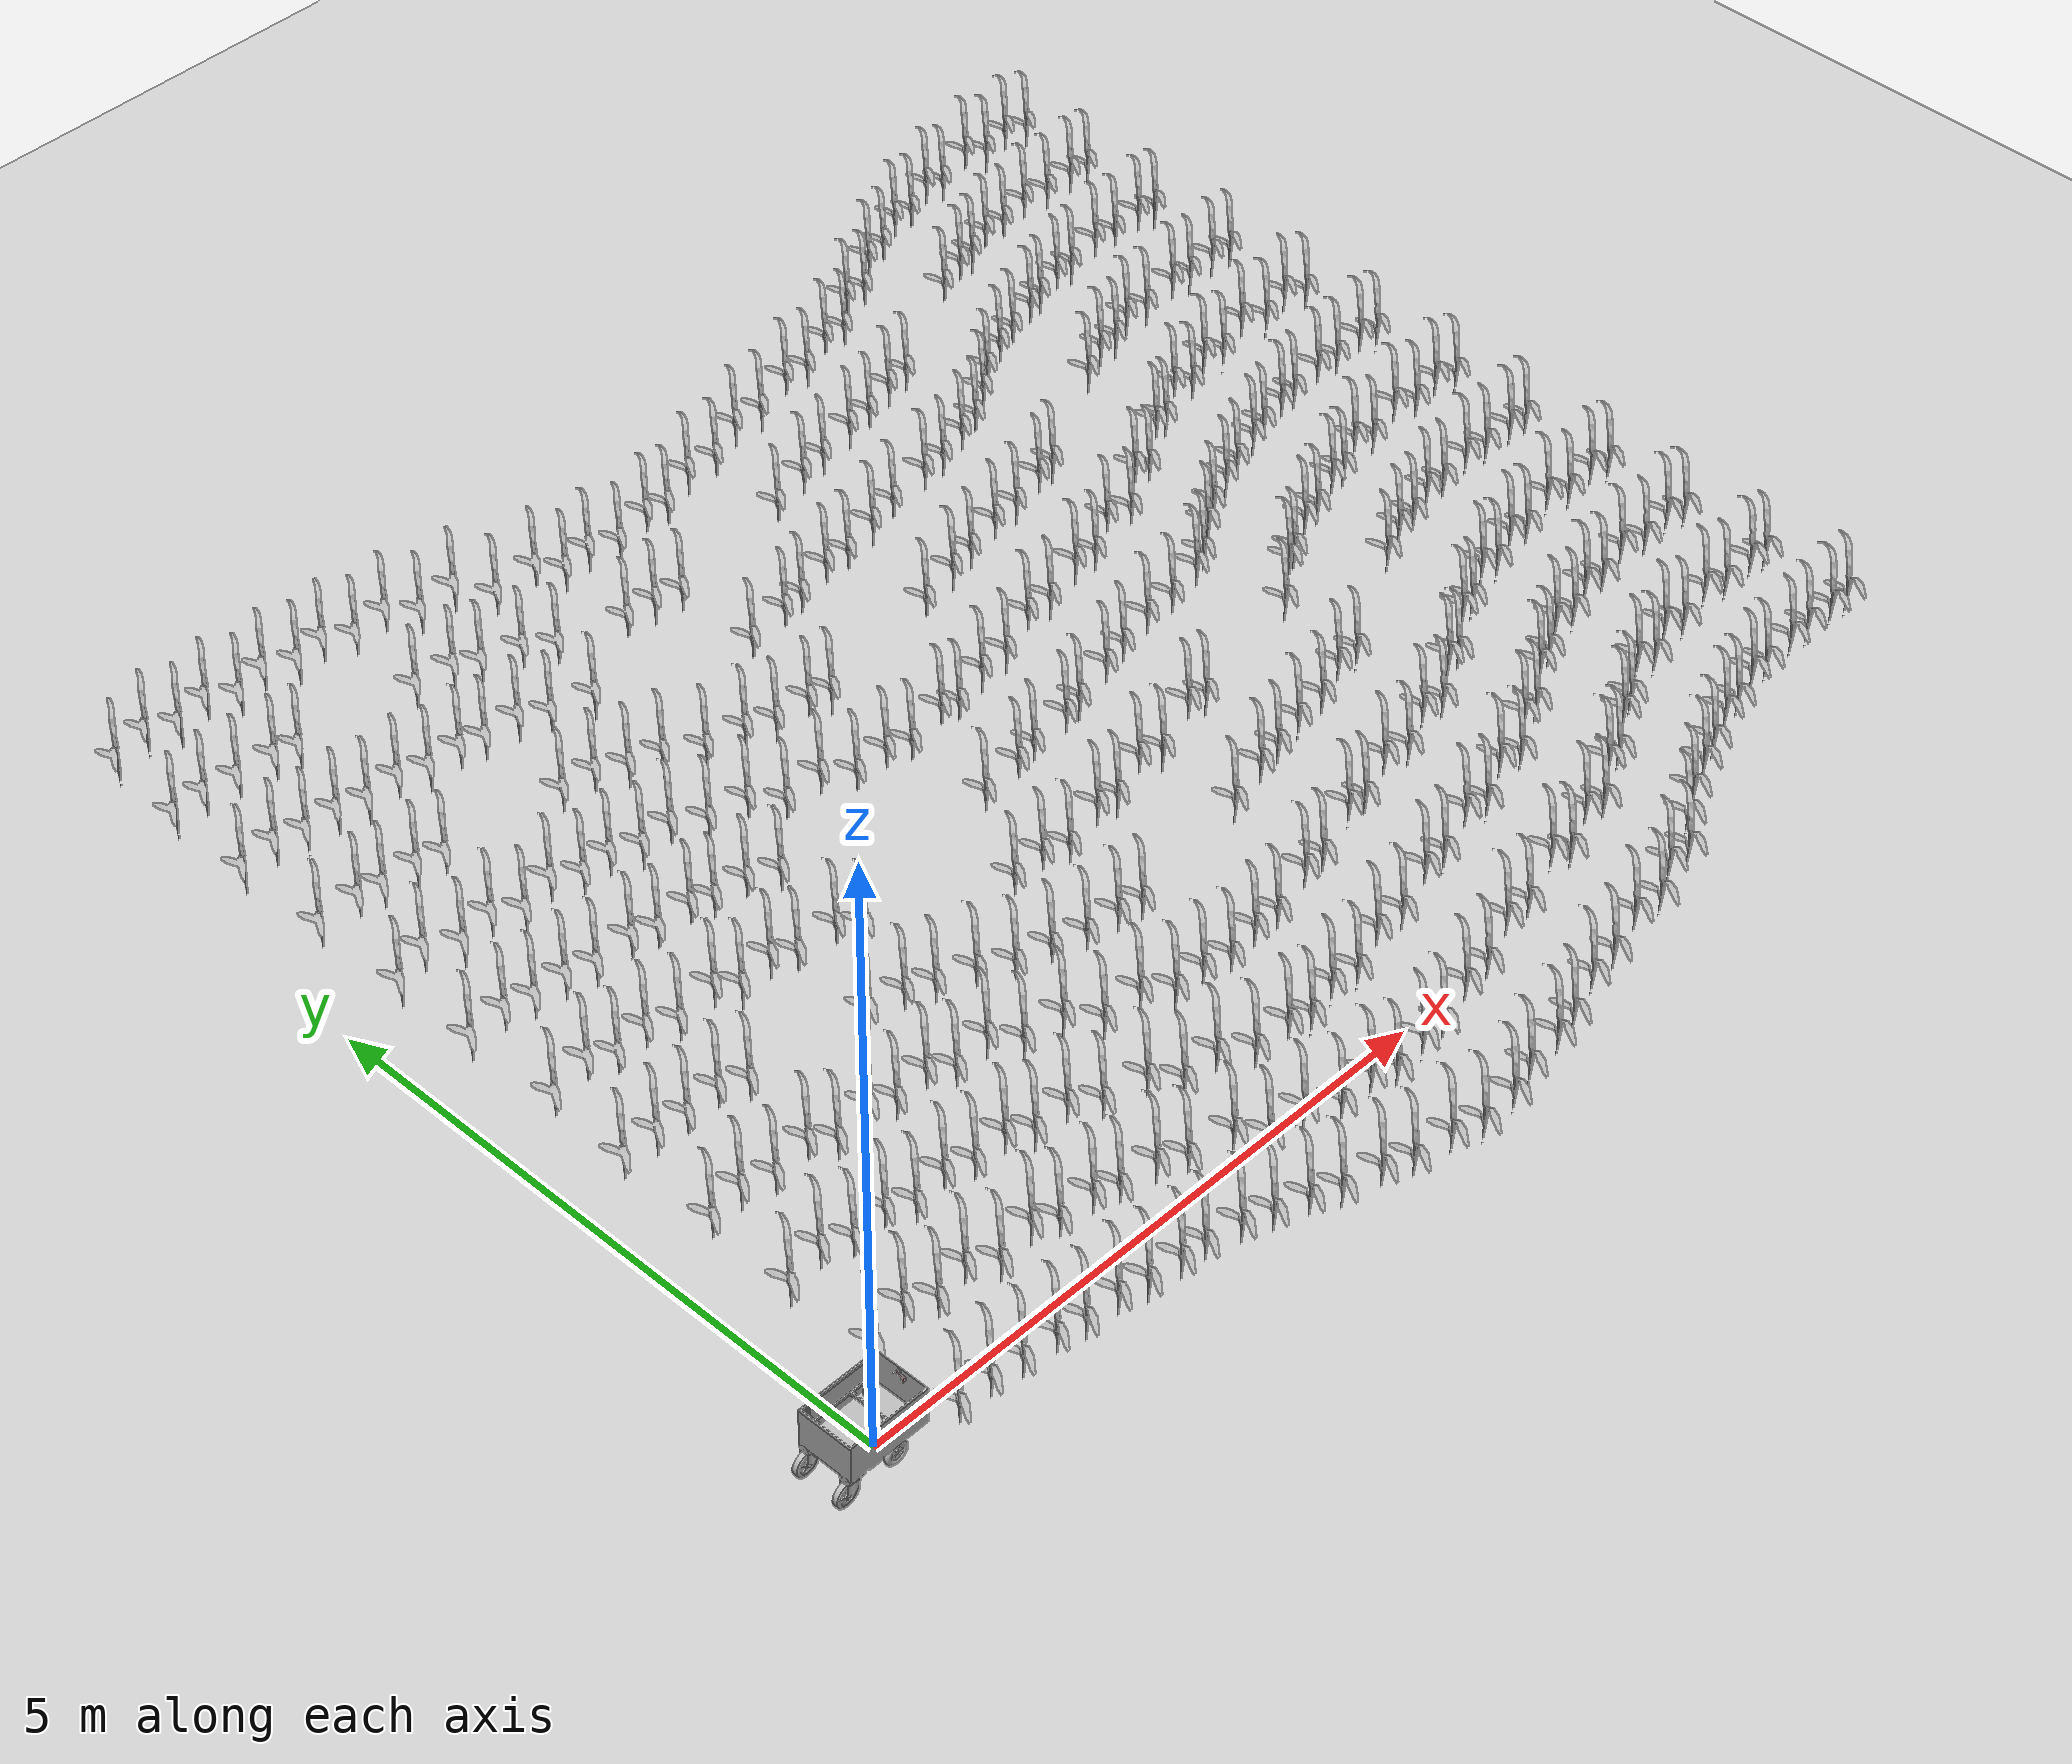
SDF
<sdf version="1.7">
 <world name="default">
  <light name="sun" type="directional">
   <pose>0 0 10 0 -0 0</pose>
   <diffuse>0.8 0.8 0.8 1</diffuse>
   <specular>0.2 0.2 0.2 1</specular>
   <attenuation>
    <range>1000</range>
    <constant>0.9</constant>
    <linear>0.01</linear>
    <quadratic>0.001</quadratic>
   </attenuation>
   <direction>-0.5 0.1 -0.9</direction>
   <spot><inner_angle>0</inner_angle><outer_angle>0</outer_angle><falloff>0</falloff></spot>
  </light>
  <model name="ground_plane">
   <static>1</static>
   <link name="link">
    <collision name="collision">
     <geometry><plane><normal>0 0 1</normal><size>100 100</size></plane></geometry>
     <surface><friction><ode><mu>100</mu><mu2>50</mu2></ode></friction></surface>
    </collision>
    <visual name="visual">
     <cast_shadows>0</cast_shadows>
     <geometry><plane><normal>0 0 1</normal><size>100 100</size></plane></geometry>
     <material>
      <script><uri>file://media/materials/scripts/gazebo.material</uri><name>Gazebo/Grey</name></script>
     </material>
    </visual>
   </link>
  </model>
  <gravity>0 0 -9.8</gravity>
  <magnetic_field>6e-06 2.3e-05 -4.2e-05</magnetic_field>
  <atmosphere type="adiabatic"/>
  <physics type="ode">
   <max_step_size>0.001</max_step_size>
   <real_time_factor>1</real_time_factor>
   <real_time_update_rate>1000</real_time_update_rate>
  </physics>
  <scene><ambient>0.4 0.4 0.4 1</ambient><background>0.7 0.7 0.7 1</background><shadows>1</shadows></scene>
  <audio><device>default</device></audio>
  <spherical_coordinates>
   <surface_model>EARTH_WGS84</surface_model>
   <latitude_deg>0</latitude_deg>
   <longitude_deg>0</longitude_deg>
   <elevation>0</elevation>
   <heading_deg>0</heading_deg>
  </spherical_coordinates>
  <model name="my_robot">
   <link name="base_footprint">
    <inertial>
     <pose>-0.019218 0.012213 0.292917 0 -0 0</pose>
     <mass>4.69185</mass>
     <inertia>
      <ixx>0.254815</ixx>
      <ixy>0.00014591</ixy>
      <ixz>-0.00762251</ixz>
      <iyy>0.300373</iyy>
      <iyz>0.000750303</iyz>
      <izz>0.302653</izz>
     </inertia>
    </inertial>
    <collision name="base_footprint_fixed_joint_lump__base_link_collision">
     <pose>0 0 0.25 0 -0 0</pose>
     <geometry>
      <mesh>
       <scale>1 1 1</scale>
       <uri>file:///home/tune65/robbie_ws/install/robbie_description/share/robbie_description/meshes/base_link.STL</uri>
      </mesh>
     </geometry>
    </collision>
    <collision name="base_footprint_fixed_joint_lump__camera_link_collision_1">
     <pose>0.295 0.012007 0.474506 0 -0 0</pose>
     <geometry>
      <mesh>
       <scale>1 1 1</scale>
       <uri>file:///home/tune65/robbie_ws/install/robbie_description/share/robbie_description/meshes/camera_link.STL</uri>
      </mesh>
     </geometry>
    </collision>
    <collision name="base_footprint_fixed_joint_lump__imu_link_collision_2">
     <pose>0 0 0.54 0 -0 0</pose>
     <geometry><box><size>0.03 0.03 0.03</size></box></geometry>
    </collision>
    <collision name="base_footprint_fixed_joint_lump__lidar_link_collision_3">
     <pose>0 0 0.58 0 -0 0</pose>
     <geometry><box><size>0.05 0.05 0.05</size></box></geometry>
    </collision>
    <visual name="base_footprint_fixed_joint_lump__base_link_visual">
     <pose>0 0 0.25 0 -0 0</pose>
     <geometry>
      <mesh>
       <scale>1 1 1</scale>
       <uri>file:///home/tune65/robbie_ws/install/robbie_description/share/robbie_description/meshes/base_link.STL</uri>
      </mesh>
     </geometry>
    </visual>
    <visual name="base_footprint_fixed_joint_lump__camera_link_visual_1">
     <pose>0.295 0.012007 0.474506 0 -0 0</pose>
     <geometry>
      <mesh>
       <scale>1 1 1</scale>
       <uri>file:///home/tune65/robbie_ws/install/robbie_description/share/robbie_description/meshes/camera_link.STL</uri>
      </mesh>
     </geometry>
     <material>
      <script><name>Gazebo/Red</name><uri>file://media/materials/scripts/gazebo.material</uri></script>
     </material>
    </visual>
    <visual name="base_footprint_fixed_joint_lump__imu_link_visual_2">
     <pose>0 0 0.54 0 -0 0</pose>
     <geometry><box><size>0.03 0.03 0.03</size></box></geometry>
    </visual>
    <visual name="base_footprint_fixed_joint_lump__lidar_link_visual_3">
     <pose>0 0 0.58 0 -0 0</pose>
     <geometry><box><size>0.05 0.05 0.05</size></box></geometry>
    </visual>
    <sensor name="camera_sensor" type="camera">
     <visualize>1</visualize>
     <update_rate>10</update_rate>
     <plugin name="camera_controller" filename="libgazebo_ros_camera.so">
      <frame_name>custom_frame</frame_name>
     </plugin>
     <pose>0.295 0.012007 0.474506 0 -0 0</pose>
     <camera>
      <horizontal_fov>1.047</horizontal_fov>
      <image><width>320</width><height>240</height></image>
      <clip><near>0.1</near><far>100</far></clip>
     </camera>
    </sensor>
    <sensor name="lidar" type="ray">
     <always_on>1</always_on>
     <visualize>1</visualize>
     <update_rate>5</update_rate>
     <ray>
      <scan>
       <horizontal>
        <samples>360</samples>
        <resolution>1</resolution>
        <min_angle>0</min_angle>
        <max_angle>6.28</max_angle>
       </horizontal>
       <vertical><samples>1</samples><min_angle>0</min_angle><max_angle>0</max_angle></vertical>
      </scan>
      <range><min>0.12</min><max>3.5</max><resolution>0.015</resolution></range>
      <noise><type>gaussian</type><mean>0</mean><stddev>0.01</stddev></noise>
     </ray>
     <plugin name="scan" filename="libgazebo_ros_ray_sensor.so">
      <ros><remapping>~/out:=scan</remapping></ros>
      <output_type>sensor_msgs/LaserScan</output_type>
      <frame_name>lidar_link</frame_name>
     </plugin>
     <pose>0 0 0.58 0 -0 0</pose>
    </sensor>
   </link>
   <joint name="castor_left_joint" type="revolute">
    <pose relative_to="base_footprint">-0.316 0.174 0.213 0 -0 0</pose>
    <parent>base_footprint</parent>
    <child>castor_left</child>
    <axis>
     <xyz>0 0 1</xyz>
     <limit><effort>10</effort><velocity>0</velocity><lower>-1e+16</lower><upper>1e+16</upper></limit>
     <dynamics><spring_reference>0</spring_reference><spring_stiffness>0</spring_stiffness></dynamics>
    </axis>
   </joint>
   <link name="castor_left">
    <pose relative_to="castor_left_joint">0 0 0 0 -0 0</pose>
    <inertial>
     <pose>-0.016038 -0.000361 -0.040846 0 -0 0</pose>
     <mass>0.175409</mass>
     <inertia>
      <ixx>0.000376266</ixx>
      <ixy>-4.08537e-08</ixy>
      <ixz>-8.33769e-05</ixz>
      <iyy>0.000367456</iyy>
      <iyz>-4.92639e-08</iyz>
      <izz>0.000322142</izz>
     </inertia>
    </inertial>
    <collision name="castor_left_collision">
     <geometry>
      <mesh>
       <scale>1 1 1</scale>
       <uri>file:///home/tune65/robbie_ws/install/robbie_description/share/robbie_description/meshes/castor_left.STL</uri>
      </mesh>
     </geometry>
    </collision>
    <visual name="castor_left_visual">
     <geometry>
      <mesh>
       <scale>1 1 1</scale>
       <uri>file:///home/tune65/robbie_ws/install/robbie_description/share/robbie_description/meshes/castor_left.STL</uri>
      </mesh>
     </geometry>
    </visual>
   </link>
   <joint name="left_rear_wheel_joint" type="revolute">
    <pose relative_to="castor_left">-0.056932 0.0425 -0.131998 1.5708 -0 0</pose>
    <parent>castor_left</parent>
    <child>left_rear_wheel</child>
    <axis>
     <xyz>0 0 -1</xyz>
     <limit><effort>10</effort><velocity>10</velocity><lower>-1e+16</lower><upper>1e+16</upper></limit>
     <dynamics>
      <damping>0.1</damping>
      <friction>0.1</friction>
      <spring_reference>0</spring_reference>
      <spring_stiffness>0</spring_stiffness>
     </dynamics>
    </axis>
   </joint>
   <link name="left_rear_wheel">
    <pose relative_to="left_rear_wheel_joint">0 0 0 0 -0 0</pose>
    <inertial>
     <pose>-3e-06 -1.6e-05 0.042496 0 -0 0</pose>
     <mass>0.977398</mass>
     <inertia>
      <ixx>0.00315278</ixx>
      <ixy>-2.63404e-06</ixy>
      <ixz>9.61305e-08</ixz>
      <iyy>0.00314549</iyy>
      <iyz>5.97873e-08</iyz>
      <izz>0.00595538</izz>
     </inertia>
    </inertial>
    <collision name="left_rear_wheel_collision">
     <geometry>
      <mesh>
       <scale>1 1 1</scale>
       <uri>file:///home/tune65/robbie_ws/install/robbie_description/share/robbie_description/meshes/left_rear_wheel.STL</uri>
      </mesh>
     </geometry>
    </collision>
    <visual name="left_rear_wheel_visual">
     <geometry>
      <mesh>
       <scale>1 1 1</scale>
       <uri>file:///home/tune65/robbie_ws/install/robbie_description/share/robbie_description/meshes/left_rear_wheel.STL</uri>
      </mesh>
     </geometry>
    </visual>
   </link>
   <joint name="castor_right_joint" type="revolute">
    <pose relative_to="base_footprint">-0.316 -0.174 0.213 0 -0 0</pose>
    <parent>base_footprint</parent>
    <child>castor_right</child>
    <axis>
     <xyz>0 0 1</xyz>
     <limit><effort>10</effort><velocity>0</velocity><lower>-1e+16</lower><upper>1e+16</upper></limit>
     <dynamics><spring_reference>0</spring_reference><spring_stiffness>0</spring_stiffness></dynamics>
    </axis>
   </joint>
   <link name="castor_right">
    <pose relative_to="castor_right_joint">0 0 0 0 -0 0</pose>
    <inertial>
     <pose>-0.016038 0.000348 -0.040846 0 -0 0</pose>
     <mass>0.175409</mass>
     <inertia>
      <ixx>0.000376266</ixx>
      <ixy>-4.08537e-08</ixy>
      <ixz>-8.33769e-05</ixz>
      <iyy>0.000367456</iyy>
      <iyz>-4.92634e-08</iyz>
      <izz>0.000322142</izz>
     </inertia>
    </inertial>
    <collision name="castor_right_collision">
     <geometry>
      <mesh>
       <scale>1 1 1</scale>
       <uri>file:///home/tune65/robbie_ws/install/robbie_description/share/robbie_description/meshes/castor_right.STL</uri>
      </mesh>
     </geometry>
    </collision>
    <visual name="castor_right_visual">
     <geometry>
      <mesh>
       <scale>1 1 1</scale>
       <uri>file:///home/tune65/robbie_ws/install/robbie_description/share/robbie_description/meshes/castor_right.STL</uri>
      </mesh>
     </geometry>
    </visual>
   </link>
   <joint name="right_rear_wheel_joint" type="revolute">
    <pose relative_to="castor_right">-0.056932 -0.0425 -0.131998 1.5708 -0 0</pose>
    <parent>castor_right</parent>
    <child>right_rear_wheel</child>
    <axis>
     <xyz>0 0 -1</xyz>
     <limit><effort>10</effort><velocity>10</velocity><lower>-1e+16</lower><upper>1e+16</upper></limit>
     <dynamics>
      <damping>0.1</damping>
      <friction>0.1</friction>
      <spring_reference>0</spring_reference>
      <spring_stiffness>0</spring_stiffness>
     </dynamics>
    </axis>
   </joint>
   <link name="right_rear_wheel">
    <pose relative_to="right_rear_wheel_joint">0 0 0 0 -0 0</pose>
    <inertial>
     <pose>1.6e-05 -3e-06 -0.042504 0 -0 0</pose>
     <mass>0.977397</mass>
     <inertia>
      <ixx>0.00314549</ixx>
      <ixy>2.63402e-06</ixy>
      <ixz>-5.97688e-08</ixz>
      <iyy>0.00315278</iyy>
      <iyz>9.61286e-08</iyz>
      <izz>0.00595538</izz>
     </inertia>
    </inertial>
    <collision name="right_rear_wheel_collision">
     <geometry>
      <mesh>
       <scale>1 1 1</scale>
       <uri>file:///home/tune65/robbie_ws/install/robbie_description/share/robbie_description/meshes/right_rear_wheel.STL</uri>
      </mesh>
     </geometry>
    </collision>
    <visual name="right_rear_wheel_visual">
     <geometry>
      <mesh>
       <scale>1 1 1</scale>
       <uri>file:///home/tune65/robbie_ws/install/robbie_description/share/robbie_description/meshes/right_rear_wheel.STL</uri>
      </mesh>
     </geometry>
    </visual>
   </link>
   <joint name="left_front_wheel_joint" type="revolute">
    <pose relative_to="base_footprint">0.072912 0.184125 0.083407 1.5708 -0 0</pose>
    <parent>base_footprint</parent>
    <child>left_front_wheel</child>
    <axis>
     <xyz>0 0 -1</xyz>
     <limit><effort>10</effort><velocity>10</velocity><lower>-1e+16</lower><upper>1e+16</upper></limit>
     <dynamics>
      <damping>0.1</damping>
      <friction>0.1</friction>
      <spring_reference>0</spring_reference>
      <spring_stiffness>0</spring_stiffness>
     </dynamics>
    </axis>
   </joint>
   <link name="left_front_wheel">
    <pose relative_to="left_front_wheel_joint">0 0 0 0 -0 0</pose>
    <inertial>
     <pose>-0 0 0.01992 0 -0 0</pose>
     <mass>0.947518</mass>
     <inertia>
      <ixx>0.0026353</ixx>
      <ixy>2.50703e-12</ixy>
      <ixz>-2.04438e-13</ixz>
      <iyy>0.0026353</iyy>
      <iyz>1.15655e-14</iyz>
      <izz>0.00501071</izz>
     </inertia>
    </inertial>
    <collision name="left_front_wheel_collision">
     <geometry>
      <mesh>
       <scale>1 1 1</scale>
       <uri>file:///home/tune65/robbie_ws/install/robbie_description/share/robbie_description/meshes/left_front_wheel.STL</uri>
      </mesh>
     </geometry>
    </collision>
    <visual name="left_front_wheel_visual">
     <geometry>
      <mesh>
       <scale>1 1 1</scale>
       <uri>file:///home/tune65/robbie_ws/install/robbie_description/share/robbie_description/meshes/left_front_wheel.STL</uri>
      </mesh>
     </geometry>
    </visual>
   </link>
   <joint name="right_front_wheel_joint" type="revolute">
    <pose relative_to="base_footprint">0.072912 -0.184125 0.083407 1.5708 -0 0</pose>
    <parent>base_footprint</parent>
    <child>right_front_wheel</child>
    <axis>
     <xyz>0 0 -1</xyz>
     <limit><effort>10</effort><velocity>10</velocity><lower>-1e+16</lower><upper>1e+16</upper></limit>
     <dynamics>
      <damping>0.1</damping>
      <friction>0.1</friction>
      <spring_reference>0</spring_reference>
      <spring_stiffness>0</spring_stiffness>
     </dynamics>
    </axis>
   </joint>
   <link name="right_front_wheel">
    <pose relative_to="right_front_wheel_joint">0 0 0 0 -0 0</pose>
    <inertial>
     <pose>0 0 -0.01992 0 -0 0</pose>
     <mass>0.947518</mass>
     <inertia>
      <ixx>0.0026353</ixx>
      <ixy>-3.66849e-13</ixy>
      <ixz>-1.92247e-13</ixz>
      <iyy>0.0026353</iyy>
      <iyz>-7.04969e-14</iyz>
      <izz>0.00501071</izz>
     </inertia>
    </inertial>
    <collision name="right_front_wheel_collision">
     <geometry>
      <mesh>
       <scale>1 1 1</scale>
       <uri>file:///home/tune65/robbie_ws/install/robbie_description/share/robbie_description/meshes/right_front_wheel.STL</uri>
      </mesh>
     </geometry>
    </collision>
    <visual name="right_front_wheel_visual">
     <geometry>
      <mesh>
       <scale>1 1 1</scale>
       <uri>file:///home/tune65/robbie_ws/install/robbie_description/share/robbie_description/meshes/right_front_wheel.STL</uri>
      </mesh>
     </geometry>
    </visual>
   </link>
   <plugin name="diff_drive_controller" filename="libgazebo_ros_diff_drive.so">
    <update_rate>50</update_rate>
    <left_joint>left_front_wheel_joint</left_joint>
    <right_joint>right_front_wheel_joint</right_joint>
    <wheel_separation>0.33282</wheel_separation>
    <wheel_diameter>0.19</wheel_diameter>
    <publish_odom>1</publish_odom>
    <publish_odom_tf>1</publish_odom_tf>
    <publish_wheel_tf>1</publish_wheel_tf>
    <odometry_topic>/odom</odometry_topic>
    <odometry_frame>odom</odometry_frame>
    <robot_base_frame>base_footprint</robot_base_frame>
   </plugin>
   <static>0</static>
   <plugin name="gazebo_ros_joint_state_publisher" filename="libgazebo_ros_joint_state_publisher.so">
    <update_rate>100</update_rate>
    <joint_name>castor_left_joint</joint_name>
    <joint_name>castor_right_joint</joint_name>
    <joint_name>left_rear_wheel_joint</joint_name>
    <joint_name>right_rear_wheel_joint</joint_name>
   </plugin>
   <pose>-0.065814 -0.022522 0.01452 2.8e-05 0.015174 0.0131</pose>
  </model>
  <model name="field_row_full_double">
   <model name="field_row_full">
    <model name="field_row_1">
     <model name="maize_02">
      <pose>-5.01978 0.059092 0 0 -0 0</pose>
      <link name="maize_02_link">
       <inertial>
        <pose>0 0 0.01 0 -0 0</pose>
        <mass>0.3</mass>
        <inertia>
         <ixx>0.00334167</ixx>
         <ixy>0</ixy>
         <ixz>0</ixz>
         <iyy>0.00334167</iyy>
         <iyz>0</iyz>
         <izz>1.66667e-05</izz>
        </inertia>
        <pose>0 0 0.1 0 -0 0</pose>
       </inertial>
       <collision name="collision">
        <pose>0 0 0.2 0 -0 0</pose>
        <geometry><box><size>0.02 0.02 0.4</size></box></geometry>
        <surface><friction><ode><mu>10</mu><mu2>10</mu2></ode></friction></surface>
       </collision>
       <visual name="visual">
        <geometry>
         <mesh><uri>model://maize_02/meshes/maize_02.dae</uri><scale>0.683166 0.683166 0.683166</scale></mesh>
        </geometry>
       </visual>
      </link>
     </model>
     <model name="maize_02_clone">
      <pose>-4.47361 0.041185 0 0 -0 0</pose>
      <link name="maize_02_link">
       <inertial>
        <pose>0 0 0.01 0 -0 0</pose>
        <mass>0.3</mass>
        <inertia>
         <ixx>0.00334167</ixx>
         <ixy>0</ixy>
         <ixz>0</ixz>
         <iyy>0.00334167</iyy>
         <iyz>0</iyz>
         <izz>1.66667e-05</izz>
        </inertia>
        <pose>0 0 0.1 0 -0 0</pose>
       </inertial>
       <collision name="collision">
        <pose>0 0 0.2 0 -0 0</pose>
        <geometry><box><size>0.02 0.02 0.4</size></box></geometry>
        <surface><friction><ode><mu>10</mu><mu2>10</mu2></ode></friction></surface>
       </collision>
       <visual name="visual">
        <geometry>
         <mesh><uri>model://maize_02/meshes/maize_02.dae</uri><scale>0.683166 0.683166 0.683166</scale></mesh>
        </geometry>
       </visual>
      </link>
     </model>
     <model name="maize_02_clone_0">
      <pose>-3.97222 -0.021489 0 0 -0 0</pose>
      <link name="maize_02_link">
       <inertial>
        <pose>0 0 0.01 0 -0 0</pose>
        <mass>0.3</mass>
        <inertia>
         <ixx>0.00334167</ixx>
         <ixy>0</ixy>
         <ixz>0</ixz>
         <iyy>0.00334167</iyy>
         <iyz>0</iyz>
         <izz>1.66667e-05</izz>
        </inertia>
        <pose>0 0 0.1 0 -0 0</pose>
       </inertial>
       <collision name="collision">
        <pose>0 0 0.2 0 -0 0</pose>
        <geometry><box><size>0.02 0.02 0.4</size></box></geometry>
        <surface><friction><ode><mu>10</mu><mu2>10</mu2></ode></friction></surface>
       </collision>
       <visual name="visual">
        <geometry>
         <mesh><uri>model://maize_02/meshes/maize_02.dae</uri><scale>0.683166 0.683166 0.683166</scale></mesh>
        </geometry>
       </visual>
      </link>
     </model>
     <model name="maize_02_clone_1">
      <pose>-3.45291 -0.039396 0 0 -0 0</pose>
      <link name="maize_02_link">
       <inertial>
        <pose>0 0 0.01 0 -0 0</pose>
        <mass>0.3</mass>
        <inertia>
         <ixx>0.00334167</ixx>
         <ixy>0</ixy>
         <ixz>0</ixz>
         <iyy>0.00334167</iyy>
         <iyz>0</iyz>
         <izz>1.66667e-05</izz>
        </inertia>
        <pose>0 0 0.1 0 -0 0</pose>
       </inertial>
       <collision name="collision">
        <pose>0 0 0.2 0 -0 0</pose>
        <geometry><box><size>0.02 0.02 0.4</size></box></geometry>
        <surface><friction><ode><mu>10</mu><mu2>10</mu2></ode></friction></surface>
       </collision>
       <visual name="visual">
        <geometry>
         <mesh><uri>model://maize_02/meshes/maize_02.dae</uri><scale>0.683166 0.683166 0.683166</scale></mesh>
        </geometry>
       </visual>
      </link>
     </model>
     <model name="maize_02_clone_10">
      <pose>1.49837 -0.182649 0 0 -0 0</pose>
      <link name="maize_02_link">
       <inertial>
        <pose>0 0 0.01 0 -0 0</pose>
        <mass>0.3</mass>
        <inertia>
         <ixx>0.00334167</ixx>
         <ixy>0</ixy>
         <ixz>0</ixz>
         <iyy>0.00334167</iyy>
         <iyz>0</iyz>
         <izz>1.66667e-05</izz>
        </inertia>
        <pose>0 0 0.1 0 -0 0</pose>
       </inertial>
       <collision name="collision">
        <pose>0 0 0.2 0 -0 0</pose>
        <geometry><box><size>0.02 0.02 0.4</size></box></geometry>
        <surface><friction><ode><mu>10</mu><mu2>10</mu2></ode></friction></surface>
       </collision>
       <visual name="visual">
        <geometry>
         <mesh><uri>model://maize_02/meshes/maize_02.dae</uri><scale>0.683166 0.683166 0.683166</scale></mesh>
        </geometry>
       </visual>
      </link>
     </model>
     <model name="maize_02_clone_11">
      <pose>2.04453 -0.030442 0 0 -0 0</pose>
      <link name="maize_02_link">
       <inertial>
        <pose>0 0 0.01 0 -0 0</pose>
        <mass>0.3</mass>
        <inertia>
         <ixx>0.00334167</ixx>
         <ixy>0</ixy>
         <ixz>0</ixz>
         <iyy>0.00334167</iyy>
         <iyz>0</iyz>
         <izz>1.66667e-05</izz>
        </inertia>
        <pose>0 0 0.1 0 -0 0</pose>
       </inertial>
       <collision name="collision">
        <pose>0 0 0.2 0 -0 0</pose>
        <geometry><box><size>0.02 0.02 0.4</size></box></geometry>
        <surface><friction><ode><mu>10</mu><mu2>10</mu2></ode></friction></surface>
       </collision>
       <visual name="visual">
        <geometry>
         <mesh><uri>model://maize_02/meshes/maize_02.dae</uri><scale>0.683166 0.683166 0.683166</scale></mesh>
        </geometry>
       </visual>
      </link>
     </model>
     <model name="maize_02_clone_12">
      <pose>2.51011 0.220253 0 0 -0 0</pose>
      <link name="maize_02_link">
       <inertial>
        <pose>0 0 0.01 0 -0 0</pose>
        <mass>0.3</mass>
        <inertia>
         <ixx>0.00334167</ixx>
         <ixy>0</ixy>
         <ixz>0</ixz>
         <iyy>0.00334167</iyy>
         <iyz>0</iyz>
         <izz>1.66667e-05</izz>
        </inertia>
        <pose>0 0 0.1 0 -0 0</pose>
       </inertial>
       <collision name="collision">
        <pose>0 0 0.2 0 -0 0</pose>
        <geometry><box><size>0.02 0.02 0.4</size></box></geometry>
        <surface><friction><ode><mu>10</mu><mu2>10</mu2></ode></friction></surface>
       </collision>
       <visual name="visual">
        <geometry>
         <mesh><uri>model://maize_02/meshes/maize_02.dae</uri><scale>0.683166 0.683166 0.683166</scale></mesh>
        </geometry>
       </visual>
      </link>
     </model>
     <model name="maize_02_clone_13">
      <pose>3.02046 0.524669 0 0 -0 0</pose>
      <link name="maize_02_link">
       <inertial>
        <pose>0 0 0.01 0 -0 0</pose>
        <mass>0.3</mass>
        <inertia>
         <ixx>0.00334167</ixx>
         <ixy>0</ixy>
         <ixz>0</ixz>
         <iyy>0.00334167</iyy>
         <iyz>0</iyz>
         <izz>1.66667e-05</izz>
        </inertia>
        <pose>0 0 0.1 0 -0 0</pose>
       </inertial>
       <collision name="collision">
        <pose>0 0 0.2 0 -0 0</pose>
        <geometry><box><size>0.02 0.02 0.4</size></box></geometry>
        <surface><friction><ode><mu>10</mu><mu2>10</mu2></ode></friction></surface>
       </collision>
       <visual name="visual">
        <geometry>
         <mesh><uri>model://maize_02/meshes/maize_02.dae</uri><scale>0.683166 0.683166 0.683166</scale></mesh>
        </geometry>
       </visual>
      </link>
     </model>
     <model name="maize_02_clone_14">
      <pose>3.48604 0.676876 0 0 -0 0</pose>
      <link name="maize_02_link">
       <inertial>
        <pose>0 0 0.01 0 -0 0</pose>
        <mass>0.3</mass>
        <inertia>
         <ixx>0.00334167</ixx>
         <ixy>0</ixy>
         <ixz>0</ixz>
         <iyy>0.00334167</iyy>
         <iyz>0</iyz>
         <izz>1.66667e-05</izz>
        </inertia>
        <pose>0 0 0.1 0 -0 0</pose>
       </inertial>
       <collision name="collision">
        <pose>0 0 0.2 0 -0 0</pose>
        <geometry><box><size>0.02 0.02 0.4</size></box></geometry>
        <surface><friction><ode><mu>10</mu><mu2>10</mu2></ode></friction></surface>
       </collision>
       <visual name="visual">
        <geometry>
         <mesh><uri>model://maize_02/meshes/maize_02.dae</uri><scale>0.683166 0.683166 0.683166</scale></mesh>
        </geometry>
       </visual>
      </link>
     </model>
     <model name="maize_02_clone_15">
      <pose>3.94267 0.775363 0 0 -0 0</pose>
      <link name="maize_02_link">
       <inertial>
        <pose>0 0 0.01 0 -0 0</pose>
        <mass>0.3</mass>
        <inertia>
         <ixx>0.00334167</ixx>
         <ixy>0</ixy>
         <ixz>0</ixz>
         <iyy>0.00334167</iyy>
         <iyz>0</iyz>
         <izz>1.66667e-05</izz>
        </inertia>
        <pose>0 0 0.1 0 -0 0</pose>
       </inertial>
       <collision name="collision">
        <pose>0 0 0.2 0 -0 0</pose>
        <geometry><box><size>0.02 0.02 0.4</size></box></geometry>
        <surface><friction><ode><mu>10</mu><mu2>10</mu2></ode></friction></surface>
       </collision>
       <visual name="visual">
        <geometry>
         <mesh><uri>model://maize_02/meshes/maize_02.dae</uri><scale>0.683166 0.683166 0.683166</scale></mesh>
        </geometry>
       </visual>
      </link>
     </model>
     <model name="maize_02_clone_16">
      <pose>4.48883 0.82013 0 0 -0 0</pose>
      <link name="maize_02_link">
       <inertial>
        <pose>0 0 0.01 0 -0 0</pose>
        <mass>0.3</mass>
        <inertia>
         <ixx>0.00334167</ixx>
         <ixy>0</ixy>
         <ixz>0</ixz>
         <iyy>0.00334167</iyy>
         <iyz>0</iyz>
         <izz>1.66667e-05</izz>
        </inertia>
        <pose>0 0 0.1 0 -0 0</pose>
       </inertial>
       <collision name="collision">
        <pose>0 0 0.2 0 -0 0</pose>
        <geometry><box><size>0.02 0.02 0.4</size></box></geometry>
        <surface><friction><ode><mu>10</mu><mu2>10</mu2></ode></friction></surface>
       </collision>
       <visual name="visual">
        <geometry>
         <mesh><uri>model://maize_02/meshes/maize_02.dae</uri><scale>0.683166 0.683166 0.683166</scale></mesh>
        </geometry>
       </visual>
      </link>
     </model>
     <model name="maize_02_clone_17">
      <pose>4.95441 0.82013 0 0 -0 0</pose>
      <link name="maize_02_link">
       <inertial>
        <pose>0 0 0.01 0 -0 0</pose>
        <mass>0.3</mass>
        <inertia>
         <ixx>0.00334167</ixx>
         <ixy>0</ixy>
         <ixz>0</ixz>
         <iyy>0.00334167</iyy>
         <iyz>0</iyz>
         <izz>1.66667e-05</izz>
        </inertia>
        <pose>0 0 0.1 0 -0 0</pose>
       </inertial>
       <collision name="collision">
        <pose>0 0 0.2 0 -0 0</pose>
        <geometry><box><size>0.02 0.02 0.4</size></box></geometry>
        <surface><friction><ode><mu>10</mu><mu2>10</mu2></ode></friction></surface>
       </collision>
       <visual name="visual">
        <geometry>
         <mesh><uri>model://maize_02/meshes/maize_02.dae</uri><scale>0.683166 0.683166 0.683166</scale></mesh>
        </geometry>
       </visual>
      </link>
     </model>
     <model name="maize_02_clone_2">
      <pose>-2.97838 -0.119976 0 0 -0 0</pose>
      <link name="maize_02_link">
       <inertial>
        <pose>0 0 0.01 0 -0 0</pose>
        <mass>0.3</mass>
        <inertia>
         <ixx>0.00334167</ixx>
         <ixy>0</ixy>
         <ixz>0</ixz>
         <iyy>0.00334167</iyy>
         <iyz>0</iyz>
         <izz>1.66667e-05</izz>
        </inertia>
        <pose>0 0 0.1 0 -0 0</pose>
       </inertial>
       <collision name="collision">
        <pose>0 0 0.2 0 -0 0</pose>
        <geometry><box><size>0.02 0.02 0.4</size></box></geometry>
        <surface><friction><ode><mu>10</mu><mu2>10</mu2></ode></friction></surface>
       </collision>
       <visual name="visual">
        <geometry>
         <mesh><uri>model://maize_02/meshes/maize_02.dae</uri><scale>0.683166 0.683166 0.683166</scale></mesh>
        </geometry>
       </visual>
      </link>
     </model>
     <model name="maize_02_clone_3">
      <pose>-2.47698 -0.254276 0 0 -0 0</pose>
      <link name="maize_02_link">
       <inertial>
        <pose>0 0 0.01 0 -0 0</pose>
        <mass>0.3</mass>
        <inertia>
         <ixx>0.00334167</ixx>
         <ixy>0</ixy>
         <ixz>0</ixz>
         <iyy>0.00334167</iyy>
         <iyz>0</iyz>
         <izz>1.66667e-05</izz>
        </inertia>
        <pose>0 0 0.1 0 -0 0</pose>
       </inertial>
       <collision name="collision">
        <pose>0 0 0.2 0 -0 0</pose>
        <geometry><box><size>0.02 0.02 0.4</size></box></geometry>
        <surface><friction><ode><mu>10</mu><mu2>10</mu2></ode></friction></surface>
       </collision>
       <visual name="visual">
        <geometry>
         <mesh><uri>model://maize_02/meshes/maize_02.dae</uri><scale>0.683166 0.683166 0.683166</scale></mesh>
        </geometry>
       </visual>
      </link>
     </model>
     <model name="maize_02_clone_4">
      <pose>-1.96663 -0.504971 0 0 -0 0</pose>
      <link name="maize_02_link">
       <inertial>
        <pose>0 0 0.01 0 -0 0</pose>
        <mass>0.3</mass>
        <inertia>
         <ixx>0.00334167</ixx>
         <ixy>0</ixy>
         <ixz>0</ixz>
         <iyy>0.00334167</iyy>
         <iyz>0</iyz>
         <izz>1.66667e-05</izz>
        </inertia>
        <pose>0 0 0.1 0 -0 0</pose>
       </inertial>
       <collision name="collision">
        <pose>0 0 0.2 0 -0 0</pose>
        <geometry><box><size>0.02 0.02 0.4</size></box></geometry>
        <surface><friction><ode><mu>10</mu><mu2>10</mu2></ode></friction></surface>
       </collision>
       <visual name="visual">
        <geometry>
         <mesh><uri>model://maize_02/meshes/maize_02.dae</uri><scale>0.683166 0.683166 0.683166</scale></mesh>
        </geometry>
       </visual>
      </link>
     </model>
     <model name="maize_02_clone_5">
      <pose>-1.42047 -0.648225 0 0 -0 0</pose>
      <link name="maize_02_link">
       <inertial>
        <pose>0 0 0.01 0 -0 0</pose>
        <mass>0.3</mass>
        <inertia>
         <ixx>0.00334167</ixx>
         <ixy>0</ixy>
         <ixz>0</ixz>
         <iyy>0.00334167</iyy>
         <iyz>0</iyz>
         <izz>1.66667e-05</izz>
        </inertia>
        <pose>0 0 0.1 0 -0 0</pose>
       </inertial>
       <collision name="collision">
        <pose>0 0 0.2 0 -0 0</pose>
        <geometry><box><size>0.02 0.02 0.4</size></box></geometry>
        <surface><friction><ode><mu>10</mu><mu2>10</mu2></ode></friction></surface>
       </collision>
       <visual name="visual">
        <geometry>
         <mesh><uri>model://maize_02/meshes/maize_02.dae</uri><scale>0.683166 0.683166 0.683166</scale></mesh>
        </geometry>
       </visual>
      </link>
     </model>
     <model name="maize_02_clone_6">
      <pose>-0.928029 -0.701945 0 0 -0 0</pose>
      <link name="maize_02_link">
       <inertial>
        <pose>0 0 0.01 0 -0 0</pose>
        <mass>0.3</mass>
        <inertia>
         <ixx>0.00334167</ixx>
         <ixy>0</ixy>
         <ixz>0</ixz>
         <iyy>0.00334167</iyy>
         <iyz>0</iyz>
         <izz>1.66667e-05</izz>
        </inertia>
        <pose>0 0 0.1 0 -0 0</pose>
       </inertial>
       <collision name="collision">
        <pose>0 0 0.2 0 -0 0</pose>
        <geometry><box><size>0.02 0.02 0.4</size></box></geometry>
        <surface><friction><ode><mu>10</mu><mu2>10</mu2></ode></friction></surface>
       </collision>
       <visual name="visual">
        <geometry>
         <mesh><uri>model://maize_02/meshes/maize_02.dae</uri><scale>0.683166 0.683166 0.683166</scale></mesh>
        </geometry>
       </visual>
      </link>
     </model>
     <model name="maize_02_clone_7">
      <pose>-0.39082 -0.639272 0 0 -0 0</pose>
      <link name="maize_02_link">
       <inertial>
        <pose>0 0 0.01 0 -0 0</pose>
        <mass>0.3</mass>
        <inertia>
         <ixx>0.00334167</ixx>
         <ixy>0</ixy>
         <ixz>0</ixz>
         <iyy>0.00334167</iyy>
         <iyz>0</iyz>
         <izz>1.66667e-05</izz>
        </inertia>
        <pose>0 0 0.1 0 -0 0</pose>
       </inertial>
       <collision name="collision">
        <pose>0 0 0.2 0 -0 0</pose>
        <geometry><box><size>0.02 0.02 0.4</size></box></geometry>
        <surface><friction><ode><mu>10</mu><mu2>10</mu2></ode></friction></surface>
       </collision>
       <visual name="visual">
        <geometry>
         <mesh><uri>model://maize_02/meshes/maize_02.dae</uri><scale>0.683166 0.683166 0.683166</scale></mesh>
        </geometry>
       </visual>
      </link>
     </model>
     <model name="maize_02_clone_8">
      <pose>0.244878 -0.487064 0 0 -0 0</pose>
      <link name="maize_02_link">
       <inertial>
        <pose>0 0 0.01 0 -0 0</pose>
        <mass>0.3</mass>
        <inertia>
         <ixx>0.00334167</ixx>
         <ixy>0</ixy>
         <ixz>0</ixz>
         <iyy>0.00334167</iyy>
         <iyz>0</iyz>
         <izz>1.66667e-05</izz>
        </inertia>
        <pose>0 0 0.1 0 -0 0</pose>
       </inertial>
       <collision name="collision">
        <pose>0 0 0.2 0 -0 0</pose>
        <geometry><box><size>0.02 0.02 0.4</size></box></geometry>
        <surface><friction><ode><mu>10</mu><mu2>10</mu2></ode></friction></surface>
       </collision>
       <visual name="visual">
        <geometry>
         <mesh><uri>model://maize_02/meshes/maize_02.dae</uri><scale>0.683166 0.683166 0.683166</scale></mesh>
        </geometry>
       </visual>
      </link>
     </model>
     <model name="maize_02_clone_9">
      <pose>0.889529 -0.307996 0 0 -0 0</pose>
      <link name="maize_02_link">
       <inertial>
        <pose>0 0 0.01 0 -0 0</pose>
        <mass>0.3</mass>
        <inertia>
         <ixx>0.00334167</ixx>
         <ixy>0</ixy>
         <ixz>0</ixz>
         <iyy>0.00334167</iyy>
         <iyz>0</iyz>
         <izz>1.66667e-05</izz>
        </inertia>
        <pose>0 0 0.1 0 -0 0</pose>
       </inertial>
       <collision name="collision">
        <pose>0 0 0.2 0 -0 0</pose>
        <geometry><box><size>0.02 0.02 0.4</size></box></geometry>
        <surface><friction><ode><mu>10</mu><mu2>10</mu2></ode></friction></surface>
       </collision>
       <visual name="visual">
        <geometry>
         <mesh><uri>model://maize_02/meshes/maize_02.dae</uri><scale>0.683166 0.683166 0.683166</scale></mesh>
        </geometry>
       </visual>
      </link>
     </model>
     <static>0</static>
     <pose>1.04182 -0.89103 -0.032258 0 -0 0</pose>
    </model>
    <model name="field_row_1_0">
     <model name="maize_02">
      <pose>-5.01978 0.059092 0 0 -0 0</pose>
      <link name="maize_02_link">
       <inertial>
        <pose>0 0 0.01 0 -0 0</pose>
        <mass>0.3</mass>
        <inertia>
         <ixx>0.00334167</ixx>
         <ixy>0</ixy>
         <ixz>0</ixz>
         <iyy>0.00334167</iyy>
         <iyz>0</iyz>
         <izz>1.66667e-05</izz>
        </inertia>
        <pose>0 0 0.1 0 -0 0</pose>
       </inertial>
       <collision name="collision">
        <pose>0 0 0.2 0 -0 0</pose>
        <geometry><box><size>0.02 0.02 0.4</size></box></geometry>
        <surface><friction><ode><mu>10</mu><mu2>10</mu2></ode></friction></surface>
       </collision>
       <visual name="visual">
        <geometry>
         <mesh><uri>model://maize_02/meshes/maize_02.dae</uri><scale>0.683166 0.683166 0.683166</scale></mesh>
        </geometry>
       </visual>
      </link>
     </model>
     <model name="maize_02_clone">
      <pose>-4.47361 0.041185 0 0 -0 0</pose>
      <link name="maize_02_link">
       <inertial>
        <pose>0 0 0.01 0 -0 0</pose>
        <mass>0.3</mass>
        <inertia>
         <ixx>0.00334167</ixx>
         <ixy>0</ixy>
         <ixz>0</ixz>
         <iyy>0.00334167</iyy>
         <iyz>0</iyz>
         <izz>1.66667e-05</izz>
        </inertia>
        <pose>0 0 0.1 0 -0 0</pose>
       </inertial>
       <collision name="collision">
        <pose>0 0 0.2 0 -0 0</pose>
        <geometry><box><size>0.02 0.02 0.4</size></box></geometry>
        <surface><friction><ode><mu>10</mu><mu2>10</mu2></ode></friction></surface>
       </collision>
       <visual name="visual">
        <geometry>
         <mesh><uri>model://maize_02/meshes/maize_02.dae</uri><scale>0.683166 0.683166 0.683166</scale></mesh>
        </geometry>
       </visual>
      </link>
     </model>
     <model name="maize_02_clone_0">
      <pose>-3.97222 -0.021489 0 0 -0 0</pose>
      <link name="maize_02_link">
       <inertial>
        <pose>0 0 0.01 0 -0 0</pose>
        <mass>0.3</mass>
        <inertia>
         <ixx>0.00334167</ixx>
         <ixy>0</ixy>
         <ixz>0</ixz>
         <iyy>0.00334167</iyy>
         <iyz>0</iyz>
         <izz>1.66667e-05</izz>
        </inertia>
        <pose>0 0 0.1 0 -0 0</pose>
       </inertial>
       <collision name="collision">
        <pose>0 0 0.2 0 -0 0</pose>
        <geometry><box><size>0.02 0.02 0.4</size></box></geometry>
        <surface><friction><ode><mu>10</mu><mu2>10</mu2></ode></friction></surface>
       </collision>
       <visual name="visual">
        <geometry>
         <mesh><uri>model://maize_02/meshes/maize_02.dae</uri><scale>0.683166 0.683166 0.683166</scale></mesh>
        </geometry>
       </visual>
      </link>
     </model>
     <model name="maize_02_clone_1">
      <pose>-3.45291 -0.039396 0 0 -0 0</pose>
      <link name="maize_02_link">
       <inertial>
        <pose>0 0 0.01 0 -0 0</pose>
        <mass>0.3</mass>
        <inertia>
         <ixx>0.00334167</ixx>
         <ixy>0</ixy>
         <ixz>0</ixz>
         <iyy>0.00334167</iyy>
         <iyz>0</iyz>
         <izz>1.66667e-05</izz>
        </inertia>
        <pose>0 0 0.1 0 -0 0</pose>
       </inertial>
       <collision name="collision">
        <pose>0 0 0.2 0 -0 0</pose>
        <geometry><box><size>0.02 0.02 0.4</size></box></geometry>
        <surface><friction><ode><mu>10</mu><mu2>10</mu2></ode></friction></surface>
       </collision>
       <visual name="visual">
        <geometry>
         <mesh><uri>model://maize_02/meshes/maize_02.dae</uri><scale>0.683166 0.683166 0.683166</scale></mesh>
        </geometry>
       </visual>
      </link>
     </model>
     <model name="maize_02_clone_10">
      <pose>1.49837 -0.182649 0 0 -0 0</pose>
      <link name="maize_02_link">
       <inertial>
        <pose>0 0 0.01 0 -0 0</pose>
        <mass>0.3</mass>
        <inertia>
         <ixx>0.00334167</ixx>
         <ixy>0</ixy>
         <ixz>0</ixz>
         <iyy>0.00334167</iyy>
         <iyz>0</iyz>
         <izz>1.66667e-05</izz>
        </inertia>
        <pose>0 0 0.1 0 -0 0</pose>
       </inertial>
       <collision name="collision">
        <pose>0 0 0.2 0 -0 0</pose>
        <geometry><box><size>0.02 0.02 0.4</size></box></geometry>
        <surface><friction><ode><mu>10</mu><mu2>10</mu2></ode></friction></surface>
       </collision>
       <visual name="visual">
        <geometry>
         <mesh><uri>model://maize_02/meshes/maize_02.dae</uri><scale>0.683166 0.683166 0.683166</scale></mesh>
        </geometry>
       </visual>
      </link>
     </model>
     <model name="maize_02_clone_11">
      <pose>2.04453 -0.030442 0 0 -0 0</pose>
      <link name="maize_02_link">
       <inertial>
        <pose>0 0 0.01 0 -0 0</pose>
        <mass>0.3</mass>
        <inertia>
         <ixx>0.00334167</ixx>
         <ixy>0</ixy>
         <ixz>0</ixz>
         <iyy>0.00334167</iyy>
         <iyz>0</iyz>
         <izz>1.66667e-05</izz>
        </inertia>
        <pose>0 0 0.1 0 -0 0</pose>
       </inertial>
       <collision name="collision">
        <pose>0 0 0.2 0 -0 0</pose>
        <geometry><box><size>0.02 0.02 0.4</size></box></geometry>
        <surface><friction><ode><mu>10</mu><mu2>10</mu2></ode></friction></surface>
       </collision>
       <visual name="visual">
        <geometry>
         <mesh><uri>model://maize_02/meshes/maize_02.dae</uri><scale>0.683166 0.683166 0.683166</scale></mesh>
        </geometry>
       </visual>
      </link>
     </model>
     <model name="maize_02_clone_12">
      <pose>2.51011 0.220253 0 0 -0 0</pose>
      <link name="maize_02_link">
       <inertial>
        <pose>0 0 0.01 0 -0 0</pose>
        <mass>0.3</mass>
        <inertia>
         <ixx>0.00334167</ixx>
         <ixy>0</ixy>
         <ixz>0</ixz>
         <iyy>0.00334167</iyy>
         <iyz>0</iyz>
         <izz>1.66667e-05</izz>
        </inertia>
        <pose>0 0 0.1 0 -0 0</pose>
       </inertial>
       <collision name="collision">
        <pose>0 0 0.2 0 -0 0</pose>
        <geometry><box><size>0.02 0.02 0.4</size></box></geometry>
        <surface><friction><ode><mu>10</mu><mu2>10</mu2></ode></friction></surface>
       </collision>
       <visual name="visual">
        <geometry>
         <mesh><uri>model://maize_02/meshes/maize_02.dae</uri><scale>0.683166 0.683166 0.683166</scale></mesh>
        </geometry>
       </visual>
      </link>
     </model>
     <model name="maize_02_clone_13">
      <pose>3.02046 0.524669 0 0 -0 0</pose>
      <link name="maize_02_link">
       <inertial>
        <pose>0 0 0.01 0 -0 0</pose>
        <mass>0.3</mass>
        <inertia>
         <ixx>0.00334167</ixx>
         <ixy>0</ixy>
         <ixz>0</ixz>
         <iyy>0.00334167</iyy>
         <iyz>0</iyz>
         <izz>1.66667e-05</izz>
        </inertia>
        <pose>0 0 0.1 0 -0 0</pose>
       </inertial>
       <collision name="collision">
        <pose>0 0 0.2 0 -0 0</pose>
        <geometry><box><size>0.02 0.02 0.4</size></box></geometry>
        <surface><friction><ode><mu>10</mu><mu2>10</mu2></ode></friction></surface>
       </collision>
       <visual name="visual">
        <geometry>
         <mesh><uri>model://maize_02/meshes/maize_02.dae</uri><scale>0.683166 0.683166 0.683166</scale></mesh>
        </geometry>
       </visual>
      </link>
     </model>
     <model name="maize_02_clone_14">
      <pose>3.48604 0.676876 0 0 -0 0</pose>
      <link name="maize_02_link">
       <inertial>
        <pose>0 0 0.01 0 -0 0</pose>
        <mass>0.3</mass>
        <inertia>
         <ixx>0.00334167</ixx>
         <ixy>0</ixy>
         <ixz>0</ixz>
         <iyy>0.00334167</iyy>
         <iyz>0</iyz>
         <izz>1.66667e-05</izz>
        </inertia>
        <pose>0 0 0.1 0 -0 0</pose>
       </inertial>
       <collision name="collision">
        <pose>0 0 0.2 0 -0 0</pose>
        <geometry><box><size>0.02 0.02 0.4</size></box></geometry>
        <surface><friction><ode><mu>10</mu><mu2>10</mu2></ode></friction></surface>
       </collision>
       <visual name="visual">
        <geometry>
         <mesh><uri>model://maize_02/meshes/maize_02.dae</uri><scale>0.683166 0.683166 0.683166</scale></mesh>
        </geometry>
       </visual>
      </link>
     </model>
     <model name="maize_02_clone_15">
      <pose>3.94267 0.775363 0 0 -0 0</pose>
      <link name="maize_02_link">
       <inertial>
        <pose>0 0 0.01 0 -0 0</pose>
        <mass>0.3</mass>
        <inertia>
         <ixx>0.00334167</ixx>
         <ixy>0</ixy>
         <ixz>0</ixz>
         <iyy>0.00334167</iyy>
         <iyz>0</iyz>
         <izz>1.66667e-05</izz>
        </inertia>
        <pose>0 0 0.1 0 -0 0</pose>
       </inertial>
       <collision name="collision">
        <pose>0 0 0.2 0 -0 0</pose>
        <geometry><box><size>0.02 0.02 0.4</size></box></geometry>
        <surface><friction><ode><mu>10</mu><mu2>10</mu2></ode></friction></surface>
       </collision>
       <visual name="visual">
        <geometry>
         <mesh><uri>model://maize_02/meshes/maize_02.dae</uri><scale>0.683166 0.683166 0.683166</scale></mesh>
        </geometry>
       </visual>
      </link>
     </model>
     <model name="maize_02_clone_16">
      <pose>4.48883 0.82013 0 0 -0 0</pose>
      <link name="maize_02_link">
       <inertial>
        <pose>0 0 0.01 0 -0 0</pose>
        <mass>0.3</mass>
        <inertia>
         <ixx>0.00334167</ixx>
         <ixy>0</ixy>
         <ixz>0</ixz>
         <iyy>0.00334167</iyy>
         <iyz>0</iyz>
         <izz>1.66667e-05</izz>
        </inertia>
        <pose>0 0 0.1 0 -0 0</pose>
       </inertial>
       <collision name="collision">
        <pose>0 0 0.2 0 -0 0</pose>
        <geometry><box><size>0.02 0.02 0.4</size></box></geometry>
        <surface><friction><ode><mu>10</mu><mu2>10</mu2></ode></friction></surface>
       </collision>
       <visual name="visual">
        <geometry>
         <mesh><uri>model://maize_02/meshes/maize_02.dae</uri><scale>0.683166 0.683166 0.683166</scale></mesh>
        </geometry>
       </visual>
      </link>
     </model>
     <model name="maize_02_clone_17">
      <pose>4.95441 0.82013 0 0 -0 0</pose>
      <link name="maize_02_link">
       <inertial>
        <pose>0 0 0.01 0 -0 0</pose>
        <mass>0.3</mass>
        <inertia>
         <ixx>0.00334167</ixx>
         <ixy>0</ixy>
         <ixz>0</ixz>
         <iyy>0.00334167</iyy>
         <iyz>0</iyz>
         <izz>1.66667e-05</izz>
        </inertia>
        <pose>0 0 0.1 0 -0 0</pose>
       </inertial>
       <collision name="collision">
        <pose>0 0 0.2 0 -0 0</pose>
        <geometry><box><size>0.02 0.02 0.4</size></box></geometry>
        <surface><friction><ode><mu>10</mu><mu2>10</mu2></ode></friction></surface>
       </collision>
       <visual name="visual">
        <geometry>
         <mesh><uri>model://maize_02/meshes/maize_02.dae</uri><scale>0.683166 0.683166 0.683166</scale></mesh>
        </geometry>
       </visual>
      </link>
     </model>
     <model name="maize_02_clone_2">
      <pose>-2.97838 -0.119976 0 0 -0 0</pose>
      <link name="maize_02_link">
       <inertial>
        <pose>0 0 0.01 0 -0 0</pose>
        <mass>0.3</mass>
        <inertia>
         <ixx>0.00334167</ixx>
         <ixy>0</ixy>
         <ixz>0</ixz>
         <iyy>0.00334167</iyy>
         <iyz>0</iyz>
         <izz>1.66667e-05</izz>
        </inertia>
        <pose>0 0 0.1 0 -0 0</pose>
       </inertial>
       <collision name="collision">
        <pose>0 0 0.2 0 -0 0</pose>
        <geometry><box><size>0.02 0.02 0.4</size></box></geometry>
        <surface><friction><ode><mu>10</mu><mu2>10</mu2></ode></friction></surface>
       </collision>
       <visual name="visual">
        <geometry>
         <mesh><uri>model://maize_02/meshes/maize_02.dae</uri><scale>0.683166 0.683166 0.683166</scale></mesh>
        </geometry>
       </visual>
      </link>
     </model>
     <model name="maize_02_clone_3">
      <pose>-2.47698 -0.254276 0 0 -0 0</pose>
      <link name="maize_02_link">
       <inertial>
        <pose>0 0 0.01 0 -0 0</pose>
        <mass>0.3</mass>
        <inertia>
         <ixx>0.00334167</ixx>
         <ixy>0</ixy>
         <ixz>0</ixz>
         <iyy>0.00334167</iyy>
         <iyz>0</iyz>
         <izz>1.66667e-05</izz>
        </inertia>
        <pose>0 0 0.1 0 -0 0</pose>
       </inertial>
       <collision name="collision">
        <pose>0 0 0.2 0 -0 0</pose>
        <geometry><box><size>0.02 0.02 0.4</size></box></geometry>
        <surface><friction><ode><mu>10</mu><mu2>10</mu2></ode></friction></surface>
       </collision>
       <visual name="visual">
        <geometry>
         <mesh><uri>model://maize_02/meshes/maize_02.dae</uri><scale>0.683166 0.683166 0.683166</scale></mesh>
        </geometry>
       </visual>
      </link>
     </model>
     <model name="maize_02_clone_4">
      <pose>-1.96663 -0.504971 0 0 -0 0</pose>
      <link name="maize_02_link">
       <inertial>
        <pose>0 0 0.01 0 -0 0</pose>
        <mass>0.3</mass>
        <inertia>
         <ixx>0.00334167</ixx>
         <ixy>0</ixy>
         <ixz>0</ixz>
         <iyy>0.00334167</iyy>
         <iyz>0</iyz>
         <izz>1.66667e-05</izz>
        </inertia>
        <pose>0 0 0.1 0 -0 0</pose>
       </inertial>
       <collision name="collision">
        <pose>0 0 0.2 0 -0 0</pose>
        <geometry><box><size>0.02 0.02 0.4</size></box></geometry>
        <surface><friction><ode><mu>10</mu><mu2>10</mu2></ode></friction></surface>
       </collision>
       <visual name="visual">
        <geometry>
         <mesh><uri>model://maize_02/meshes/maize_02.dae</uri><scale>0.683166 0.683166 0.683166</scale></mesh>
        </geometry>
       </visual>
      </link>
     </model>
     <model name="maize_02_clone_5">
      <pose>-1.42047 -0.648225 0 0 -0 0</pose>
      <link name="maize_02_link">
       <inertial>
        <pose>0 0 0.01 0 -0 0</pose>
        <mass>0.3</mass>
        <inertia>
         <ixx>0.00334167</ixx>
         <ixy>0</ixy>
         <ixz>0</ixz>
         <iyy>0.00334167</iyy>
         <iyz>0</iyz>
         <izz>1.66667e-05</izz>
        </inertia>
        <pose>0 0 0.1 0 -0 0</pose>
       </inertial>
       <collision name="collision">
        <pose>0 0 0.2 0 -0 0</pose>
        <geometry><box><size>0.02 0.02 0.4</size></box></geometry>
        <surface><friction><ode><mu>10</mu><mu2>10</mu2></ode></friction></surface>
       </collision>
       <visual name="visual">
        <geometry>
         <mesh><uri>model://maize_02/meshes/maize_02.dae</uri><scale>0.683166 0.683166 0.683166</scale></mesh>
        </geometry>
       </visual>
      </link>
     </model>
     <model name="maize_02_clone_6">
      <pose>-0.928029 -0.701945 0 0 -0 0</pose>
      <link name="maize_02_link">
       <inertial>
        <pose>0 0 0.01 0 -0 0</pose>
        <mass>0.3</mass>
        <inertia>
         <ixx>0.00334167</ixx>
         <ixy>0</ixy>
         <ixz>0</ixz>
         <iyy>0.00334167</iyy>
         <iyz>0</iyz>
         <izz>1.66667e-05</izz>
        </inertia>
        <pose>0 0 0.1 0 -0 0</pose>
       </inertial>
       <collision name="collision">
        <pose>0 0 0.2 0 -0 0</pose>
        <geometry><box><size>0.02 0.02 0.4</size></box></geometry>
        <surface><friction><ode><mu>10</mu><mu2>10</mu2></ode></friction></surface>
       </collision>
       <visual name="visual">
        <geometry>
         <mesh><uri>model://maize_02/meshes/maize_02.dae</uri><scale>0.683166 0.683166 0.683166</scale></mesh>
        </geometry>
       </visual>
      </link>
     </model>
     <model name="maize_02_clone_7">
      <pose>-0.39082 -0.639272 0 0 -0 0</pose>
      <link name="maize_02_link">
       <inertial>
        <pose>0 0 0.01 0 -0 0</pose>
        <mass>0.3</mass>
        <inertia>
         <ixx>0.00334167</ixx>
         <ixy>0</ixy>
         <ixz>0</ixz>
         <iyy>0.00334167</iyy>
         <iyz>0</iyz>
         <izz>1.66667e-05</izz>
        </inertia>
        <pose>0 0 0.1 0 -0 0</pose>
       </inertial>
       <collision name="collision">
        <pose>0 0 0.2 0 -0 0</pose>
        <geometry><box><size>0.02 0.02 0.4</size></box></geometry>
        <surface><friction><ode><mu>10</mu><mu2>10</mu2></ode></friction></surface>
       </collision>
       <visual name="visual">
        <geometry>
         <mesh><uri>model://maize_02/meshes/maize_02.dae</uri><scale>0.683166 0.683166 0.683166</scale></mesh>
        </geometry>
       </visual>
      </link>
     </model>
     <model name="maize_02_clone_8">
      <pose>0.244878 -0.487064 0 0 -0 0</pose>
      <link name="maize_02_link">
       <inertial>
        <pose>0 0 0.01 0 -0 0</pose>
        <mass>0.3</mass>
        <inertia>
         <ixx>0.00334167</ixx>
         <ixy>0</ixy>
         <ixz>0</ixz>
         <iyy>0.00334167</iyy>
         <iyz>0</iyz>
         <izz>1.66667e-05</izz>
        </inertia>
        <pose>0 0 0.1 0 -0 0</pose>
       </inertial>
       <collision name="collision">
        <pose>0 0 0.2 0 -0 0</pose>
        <geometry><box><size>0.02 0.02 0.4</size></box></geometry>
        <surface><friction><ode><mu>10</mu><mu2>10</mu2></ode></friction></surface>
       </collision>
       <visual name="visual">
        <geometry>
         <mesh><uri>model://maize_02/meshes/maize_02.dae</uri><scale>0.683166 0.683166 0.683166</scale></mesh>
        </geometry>
       </visual>
      </link>
     </model>
     <model name="maize_02_clone_9">
      <pose>0.889529 -0.307996 0 0 -0 0</pose>
      <link name="maize_02_link">
       <inertial>
        <pose>0 0 0.01 0 -0 0</pose>
        <mass>0.3</mass>
        <inertia>
         <ixx>0.00334167</ixx>
         <ixy>0</ixy>
         <ixz>0</ixz>
         <iyy>0.00334167</iyy>
         <iyz>0</iyz>
         <izz>1.66667e-05</izz>
        </inertia>
        <pose>0 0 0.1 0 -0 0</pose>
       </inertial>
       <collision name="collision">
        <pose>0 0 0.2 0 -0 0</pose>
        <geometry><box><size>0.02 0.02 0.4</size></box></geometry>
        <surface><friction><ode><mu>10</mu><mu2>10</mu2></ode></friction></surface>
       </collision>
       <visual name="visual">
        <geometry>
         <mesh><uri>model://maize_02/meshes/maize_02.dae</uri><scale>0.683166 0.683166 0.683166</scale></mesh>
        </geometry>
       </visual>
      </link>
     </model>
     <static>0</static>
     <pose>1.01594 -0.156073 -0.032258 0 -0 0</pose>
    </model>
    <model name="field_row_1_1">
     <model name="maize_02">
      <pose>-5.01978 0.059092 0 0 -0 0</pose>
      <link name="maize_02_link">
       <inertial>
        <pose>0 0 0.01 0 -0 0</pose>
        <mass>0.3</mass>
        <inertia>
         <ixx>0.00334167</ixx>
         <ixy>0</ixy>
         <ixz>0</ixz>
         <iyy>0.00334167</iyy>
         <iyz>0</iyz>
         <izz>1.66667e-05</izz>
        </inertia>
        <pose>0 0 0.1 0 -0 0</pose>
       </inertial>
       <collision name="collision">
        <pose>0 0 0.2 0 -0 0</pose>
        <geometry><box><size>0.02 0.02 0.4</size></box></geometry>
        <surface><friction><ode><mu>10</mu><mu2>10</mu2></ode></friction></surface>
       </collision>
       <visual name="visual">
        <geometry>
         <mesh><uri>model://maize_02/meshes/maize_02.dae</uri><scale>0.683166 0.683166 0.683166</scale></mesh>
        </geometry>
       </visual>
      </link>
     </model>
     <model name="maize_02_clone">
      <pose>-4.47361 0.041185 0 0 -0 0</pose>
      <link name="maize_02_link">
       <inertial>
        <pose>0 0 0.01 0 -0 0</pose>
        <mass>0.3</mass>
        <inertia>
         <ixx>0.00334167</ixx>
         <ixy>0</ixy>
         <ixz>0</ixz>
         <iyy>0.00334167</iyy>
         <iyz>0</iyz>
         <izz>1.66667e-05</izz>
        </inertia>
        <pose>0 0 0.1 0 -0 0</pose>
       </inertial>
       <collision name="collision">
        <pose>0 0 0.2 0 -0 0</pose>
        <geometry><box><size>0.02 0.02 0.4</size></box></geometry>
        <surface><friction><ode><mu>10</mu><mu2>10</mu2></ode></friction></surface>
       </collision>
       <visual name="visual">
        <geometry>
         <mesh><uri>model://maize_02/meshes/maize_02.dae</uri><scale>0.683166 0.683166 0.683166</scale></mesh>
        </geometry>
       </visual>
      </link>
     </model>
     <model name="maize_02_clone_0">
      <pose>-3.97222 -0.021489 0 0 -0 0</pose>
      <link name="maize_02_link">
       <inertial>
        <pose>0 0 0.01 0 -0 0</pose>
        <mass>0.3</mass>
        <inertia>
         <ixx>0.00334167</ixx>
         <ixy>0</ixy>
         <ixz>0</ixz>
         <iyy>0.00334167</iyy>
         <iyz>0</iyz>
         <izz>1.66667e-05</izz>
        </inertia>
        <pose>0 0 0.1 0 -0 0</pose>
       </inertial>
       <collision name="collision">
        <pose>0 0 0.2 0 -0 0</pose>
        <geometry><box><size>0.02 0.02 0.4</size></box></geometry>
        <surface><friction><ode><mu>10</mu><mu2>10</mu2></ode></friction></surface>
       </collision>
       <visual name="visual">
        <geometry>
         <mesh><uri>model://maize_02/meshes/maize_02.dae</uri><scale>0.683166 0.683166 0.683166</scale></mesh>
        </geometry>
       </visual>
      </link>
     </model>
     <model name="maize_02_clone_1">
      <pose>-3.45291 -0.039396 0 0 -0 0</pose>
      <link name="maize_02_link">
       <inertial>
        <pose>0 0 0.01 0 -0 0</pose>
        <mass>0.3</mass>
        <inertia>
         <ixx>0.00334167</ixx>
         <ixy>0</ixy>
         <ixz>0</ixz>
         <iyy>0.00334167</iyy>
         <iyz>0</iyz>
         <izz>1.66667e-05</izz>
        </inertia>
        <pose>0 0 0.1 0 -0 0</pose>
       </inertial>
       <collision name="collision">
        <pose>0 0 0.2 0 -0 0</pose>
        <geometry><box><size>0.02 0.02 0.4</size></box></geometry>
        <surface><friction><ode><mu>10</mu><mu2>10</mu2></ode></friction></surface>
       </collision>
       <visual name="visual">
        <geometry>
         <mesh><uri>model://maize_02/meshes/maize_02.dae</uri><scale>0.683166 0.683166 0.683166</scale></mesh>
        </geometry>
       </visual>
      </link>
     </model>
     <model name="maize_02_clone_10">
      <pose>1.49837 -0.182649 0 0 -0 0</pose>
      <link name="maize_02_link">
       <inertial>
        <pose>0 0 0.01 0 -0 0</pose>
        <mass>0.3</mass>
        <inertia>
         <ixx>0.00334167</ixx>
         <ixy>0</ixy>
         <ixz>0</ixz>
         <iyy>0.00334167</iyy>
         <iyz>0</iyz>
         <izz>1.66667e-05</izz>
        </inertia>
        <pose>0 0 0.1 0 -0 0</pose>
       </inertial>
       <collision name="collision">
        <pose>0 0 0.2 0 -0 0</pose>
        <geometry><box><size>0.02 0.02 0.4</size></box></geometry>
        <surface><friction><ode><mu>10</mu><mu2>10</mu2></ode></friction></surface>
       </collision>
       <visual name="visual">
        <geometry>
         <mesh><uri>model://maize_02/meshes/maize_02.dae</uri><scale>0.683166 0.683166 0.683166</scale></mesh>
        </geometry>
       </visual>
      </link>
     </model>
     <model name="maize_02_clone_11">
      <pose>2.04453 -0.030442 0 0 -0 0</pose>
      <link name="maize_02_link">
       <inertial>
        <pose>0 0 0.01 0 -0 0</pose>
        <mass>0.3</mass>
        <inertia>
         <ixx>0.00334167</ixx>
         <ixy>0</ixy>
         <ixz>0</ixz>
         <iyy>0.00334167</iyy>
         <iyz>0</iyz>
         <izz>1.66667e-05</izz>
        </inertia>
        <pose>0 0 0.1 0 -0 0</pose>
       </inertial>
       <collision name="collision">
        <pose>0 0 0.2 0 -0 0</pose>
        <geometry><box><size>0.02 0.02 0.4</size></box></geometry>
        <surface><friction><ode><mu>10</mu><mu2>10</mu2></ode></friction></surface>
       </collision>
       <visual name="visual">
        <geometry>
         <mesh><uri>model://maize_02/meshes/maize_02.dae</uri><scale>0.683166 0.683166 0.683166</scale></mesh>
        </geometry>
       </visual>
      </link>
     </model>
     <model name="maize_02_clone_12">
      <pose>2.51011 0.220253 0 0 -0 0</pose>
      <link name="maize_02_link">
       <inertial>
        <pose>0 0 0.01 0 -0 0</pose>
        <mass>0.3</mass>
        <inertia>
         <ixx>0.00334167</ixx>
         <ixy>0</ixy>
         <ixz>0</ixz>
         <iyy>0.00334167</iyy>
         <iyz>0</iyz>
         <izz>1.66667e-05</izz>
        </inertia>
        <pose>0 0 0.1 0 -0 0</pose>
       </inertial>
       <collision name="collision">
        <pose>0 0 0.2 0 -0 0</pose>
        <geometry><box><size>0.02 0.02 0.4</size></box></geometry>
        <surface><friction><ode><mu>10</mu><mu2>10</mu2></ode></friction></surface>
       </collision>
       <visual name="visual">
        <geometry>
         <mesh><uri>model://maize_02/meshes/maize_02.dae</uri><scale>0.683166 0.683166 0.683166</scale></mesh>
        </geometry>
       </visual>
      </link>
     </model>
     <model name="maize_02_clone_13">
      <pose>3.02046 0.524669 0 0 -0 0</pose>
      <link name="maize_02_link">
       <inertial>
        <pose>0 0 0.01 0 -0 0</pose>
        <mass>0.3</mass>
        <inertia>
         <ixx>0.00334167</ixx>
         <ixy>0</ixy>
         <ixz>0</ixz>
         <iyy>0.00334167</iyy>
         <iyz>0</iyz>
         <izz>1.66667e-05</izz>
        </inertia>
        <pose>0 0 0.1 0 -0 0</pose>
       </inertial>
       <collision name="collision">
        <pose>0 0 0.2 0 -0 0</pose>
        <geometry><box><size>0.02 0.02 0.4</size></box></geometry>
        <surface><friction><ode><mu>10</mu><mu2>10</mu2></ode></friction></surface>
       </collision>
       <visual name="visual">
        <geometry>
         <mesh><uri>model://maize_02/meshes/maize_02.dae</uri><scale>0.683166 0.683166 0.683166</scale></mesh>
        </geometry>
       </visual>
      </link>
     </model>
     <model name="maize_02_clone_14">
      <pose>3.48604 0.676876 0 0 -0 0</pose>
      <link name="maize_02_link">
       <inertial>
        <pose>0 0 0.01 0 -0 0</pose>
        <mass>0.3</mass>
        <inertia>
         <ixx>0.00334167</ixx>
         <ixy>0</ixy>
         <ixz>0</ixz>
         <iyy>0.00334167</iyy>
         <iyz>0</iyz>
         <izz>1.66667e-05</izz>
        </inertia>
        <pose>0 0 0.1 0 -0 0</pose>
       </inertial>
       <collision name="collision">
        <pose>0 0 0.2 0 -0 0</pose>
        <geometry><box><size>0.02 0.02 0.4</size></box></geometry>
        <surface><friction><ode><mu>10</mu><mu2>10</mu2></ode></friction></surface>
       </collision>
       <visual name="visual">
        <geometry>
         <mesh><uri>model://maize_02/meshes/maize_02.dae</uri><scale>0.683166 0.683166 0.683166</scale></mesh>
        </geometry>
       </visual>
      </link>
     </model>
     <model name="maize_02_clone_15">
      <pose>3.94267 0.775363 0 0 -0 0</pose>
      <link name="maize_02_link">
       <inertial>
        <pose>0 0 0.01 0 -0 0</pose>
        <mass>0.3</mass>
        <inertia>
         <ixx>0.00334167</ixx>
         <ixy>0</ixy>
         <ixz>0</ixz>
         <iyy>0.00334167</iyy>
         <iyz>0</iyz>
         <izz>1.66667e-05</izz>
        </inertia>
        <pose>0 0 0.1 0 -0 0</pose>
       </inertial>
       <collision name="collision">
        <pose>0 0 0.2 0 -0 0</pose>
        <geometry><box><size>0.02 0.02 0.4</size></box></geometry>
        <surface><friction><ode><mu>10</mu><mu2>10</mu2></ode></friction></surface>
       </collision>
       <visual name="visual">
        <geometry>
         <mesh><uri>model://maize_02/meshes/maize_02.dae</uri><scale>0.683166 0.683166 0.683166</scale></mesh>
        </geometry>
       </visual>
      </link>
     </model>
     <model name="maize_02_clone_16">
      <pose>4.48883 0.82013 0 0 -0 0</pose>
      <link name="maize_02_link">
       <inertial>
        <pose>0 0 0.01 0 -0 0</pose>
        <mass>0.3</mass>
        <inertia>
         <ixx>0.00334167</ixx>
         <ixy>0</ixy>
         <ixz>0</ixz>
         <iyy>0.00334167</iyy>
         <iyz>0</iyz>
         <izz>1.66667e-05</izz>
        </inertia>
        <pose>0 0 0.1 0 -0 0</pose>
       </inertial>
       <collision name="collision">
        <pose>0 0 0.2 0 -0 0</pose>
        <geometry><box><size>0.02 0.02 0.4</size></box></geometry>
        <surface><friction><ode><mu>10</mu><mu2>10</mu2></ode></friction></surface>
       </collision>
       <visual name="visual">
        <geometry>
         <mesh><uri>model://maize_02/meshes/maize_02.dae</uri><scale>0.683166 0.683166 0.683166</scale></mesh>
        </geometry>
       </visual>
      </link>
     </model>
     <model name="maize_02_clone_17">
      <pose>4.95441 0.82013 0 0 -0 0</pose>
      <link name="maize_02_link">
       <inertial>
        <pose>0 0 0.01 0 -0 0</pose>
        <mass>0.3</mass>
        <inertia>
         <ixx>0.00334167</ixx>
         <ixy>0</ixy>
         <ixz>0</ixz>
         <iyy>0.00334167</iyy>
         <iyz>0</iyz>
         <izz>1.66667e-05</izz>
        </inertia>
        <pose>0 0 0.1 0 -0 0</pose>
       </inertial>
       <collision name="collision">
        <pose>0 0 0.2 0 -0 0</pose>
        <geometry><box><size>0.02 0.02 0.4</size></box></geometry>
        <surface><friction><ode><mu>10</mu><mu2>10</mu2></ode></friction></surface>
       </collision>
       <visual name="visual">
        <geometry>
         <mesh><uri>model://maize_02/meshes/maize_02.dae</uri><scale>0.683166 0.683166 0.683166</scale></mesh>
        </geometry>
       </visual>
      </link>
     </model>
     <model name="maize_02_clone_2">
      <pose>-2.97838 -0.119976 0 0 -0 0</pose>
      <link name="maize_02_link">
       <inertial>
        <pose>0 0 0.01 0 -0 0</pose>
        <mass>0.3</mass>
        <inertia>
         <ixx>0.00334167</ixx>
         <ixy>0</ixy>
         <ixz>0</ixz>
         <iyy>0.00334167</iyy>
         <iyz>0</iyz>
         <izz>1.66667e-05</izz>
        </inertia>
        <pose>0 0 0.1 0 -0 0</pose>
       </inertial>
       <collision name="collision">
        <pose>0 0 0.2 0 -0 0</pose>
        <geometry><box><size>0.02 0.02 0.4</size></box></geometry>
        <surface><friction><ode><mu>10</mu><mu2>10</mu2></ode></friction></surface>
       </collision>
       <visual name="visual">
        <geometry>
         <mesh><uri>model://maize_02/meshes/maize_02.dae</uri><scale>0.683166 0.683166 0.683166</scale></mesh>
        </geometry>
       </visual>
      </link>
     </model>
     <model name="maize_02_clone_3">
      <pose>-2.47698 -0.254276 0 0 -0 0</pose>
      <link name="maize_02_link">
       <inertial>
        <pose>0 0 0.01 0 -0 0</pose>
        <mass>0.3</mass>
        <inertia>
         <ixx>0.00334167</ixx>
         <ixy>0</ixy>
         <ixz>0</ixz>
         <iyy>0.00334167</iyy>
         <iyz>0</iyz>
         <izz>1.66667e-05</izz>
        </inertia>
        <pose>0 0 0.1 0 -0 0</pose>
       </inertial>
       <collision name="collision">
        <pose>0 0 0.2 0 -0 0</pose>
        <geometry><box><size>0.02 0.02 0.4</size></box></geometry>
        <surface><friction><ode><mu>10</mu><mu2>10</mu2></ode></friction></surface>
       </collision>
       <visual name="visual">
        <geometry>
         <mesh><uri>model://maize_02/meshes/maize_02.dae</uri><scale>0.683166 0.683166 0.683166</scale></mesh>
        </geometry>
       </visual>
      </link>
     </model>
     <model name="maize_02_clone_4">
      <pose>-1.96663 -0.504971 0 0 -0 0</pose>
      <link name="maize_02_link">
       <inertial>
        <pose>0 0 0.01 0 -0 0</pose>
        <mass>0.3</mass>
        <inertia>
         <ixx>0.00334167</ixx>
         <ixy>0</ixy>
         <ixz>0</ixz>
         <iyy>0.00334167</iyy>
         <iyz>0</iyz>
         <izz>1.66667e-05</izz>
        </inertia>
        <pose>0 0 0.1 0 -0 0</pose>
       </inertial>
       <collision name="collision">
        <pose>0 0 0.2 0 -0 0</pose>
        <geometry><box><size>0.02 0.02 0.4</size></box></geometry>
        <surface><friction><ode><mu>10</mu><mu2>10</mu2></ode></friction></surface>
       </collision>
       <visual name="visual">
        <geometry>
         <mesh><uri>model://maize_02/meshes/maize_02.dae</uri><scale>0.683166 0.683166 0.683166</scale></mesh>
        </geometry>
       </visual>
      </link>
     </model>
     <model name="maize_02_clone_5">
      <pose>-1.42047 -0.648225 0 0 -0 0</pose>
      <link name="maize_02_link">
       <inertial>
        <pose>0 0 0.01 0 -0 0</pose>
        <mass>0.3</mass>
        <inertia>
         <ixx>0.00334167</ixx>
         <ixy>0</ixy>
         <ixz>0</ixz>
         <iyy>0.00334167</iyy>
         <iyz>0</iyz>
         <izz>1.66667e-05</izz>
        </inertia>
        <pose>0 0 0.1 0 -0 0</pose>
       </inertial>
       <collision name="collision">
        <pose>0 0 0.2 0 -0 0</pose>
        <geometry><box><size>0.02 0.02 0.4</size></box></geometry>
        <surface><friction><ode><mu>10</mu><mu2>10</mu2></ode></friction></surface>
       </collision>
       <visual name="visual">
        <geometry>
         <mesh><uri>model://maize_02/meshes/maize_02.dae</uri><scale>0.683166 0.683166 0.683166</scale></mesh>
        </geometry>
       </visual>
      </link>
     </model>
     <model name="maize_02_clone_6">
      <pose>-0.928029 -0.701945 0 0 -0 0</pose>
      <link name="maize_02_link">
       <inertial>
        <pose>0 0 0.01 0 -0 0</pose>
        <mass>0.3</mass>
        <inertia>
         <ixx>0.00334167</ixx>
         <ixy>0</ixy>
         <ixz>0</ixz>
         <iyy>0.00334167</iyy>
         <iyz>0</iyz>
         <izz>1.66667e-05</izz>
        </inertia>
        <pose>0 0 0.1 0 -0 0</pose>
       </inertial>
       <collision name="collision">
        <pose>0 0 0.2 0 -0 0</pose>
        <geometry><box><size>0.02 0.02 0.4</size></box></geometry>
        <surface><friction><ode><mu>10</mu><mu2>10</mu2></ode></friction></surface>
       </collision>
       <visual name="visual">
        <geometry>
         <mesh><uri>model://maize_02/meshes/maize_02.dae</uri><scale>0.683166 0.683166 0.683166</scale></mesh>
        </geometry>
       </visual>
      </link>
     </model>
     <model name="maize_02_clone_7">
      <pose>-0.39082 -0.639272 0 0 -0 0</pose>
      <link name="maize_02_link">
       <inertial>
        <pose>0 0 0.01 0 -0 0</pose>
        <mass>0.3</mass>
        <inertia>
         <ixx>0.00334167</ixx>
         <ixy>0</ixy>
         <ixz>0</ixz>
         <iyy>0.00334167</iyy>
         <iyz>0</iyz>
         <izz>1.66667e-05</izz>
        </inertia>
        <pose>0 0 0.1 0 -0 0</pose>
       </inertial>
       <collision name="collision">
        <pose>0 0 0.2 0 -0 0</pose>
        <geometry><box><size>0.02 0.02 0.4</size></box></geometry>
        <surface><friction><ode><mu>10</mu><mu2>10</mu2></ode></friction></surface>
       </collision>
       <visual name="visual">
        <geometry>
         <mesh><uri>model://maize_02/meshes/maize_02.dae</uri><scale>0.683166 0.683166 0.683166</scale></mesh>
        </geometry>
       </visual>
      </link>
     </model>
     <model name="maize_02_clone_8">
      <pose>0.244878 -0.487064 0 0 -0 0</pose>
      <link name="maize_02_link">
       <inertial>
        <pose>0 0 0.01 0 -0 0</pose>
        <mass>0.3</mass>
        <inertia>
         <ixx>0.00334167</ixx>
         <ixy>0</ixy>
         <ixz>0</ixz>
         <iyy>0.00334167</iyy>
         <iyz>0</iyz>
         <izz>1.66667e-05</izz>
        </inertia>
        <pose>0 0 0.1 0 -0 0</pose>
       </inertial>
       <collision name="collision">
        <pose>0 0 0.2 0 -0 0</pose>
        <geometry><box><size>0.02 0.02 0.4</size></box></geometry>
        <surface><friction><ode><mu>10</mu><mu2>10</mu2></ode></friction></surface>
       </collision>
       <visual name="visual">
        <geometry>
         <mesh><uri>model://maize_02/meshes/maize_02.dae</uri><scale>0.683166 0.683166 0.683166</scale></mesh>
        </geometry>
       </visual>
      </link>
     </model>
     <model name="maize_02_clone_9">
      <pose>0.889529 -0.307996 0 0 -0 0</pose>
      <link name="maize_02_link">
       <inertial>
        <pose>0 0 0.01 0 -0 0</pose>
        <mass>0.3</mass>
        <inertia>
         <ixx>0.00334167</ixx>
         <ixy>0</ixy>
         <ixz>0</ixz>
         <iyy>0.00334167</iyy>
         <iyz>0</iyz>
         <izz>1.66667e-05</izz>
        </inertia>
        <pose>0 0 0.1 0 -0 0</pose>
       </inertial>
       <collision name="collision">
        <pose>0 0 0.2 0 -0 0</pose>
        <geometry><box><size>0.02 0.02 0.4</size></box></geometry>
        <surface><friction><ode><mu>10</mu><mu2>10</mu2></ode></friction></surface>
       </collision>
       <visual name="visual">
        <geometry>
         <mesh><uri>model://maize_02/meshes/maize_02.dae</uri><scale>0.683166 0.683166 0.683166</scale></mesh>
        </geometry>
       </visual>
      </link>
     </model>
     <static>0</static>
     <pose>1.05047 0.599265 -0.032258 0 -0 0</pose>
    </model>
    <model name="field_row_1_2">
     <model name="maize_02">
      <pose>-5.01978 0.059092 0 0 -0 0</pose>
      <link name="maize_02_link">
       <inertial>
        <pose>0 0 0.01 0 -0 0</pose>
        <mass>0.3</mass>
        <inertia>
         <ixx>0.00334167</ixx>
         <ixy>0</ixy>
         <ixz>0</ixz>
         <iyy>0.00334167</iyy>
         <iyz>0</iyz>
         <izz>1.66667e-05</izz>
        </inertia>
        <pose>0 0 0.1 0 -0 0</pose>
       </inertial>
       <collision name="collision">
        <pose>0 0 0.2 0 -0 0</pose>
        <geometry><box><size>0.02 0.02 0.4</size></box></geometry>
        <surface><friction><ode><mu>10</mu><mu2>10</mu2></ode></friction></surface>
       </collision>
       <visual name="visual">
        <geometry>
         <mesh><uri>model://maize_02/meshes/maize_02.dae</uri><scale>0.683166 0.683166 0.683166</scale></mesh>
        </geometry>
       </visual>
      </link>
     </model>
     <model name="maize_02_clone">
      <pose>-4.47361 0.041185 0 0 -0 0</pose>
      <link name="maize_02_link">
       <inertial>
        <pose>0 0 0.01 0 -0 0</pose>
        <mass>0.3</mass>
        <inertia>
         <ixx>0.00334167</ixx>
         <ixy>0</ixy>
         <ixz>0</ixz>
         <iyy>0.00334167</iyy>
         <iyz>0</iyz>
         <izz>1.66667e-05</izz>
        </inertia>
        <pose>0 0 0.1 0 -0 0</pose>
       </inertial>
       <collision name="collision">
        <pose>0 0 0.2 0 -0 0</pose>
        <geometry><box><size>0.02 0.02 0.4</size></box></geometry>
        <surface><friction><ode><mu>10</mu><mu2>10</mu2></ode></friction></surface>
       </collision>
       <visual name="visual">
        <geometry>
         <mesh><uri>model://maize_02/meshes/maize_02.dae</uri><scale>0.683166 0.683166 0.683166</scale></mesh>
        </geometry>
       </visual>
      </link>
     </model>
     <model name="maize_02_clone_0">
      <pose>-3.97222 -0.021489 0 0 -0 0</pose>
      <link name="maize_02_link">
       <inertial>
        <pose>0 0 0.01 0 -0 0</pose>
        <mass>0.3</mass>
        <inertia>
         <ixx>0.00334167</ixx>
         <ixy>0</ixy>
         <ixz>0</ixz>
         <iyy>0.00334167</iyy>
         <iyz>0</iyz>
         <izz>1.66667e-05</izz>
        </inertia>
        <pose>0 0 0.1 0 -0 0</pose>
       </inertial>
       <collision name="collision">
        <pose>0 0 0.2 0 -0 0</pose>
        <geometry><box><size>0.02 0.02 0.4</size></box></geometry>
        <surface><friction><ode><mu>10</mu><mu2>10</mu2></ode></friction></surface>
       </collision>
       <visual name="visual">
        <geometry>
         <mesh><uri>model://maize_02/meshes/maize_02.dae</uri><scale>0.683166 0.683166 0.683166</scale></mesh>
        </geometry>
       </visual>
      </link>
     </model>
     <model name="maize_02_clone_1">
      <pose>-3.45291 -0.039396 0 0 -0 0</pose>
      <link name="maize_02_link">
       <inertial>
        <pose>0 0 0.01 0 -0 0</pose>
        <mass>0.3</mass>
        <inertia>
         <ixx>0.00334167</ixx>
         <ixy>0</ixy>
         <ixz>0</ixz>
         <iyy>0.00334167</iyy>
         <iyz>0</iyz>
         <izz>1.66667e-05</izz>
        </inertia>
        <pose>0 0 0.1 0 -0 0</pose>
       </inertial>
       <collision name="collision">
        <pose>0 0 0.2 0 -0 0</pose>
        <geometry><box><size>0.02 0.02 0.4</size></box></geometry>
        <surface><friction><ode><mu>10</mu><mu2>10</mu2></ode></friction></surface>
       </collision>
       <visual name="visual">
        <geometry>
         <mesh><uri>model://maize_02/meshes/maize_02.dae</uri><scale>0.683166 0.683166 0.683166</scale></mesh>
        </geometry>
       </visual>
      </link>
     </model>
     <model name="maize_02_clone_10">
      <pose>1.49837 -0.182649 0 0 -0 0</pose>
      <link name="maize_02_link">
       <inertial>
        <pose>0 0 0.01 0 -0 0</pose>
        <mass>0.3</mass>
        <inertia>
         <ixx>0.00334167</ixx>
         <ixy>0</ixy>
         <ixz>0</ixz>
         <iyy>0.00334167</iyy>
         <iyz>0</iyz>
         <izz>1.66667e-05</izz>
        </inertia>
        <pose>0 0 0.1 0 -0 0</pose>
       </inertial>
       <collision name="collision">
        <pose>0 0 0.2 0 -0 0</pose>
        <geometry><box><size>0.02 0.02 0.4</size></box></geometry>
        <surface><friction><ode><mu>10</mu><mu2>10</mu2></ode></friction></surface>
       </collision>
       <visual name="visual">
        <geometry>
         <mesh><uri>model://maize_02/meshes/maize_02.dae</uri><scale>0.683166 0.683166 0.683166</scale></mesh>
        </geometry>
       </visual>
      </link>
     </model>
     <model name="maize_02_clone_11">
      <pose>2.04453 -0.030442 0 0 -0 0</pose>
      <link name="maize_02_link">
       <inertial>
        <pose>0 0 0.01 0 -0 0</pose>
        <mass>0.3</mass>
        <inertia>
         <ixx>0.00334167</ixx>
         <ixy>0</ixy>
         <ixz>0</ixz>
         <iyy>0.00334167</iyy>
         <iyz>0</iyz>
         <izz>1.66667e-05</izz>
        </inertia>
        <pose>0 0 0.1 0 -0 0</pose>
       </inertial>
       <collision name="collision">
        <pose>0 0 0.2 0 -0 0</pose>
        <geometry><box><size>0.02 0.02 0.4</size></box></geometry>
        <surface><friction><ode><mu>10</mu><mu2>10</mu2></ode></friction></surface>
       </collision>
       <visual name="visual">
        <geometry>
         <mesh><uri>model://maize_02/meshes/maize_02.dae</uri><scale>0.683166 0.683166 0.683166</scale></mesh>
        </geometry>
       </visual>
      </link>
     </model>
     <model name="maize_02_clone_12">
      <pose>2.51011 0.220253 0 0 -0 0</pose>
      <link name="maize_02_link">
       <inertial>
        <pose>0 0 0.01 0 -0 0</pose>
        <mass>0.3</mass>
        <inertia>
         <ixx>0.00334167</ixx>
         <ixy>0</ixy>
         <ixz>0</ixz>
         <iyy>0.00334167</iyy>
         <iyz>0</iyz>
         <izz>1.66667e-05</izz>
        </inertia>
        <pose>0 0 0.1 0 -0 0</pose>
       </inertial>
       <collision name="collision">
        <pose>0 0 0.2 0 -0 0</pose>
        <geometry><box><size>0.02 0.02 0.4</size></box></geometry>
        <surface><friction><ode><mu>10</mu><mu2>10</mu2></ode></friction></surface>
       </collision>
       <visual name="visual">
        <geometry>
         <mesh><uri>model://maize_02/meshes/maize_02.dae</uri><scale>0.683166 0.683166 0.683166</scale></mesh>
        </geometry>
       </visual>
      </link>
     </model>
     <model name="maize_02_clone_13">
      <pose>3.02046 0.524669 0 0 -0 0</pose>
      <link name="maize_02_link">
       <inertial>
        <pose>0 0 0.01 0 -0 0</pose>
        <mass>0.3</mass>
        <inertia>
         <ixx>0.00334167</ixx>
         <ixy>0</ixy>
         <ixz>0</ixz>
         <iyy>0.00334167</iyy>
         <iyz>0</iyz>
         <izz>1.66667e-05</izz>
        </inertia>
        <pose>0 0 0.1 0 -0 0</pose>
       </inertial>
       <collision name="collision">
        <pose>0 0 0.2 0 -0 0</pose>
        <geometry><box><size>0.02 0.02 0.4</size></box></geometry>
        <surface><friction><ode><mu>10</mu><mu2>10</mu2></ode></friction></surface>
       </collision>
       <visual name="visual">
        <geometry>
         <mesh><uri>model://maize_02/meshes/maize_02.dae</uri><scale>0.683166 0.683166 0.683166</scale></mesh>
        </geometry>
       </visual>
      </link>
     </model>
     <model name="maize_02_clone_14">
      <pose>3.48604 0.676876 0 0 -0 0</pose>
      <link name="maize_02_link">
       <inertial>
        <pose>0 0 0.01 0 -0 0</pose>
        <mass>0.3</mass>
        <inertia>
         <ixx>0.00334167</ixx>
         <ixy>0</ixy>
         <ixz>0</ixz>
         <iyy>0.00334167</iyy>
         <iyz>0</iyz>
         <izz>1.66667e-05</izz>
        </inertia>
        <pose>0 0 0.1 0 -0 0</pose>
       </inertial>
       <collision name="collision">
        <pose>0 0 0.2 0 -0 0</pose>
        <geometry><box><size>0.02 0.02 0.4</size></box></geometry>
        <surface><friction><ode><mu>10</mu><mu2>10</mu2></ode></friction></surface>
       </collision>
       <visual name="visual">
        <geometry>
         <mesh><uri>model://maize_02/meshes/maize_02.dae</uri><scale>0.683166 0.683166 0.683166</scale></mesh>
        </geometry>
       </visual>
      </link>
     </model>
     <model name="maize_02_clone_15">
      <pose>3.94267 0.775363 0 0 -0 0</pose>
      <link name="maize_02_link">
       <inertial>
        <pose>0 0 0.01 0 -0 0</pose>
        <mass>0.3</mass>
        <inertia>
         <ixx>0.00334167</ixx>
         <ixy>0</ixy>
         <ixz>0</ixz>
         <iyy>0.00334167</iyy>
         <iyz>0</iyz>
         <izz>1.66667e-05</izz>
        </inertia>
        <pose>0 0 0.1 0 -0 0</pose>
       </inertial>
       <collision name="collision">
        <pose>0 0 0.2 0 -0 0</pose>
        <geometry><box><size>0.02 0.02 0.4</size></box></geometry>
        <surface><friction><ode><mu>10</mu><mu2>10</mu2></ode></friction></surface>
       </collision>
       <visual name="visual">
        <geometry>
         <mesh><uri>model://maize_02/meshes/maize_02.dae</uri><scale>0.683166 0.683166 0.683166</scale></mesh>
        </geometry>
       </visual>
      </link>
     </model>
     <model name="maize_02_clone_16">
      <pose>4.48883 0.82013 0 0 -0 0</pose>
      <link name="maize_02_link">
       <inertial>
        <pose>0 0 0.01 0 -0 0</pose>
        <mass>0.3</mass>
        <inertia>
         <ixx>0.00334167</ixx>
         <ixy>0</ixy>
         <ixz>0</ixz>
         <iyy>0.00334167</iyy>
         <iyz>0</iyz>
         <izz>1.66667e-05</izz>
        </inertia>
        <pose>0 0 0.1 0 -0 0</pose>
       </inertial>
       <collision name="collision">
        <pose>0 0 0.2 0 -0 0</pose>
        <geometry><box><size>0.02 0.02 0.4</size></box></geometry>
        <surface><friction><ode><mu>10</mu><mu2>10</mu2></ode></friction></surface>
       </collision>
       <visual name="visual">
        <geometry>
         <mesh><uri>model://maize_02/meshes/maize_02.dae</uri><scale>0.683166 0.683166 0.683166</scale></mesh>
        </geometry>
       </visual>
      </link>
     </model>
     <model name="maize_02_clone_17">
      <pose>4.95441 0.82013 0 0 -0 0</pose>
      <link name="maize_02_link">
       <inertial>
        <pose>0 0 0.01 0 -0 0</pose>
        <mass>0.3</mass>
        <inertia>
         <ixx>0.00334167</ixx>
         <ixy>0</ixy>
         <ixz>0</ixz>
         <iyy>0.00334167</iyy>
         <iyz>0</iyz>
         <izz>1.66667e-05</izz>
        </inertia>
        <pose>0 0 0.1 0 -0 0</pose>
       </inertial>
       <collision name="collision">
        <pose>0 0 0.2 0 -0 0</pose>
        <geometry><box><size>0.02 0.02 0.4</size></box></geometry>
        <surface><friction><ode><mu>10</mu><mu2>10</mu2></ode></friction></surface>
       </collision>
       <visual name="visual">
        <geometry>
         <mesh><uri>model://maize_02/meshes/maize_02.dae</uri><scale>0.683166 0.683166 0.683166</scale></mesh>
        </geometry>
       </visual>
      </link>
     </model>
     <model name="maize_02_clone_2">
      <pose>-2.97838 -0.119976 0 0 -0 0</pose>
      <link name="maize_02_link">
       <inertial>
        <pose>0 0 0.01 0 -0 0</pose>
        <mass>0.3</mass>
        <inertia>
         <ixx>0.00334167</ixx>
         <ixy>0</ixy>
         <ixz>0</ixz>
         <iyy>0.00334167</iyy>
         <iyz>0</iyz>
         <izz>1.66667e-05</izz>
        </inertia>
        <pose>0 0 0.1 0 -0 0</pose>
       </inertial>
       <collision name="collision">
        <pose>0 0 0.2 0 -0 0</pose>
        <geometry><box><size>0.02 0.02 0.4</size></box></geometry>
        <surface><friction><ode><mu>10</mu><mu2>10</mu2></ode></friction></surface>
       </collision>
       <visual name="visual">
        <geometry>
         <mesh><uri>model://maize_02/meshes/maize_02.dae</uri><scale>0.683166 0.683166 0.683166</scale></mesh>
        </geometry>
       </visual>
      </link>
     </model>
     <model name="maize_02_clone_3">
      <pose>-2.47698 -0.254276 0 0 -0 0</pose>
      <link name="maize_02_link">
       <inertial>
        <pose>0 0 0.01 0 -0 0</pose>
        <mass>0.3</mass>
        <inertia>
         <ixx>0.00334167</ixx>
         <ixy>0</ixy>
         <ixz>0</ixz>
         <iyy>0.00334167</iyy>
         <iyz>0</iyz>
         <izz>1.66667e-05</izz>
        </inertia>
        <pose>0 0 0.1 0 -0 0</pose>
       </inertial>
       <collision name="collision">
        <pose>0 0 0.2 0 -0 0</pose>
        <geometry><box><size>0.02 0.02 0.4</size></box></geometry>
        <surface><friction><ode><mu>10</mu><mu2>10</mu2></ode></friction></surface>
       </collision>
       <visual name="visual">
        <geometry>
         <mesh><uri>model://maize_02/meshes/maize_02.dae</uri><scale>0.683166 0.683166 0.683166</scale></mesh>
        </geometry>
       </visual>
      </link>
     </model>
     <model name="maize_02_clone_4">
      <pose>-1.96663 -0.504971 0 0 -0 0</pose>
      <link name="maize_02_link">
       <inertial>
        <pose>0 0 0.01 0 -0 0</pose>
        <mass>0.3</mass>
        <inertia>
         <ixx>0.00334167</ixx>
         <ixy>0</ixy>
         <ixz>0</ixz>
         <iyy>0.00334167</iyy>
         <iyz>0</iyz>
         <izz>1.66667e-05</izz>
        </inertia>
        <pose>0 0 0.1 0 -0 0</pose>
       </inertial>
       <collision name="collision">
        <pose>0 0 0.2 0 -0 0</pose>
        <geometry><box><size>0.02 0.02 0.4</size></box></geometry>
        <surface><friction><ode><mu>10</mu><mu2>10</mu2></ode></friction></surface>
       </collision>
       <visual name="visual">
        <geometry>
         <mesh><uri>model://maize_02/meshes/maize_02.dae</uri><scale>0.683166 0.683166 0.683166</scale></mesh>
        </geometry>
       </visual>
      </link>
     </model>
     <model name="maize_02_clone_5">
      <pose>-1.42047 -0.648225 0 0 -0 0</pose>
      <link name="maize_02_link">
       <inertial>
        <pose>0 0 0.01 0 -0 0</pose>
        <mass>0.3</mass>
        <inertia>
         <ixx>0.00334167</ixx>
         <ixy>0</ixy>
         <ixz>0</ixz>
         <iyy>0.00334167</iyy>
         <iyz>0</iyz>
         <izz>1.66667e-05</izz>
        </inertia>
        <pose>0 0 0.1 0 -0 0</pose>
       </inertial>
       <collision name="collision">
        <pose>0 0 0.2 0 -0 0</pose>
        <geometry><box><size>0.02 0.02 0.4</size></box></geometry>
        <surface><friction><ode><mu>10</mu><mu2>10</mu2></ode></friction></surface>
       </collision>
       <visual name="visual">
        <geometry>
         <mesh><uri>model://maize_02/meshes/maize_02.dae</uri><scale>0.683166 0.683166 0.683166</scale></mesh>
        </geometry>
       </visual>
      </link>
     </model>
     <model name="maize_02_clone_6">
      <pose>-0.928029 -0.701945 0 0 -0 0</pose>
      <link name="maize_02_link">
       <inertial>
        <pose>0 0 0.01 0 -0 0</pose>
        <mass>0.3</mass>
        <inertia>
         <ixx>0.00334167</ixx>
         <ixy>0</ixy>
         <ixz>0</ixz>
         <iyy>0.00334167</iyy>
         <iyz>0</iyz>
         <izz>1.66667e-05</izz>
        </inertia>
        <pose>0 0 0.1 0 -0 0</pose>
       </inertial>
       <collision name="collision">
        <pose>0 0 0.2 0 -0 0</pose>
        <geometry><box><size>0.02 0.02 0.4</size></box></geometry>
        <surface><friction><ode><mu>10</mu><mu2>10</mu2></ode></friction></surface>
       </collision>
       <visual name="visual">
        <geometry>
         <mesh><uri>model://maize_02/meshes/maize_02.dae</uri><scale>0.683166 0.683166 0.683166</scale></mesh>
        </geometry>
       </visual>
      </link>
     </model>
     <model name="maize_02_clone_7">
      <pose>-0.39082 -0.639272 0 0 -0 0</pose>
      <link name="maize_02_link">
       <inertial>
        <pose>0 0 0.01 0 -0 0</pose>
        <mass>0.3</mass>
        <inertia>
         <ixx>0.00334167</ixx>
         <ixy>0</ixy>
         <ixz>0</ixz>
         <iyy>0.00334167</iyy>
         <iyz>0</iyz>
         <izz>1.66667e-05</izz>
        </inertia>
        <pose>0 0 0.1 0 -0 0</pose>
       </inertial>
       <collision name="collision">
        <pose>0 0 0.2 0 -0 0</pose>
        <geometry><box><size>0.02 0.02 0.4</size></box></geometry>
        <surface><friction><ode><mu>10</mu><mu2>10</mu2></ode></friction></surface>
       </collision>
       <visual name="visual">
        <geometry>
         <mesh><uri>model://maize_02/meshes/maize_02.dae</uri><scale>0.683166 0.683166 0.683166</scale></mesh>
        </geometry>
       </visual>
      </link>
     </model>
     <model name="maize_02_clone_8">
      <pose>0.244878 -0.487064 0 0 -0 0</pose>
      <link name="maize_02_link">
       <inertial>
        <pose>0 0 0.01 0 -0 0</pose>
        <mass>0.3</mass>
        <inertia>
         <ixx>0.00334167</ixx>
         <ixy>0</ixy>
         <ixz>0</ixz>
         <iyy>0.00334167</iyy>
         <iyz>0</iyz>
         <izz>1.66667e-05</izz>
        </inertia>
        <pose>0 0 0.1 0 -0 0</pose>
       </inertial>
       <collision name="collision">
        <pose>0 0 0.2 0 -0 0</pose>
        <geometry><box><size>0.02 0.02 0.4</size></box></geometry>
        <surface><friction><ode><mu>10</mu><mu2>10</mu2></ode></friction></surface>
       </collision>
       <visual name="visual">
        <geometry>
         <mesh><uri>model://maize_02/meshes/maize_02.dae</uri><scale>0.683166 0.683166 0.683166</scale></mesh>
        </geometry>
       </visual>
      </link>
     </model>
     <model name="maize_02_clone_9">
      <pose>0.889529 -0.307996 0 0 -0 0</pose>
      <link name="maize_02_link">
       <inertial>
        <pose>0 0 0.01 0 -0 0</pose>
        <mass>0.3</mass>
        <inertia>
         <ixx>0.00334167</ixx>
         <ixy>0</ixy>
         <ixz>0</ixz>
         <iyy>0.00334167</iyy>
         <iyz>0</iyz>
         <izz>1.66667e-05</izz>
        </inertia>
        <pose>0 0 0.1 0 -0 0</pose>
       </inertial>
       <collision name="collision">
        <pose>0 0 0.2 0 -0 0</pose>
        <geometry><box><size>0.02 0.02 0.4</size></box></geometry>
        <surface><friction><ode><mu>10</mu><mu2>10</mu2></ode></friction></surface>
       </collision>
       <visual name="visual">
        <geometry>
         <mesh><uri>model://maize_02/meshes/maize_02.dae</uri><scale>0.683166 0.683166 0.683166</scale></mesh>
        </geometry>
       </visual>
      </link>
     </model>
     <static>0</static>
     <pose>1.03863 3.64113 -0.032258 0 -0 0</pose>
    </model>
    <model name="field_row_1_3">
     <model name="maize_02">
      <pose>-5.01978 0.059092 0 0 -0 0</pose>
      <link name="maize_02_link">
       <inertial>
        <pose>0 0 0.01 0 -0 0</pose>
        <mass>0.3</mass>
        <inertia>
         <ixx>0.00334167</ixx>
         <ixy>0</ixy>
         <ixz>0</ixz>
         <iyy>0.00334167</iyy>
         <iyz>0</iyz>
         <izz>1.66667e-05</izz>
        </inertia>
        <pose>0 0 0.1 0 -0 0</pose>
       </inertial>
       <collision name="collision">
        <pose>0 0 0.2 0 -0 0</pose>
        <geometry><box><size>0.02 0.02 0.4</size></box></geometry>
        <surface><friction><ode><mu>10</mu><mu2>10</mu2></ode></friction></surface>
       </collision>
       <visual name="visual">
        <geometry>
         <mesh><uri>model://maize_02/meshes/maize_02.dae</uri><scale>0.683166 0.683166 0.683166</scale></mesh>
        </geometry>
       </visual>
      </link>
     </model>
     <model name="maize_02_clone">
      <pose>-4.47361 0.041185 0 0 -0 0</pose>
      <link name="maize_02_link">
       <inertial>
        <pose>0 0 0.01 0 -0 0</pose>
        <mass>0.3</mass>
        <inertia>
         <ixx>0.00334167</ixx>
         <ixy>0</ixy>
         <ixz>0</ixz>
         <iyy>0.00334167</iyy>
         <iyz>0</iyz>
         <izz>1.66667e-05</izz>
        </inertia>
        <pose>0 0 0.1 0 -0 0</pose>
       </inertial>
       <collision name="collision">
        <pose>0 0 0.2 0 -0 0</pose>
        <geometry><box><size>0.02 0.02 0.4</size></box></geometry>
        <surface><friction><ode><mu>10</mu><mu2>10</mu2></ode></friction></surface>
       </collision>
       <visual name="visual">
        <geometry>
         <mesh><uri>model://maize_02/meshes/maize_02.dae</uri><scale>0.683166 0.683166 0.683166</scale></mesh>
        </geometry>
       </visual>
      </link>
     </model>
     <model name="maize_02_clone_0">
      <pose>-3.97222 -0.021489 0 0 -0 0</pose>
      <link name="maize_02_link">
       <inertial>
        <pose>0 0 0.01 0 -0 0</pose>
        <mass>0.3</mass>
        <inertia>
         <ixx>0.00334167</ixx>
         <ixy>0</ixy>
         <ixz>0</ixz>
         <iyy>0.00334167</iyy>
         <iyz>0</iyz>
         <izz>1.66667e-05</izz>
        </inertia>
        <pose>0 0 0.1 0 -0 0</pose>
       </inertial>
       <collision name="collision">
        <pose>0 0 0.2 0 -0 0</pose>
        <geometry><box><size>0.02 0.02 0.4</size></box></geometry>
        <surface><friction><ode><mu>10</mu><mu2>10</mu2></ode></friction></surface>
       </collision>
       <visual name="visual">
        <geometry>
         <mesh><uri>model://maize_02/meshes/maize_02.dae</uri><scale>0.683166 0.683166 0.683166</scale></mesh>
        </geometry>
       </visual>
      </link>
     </model>
     <model name="maize_02_clone_1">
      <pose>-3.45291 -0.039396 0 0 -0 0</pose>
      <link name="maize_02_link">
       <inertial>
        <pose>0 0 0.01 0 -0 0</pose>
        <mass>0.3</mass>
        <inertia>
         <ixx>0.00334167</ixx>
         <ixy>0</ixy>
         <ixz>0</ixz>
         <iyy>0.00334167</iyy>
         <iyz>0</iyz>
         <izz>1.66667e-05</izz>
        </inertia>
        <pose>0 0 0.1 0 -0 0</pose>
       </inertial>
       <collision name="collision">
        <pose>0 0 0.2 0 -0 0</pose>
        <geometry><box><size>0.02 0.02 0.4</size></box></geometry>
        <surface><friction><ode><mu>10</mu><mu2>10</mu2></ode></friction></surface>
       </collision>
       <visual name="visual">
        <geometry>
         <mesh><uri>model://maize_02/meshes/maize_02.dae</uri><scale>0.683166 0.683166 0.683166</scale></mesh>
        </geometry>
       </visual>
      </link>
     </model>
     <model name="maize_02_clone_10">
      <pose>1.49837 -0.182649 0 0 -0 0</pose>
      <link name="maize_02_link">
       <inertial>
        <pose>0 0 0.01 0 -0 0</pose>
        <mass>0.3</mass>
        <inertia>
         <ixx>0.00334167</ixx>
         <ixy>0</ixy>
         <ixz>0</ixz>
         <iyy>0.00334167</iyy>
         <iyz>0</iyz>
         <izz>1.66667e-05</izz>
        </inertia>
        <pose>0 0 0.1 0 -0 0</pose>
       </inertial>
       <collision name="collision">
        <pose>0 0 0.2 0 -0 0</pose>
        <geometry><box><size>0.02 0.02 0.4</size></box></geometry>
        <surface><friction><ode><mu>10</mu><mu2>10</mu2></ode></friction></surface>
       </collision>
       <visual name="visual">
        <geometry>
         <mesh><uri>model://maize_02/meshes/maize_02.dae</uri><scale>0.683166 0.683166 0.683166</scale></mesh>
        </geometry>
       </visual>
      </link>
     </model>
     <model name="maize_02_clone_11">
      <pose>2.04453 -0.030442 0 0 -0 0</pose>
      <link name="maize_02_link">
       <inertial>
        <pose>0 0 0.01 0 -0 0</pose>
        <mass>0.3</mass>
        <inertia>
         <ixx>0.00334167</ixx>
         <ixy>0</ixy>
         <ixz>0</ixz>
         <iyy>0.00334167</iyy>
         <iyz>0</iyz>
         <izz>1.66667e-05</izz>
        </inertia>
        <pose>0 0 0.1 0 -0 0</pose>
       </inertial>
       <collision name="collision">
        <pose>0 0 0.2 0 -0 0</pose>
        <geometry><box><size>0.02 0.02 0.4</size></box></geometry>
        <surface><friction><ode><mu>10</mu><mu2>10</mu2></ode></friction></surface>
       </collision>
       <visual name="visual">
        <geometry>
         <mesh><uri>model://maize_02/meshes/maize_02.dae</uri><scale>0.683166 0.683166 0.683166</scale></mesh>
        </geometry>
       </visual>
      </link>
     </model>
     <model name="maize_02_clone_12">
      <pose>2.51011 0.220253 0 0 -0 0</pose>
      <link name="maize_02_link">
       <inertial>
        <pose>0 0 0.01 0 -0 0</pose>
        <mass>0.3</mass>
        <inertia>
         <ixx>0.00334167</ixx>
         <ixy>0</ixy>
         <ixz>0</ixz>
         <iyy>0.00334167</iyy>
         <iyz>0</iyz>
         <izz>1.66667e-05</izz>
        </inertia>
        <pose>0 0 0.1 0 -0 0</pose>
       </inertial>
       <collision name="collision">
        <pose>0 0 0.2 0 -0 0</pose>
        <geometry><box><size>0.02 0.02 0.4</size></box></geometry>
        <surface><friction><ode><mu>10</mu><mu2>10</mu2></ode></friction></surface>
       </collision>
       <visual name="visual">
        <geometry>
         <mesh><uri>model://maize_02/meshes/maize_02.dae</uri><scale>0.683166 0.683166 0.683166</scale></mesh>
        </geometry>
       </visual>
      </link>
     </model>
     <model name="maize_02_clone_13">
      <pose>3.02046 0.524669 0 0 -0 0</pose>
      <link name="maize_02_link">
       <inertial>
        <pose>0 0 0.01 0 -0 0</pose>
        <mass>0.3</mass>
        <inertia>
         <ixx>0.00334167</ixx>
         <ixy>0</ixy>
         <ixz>0</ixz>
         <iyy>0.00334167</iyy>
         <iyz>0</iyz>
         <izz>1.66667e-05</izz>
        </inertia>
        <pose>0 0 0.1 0 -0 0</pose>
       </inertial>
       <collision name="collision">
        <pose>0 0 0.2 0 -0 0</pose>
        <geometry><box><size>0.02 0.02 0.4</size></box></geometry>
        <surface><friction><ode><mu>10</mu><mu2>10</mu2></ode></friction></surface>
       </collision>
       <visual name="visual">
        <geometry>
         <mesh><uri>model://maize_02/meshes/maize_02.dae</uri><scale>0.683166 0.683166 0.683166</scale></mesh>
        </geometry>
       </visual>
      </link>
     </model>
     <model name="maize_02_clone_14">
      <pose>3.48604 0.676876 0 0 -0 0</pose>
      <link name="maize_02_link">
       <inertial>
        <pose>0 0 0.01 0 -0 0</pose>
        <mass>0.3</mass>
        <inertia>
         <ixx>0.00334167</ixx>
         <ixy>0</ixy>
         <ixz>0</ixz>
         <iyy>0.00334167</iyy>
         <iyz>0</iyz>
         <izz>1.66667e-05</izz>
        </inertia>
        <pose>0 0 0.1 0 -0 0</pose>
       </inertial>
       <collision name="collision">
        <pose>0 0 0.2 0 -0 0</pose>
        <geometry><box><size>0.02 0.02 0.4</size></box></geometry>
        <surface><friction><ode><mu>10</mu><mu2>10</mu2></ode></friction></surface>
       </collision>
       <visual name="visual">
        <geometry>
         <mesh><uri>model://maize_02/meshes/maize_02.dae</uri><scale>0.683166 0.683166 0.683166</scale></mesh>
        </geometry>
       </visual>
      </link>
     </model>
     <model name="maize_02_clone_15">
      <pose>3.94267 0.775363 0 0 -0 0</pose>
      <link name="maize_02_link">
       <inertial>
        <pose>0 0 0.01 0 -0 0</pose>
        <mass>0.3</mass>
        <inertia>
         <ixx>0.00334167</ixx>
         <ixy>0</ixy>
         <ixz>0</ixz>
         <iyy>0.00334167</iyy>
         <iyz>0</iyz>
         <izz>1.66667e-05</izz>
        </inertia>
        <pose>0 0 0.1 0 -0 0</pose>
       </inertial>
       <collision name="collision">
        <pose>0 0 0.2 0 -0 0</pose>
        <geometry><box><size>0.02 0.02 0.4</size></box></geometry>
        <surface><friction><ode><mu>10</mu><mu2>10</mu2></ode></friction></surface>
       </collision>
       <visual name="visual">
        <geometry>
         <mesh><uri>model://maize_02/meshes/maize_02.dae</uri><scale>0.683166 0.683166 0.683166</scale></mesh>
        </geometry>
       </visual>
      </link>
     </model>
     <model name="maize_02_clone_16">
      <pose>4.48883 0.82013 0 0 -0 0</pose>
      <link name="maize_02_link">
       <inertial>
        <pose>0 0 0.01 0 -0 0</pose>
        <mass>0.3</mass>
        <inertia>
         <ixx>0.00334167</ixx>
         <ixy>0</ixy>
         <ixz>0</ixz>
         <iyy>0.00334167</iyy>
         <iyz>0</iyz>
         <izz>1.66667e-05</izz>
        </inertia>
        <pose>0 0 0.1 0 -0 0</pose>
       </inertial>
       <collision name="collision">
        <pose>0 0 0.2 0 -0 0</pose>
        <geometry><box><size>0.02 0.02 0.4</size></box></geometry>
        <surface><friction><ode><mu>10</mu><mu2>10</mu2></ode></friction></surface>
       </collision>
       <visual name="visual">
        <geometry>
         <mesh><uri>model://maize_02/meshes/maize_02.dae</uri><scale>0.683166 0.683166 0.683166</scale></mesh>
        </geometry>
       </visual>
      </link>
     </model>
     <model name="maize_02_clone_17">
      <pose>4.95441 0.82013 0 0 -0 0</pose>
      <link name="maize_02_link">
       <inertial>
        <pose>0 0 0.01 0 -0 0</pose>
        <mass>0.3</mass>
        <inertia>
         <ixx>0.00334167</ixx>
         <ixy>0</ixy>
         <ixz>0</ixz>
         <iyy>0.00334167</iyy>
         <iyz>0</iyz>
         <izz>1.66667e-05</izz>
        </inertia>
        <pose>0 0 0.1 0 -0 0</pose>
       </inertial>
       <collision name="collision">
        <pose>0 0 0.2 0 -0 0</pose>
        <geometry><box><size>0.02 0.02 0.4</size></box></geometry>
        <surface><friction><ode><mu>10</mu><mu2>10</mu2></ode></friction></surface>
       </collision>
       <visual name="visual">
        <geometry>
         <mesh><uri>model://maize_02/meshes/maize_02.dae</uri><scale>0.683166 0.683166 0.683166</scale></mesh>
        </geometry>
       </visual>
      </link>
     </model>
     <model name="maize_02_clone_2">
      <pose>-2.97838 -0.119976 0 0 -0 0</pose>
      <link name="maize_02_link">
       <inertial>
        <pose>0 0 0.01 0 -0 0</pose>
        <mass>0.3</mass>
        <inertia>
         <ixx>0.00334167</ixx>
         <ixy>0</ixy>
         <ixz>0</ixz>
         <iyy>0.00334167</iyy>
         <iyz>0</iyz>
         <izz>1.66667e-05</izz>
        </inertia>
        <pose>0 0 0.1 0 -0 0</pose>
       </inertial>
       <collision name="collision">
        <pose>0 0 0.2 0 -0 0</pose>
        <geometry><box><size>0.02 0.02 0.4</size></box></geometry>
        <surface><friction><ode><mu>10</mu><mu2>10</mu2></ode></friction></surface>
       </collision>
       <visual name="visual">
        <geometry>
         <mesh><uri>model://maize_02/meshes/maize_02.dae</uri><scale>0.683166 0.683166 0.683166</scale></mesh>
        </geometry>
       </visual>
      </link>
     </model>
     <model name="maize_02_clone_3">
      <pose>-2.47698 -0.254276 0 0 -0 0</pose>
      <link name="maize_02_link">
       <inertial>
        <pose>0 0 0.01 0 -0 0</pose>
        <mass>0.3</mass>
        <inertia>
         <ixx>0.00334167</ixx>
         <ixy>0</ixy>
         <ixz>0</ixz>
         <iyy>0.00334167</iyy>
         <iyz>0</iyz>
         <izz>1.66667e-05</izz>
        </inertia>
        <pose>0 0 0.1 0 -0 0</pose>
       </inertial>
       <collision name="collision">
        <pose>0 0 0.2 0 -0 0</pose>
        <geometry><box><size>0.02 0.02 0.4</size></box></geometry>
        <surface><friction><ode><mu>10</mu><mu2>10</mu2></ode></friction></surface>
       </collision>
       <visual name="visual">
        <geometry>
         <mesh><uri>model://maize_02/meshes/maize_02.dae</uri><scale>0.683166 0.683166 0.683166</scale></mesh>
        </geometry>
       </visual>
      </link>
     </model>
     <model name="maize_02_clone_4">
      <pose>-1.96663 -0.504971 0 0 -0 0</pose>
      <link name="maize_02_link">
       <inertial>
        <pose>0 0 0.01 0 -0 0</pose>
        <mass>0.3</mass>
        <inertia>
         <ixx>0.00334167</ixx>
         <ixy>0</ixy>
         <ixz>0</ixz>
         <iyy>0.00334167</iyy>
         <iyz>0</iyz>
         <izz>1.66667e-05</izz>
        </inertia>
        <pose>0 0 0.1 0 -0 0</pose>
       </inertial>
       <collision name="collision">
        <pose>0 0 0.2 0 -0 0</pose>
        <geometry><box><size>0.02 0.02 0.4</size></box></geometry>
        <surface><friction><ode><mu>10</mu><mu2>10</mu2></ode></friction></surface>
       </collision>
       <visual name="visual">
        <geometry>
         <mesh><uri>model://maize_02/meshes/maize_02.dae</uri><scale>0.683166 0.683166 0.683166</scale></mesh>
        </geometry>
       </visual>
      </link>
     </model>
     <model name="maize_02_clone_5">
      <pose>-1.42047 -0.648225 0 0 -0 0</pose>
      <link name="maize_02_link">
       <inertial>
        <pose>0 0 0.01 0 -0 0</pose>
        <mass>0.3</mass>
        <inertia>
         <ixx>0.00334167</ixx>
         <ixy>0</ixy>
         <ixz>0</ixz>
         <iyy>0.00334167</iyy>
         <iyz>0</iyz>
         <izz>1.66667e-05</izz>
        </inertia>
        <pose>0 0 0.1 0 -0 0</pose>
       </inertial>
       <collision name="collision">
        <pose>0 0 0.2 0 -0 0</pose>
        <geometry><box><size>0.02 0.02 0.4</size></box></geometry>
        <surface><friction><ode><mu>10</mu><mu2>10</mu2></ode></friction></surface>
       </collision>
       <visual name="visual">
        <geometry>
         <mesh><uri>model://maize_02/meshes/maize_02.dae</uri><scale>0.683166 0.683166 0.683166</scale></mesh>
        </geometry>
       </visual>
      </link>
     </model>
     <model name="maize_02_clone_6">
      <pose>-0.928029 -0.701945 0 0 -0 0</pose>
      <link name="maize_02_link">
       <inertial>
        <pose>0 0 0.01 0 -0 0</pose>
        <mass>0.3</mass>
        <inertia>
         <ixx>0.00334167</ixx>
         <ixy>0</ixy>
         <ixz>0</ixz>
         <iyy>0.00334167</iyy>
         <iyz>0</iyz>
         <izz>1.66667e-05</izz>
        </inertia>
        <pose>0 0 0.1 0 -0 0</pose>
       </inertial>
       <collision name="collision">
        <pose>0 0 0.2 0 -0 0</pose>
        <geometry><box><size>0.02 0.02 0.4</size></box></geometry>
        <surface><friction><ode><mu>10</mu><mu2>10</mu2></ode></friction></surface>
       </collision>
       <visual name="visual">
        <geometry>
         <mesh><uri>model://maize_02/meshes/maize_02.dae</uri><scale>0.683166 0.683166 0.683166</scale></mesh>
        </geometry>
       </visual>
      </link>
     </model>
     <model name="maize_02_clone_7">
      <pose>-0.39082 -0.639272 0 0 -0 0</pose>
      <link name="maize_02_link">
       <inertial>
        <pose>0 0 0.01 0 -0 0</pose>
        <mass>0.3</mass>
        <inertia>
         <ixx>0.00334167</ixx>
         <ixy>0</ixy>
         <ixz>0</ixz>
         <iyy>0.00334167</iyy>
         <iyz>0</iyz>
         <izz>1.66667e-05</izz>
        </inertia>
        <pose>0 0 0.1 0 -0 0</pose>
       </inertial>
       <collision name="collision">
        <pose>0 0 0.2 0 -0 0</pose>
        <geometry><box><size>0.02 0.02 0.4</size></box></geometry>
        <surface><friction><ode><mu>10</mu><mu2>10</mu2></ode></friction></surface>
       </collision>
       <visual name="visual">
        <geometry>
         <mesh><uri>model://maize_02/meshes/maize_02.dae</uri><scale>0.683166 0.683166 0.683166</scale></mesh>
        </geometry>
       </visual>
      </link>
     </model>
     <model name="maize_02_clone_8">
      <pose>0.244878 -0.487064 0 0 -0 0</pose>
      <link name="maize_02_link">
       <inertial>
        <pose>0 0 0.01 0 -0 0</pose>
        <mass>0.3</mass>
        <inertia>
         <ixx>0.00334167</ixx>
         <ixy>0</ixy>
         <ixz>0</ixz>
         <iyy>0.00334167</iyy>
         <iyz>0</iyz>
         <izz>1.66667e-05</izz>
        </inertia>
        <pose>0 0 0.1 0 -0 0</pose>
       </inertial>
       <collision name="collision">
        <pose>0 0 0.2 0 -0 0</pose>
        <geometry><box><size>0.02 0.02 0.4</size></box></geometry>
        <surface><friction><ode><mu>10</mu><mu2>10</mu2></ode></friction></surface>
       </collision>
       <visual name="visual">
        <geometry>
         <mesh><uri>model://maize_02/meshes/maize_02.dae</uri><scale>0.683166 0.683166 0.683166</scale></mesh>
        </geometry>
       </visual>
      </link>
     </model>
     <model name="maize_02_clone_9">
      <pose>0.889529 -0.307996 0 0 -0 0</pose>
      <link name="maize_02_link">
       <inertial>
        <pose>0 0 0.01 0 -0 0</pose>
        <mass>0.3</mass>
        <inertia>
         <ixx>0.00334167</ixx>
         <ixy>0</ixy>
         <ixz>0</ixz>
         <iyy>0.00334167</iyy>
         <iyz>0</iyz>
         <izz>1.66667e-05</izz>
        </inertia>
        <pose>0 0 0.1 0 -0 0</pose>
       </inertial>
       <collision name="collision">
        <pose>0 0 0.2 0 -0 0</pose>
        <geometry><box><size>0.02 0.02 0.4</size></box></geometry>
        <surface><friction><ode><mu>10</mu><mu2>10</mu2></ode></friction></surface>
       </collision>
       <visual name="visual">
        <geometry>
         <mesh><uri>model://maize_02/meshes/maize_02.dae</uri><scale>0.683166 0.683166 0.683166</scale></mesh>
        </geometry>
       </visual>
      </link>
     </model>
     <static>0</static>
     <pose>1.07688 6.73885 -0.032258 0 -0 0</pose>
    </model>
    <model name="field_row_2">
     <model name="maize_02">
      <pose>-0.079506 -0.395751 0.05 0 -0 0</pose>
      <link name="maize_02_link">
       <inertial>
        <pose>0 0 0.01 0 -0 0</pose>
        <mass>0.3</mass>
        <inertia>
         <ixx>0.00334167</ixx>
         <ixy>0</ixy>
         <ixz>0</ixz>
         <iyy>0.00334167</iyy>
         <iyz>0</iyz>
         <izz>1.66667e-05</izz>
        </inertia>
        <pose>0 0 0.1 0 -0 0</pose>
       </inertial>
       <collision name="collision">
        <pose>0 0 0.2 0 -0 0</pose>
        <geometry><box><size>0.02 0.02 0.4</size></box></geometry>
        <surface><friction><ode><mu>10</mu><mu2>10</mu2></ode></friction></surface>
       </collision>
       <visual name="visual">
        <geometry>
         <mesh><uri>model://maize_02/meshes/maize_02.dae</uri><scale>0.683166 0.683166 0.683166</scale></mesh>
        </geometry>
       </visual>
      </link>
     </model>
     <model name="maize_02_clone">
      <pose>0.466657 -0.413657 0.05 0 -0 0</pose>
      <link name="maize_02_link">
       <inertial>
        <pose>0 0 0.01 0 -0 0</pose>
        <mass>0.3</mass>
        <inertia>
         <ixx>0.00334167</ixx>
         <ixy>0</ixy>
         <ixz>0</ixz>
         <iyy>0.00334167</iyy>
         <iyz>0</iyz>
         <izz>1.66667e-05</izz>
        </inertia>
        <pose>0 0 0.1 0 -0 0</pose>
       </inertial>
       <collision name="collision">
        <pose>0 0 0.2 0 -0 0</pose>
        <geometry><box><size>0.02 0.02 0.4</size></box></geometry>
        <surface><friction><ode><mu>10</mu><mu2>10</mu2></ode></friction></surface>
       </collision>
       <visual name="visual">
        <geometry>
         <mesh><uri>model://maize_02/meshes/maize_02.dae</uri><scale>0.683166 0.683166 0.683166</scale></mesh>
        </geometry>
       </visual>
      </link>
     </model>
     <model name="maize_02_clone_0">
      <pose>0.968053 -0.476331 0.05 0 -0 0</pose>
      <link name="maize_02_link">
       <inertial>
        <pose>0 0 0.01 0 -0 0</pose>
        <mass>0.3</mass>
        <inertia>
         <ixx>0.00334167</ixx>
         <ixy>0</ixy>
         <ixz>0</ixz>
         <iyy>0.00334167</iyy>
         <iyz>0</iyz>
         <izz>1.66667e-05</izz>
        </inertia>
        <pose>0 0 0.1 0 -0 0</pose>
       </inertial>
       <collision name="collision">
        <pose>0 0 0.2 0 -0 0</pose>
        <geometry><box><size>0.02 0.02 0.4</size></box></geometry>
        <surface><friction><ode><mu>10</mu><mu2>10</mu2></ode></friction></surface>
       </collision>
       <visual name="visual">
        <geometry>
         <mesh><uri>model://maize_02/meshes/maize_02.dae</uri><scale>0.683166 0.683166 0.683166</scale></mesh>
        </geometry>
       </visual>
      </link>
     </model>
     <model name="maize_02_clone_10">
      <pose>6.43864 -0.637491 0.05 0 -0 0</pose>
      <link name="maize_02_link">
       <inertial>
        <pose>0 0 0.01 0 -0 0</pose>
        <mass>0.3</mass>
        <inertia>
         <ixx>0.00334167</ixx>
         <ixy>0</ixy>
         <ixz>0</ixz>
         <iyy>0.00334167</iyy>
         <iyz>0</iyz>
         <izz>1.66667e-05</izz>
        </inertia>
        <pose>0 0 0.1 0 -0 0</pose>
       </inertial>
       <collision name="collision">
        <pose>0 0 0.2 0 -0 0</pose>
        <geometry><box><size>0.02 0.02 0.4</size></box></geometry>
        <surface><friction><ode><mu>10</mu><mu2>10</mu2></ode></friction></surface>
       </collision>
       <visual name="visual">
        <geometry>
         <mesh><uri>model://maize_02/meshes/maize_02.dae</uri><scale>0.683166 0.683166 0.683166</scale></mesh>
        </geometry>
       </visual>
      </link>
     </model>
     <model name="maize_02_clone_11">
      <pose>6.9848 -0.485284 0.05 0 -0 0</pose>
      <link name="maize_02_link">
       <inertial>
        <pose>0 0 0.01 0 -0 0</pose>
        <mass>0.3</mass>
        <inertia>
         <ixx>0.00334167</ixx>
         <ixy>0</ixy>
         <ixz>0</ixz>
         <iyy>0.00334167</iyy>
         <iyz>0</iyz>
         <izz>1.66667e-05</izz>
        </inertia>
        <pose>0 0 0.1 0 -0 0</pose>
       </inertial>
       <collision name="collision">
        <pose>0 0 0.2 0 -0 0</pose>
        <geometry><box><size>0.02 0.02 0.4</size></box></geometry>
        <surface><friction><ode><mu>10</mu><mu2>10</mu2></ode></friction></surface>
       </collision>
       <visual name="visual">
        <geometry>
         <mesh><uri>model://maize_02/meshes/maize_02.dae</uri><scale>0.683166 0.683166 0.683166</scale></mesh>
        </geometry>
       </visual>
      </link>
     </model>
     <model name="maize_02_clone_13">
      <pose>7.96073 0.069826 0.05 0 -0 0</pose>
      <link name="maize_02_link">
       <inertial>
        <pose>0 0 0.01 0 -0 0</pose>
        <mass>0.3</mass>
        <inertia>
         <ixx>0.00334167</ixx>
         <ixy>0</ixy>
         <ixz>0</ixz>
         <iyy>0.00334167</iyy>
         <iyz>0</iyz>
         <izz>1.66667e-05</izz>
        </inertia>
        <pose>0 0 0.1 0 -0 0</pose>
       </inertial>
       <collision name="collision">
        <pose>0 0 0.2 0 -0 0</pose>
        <geometry><box><size>0.02 0.02 0.4</size></box></geometry>
        <surface><friction><ode><mu>10</mu><mu2>10</mu2></ode></friction></surface>
       </collision>
       <visual name="visual">
        <geometry>
         <mesh><uri>model://maize_02/meshes/maize_02.dae</uri><scale>0.683166 0.683166 0.683166</scale></mesh>
        </geometry>
       </visual>
      </link>
     </model>
     <model name="maize_02_clone_14">
      <pose>8.42631 0.222033 0.05 0 -0 0</pose>
      <link name="maize_02_link">
       <inertial>
        <pose>0 0 0.01 0 -0 0</pose>
        <mass>0.3</mass>
        <inertia>
         <ixx>0.00334167</ixx>
         <ixy>0</ixy>
         <ixz>0</ixz>
         <iyy>0.00334167</iyy>
         <iyz>0</iyz>
         <izz>1.66667e-05</izz>
        </inertia>
        <pose>0 0 0.1 0 -0 0</pose>
       </inertial>
       <collision name="collision">
        <pose>0 0 0.2 0 -0 0</pose>
        <geometry><box><size>0.02 0.02 0.4</size></box></geometry>
        <surface><friction><ode><mu>10</mu><mu2>10</mu2></ode></friction></surface>
       </collision>
       <visual name="visual">
        <geometry>
         <mesh><uri>model://maize_02/meshes/maize_02.dae</uri><scale>0.683166 0.683166 0.683166</scale></mesh>
        </geometry>
       </visual>
      </link>
     </model>
     <model name="maize_02_clone_15">
      <pose>8.88294 0.320521 0.05 0 -0 0</pose>
      <link name="maize_02_link">
       <inertial>
        <pose>0 0 0.01 0 -0 0</pose>
        <mass>0.3</mass>
        <inertia>
         <ixx>0.00334167</ixx>
         <ixy>0</ixy>
         <ixz>0</ixz>
         <iyy>0.00334167</iyy>
         <iyz>0</iyz>
         <izz>1.66667e-05</izz>
        </inertia>
        <pose>0 0 0.1 0 -0 0</pose>
       </inertial>
       <collision name="collision">
        <pose>0 0 0.2 0 -0 0</pose>
        <geometry><box><size>0.02 0.02 0.4</size></box></geometry>
        <surface><friction><ode><mu>10</mu><mu2>10</mu2></ode></friction></surface>
       </collision>
       <visual name="visual">
        <geometry>
         <mesh><uri>model://maize_02/meshes/maize_02.dae</uri><scale>0.683166 0.683166 0.683166</scale></mesh>
        </geometry>
       </visual>
      </link>
     </model>
     <model name="maize_02_clone_16">
      <pose>9.4291 0.365287 0.05 0 -0 0</pose>
      <link name="maize_02_link">
       <inertial>
        <pose>0 0 0.01 0 -0 0</pose>
        <mass>0.3</mass>
        <inertia>
         <ixx>0.00334167</ixx>
         <ixy>0</ixy>
         <ixz>0</ixz>
         <iyy>0.00334167</iyy>
         <iyz>0</iyz>
         <izz>1.66667e-05</izz>
        </inertia>
        <pose>0 0 0.1 0 -0 0</pose>
       </inertial>
       <collision name="collision">
        <pose>0 0 0.2 0 -0 0</pose>
        <geometry><box><size>0.02 0.02 0.4</size></box></geometry>
        <surface><friction><ode><mu>10</mu><mu2>10</mu2></ode></friction></surface>
       </collision>
       <visual name="visual">
        <geometry>
         <mesh><uri>model://maize_02/meshes/maize_02.dae</uri><scale>0.683166 0.683166 0.683166</scale></mesh>
        </geometry>
       </visual>
      </link>
     </model>
     <model name="maize_02_clone_17">
      <pose>9.89468 0.365287 0.05 0 -0 0</pose>
      <link name="maize_02_link">
       <inertial>
        <pose>0 0 0.01 0 -0 0</pose>
        <mass>0.3</mass>
        <inertia>
         <ixx>0.00334167</ixx>
         <ixy>0</ixy>
         <ixz>0</ixz>
         <iyy>0.00334167</iyy>
         <iyz>0</iyz>
         <izz>1.66667e-05</izz>
        </inertia>
        <pose>0 0 0.1 0 -0 0</pose>
       </inertial>
       <collision name="collision">
        <pose>0 0 0.2 0 -0 0</pose>
        <geometry><box><size>0.02 0.02 0.4</size></box></geometry>
        <surface><friction><ode><mu>10</mu><mu2>10</mu2></ode></friction></surface>
       </collision>
       <visual name="visual">
        <geometry>
         <mesh><uri>model://maize_02/meshes/maize_02.dae</uri><scale>0.683166 0.683166 0.683166</scale></mesh>
        </geometry>
       </visual>
      </link>
     </model>
     <model name="maize_02_clone_2">
      <pose>1.96189 -0.574819 0.05 0 -0 0</pose>
      <link name="maize_02_link">
       <inertial>
        <pose>0 0 0.01 0 -0 0</pose>
        <mass>0.3</mass>
        <inertia>
         <ixx>0.00334167</ixx>
         <ixy>0</ixy>
         <ixz>0</ixz>
         <iyy>0.00334167</iyy>
         <iyz>0</iyz>
         <izz>1.66667e-05</izz>
        </inertia>
        <pose>0 0 0.1 0 -0 0</pose>
       </inertial>
       <collision name="collision">
        <pose>0 0 0.2 0 -0 0</pose>
        <geometry><box><size>0.02 0.02 0.4</size></box></geometry>
        <surface><friction><ode><mu>10</mu><mu2>10</mu2></ode></friction></surface>
       </collision>
       <visual name="visual">
        <geometry>
         <mesh><uri>model://maize_02/meshes/maize_02.dae</uri><scale>0.683166 0.683166 0.683166</scale></mesh>
        </geometry>
       </visual>
      </link>
     </model>
     <model name="maize_02_clone_3">
      <pose>2.46329 -0.709119 0.05 0 -0 0</pose>
      <link name="maize_02_link">
       <inertial>
        <pose>0 0 0.01 0 -0 0</pose>
        <mass>0.3</mass>
        <inertia>
         <ixx>0.00334167</ixx>
         <ixy>0</ixy>
         <ixz>0</ixz>
         <iyy>0.00334167</iyy>
         <iyz>0</iyz>
         <izz>1.66667e-05</izz>
        </inertia>
        <pose>0 0 0.1 0 -0 0</pose>
       </inertial>
       <collision name="collision">
        <pose>0 0 0.2 0 -0 0</pose>
        <geometry><box><size>0.02 0.02 0.4</size></box></geometry>
        <surface><friction><ode><mu>10</mu><mu2>10</mu2></ode></friction></surface>
       </collision>
       <visual name="visual">
        <geometry>
         <mesh><uri>model://maize_02/meshes/maize_02.dae</uri><scale>0.683166 0.683166 0.683166</scale></mesh>
        </geometry>
       </visual>
      </link>
     </model>
     <model name="maize_02_clone_4">
      <pose>2.97363 -0.959813 0.05 0 -0 0</pose>
      <link name="maize_02_link">
       <inertial>
        <pose>0 0 0.01 0 -0 0</pose>
        <mass>0.3</mass>
        <inertia>
         <ixx>0.00334167</ixx>
         <ixy>0</ixy>
         <ixz>0</ixz>
         <iyy>0.00334167</iyy>
         <iyz>0</iyz>
         <izz>1.66667e-05</izz>
        </inertia>
        <pose>0 0 0.1 0 -0 0</pose>
       </inertial>
       <collision name="collision">
        <pose>0 0 0.2 0 -0 0</pose>
        <geometry><box><size>0.02 0.02 0.4</size></box></geometry>
        <surface><friction><ode><mu>10</mu><mu2>10</mu2></ode></friction></surface>
       </collision>
       <visual name="visual">
        <geometry>
         <mesh><uri>model://maize_02/meshes/maize_02.dae</uri><scale>0.683166 0.683166 0.683166</scale></mesh>
        </geometry>
       </visual>
      </link>
     </model>
     <model name="maize_02_clone_5">
      <pose>3.5198 -1.10307 0.05 0 -0 0</pose>
      <link name="maize_02_link">
       <inertial>
        <pose>0 0 0.01 0 -0 0</pose>
        <mass>0.3</mass>
        <inertia>
         <ixx>0.00334167</ixx>
         <ixy>0</ixy>
         <ixz>0</ixz>
         <iyy>0.00334167</iyy>
         <iyz>0</iyz>
         <izz>1.66667e-05</izz>
        </inertia>
        <pose>0 0 0.1 0 -0 0</pose>
       </inertial>
       <collision name="collision">
        <pose>0 0 0.2 0 -0 0</pose>
        <geometry><box><size>0.02 0.02 0.4</size></box></geometry>
        <surface><friction><ode><mu>10</mu><mu2>10</mu2></ode></friction></surface>
       </collision>
       <visual name="visual">
        <geometry>
         <mesh><uri>model://maize_02/meshes/maize_02.dae</uri><scale>0.683166 0.683166 0.683166</scale></mesh>
        </geometry>
       </visual>
      </link>
     </model>
     <model name="maize_02_clone_6">
      <pose>4.01224 -1.15679 0.05 0 -0 0</pose>
      <link name="maize_02_link">
       <inertial>
        <pose>0 0 0.01 0 -0 0</pose>
        <mass>0.3</mass>
        <inertia>
         <ixx>0.00334167</ixx>
         <ixy>0</ixy>
         <ixz>0</ixz>
         <iyy>0.00334167</iyy>
         <iyz>0</iyz>
         <izz>1.66667e-05</izz>
        </inertia>
        <pose>0 0 0.1 0 -0 0</pose>
       </inertial>
       <collision name="collision">
        <pose>0 0 0.2 0 -0 0</pose>
        <geometry><box><size>0.02 0.02 0.4</size></box></geometry>
        <surface><friction><ode><mu>10</mu><mu2>10</mu2></ode></friction></surface>
       </collision>
       <visual name="visual">
        <geometry>
         <mesh><uri>model://maize_02/meshes/maize_02.dae</uri><scale>0.683166 0.683166 0.683166</scale></mesh>
        </geometry>
       </visual>
      </link>
     </model>
     <model name="maize_02_clone_8">
      <pose>5.18515 -0.941907 0.05 0 -0 0</pose>
      <link name="maize_02_link">
       <inertial>
        <pose>0 0 0.01 0 -0 0</pose>
        <mass>0.3</mass>
        <inertia>
         <ixx>0.00334167</ixx>
         <ixy>0</ixy>
         <ixz>0</ixz>
         <iyy>0.00334167</iyy>
         <iyz>0</iyz>
         <izz>1.66667e-05</izz>
        </inertia>
        <pose>0 0 0.1 0 -0 0</pose>
       </inertial>
       <collision name="collision">
        <pose>0 0 0.2 0 -0 0</pose>
        <geometry><box><size>0.02 0.02 0.4</size></box></geometry>
        <surface><friction><ode><mu>10</mu><mu2>10</mu2></ode></friction></surface>
       </collision>
       <visual name="visual">
        <geometry>
         <mesh><uri>model://maize_02/meshes/maize_02.dae</uri><scale>0.683166 0.683166 0.683166</scale></mesh>
        </geometry>
       </visual>
      </link>
     </model>
     <model name="maize_02_clone_9">
      <pose>5.8298 -0.762839 0.05 0 -0 0</pose>
      <link name="maize_02_link">
       <inertial>
        <pose>0 0 0.01 0 -0 0</pose>
        <mass>0.3</mass>
        <inertia>
         <ixx>0.00334167</ixx>
         <ixy>0</ixy>
         <ixz>0</ixz>
         <iyy>0.00334167</iyy>
         <iyz>0</iyz>
         <izz>1.66667e-05</izz>
        </inertia>
        <pose>0 0 0.1 0 -0 0</pose>
       </inertial>
       <collision name="collision">
        <pose>0 0 0.2 0 -0 0</pose>
        <geometry><box><size>0.02 0.02 0.4</size></box></geometry>
        <surface><friction><ode><mu>10</mu><mu2>10</mu2></ode></friction></surface>
       </collision>
       <visual name="visual">
        <geometry>
         <mesh><uri>model://maize_02/meshes/maize_02.dae</uri><scale>0.683166 0.683166 0.683166</scale></mesh>
        </geometry>
       </visual>
      </link>
     </model>
     <static>0</static>
     <pose>-3.95945 1.81234 -0.032258 0 -0 0</pose>
    </model>
    <model name="field_row_2_0">
     <model name="maize_02">
      <pose>-0.079506 -0.395751 0.05 0 -0 0</pose>
      <link name="maize_02_link">
       <inertial>
        <pose>0 0 0.01 0 -0 0</pose>
        <mass>0.3</mass>
        <inertia>
         <ixx>0.00334167</ixx>
         <ixy>0</ixy>
         <ixz>0</ixz>
         <iyy>0.00334167</iyy>
         <iyz>0</iyz>
         <izz>1.66667e-05</izz>
        </inertia>
        <pose>0 0 0.1 0 -0 0</pose>
       </inertial>
       <collision name="collision">
        <pose>0 0 0.2 0 -0 0</pose>
        <geometry><box><size>0.02 0.02 0.4</size></box></geometry>
        <surface><friction><ode><mu>10</mu><mu2>10</mu2></ode></friction></surface>
       </collision>
       <visual name="visual">
        <geometry>
         <mesh><uri>model://maize_02/meshes/maize_02.dae</uri><scale>0.683166 0.683166 0.683166</scale></mesh>
        </geometry>
       </visual>
      </link>
     </model>
     <model name="maize_02_clone">
      <pose>0.466657 -0.413657 0.05 0 -0 0</pose>
      <link name="maize_02_link">
       <inertial>
        <pose>0 0 0.01 0 -0 0</pose>
        <mass>0.3</mass>
        <inertia>
         <ixx>0.00334167</ixx>
         <ixy>0</ixy>
         <ixz>0</ixz>
         <iyy>0.00334167</iyy>
         <iyz>0</iyz>
         <izz>1.66667e-05</izz>
        </inertia>
        <pose>0 0 0.1 0 -0 0</pose>
       </inertial>
       <collision name="collision">
        <pose>0 0 0.2 0 -0 0</pose>
        <geometry><box><size>0.02 0.02 0.4</size></box></geometry>
        <surface><friction><ode><mu>10</mu><mu2>10</mu2></ode></friction></surface>
       </collision>
       <visual name="visual">
        <geometry>
         <mesh><uri>model://maize_02/meshes/maize_02.dae</uri><scale>0.683166 0.683166 0.683166</scale></mesh>
        </geometry>
       </visual>
      </link>
     </model>
     <model name="maize_02_clone_0">
      <pose>0.968053 -0.476331 0.05 0 -0 0</pose>
      <link name="maize_02_link">
       <inertial>
        <pose>0 0 0.01 0 -0 0</pose>
        <mass>0.3</mass>
        <inertia>
         <ixx>0.00334167</ixx>
         <ixy>0</ixy>
         <ixz>0</ixz>
         <iyy>0.00334167</iyy>
         <iyz>0</iyz>
         <izz>1.66667e-05</izz>
        </inertia>
        <pose>0 0 0.1 0 -0 0</pose>
       </inertial>
       <collision name="collision">
        <pose>0 0 0.2 0 -0 0</pose>
        <geometry><box><size>0.02 0.02 0.4</size></box></geometry>
        <surface><friction><ode><mu>10</mu><mu2>10</mu2></ode></friction></surface>
       </collision>
       <visual name="visual">
        <geometry>
         <mesh><uri>model://maize_02/meshes/maize_02.dae</uri><scale>0.683166 0.683166 0.683166</scale></mesh>
        </geometry>
       </visual>
      </link>
     </model>
     <model name="maize_02_clone_10">
      <pose>6.43864 -0.637491 0.05 0 -0 0</pose>
      <link name="maize_02_link">
       <inertial>
        <pose>0 0 0.01 0 -0 0</pose>
        <mass>0.3</mass>
        <inertia>
         <ixx>0.00334167</ixx>
         <ixy>0</ixy>
         <ixz>0</ixz>
         <iyy>0.00334167</iyy>
         <iyz>0</iyz>
         <izz>1.66667e-05</izz>
        </inertia>
        <pose>0 0 0.1 0 -0 0</pose>
       </inertial>
       <collision name="collision">
        <pose>0 0 0.2 0 -0 0</pose>
        <geometry><box><size>0.02 0.02 0.4</size></box></geometry>
        <surface><friction><ode><mu>10</mu><mu2>10</mu2></ode></friction></surface>
       </collision>
       <visual name="visual">
        <geometry>
         <mesh><uri>model://maize_02/meshes/maize_02.dae</uri><scale>0.683166 0.683166 0.683166</scale></mesh>
        </geometry>
       </visual>
      </link>
     </model>
     <model name="maize_02_clone_11">
      <pose>6.9848 -0.485284 0.05 0 -0 0</pose>
      <link name="maize_02_link">
       <inertial>
        <pose>0 0 0.01 0 -0 0</pose>
        <mass>0.3</mass>
        <inertia>
         <ixx>0.00334167</ixx>
         <ixy>0</ixy>
         <ixz>0</ixz>
         <iyy>0.00334167</iyy>
         <iyz>0</iyz>
         <izz>1.66667e-05</izz>
        </inertia>
        <pose>0 0 0.1 0 -0 0</pose>
       </inertial>
       <collision name="collision">
        <pose>0 0 0.2 0 -0 0</pose>
        <geometry><box><size>0.02 0.02 0.4</size></box></geometry>
        <surface><friction><ode><mu>10</mu><mu2>10</mu2></ode></friction></surface>
       </collision>
       <visual name="visual">
        <geometry>
         <mesh><uri>model://maize_02/meshes/maize_02.dae</uri><scale>0.683166 0.683166 0.683166</scale></mesh>
        </geometry>
       </visual>
      </link>
     </model>
     <model name="maize_02_clone_13">
      <pose>7.96073 0.069826 0.05 0 -0 0</pose>
      <link name="maize_02_link">
       <inertial>
        <pose>0 0 0.01 0 -0 0</pose>
        <mass>0.3</mass>
        <inertia>
         <ixx>0.00334167</ixx>
         <ixy>0</ixy>
         <ixz>0</ixz>
         <iyy>0.00334167</iyy>
         <iyz>0</iyz>
         <izz>1.66667e-05</izz>
        </inertia>
        <pose>0 0 0.1 0 -0 0</pose>
       </inertial>
       <collision name="collision">
        <pose>0 0 0.2 0 -0 0</pose>
        <geometry><box><size>0.02 0.02 0.4</size></box></geometry>
        <surface><friction><ode><mu>10</mu><mu2>10</mu2></ode></friction></surface>
       </collision>
       <visual name="visual">
        <geometry>
         <mesh><uri>model://maize_02/meshes/maize_02.dae</uri><scale>0.683166 0.683166 0.683166</scale></mesh>
        </geometry>
       </visual>
      </link>
     </model>
     <model name="maize_02_clone_14">
      <pose>8.42631 0.222033 0.05 0 -0 0</pose>
      <link name="maize_02_link">
       <inertial>
        <pose>0 0 0.01 0 -0 0</pose>
        <mass>0.3</mass>
        <inertia>
         <ixx>0.00334167</ixx>
         <ixy>0</ixy>
         <ixz>0</ixz>
         <iyy>0.00334167</iyy>
         <iyz>0</iyz>
         <izz>1.66667e-05</izz>
        </inertia>
        <pose>0 0 0.1 0 -0 0</pose>
       </inertial>
       <collision name="collision">
        <pose>0 0 0.2 0 -0 0</pose>
        <geometry><box><size>0.02 0.02 0.4</size></box></geometry>
        <surface><friction><ode><mu>10</mu><mu2>10</mu2></ode></friction></surface>
       </collision>
       <visual name="visual">
        <geometry>
         <mesh><uri>model://maize_02/meshes/maize_02.dae</uri><scale>0.683166 0.683166 0.683166</scale></mesh>
        </geometry>
       </visual>
      </link>
     </model>
     <model name="maize_02_clone_15">
      <pose>8.88294 0.320521 0.05 0 -0 0</pose>
      <link name="maize_02_link">
       <inertial>
        <pose>0 0 0.01 0 -0 0</pose>
        <mass>0.3</mass>
        <inertia>
         <ixx>0.00334167</ixx>
         <ixy>0</ixy>
         <ixz>0</ixz>
         <iyy>0.00334167</iyy>
         <iyz>0</iyz>
         <izz>1.66667e-05</izz>
        </inertia>
        <pose>0 0 0.1 0 -0 0</pose>
       </inertial>
       <collision name="collision">
        <pose>0 0 0.2 0 -0 0</pose>
        <geometry><box><size>0.02 0.02 0.4</size></box></geometry>
        <surface><friction><ode><mu>10</mu><mu2>10</mu2></ode></friction></surface>
       </collision>
       <visual name="visual">
        <geometry>
         <mesh><uri>model://maize_02/meshes/maize_02.dae</uri><scale>0.683166 0.683166 0.683166</scale></mesh>
        </geometry>
       </visual>
      </link>
     </model>
     <model name="maize_02_clone_16">
      <pose>9.4291 0.365287 0.05 0 -0 0</pose>
      <link name="maize_02_link">
       <inertial>
        <pose>0 0 0.01 0 -0 0</pose>
        <mass>0.3</mass>
        <inertia>
         <ixx>0.00334167</ixx>
         <ixy>0</ixy>
         <ixz>0</ixz>
         <iyy>0.00334167</iyy>
         <iyz>0</iyz>
         <izz>1.66667e-05</izz>
        </inertia>
        <pose>0 0 0.1 0 -0 0</pose>
       </inertial>
       <collision name="collision">
        <pose>0 0 0.2 0 -0 0</pose>
        <geometry><box><size>0.02 0.02 0.4</size></box></geometry>
        <surface><friction><ode><mu>10</mu><mu2>10</mu2></ode></friction></surface>
       </collision>
       <visual name="visual">
        <geometry>
         <mesh><uri>model://maize_02/meshes/maize_02.dae</uri><scale>0.683166 0.683166 0.683166</scale></mesh>
        </geometry>
       </visual>
      </link>
     </model>
     <model name="maize_02_clone_17">
      <pose>9.89468 0.365287 0.05 0 -0 0</pose>
      <link name="maize_02_link">
       <inertial>
        <pose>0 0 0.01 0 -0 0</pose>
        <mass>0.3</mass>
        <inertia>
         <ixx>0.00334167</ixx>
         <ixy>0</ixy>
         <ixz>0</ixz>
         <iyy>0.00334167</iyy>
         <iyz>0</iyz>
         <izz>1.66667e-05</izz>
        </inertia>
        <pose>0 0 0.1 0 -0 0</pose>
       </inertial>
       <collision name="collision">
        <pose>0 0 0.2 0 -0 0</pose>
        <geometry><box><size>0.02 0.02 0.4</size></box></geometry>
        <surface><friction><ode><mu>10</mu><mu2>10</mu2></ode></friction></surface>
       </collision>
       <visual name="visual">
        <geometry>
         <mesh><uri>model://maize_02/meshes/maize_02.dae</uri><scale>0.683166 0.683166 0.683166</scale></mesh>
        </geometry>
       </visual>
      </link>
     </model>
     <model name="maize_02_clone_2">
      <pose>1.96189 -0.574819 0.05 0 -0 0</pose>
      <link name="maize_02_link">
       <inertial>
        <pose>0 0 0.01 0 -0 0</pose>
        <mass>0.3</mass>
        <inertia>
         <ixx>0.00334167</ixx>
         <ixy>0</ixy>
         <ixz>0</ixz>
         <iyy>0.00334167</iyy>
         <iyz>0</iyz>
         <izz>1.66667e-05</izz>
        </inertia>
        <pose>0 0 0.1 0 -0 0</pose>
       </inertial>
       <collision name="collision">
        <pose>0 0 0.2 0 -0 0</pose>
        <geometry><box><size>0.02 0.02 0.4</size></box></geometry>
        <surface><friction><ode><mu>10</mu><mu2>10</mu2></ode></friction></surface>
       </collision>
       <visual name="visual">
        <geometry>
         <mesh><uri>model://maize_02/meshes/maize_02.dae</uri><scale>0.683166 0.683166 0.683166</scale></mesh>
        </geometry>
       </visual>
      </link>
     </model>
     <model name="maize_02_clone_3">
      <pose>2.46329 -0.709119 0.05 0 -0 0</pose>
      <link name="maize_02_link">
       <inertial>
        <pose>0 0 0.01 0 -0 0</pose>
        <mass>0.3</mass>
        <inertia>
         <ixx>0.00334167</ixx>
         <ixy>0</ixy>
         <ixz>0</ixz>
         <iyy>0.00334167</iyy>
         <iyz>0</iyz>
         <izz>1.66667e-05</izz>
        </inertia>
        <pose>0 0 0.1 0 -0 0</pose>
       </inertial>
       <collision name="collision">
        <pose>0 0 0.2 0 -0 0</pose>
        <geometry><box><size>0.02 0.02 0.4</size></box></geometry>
        <surface><friction><ode><mu>10</mu><mu2>10</mu2></ode></friction></surface>
       </collision>
       <visual name="visual">
        <geometry>
         <mesh><uri>model://maize_02/meshes/maize_02.dae</uri><scale>0.683166 0.683166 0.683166</scale></mesh>
        </geometry>
       </visual>
      </link>
     </model>
     <model name="maize_02_clone_4">
      <pose>2.97363 -0.959813 0.05 0 -0 0</pose>
      <link name="maize_02_link">
       <inertial>
        <pose>0 0 0.01 0 -0 0</pose>
        <mass>0.3</mass>
        <inertia>
         <ixx>0.00334167</ixx>
         <ixy>0</ixy>
         <ixz>0</ixz>
         <iyy>0.00334167</iyy>
         <iyz>0</iyz>
         <izz>1.66667e-05</izz>
        </inertia>
        <pose>0 0 0.1 0 -0 0</pose>
       </inertial>
       <collision name="collision">
        <pose>0 0 0.2 0 -0 0</pose>
        <geometry><box><size>0.02 0.02 0.4</size></box></geometry>
        <surface><friction><ode><mu>10</mu><mu2>10</mu2></ode></friction></surface>
       </collision>
       <visual name="visual">
        <geometry>
         <mesh><uri>model://maize_02/meshes/maize_02.dae</uri><scale>0.683166 0.683166 0.683166</scale></mesh>
        </geometry>
       </visual>
      </link>
     </model>
     <model name="maize_02_clone_5">
      <pose>3.5198 -1.10307 0.05 0 -0 0</pose>
      <link name="maize_02_link">
       <inertial>
        <pose>0 0 0.01 0 -0 0</pose>
        <mass>0.3</mass>
        <inertia>
         <ixx>0.00334167</ixx>
         <ixy>0</ixy>
         <ixz>0</ixz>
         <iyy>0.00334167</iyy>
         <iyz>0</iyz>
         <izz>1.66667e-05</izz>
        </inertia>
        <pose>0 0 0.1 0 -0 0</pose>
       </inertial>
       <collision name="collision">
        <pose>0 0 0.2 0 -0 0</pose>
        <geometry><box><size>0.02 0.02 0.4</size></box></geometry>
        <surface><friction><ode><mu>10</mu><mu2>10</mu2></ode></friction></surface>
       </collision>
       <visual name="visual">
        <geometry>
         <mesh><uri>model://maize_02/meshes/maize_02.dae</uri><scale>0.683166 0.683166 0.683166</scale></mesh>
        </geometry>
       </visual>
      </link>
     </model>
     <model name="maize_02_clone_6">
      <pose>4.01224 -1.15679 0.05 0 -0 0</pose>
      <link name="maize_02_link">
       <inertial>
        <pose>0 0 0.01 0 -0 0</pose>
        <mass>0.3</mass>
        <inertia>
         <ixx>0.00334167</ixx>
         <ixy>0</ixy>
         <ixz>0</ixz>
         <iyy>0.00334167</iyy>
         <iyz>0</iyz>
         <izz>1.66667e-05</izz>
        </inertia>
        <pose>0 0 0.1 0 -0 0</pose>
       </inertial>
       <collision name="collision">
        <pose>0 0 0.2 0 -0 0</pose>
        <geometry><box><size>0.02 0.02 0.4</size></box></geometry>
        <surface><friction><ode><mu>10</mu><mu2>10</mu2></ode></friction></surface>
       </collision>
       <visual name="visual">
        <geometry>
         <mesh><uri>model://maize_02/meshes/maize_02.dae</uri><scale>0.683166 0.683166 0.683166</scale></mesh>
        </geometry>
       </visual>
      </link>
     </model>
     <model name="maize_02_clone_8">
      <pose>5.18515 -0.941907 0.05 0 -0 0</pose>
      <link name="maize_02_link">
       <inertial>
        <pose>0 0 0.01 0 -0 0</pose>
        <mass>0.3</mass>
        <inertia>
         <ixx>0.00334167</ixx>
         <ixy>0</ixy>
         <ixz>0</ixz>
         <iyy>0.00334167</iyy>
         <iyz>0</iyz>
         <izz>1.66667e-05</izz>
        </inertia>
        <pose>0 0 0.1 0 -0 0</pose>
       </inertial>
       <collision name="collision">
        <pose>0 0 0.2 0 -0 0</pose>
        <geometry><box><size>0.02 0.02 0.4</size></box></geometry>
        <surface><friction><ode><mu>10</mu><mu2>10</mu2></ode></friction></surface>
       </collision>
       <visual name="visual">
        <geometry>
         <mesh><uri>model://maize_02/meshes/maize_02.dae</uri><scale>0.683166 0.683166 0.683166</scale></mesh>
        </geometry>
       </visual>
      </link>
     </model>
     <model name="maize_02_clone_9">
      <pose>5.8298 -0.762839 0.05 0 -0 0</pose>
      <link name="maize_02_link">
       <inertial>
        <pose>0 0 0.01 0 -0 0</pose>
        <mass>0.3</mass>
        <inertia>
         <ixx>0.00334167</ixx>
         <ixy>0</ixy>
         <ixz>0</ixz>
         <iyy>0.00334167</iyy>
         <iyz>0</iyz>
         <izz>1.66667e-05</izz>
        </inertia>
        <pose>0 0 0.1 0 -0 0</pose>
       </inertial>
       <collision name="collision">
        <pose>0 0 0.2 0 -0 0</pose>
        <geometry><box><size>0.02 0.02 0.4</size></box></geometry>
        <surface><friction><ode><mu>10</mu><mu2>10</mu2></ode></friction></surface>
       </collision>
       <visual name="visual">
        <geometry>
         <mesh><uri>model://maize_02/meshes/maize_02.dae</uri><scale>0.683166 0.683166 0.683166</scale></mesh>
        </geometry>
       </visual>
      </link>
     </model>
     <static>0</static>
     <pose>-3.95177 4.8608 -0.032258 0 -0 0</pose>
    </model>
    <model name="field_row_2_1">
     <model name="maize_02">
      <pose>-0.079506 -0.395751 0.05 0 -0 0</pose>
      <link name="maize_02_link">
       <inertial>
        <pose>0 0 0.01 0 -0 0</pose>
        <mass>0.3</mass>
        <inertia>
         <ixx>0.00334167</ixx>
         <ixy>0</ixy>
         <ixz>0</ixz>
         <iyy>0.00334167</iyy>
         <iyz>0</iyz>
         <izz>1.66667e-05</izz>
        </inertia>
        <pose>0 0 0.1 0 -0 0</pose>
       </inertial>
       <collision name="collision">
        <pose>0 0 0.2 0 -0 0</pose>
        <geometry><box><size>0.02 0.02 0.4</size></box></geometry>
        <surface><friction><ode><mu>10</mu><mu2>10</mu2></ode></friction></surface>
       </collision>
       <visual name="visual">
        <geometry>
         <mesh><uri>model://maize_02/meshes/maize_02.dae</uri><scale>0.683166 0.683166 0.683166</scale></mesh>
        </geometry>
       </visual>
      </link>
     </model>
     <model name="maize_02_clone">
      <pose>0.466657 -0.413657 0.05 0 -0 0</pose>
      <link name="maize_02_link">
       <inertial>
        <pose>0 0 0.01 0 -0 0</pose>
        <mass>0.3</mass>
        <inertia>
         <ixx>0.00334167</ixx>
         <ixy>0</ixy>
         <ixz>0</ixz>
         <iyy>0.00334167</iyy>
         <iyz>0</iyz>
         <izz>1.66667e-05</izz>
        </inertia>
        <pose>0 0 0.1 0 -0 0</pose>
       </inertial>
       <collision name="collision">
        <pose>0 0 0.2 0 -0 0</pose>
        <geometry><box><size>0.02 0.02 0.4</size></box></geometry>
        <surface><friction><ode><mu>10</mu><mu2>10</mu2></ode></friction></surface>
       </collision>
       <visual name="visual">
        <geometry>
         <mesh><uri>model://maize_02/meshes/maize_02.dae</uri><scale>0.683166 0.683166 0.683166</scale></mesh>
        </geometry>
       </visual>
      </link>
     </model>
     <model name="maize_02_clone_0">
      <pose>0.968053 -0.476331 0.05 0 -0 0</pose>
      <link name="maize_02_link">
       <inertial>
        <pose>0 0 0.01 0 -0 0</pose>
        <mass>0.3</mass>
        <inertia>
         <ixx>0.00334167</ixx>
         <ixy>0</ixy>
         <ixz>0</ixz>
         <iyy>0.00334167</iyy>
         <iyz>0</iyz>
         <izz>1.66667e-05</izz>
        </inertia>
        <pose>0 0 0.1 0 -0 0</pose>
       </inertial>
       <collision name="collision">
        <pose>0 0 0.2 0 -0 0</pose>
        <geometry><box><size>0.02 0.02 0.4</size></box></geometry>
        <surface><friction><ode><mu>10</mu><mu2>10</mu2></ode></friction></surface>
       </collision>
       <visual name="visual">
        <geometry>
         <mesh><uri>model://maize_02/meshes/maize_02.dae</uri><scale>0.683166 0.683166 0.683166</scale></mesh>
        </geometry>
       </visual>
      </link>
     </model>
     <model name="maize_02_clone_10">
      <pose>6.43864 -0.637491 0.05 0 -0 0</pose>
      <link name="maize_02_link">
       <inertial>
        <pose>0 0 0.01 0 -0 0</pose>
        <mass>0.3</mass>
        <inertia>
         <ixx>0.00334167</ixx>
         <ixy>0</ixy>
         <ixz>0</ixz>
         <iyy>0.00334167</iyy>
         <iyz>0</iyz>
         <izz>1.66667e-05</izz>
        </inertia>
        <pose>0 0 0.1 0 -0 0</pose>
       </inertial>
       <collision name="collision">
        <pose>0 0 0.2 0 -0 0</pose>
        <geometry><box><size>0.02 0.02 0.4</size></box></geometry>
        <surface><friction><ode><mu>10</mu><mu2>10</mu2></ode></friction></surface>
       </collision>
       <visual name="visual">
        <geometry>
         <mesh><uri>model://maize_02/meshes/maize_02.dae</uri><scale>0.683166 0.683166 0.683166</scale></mesh>
        </geometry>
       </visual>
      </link>
     </model>
     <model name="maize_02_clone_11">
      <pose>6.9848 -0.485284 0.05 0 -0 0</pose>
      <link name="maize_02_link">
       <inertial>
        <pose>0 0 0.01 0 -0 0</pose>
        <mass>0.3</mass>
        <inertia>
         <ixx>0.00334167</ixx>
         <ixy>0</ixy>
         <ixz>0</ixz>
         <iyy>0.00334167</iyy>
         <iyz>0</iyz>
         <izz>1.66667e-05</izz>
        </inertia>
        <pose>0 0 0.1 0 -0 0</pose>
       </inertial>
       <collision name="collision">
        <pose>0 0 0.2 0 -0 0</pose>
        <geometry><box><size>0.02 0.02 0.4</size></box></geometry>
        <surface><friction><ode><mu>10</mu><mu2>10</mu2></ode></friction></surface>
       </collision>
       <visual name="visual">
        <geometry>
         <mesh><uri>model://maize_02/meshes/maize_02.dae</uri><scale>0.683166 0.683166 0.683166</scale></mesh>
        </geometry>
       </visual>
      </link>
     </model>
     <model name="maize_02_clone_13">
      <pose>7.96073 0.069826 0.05 0 -0 0</pose>
      <link name="maize_02_link">
       <inertial>
        <pose>0 0 0.01 0 -0 0</pose>
        <mass>0.3</mass>
        <inertia>
         <ixx>0.00334167</ixx>
         <ixy>0</ixy>
         <ixz>0</ixz>
         <iyy>0.00334167</iyy>
         <iyz>0</iyz>
         <izz>1.66667e-05</izz>
        </inertia>
        <pose>0 0 0.1 0 -0 0</pose>
       </inertial>
       <collision name="collision">
        <pose>0 0 0.2 0 -0 0</pose>
        <geometry><box><size>0.02 0.02 0.4</size></box></geometry>
        <surface><friction><ode><mu>10</mu><mu2>10</mu2></ode></friction></surface>
       </collision>
       <visual name="visual">
        <geometry>
         <mesh><uri>model://maize_02/meshes/maize_02.dae</uri><scale>0.683166 0.683166 0.683166</scale></mesh>
        </geometry>
       </visual>
      </link>
     </model>
     <model name="maize_02_clone_14">
      <pose>8.42631 0.222033 0.05 0 -0 0</pose>
      <link name="maize_02_link">
       <inertial>
        <pose>0 0 0.01 0 -0 0</pose>
        <mass>0.3</mass>
        <inertia>
         <ixx>0.00334167</ixx>
         <ixy>0</ixy>
         <ixz>0</ixz>
         <iyy>0.00334167</iyy>
         <iyz>0</iyz>
         <izz>1.66667e-05</izz>
        </inertia>
        <pose>0 0 0.1 0 -0 0</pose>
       </inertial>
       <collision name="collision">
        <pose>0 0 0.2 0 -0 0</pose>
        <geometry><box><size>0.02 0.02 0.4</size></box></geometry>
        <surface><friction><ode><mu>10</mu><mu2>10</mu2></ode></friction></surface>
       </collision>
       <visual name="visual">
        <geometry>
         <mesh><uri>model://maize_02/meshes/maize_02.dae</uri><scale>0.683166 0.683166 0.683166</scale></mesh>
        </geometry>
       </visual>
      </link>
     </model>
     <model name="maize_02_clone_15">
      <pose>8.88294 0.320521 0.05 0 -0 0</pose>
      <link name="maize_02_link">
       <inertial>
        <pose>0 0 0.01 0 -0 0</pose>
        <mass>0.3</mass>
        <inertia>
         <ixx>0.00334167</ixx>
         <ixy>0</ixy>
         <ixz>0</ixz>
         <iyy>0.00334167</iyy>
         <iyz>0</iyz>
         <izz>1.66667e-05</izz>
        </inertia>
        <pose>0 0 0.1 0 -0 0</pose>
       </inertial>
       <collision name="collision">
        <pose>0 0 0.2 0 -0 0</pose>
        <geometry><box><size>0.02 0.02 0.4</size></box></geometry>
        <surface><friction><ode><mu>10</mu><mu2>10</mu2></ode></friction></surface>
       </collision>
       <visual name="visual">
        <geometry>
         <mesh><uri>model://maize_02/meshes/maize_02.dae</uri><scale>0.683166 0.683166 0.683166</scale></mesh>
        </geometry>
       </visual>
      </link>
     </model>
     <model name="maize_02_clone_16">
      <pose>9.4291 0.365287 0.05 0 -0 0</pose>
      <link name="maize_02_link">
       <inertial>
        <pose>0 0 0.01 0 -0 0</pose>
        <mass>0.3</mass>
        <inertia>
         <ixx>0.00334167</ixx>
         <ixy>0</ixy>
         <ixz>0</ixz>
         <iyy>0.00334167</iyy>
         <iyz>0</iyz>
         <izz>1.66667e-05</izz>
        </inertia>
        <pose>0 0 0.1 0 -0 0</pose>
       </inertial>
       <collision name="collision">
        <pose>0 0 0.2 0 -0 0</pose>
        <geometry><box><size>0.02 0.02 0.4</size></box></geometry>
        <surface><friction><ode><mu>10</mu><mu2>10</mu2></ode></friction></surface>
       </collision>
       <visual name="visual">
        <geometry>
         <mesh><uri>model://maize_02/meshes/maize_02.dae</uri><scale>0.683166 0.683166 0.683166</scale></mesh>
        </geometry>
       </visual>
      </link>
     </model>
     <model name="maize_02_clone_17">
      <pose>9.89468 0.365287 0.05 0 -0 0</pose>
      <link name="maize_02_link">
       <inertial>
        <pose>0 0 0.01 0 -0 0</pose>
        <mass>0.3</mass>
        <inertia>
         <ixx>0.00334167</ixx>
         <ixy>0</ixy>
         <ixz>0</ixz>
         <iyy>0.00334167</iyy>
         <iyz>0</iyz>
         <izz>1.66667e-05</izz>
        </inertia>
        <pose>0 0 0.1 0 -0 0</pose>
       </inertial>
       <collision name="collision">
        <pose>0 0 0.2 0 -0 0</pose>
        <geometry><box><size>0.02 0.02 0.4</size></box></geometry>
        <surface><friction><ode><mu>10</mu><mu2>10</mu2></ode></friction></surface>
       </collision>
       <visual name="visual">
        <geometry>
         <mesh><uri>model://maize_02/meshes/maize_02.dae</uri><scale>0.683166 0.683166 0.683166</scale></mesh>
        </geometry>
       </visual>
      </link>
     </model>
     <model name="maize_02_clone_2">
      <pose>1.96189 -0.574819 0.05 0 -0 0</pose>
      <link name="maize_02_link">
       <inertial>
        <pose>0 0 0.01 0 -0 0</pose>
        <mass>0.3</mass>
        <inertia>
         <ixx>0.00334167</ixx>
         <ixy>0</ixy>
         <ixz>0</ixz>
         <iyy>0.00334167</iyy>
         <iyz>0</iyz>
         <izz>1.66667e-05</izz>
        </inertia>
        <pose>0 0 0.1 0 -0 0</pose>
       </inertial>
       <collision name="collision">
        <pose>0 0 0.2 0 -0 0</pose>
        <geometry><box><size>0.02 0.02 0.4</size></box></geometry>
        <surface><friction><ode><mu>10</mu><mu2>10</mu2></ode></friction></surface>
       </collision>
       <visual name="visual">
        <geometry>
         <mesh><uri>model://maize_02/meshes/maize_02.dae</uri><scale>0.683166 0.683166 0.683166</scale></mesh>
        </geometry>
       </visual>
      </link>
     </model>
     <model name="maize_02_clone_3">
      <pose>2.46329 -0.709119 0.05 0 -0 0</pose>
      <link name="maize_02_link">
       <inertial>
        <pose>0 0 0.01 0 -0 0</pose>
        <mass>0.3</mass>
        <inertia>
         <ixx>0.00334167</ixx>
         <ixy>0</ixy>
         <ixz>0</ixz>
         <iyy>0.00334167</iyy>
         <iyz>0</iyz>
         <izz>1.66667e-05</izz>
        </inertia>
        <pose>0 0 0.1 0 -0 0</pose>
       </inertial>
       <collision name="collision">
        <pose>0 0 0.2 0 -0 0</pose>
        <geometry><box><size>0.02 0.02 0.4</size></box></geometry>
        <surface><friction><ode><mu>10</mu><mu2>10</mu2></ode></friction></surface>
       </collision>
       <visual name="visual">
        <geometry>
         <mesh><uri>model://maize_02/meshes/maize_02.dae</uri><scale>0.683166 0.683166 0.683166</scale></mesh>
        </geometry>
       </visual>
      </link>
     </model>
     <model name="maize_02_clone_4">
      <pose>2.97363 -0.959813 0.05 0 -0 0</pose>
      <link name="maize_02_link">
       <inertial>
        <pose>0 0 0.01 0 -0 0</pose>
        <mass>0.3</mass>
        <inertia>
         <ixx>0.00334167</ixx>
         <ixy>0</ixy>
         <ixz>0</ixz>
         <iyy>0.00334167</iyy>
         <iyz>0</iyz>
         <izz>1.66667e-05</izz>
        </inertia>
        <pose>0 0 0.1 0 -0 0</pose>
       </inertial>
       <collision name="collision">
        <pose>0 0 0.2 0 -0 0</pose>
        <geometry><box><size>0.02 0.02 0.4</size></box></geometry>
        <surface><friction><ode><mu>10</mu><mu2>10</mu2></ode></friction></surface>
       </collision>
       <visual name="visual">
        <geometry>
         <mesh><uri>model://maize_02/meshes/maize_02.dae</uri><scale>0.683166 0.683166 0.683166</scale></mesh>
        </geometry>
       </visual>
      </link>
     </model>
     <model name="maize_02_clone_5">
      <pose>3.5198 -1.10307 0.05 0 -0 0</pose>
      <link name="maize_02_link">
       <inertial>
        <pose>0 0 0.01 0 -0 0</pose>
        <mass>0.3</mass>
        <inertia>
         <ixx>0.00334167</ixx>
         <ixy>0</ixy>
         <ixz>0</ixz>
         <iyy>0.00334167</iyy>
         <iyz>0</iyz>
         <izz>1.66667e-05</izz>
        </inertia>
        <pose>0 0 0.1 0 -0 0</pose>
       </inertial>
       <collision name="collision">
        <pose>0 0 0.2 0 -0 0</pose>
        <geometry><box><size>0.02 0.02 0.4</size></box></geometry>
        <surface><friction><ode><mu>10</mu><mu2>10</mu2></ode></friction></surface>
       </collision>
       <visual name="visual">
        <geometry>
         <mesh><uri>model://maize_02/meshes/maize_02.dae</uri><scale>0.683166 0.683166 0.683166</scale></mesh>
        </geometry>
       </visual>
      </link>
     </model>
     <model name="maize_02_clone_6">
      <pose>4.01224 -1.15679 0.05 0 -0 0</pose>
      <link name="maize_02_link">
       <inertial>
        <pose>0 0 0.01 0 -0 0</pose>
        <mass>0.3</mass>
        <inertia>
         <ixx>0.00334167</ixx>
         <ixy>0</ixy>
         <ixz>0</ixz>
         <iyy>0.00334167</iyy>
         <iyz>0</iyz>
         <izz>1.66667e-05</izz>
        </inertia>
        <pose>0 0 0.1 0 -0 0</pose>
       </inertial>
       <collision name="collision">
        <pose>0 0 0.2 0 -0 0</pose>
        <geometry><box><size>0.02 0.02 0.4</size></box></geometry>
        <surface><friction><ode><mu>10</mu><mu2>10</mu2></ode></friction></surface>
       </collision>
       <visual name="visual">
        <geometry>
         <mesh><uri>model://maize_02/meshes/maize_02.dae</uri><scale>0.683166 0.683166 0.683166</scale></mesh>
        </geometry>
       </visual>
      </link>
     </model>
     <model name="maize_02_clone_8">
      <pose>5.18515 -0.941907 0.05 0 -0 0</pose>
      <link name="maize_02_link">
       <inertial>
        <pose>0 0 0.01 0 -0 0</pose>
        <mass>0.3</mass>
        <inertia>
         <ixx>0.00334167</ixx>
         <ixy>0</ixy>
         <ixz>0</ixz>
         <iyy>0.00334167</iyy>
         <iyz>0</iyz>
         <izz>1.66667e-05</izz>
        </inertia>
        <pose>0 0 0.1 0 -0 0</pose>
       </inertial>
       <collision name="collision">
        <pose>0 0 0.2 0 -0 0</pose>
        <geometry><box><size>0.02 0.02 0.4</size></box></geometry>
        <surface><friction><ode><mu>10</mu><mu2>10</mu2></ode></friction></surface>
       </collision>
       <visual name="visual">
        <geometry>
         <mesh><uri>model://maize_02/meshes/maize_02.dae</uri><scale>0.683166 0.683166 0.683166</scale></mesh>
        </geometry>
       </visual>
      </link>
     </model>
     <model name="maize_02_clone_9">
      <pose>5.8298 -0.762839 0.05 0 -0 0</pose>
      <link name="maize_02_link">
       <inertial>
        <pose>0 0 0.01 0 -0 0</pose>
        <mass>0.3</mass>
        <inertia>
         <ixx>0.00334167</ixx>
         <ixy>0</ixy>
         <ixz>0</ixz>
         <iyy>0.00334167</iyy>
         <iyz>0</iyz>
         <izz>1.66667e-05</izz>
        </inertia>
        <pose>0 0 0.1 0 -0 0</pose>
       </inertial>
       <collision name="collision">
        <pose>0 0 0.2 0 -0 0</pose>
        <geometry><box><size>0.02 0.02 0.4</size></box></geometry>
        <surface><friction><ode><mu>10</mu><mu2>10</mu2></ode></friction></surface>
       </collision>
       <visual name="visual">
        <geometry>
         <mesh><uri>model://maize_02/meshes/maize_02.dae</uri><scale>0.683166 0.683166 0.683166</scale></mesh>
        </geometry>
       </visual>
      </link>
     </model>
     <static>0</static>
     <pose>-3.95377 6.42024 -0.032258 0 -0 0</pose>
    </model>
    <model name="field_row_3">
     <model name="maize_02">
      <pose>-4.97168 0.041814 0 0 -0 0</pose>
      <link name="maize_02_link">
       <inertial>
        <pose>0 0 0.01 0 -0 0</pose>
        <mass>0.3</mass>
        <inertia>
         <ixx>0.00334167</ixx>
         <ixy>0</ixy>
         <ixz>0</ixz>
         <iyy>0.00334167</iyy>
         <iyz>0</iyz>
         <izz>1.66667e-05</izz>
        </inertia>
        <pose>0 0 0.1 0 -0 0</pose>
       </inertial>
       <collision name="collision">
        <pose>0 0 0.2 0 -0 0</pose>
        <geometry><box><size>0.02 0.02 0.4</size></box></geometry>
        <surface><friction><ode><mu>10</mu><mu2>10</mu2></ode></friction></surface>
       </collision>
       <visual name="visual">
        <geometry>
         <mesh><uri>model://maize_02/meshes/maize_02.dae</uri><scale>0.683166 0.683166 0.683166</scale></mesh>
        </geometry>
       </visual>
      </link>
     </model>
     <model name="maize_02_clone">
      <pose>-4.42551 0.023907 0 0 -0 0</pose>
      <link name="maize_02_link">
       <inertial>
        <pose>0 0 0.01 0 -0 0</pose>
        <mass>0.3</mass>
        <inertia>
         <ixx>0.00334167</ixx>
         <ixy>0</ixy>
         <ixz>0</ixz>
         <iyy>0.00334167</iyy>
         <iyz>0</iyz>
         <izz>1.66667e-05</izz>
        </inertia>
        <pose>0 0 0.1 0 -0 0</pose>
       </inertial>
       <collision name="collision">
        <pose>0 0 0.2 0 -0 0</pose>
        <geometry><box><size>0.02 0.02 0.4</size></box></geometry>
        <surface><friction><ode><mu>10</mu><mu2>10</mu2></ode></friction></surface>
       </collision>
       <visual name="visual">
        <geometry>
         <mesh><uri>model://maize_02/meshes/maize_02.dae</uri><scale>0.683166 0.683166 0.683166</scale></mesh>
        </geometry>
       </visual>
      </link>
     </model>
     <model name="maize_02_clone_0">
      <pose>-3.92412 -0.038767 0 0 -0 0</pose>
      <link name="maize_02_link">
       <inertial>
        <pose>0 0 0.01 0 -0 0</pose>
        <mass>0.3</mass>
        <inertia>
         <ixx>0.00334167</ixx>
         <ixy>0</ixy>
         <ixz>0</ixz>
         <iyy>0.00334167</iyy>
         <iyz>0</iyz>
         <izz>1.66667e-05</izz>
        </inertia>
        <pose>0 0 0.1 0 -0 0</pose>
       </inertial>
       <collision name="collision">
        <pose>0 0 0.2 0 -0 0</pose>
        <geometry><box><size>0.02 0.02 0.4</size></box></geometry>
        <surface><friction><ode><mu>10</mu><mu2>10</mu2></ode></friction></surface>
       </collision>
       <visual name="visual">
        <geometry>
         <mesh><uri>model://maize_02/meshes/maize_02.dae</uri><scale>0.683166 0.683166 0.683166</scale></mesh>
        </geometry>
       </visual>
      </link>
     </model>
     <model name="maize_02_clone_1">
      <pose>2.57444 0.294962 0 0 -0 0</pose>
      <link name="maize_02_link">
       <inertial>
        <pose>0 0 0.01 0 -0 0</pose>
        <mass>0.3</mass>
        <inertia>
         <ixx>0.00334167</ixx>
         <ixy>0</ixy>
         <ixz>0</ixz>
         <iyy>0.00334167</iyy>
         <iyz>0</iyz>
         <izz>1.66667e-05</izz>
        </inertia>
        <pose>0 0 0.1 0 -0 0</pose>
       </inertial>
       <collision name="collision">
        <pose>0 0 0.2 0 -0 0</pose>
        <geometry><box><size>0.02 0.02 0.4</size></box></geometry>
        <surface><friction><ode><mu>10</mu><mu2>10</mu2></ode></friction></surface>
       </collision>
       <visual name="visual">
        <geometry>
         <mesh><uri>model://maize_02/meshes/maize_02.dae</uri><scale>0.683166 0.683166 0.683166</scale></mesh>
        </geometry>
       </visual>
      </link>
     </model>
     <model name="maize_02_clone_11">
      <pose>2.09263 -0.04772 0 0 -0 0</pose>
      <link name="maize_02_link">
       <inertial>
        <pose>0 0 0.01 0 -0 0</pose>
        <mass>0.3</mass>
        <inertia>
         <ixx>0.00334167</ixx>
         <ixy>0</ixy>
         <ixz>0</ixz>
         <iyy>0.00334167</iyy>
         <iyz>0</iyz>
         <izz>1.66667e-05</izz>
        </inertia>
        <pose>0 0 0.1 0 -0 0</pose>
       </inertial>
       <collision name="collision">
        <pose>0 0 0.2 0 -0 0</pose>
        <geometry><box><size>0.02 0.02 0.4</size></box></geometry>
        <surface><friction><ode><mu>10</mu><mu2>10</mu2></ode></friction></surface>
       </collision>
       <visual name="visual">
        <geometry>
         <mesh><uri>model://maize_02/meshes/maize_02.dae</uri><scale>0.683166 0.683166 0.683166</scale></mesh>
        </geometry>
       </visual>
      </link>
     </model>
     <model name="maize_02_clone_12">
      <pose>-3.40777 -0.092017 0 0 -0 0</pose>
      <link name="maize_02_link">
       <inertial>
        <pose>0 0 0.01 0 -0 0</pose>
        <mass>0.3</mass>
        <inertia>
         <ixx>0.00334167</ixx>
         <ixy>0</ixy>
         <ixz>0</ixz>
         <iyy>0.00334167</iyy>
         <iyz>0</iyz>
         <izz>1.66667e-05</izz>
        </inertia>
        <pose>0 0 0.1 0 -0 0</pose>
       </inertial>
       <collision name="collision">
        <pose>0 0 0.2 0 -0 0</pose>
        <geometry><box><size>0.02 0.02 0.4</size></box></geometry>
        <surface><friction><ode><mu>10</mu><mu2>10</mu2></ode></friction></surface>
       </collision>
       <visual name="visual">
        <geometry>
         <mesh><uri>model://maize_02/meshes/maize_02.dae</uri><scale>0.683166 0.683166 0.683166</scale></mesh>
        </geometry>
       </visual>
      </link>
     </model>
     <model name="maize_02_clone_13">
      <pose>3.06856 0.507391 0 0 -0 0</pose>
      <link name="maize_02_link">
       <inertial>
        <pose>0 0 0.01 0 -0 0</pose>
        <mass>0.3</mass>
        <inertia>
         <ixx>0.00334167</ixx>
         <ixy>0</ixy>
         <ixz>0</ixz>
         <iyy>0.00334167</iyy>
         <iyz>0</iyz>
         <izz>1.66667e-05</izz>
        </inertia>
        <pose>0 0 0.1 0 -0 0</pose>
       </inertial>
       <collision name="collision">
        <pose>0 0 0.2 0 -0 0</pose>
        <geometry><box><size>0.02 0.02 0.4</size></box></geometry>
        <surface><friction><ode><mu>10</mu><mu2>10</mu2></ode></friction></surface>
       </collision>
       <visual name="visual">
        <geometry>
         <mesh><uri>model://maize_02/meshes/maize_02.dae</uri><scale>0.683166 0.683166 0.683166</scale></mesh>
        </geometry>
       </visual>
      </link>
     </model>
     <model name="maize_02_clone_14">
      <pose>3.53414 0.659598 0 0 -0 0</pose>
      <link name="maize_02_link">
       <inertial>
        <pose>0 0 0.01 0 -0 0</pose>
        <mass>0.3</mass>
        <inertia>
         <ixx>0.00334167</ixx>
         <ixy>0</ixy>
         <ixz>0</ixz>
         <iyy>0.00334167</iyy>
         <iyz>0</iyz>
         <izz>1.66667e-05</izz>
        </inertia>
        <pose>0 0 0.1 0 -0 0</pose>
       </inertial>
       <collision name="collision">
        <pose>0 0 0.2 0 -0 0</pose>
        <geometry><box><size>0.02 0.02 0.4</size></box></geometry>
        <surface><friction><ode><mu>10</mu><mu2>10</mu2></ode></friction></surface>
       </collision>
       <visual name="visual">
        <geometry>
         <mesh><uri>model://maize_02/meshes/maize_02.dae</uri><scale>0.683166 0.683166 0.683166</scale></mesh>
        </geometry>
       </visual>
      </link>
     </model>
     <model name="maize_02_clone_15">
      <pose>3.99077 0.758085 0 0 -0 0</pose>
      <link name="maize_02_link">
       <inertial>
        <pose>0 0 0.01 0 -0 0</pose>
        <mass>0.3</mass>
        <inertia>
         <ixx>0.00334167</ixx>
         <ixy>0</ixy>
         <ixz>0</ixz>
         <iyy>0.00334167</iyy>
         <iyz>0</iyz>
         <izz>1.66667e-05</izz>
        </inertia>
        <pose>0 0 0.1 0 -0 0</pose>
       </inertial>
       <collision name="collision">
        <pose>0 0 0.2 0 -0 0</pose>
        <geometry><box><size>0.02 0.02 0.4</size></box></geometry>
        <surface><friction><ode><mu>10</mu><mu2>10</mu2></ode></friction></surface>
       </collision>
       <visual name="visual">
        <geometry>
         <mesh><uri>model://maize_02/meshes/maize_02.dae</uri><scale>0.683166 0.683166 0.683166</scale></mesh>
        </geometry>
       </visual>
      </link>
     </model>
     <model name="maize_02_clone_16">
      <pose>4.53693 0.802852 0 0 -0 0</pose>
      <link name="maize_02_link">
       <inertial>
        <pose>0 0 0.01 0 -0 0</pose>
        <mass>0.3</mass>
        <inertia>
         <ixx>0.00334167</ixx>
         <ixy>0</ixy>
         <ixz>0</ixz>
         <iyy>0.00334167</iyy>
         <iyz>0</iyz>
         <izz>1.66667e-05</izz>
        </inertia>
        <pose>0 0 0.1 0 -0 0</pose>
       </inertial>
       <collision name="collision">
        <pose>0 0 0.2 0 -0 0</pose>
        <geometry><box><size>0.02 0.02 0.4</size></box></geometry>
        <surface><friction><ode><mu>10</mu><mu2>10</mu2></ode></friction></surface>
       </collision>
       <visual name="visual">
        <geometry>
         <mesh><uri>model://maize_02/meshes/maize_02.dae</uri><scale>0.683166 0.683166 0.683166</scale></mesh>
        </geometry>
       </visual>
      </link>
     </model>
     <model name="maize_02_clone_17">
      <pose>5.00251 0.802852 0 0 -0 0</pose>
      <link name="maize_02_link">
       <inertial>
        <pose>0 0 0.01 0 -0 0</pose>
        <mass>0.3</mass>
        <inertia>
         <ixx>0.00334167</ixx>
         <ixy>0</ixy>
         <ixz>0</ixz>
         <iyy>0.00334167</iyy>
         <iyz>0</iyz>
         <izz>1.66667e-05</izz>
        </inertia>
        <pose>0 0 0.1 0 -0 0</pose>
       </inertial>
       <collision name="collision">
        <pose>0 0 0.2 0 -0 0</pose>
        <geometry><box><size>0.02 0.02 0.4</size></box></geometry>
        <surface><friction><ode><mu>10</mu><mu2>10</mu2></ode></friction></surface>
       </collision>
       <visual name="visual">
        <geometry>
         <mesh><uri>model://maize_02/meshes/maize_02.dae</uri><scale>0.683166 0.683166 0.683166</scale></mesh>
        </geometry>
       </visual>
      </link>
     </model>
     <model name="maize_02_clone_2">
      <pose>-2.93028 -0.137254 0 0 -0 0</pose>
      <link name="maize_02_link">
       <inertial>
        <pose>0 0 0.01 0 -0 0</pose>
        <mass>0.3</mass>
        <inertia>
         <ixx>0.00334167</ixx>
         <ixy>0</ixy>
         <ixz>0</ixz>
         <iyy>0.00334167</iyy>
         <iyz>0</iyz>
         <izz>1.66667e-05</izz>
        </inertia>
        <pose>0 0 0.1 0 -0 0</pose>
       </inertial>
       <collision name="collision">
        <pose>0 0 0.2 0 -0 0</pose>
        <geometry><box><size>0.02 0.02 0.4</size></box></geometry>
        <surface><friction><ode><mu>10</mu><mu2>10</mu2></ode></friction></surface>
       </collision>
       <visual name="visual">
        <geometry>
         <mesh><uri>model://maize_02/meshes/maize_02.dae</uri><scale>0.683166 0.683166 0.683166</scale></mesh>
        </geometry>
       </visual>
      </link>
     </model>
     <model name="maize_02_clone_3">
      <pose>-2.42888 -0.271554 0 0 -0 0</pose>
      <link name="maize_02_link">
       <inertial>
        <pose>0 0 0.01 0 -0 0</pose>
        <mass>0.3</mass>
        <inertia>
         <ixx>0.00334167</ixx>
         <ixy>0</ixy>
         <ixz>0</ixz>
         <iyy>0.00334167</iyy>
         <iyz>0</iyz>
         <izz>1.66667e-05</izz>
        </inertia>
        <pose>0 0 0.1 0 -0 0</pose>
       </inertial>
       <collision name="collision">
        <pose>0 0 0.2 0 -0 0</pose>
        <geometry><box><size>0.02 0.02 0.4</size></box></geometry>
        <surface><friction><ode><mu>10</mu><mu2>10</mu2></ode></friction></surface>
       </collision>
       <visual name="visual">
        <geometry>
         <mesh><uri>model://maize_02/meshes/maize_02.dae</uri><scale>0.683166 0.683166 0.683166</scale></mesh>
        </geometry>
       </visual>
      </link>
     </model>
     <model name="maize_02_clone_5">
      <pose>-1.37237 -0.665503 0 0 -0 0</pose>
      <link name="maize_02_link">
       <inertial>
        <pose>0 0 0.01 0 -0 0</pose>
        <mass>0.3</mass>
        <inertia>
         <ixx>0.00334167</ixx>
         <ixy>0</ixy>
         <ixz>0</ixz>
         <iyy>0.00334167</iyy>
         <iyz>0</iyz>
         <izz>1.66667e-05</izz>
        </inertia>
        <pose>0 0 0.1 0 -0 0</pose>
       </inertial>
       <collision name="collision">
        <pose>0 0 0.2 0 -0 0</pose>
        <geometry><box><size>0.02 0.02 0.4</size></box></geometry>
        <surface><friction><ode><mu>10</mu><mu2>10</mu2></ode></friction></surface>
       </collision>
       <visual name="visual">
        <geometry>
         <mesh><uri>model://maize_02/meshes/maize_02.dae</uri><scale>0.683166 0.683166 0.683166</scale></mesh>
        </geometry>
       </visual>
      </link>
     </model>
     <model name="maize_02_clone_6">
      <pose>-0.879929 -0.719223 0 0 -0 0</pose>
      <link name="maize_02_link">
       <inertial>
        <pose>0 0 0.01 0 -0 0</pose>
        <mass>0.3</mass>
        <inertia>
         <ixx>0.00334167</ixx>
         <ixy>0</ixy>
         <ixz>0</ixz>
         <iyy>0.00334167</iyy>
         <iyz>0</iyz>
         <izz>1.66667e-05</izz>
        </inertia>
        <pose>0 0 0.1 0 -0 0</pose>
       </inertial>
       <collision name="collision">
        <pose>0 0 0.2 0 -0 0</pose>
        <geometry><box><size>0.02 0.02 0.4</size></box></geometry>
        <surface><friction><ode><mu>10</mu><mu2>10</mu2></ode></friction></surface>
       </collision>
       <visual name="visual">
        <geometry>
         <mesh><uri>model://maize_02/meshes/maize_02.dae</uri><scale>0.683166 0.683166 0.683166</scale></mesh>
        </geometry>
       </visual>
      </link>
     </model>
     <model name="maize_02_clone_7">
      <pose>-0.278012 -0.604422 0 0 -0 0</pose>
      <link name="maize_02_link">
       <inertial>
        <pose>0 0 0.01 0 -0 0</pose>
        <mass>0.3</mass>
        <inertia>
         <ixx>0.00334167</ixx>
         <ixy>0</ixy>
         <ixz>0</ixz>
         <iyy>0.00334167</iyy>
         <iyz>0</iyz>
         <izz>1.66667e-05</izz>
        </inertia>
        <pose>0 0 0.1 0 -0 0</pose>
       </inertial>
       <collision name="collision">
        <pose>0 0 0.2 0 -0 0</pose>
        <geometry><box><size>0.02 0.02 0.4</size></box></geometry>
        <surface><friction><ode><mu>10</mu><mu2>10</mu2></ode></friction></surface>
       </collision>
       <visual name="visual">
        <geometry>
         <mesh><uri>model://maize_02/meshes/maize_02.dae</uri><scale>0.683166 0.683166 0.683166</scale></mesh>
        </geometry>
       </visual>
      </link>
     </model>
     <model name="maize_02_clone_8">
      <pose>0.292978 -0.504342 0 0 -0 0</pose>
      <link name="maize_02_link">
       <inertial>
        <pose>0 0 0.01 0 -0 0</pose>
        <mass>0.3</mass>
        <inertia>
         <ixx>0.00334167</ixx>
         <ixy>0</ixy>
         <ixz>0</ixz>
         <iyy>0.00334167</iyy>
         <iyz>0</iyz>
         <izz>1.66667e-05</izz>
        </inertia>
        <pose>0 0 0.1 0 -0 0</pose>
       </inertial>
       <collision name="collision">
        <pose>0 0 0.2 0 -0 0</pose>
        <geometry><box><size>0.02 0.02 0.4</size></box></geometry>
        <surface><friction><ode><mu>10</mu><mu2>10</mu2></ode></friction></surface>
       </collision>
       <visual name="visual">
        <geometry>
         <mesh><uri>model://maize_02/meshes/maize_02.dae</uri><scale>0.683166 0.683166 0.683166</scale></mesh>
        </geometry>
       </visual>
      </link>
     </model>
     <model name="maize_02_clone_9">
      <pose>0.93763 -0.325274 0 0 -0 0</pose>
      <link name="maize_02_link">
       <inertial>
        <pose>0 0 0.01 0 -0 0</pose>
        <mass>0.3</mass>
        <inertia>
         <ixx>0.00334167</ixx>
         <ixy>0</ixy>
         <ixz>0</ixz>
         <iyy>0.00334167</iyy>
         <iyz>0</iyz>
         <izz>1.66667e-05</izz>
        </inertia>
        <pose>0 0 0.1 0 -0 0</pose>
       </inertial>
       <collision name="collision">
        <pose>0 0 0.2 0 -0 0</pose>
        <geometry><box><size>0.02 0.02 0.4</size></box></geometry>
        <surface><friction><ode><mu>10</mu><mu2>10</mu2></ode></friction></surface>
       </collision>
       <visual name="visual">
        <geometry>
         <mesh><uri>model://maize_02/meshes/maize_02.dae</uri><scale>0.683166 0.683166 0.683166</scale></mesh>
        </geometry>
       </visual>
      </link>
     </model>
     <static>0</static>
     <pose>1.01548 2.13803 -0.032258 0 -0 0</pose>
    </model>
    <model name="field_row_4">
     <model name="maize_02">
      <pose>-0.24335 -0.420812 0.05 0 -0 0</pose>
      <link name="maize_02_link">
       <inertial>
        <pose>0 0 0.01 0 -0 0</pose>
        <mass>0.3</mass>
        <inertia>
         <ixx>0.00334167</ixx>
         <ixy>0</ixy>
         <ixz>0</ixz>
         <iyy>0.00334167</iyy>
         <iyz>0</iyz>
         <izz>1.66667e-05</izz>
        </inertia>
        <pose>0 0 0.1 0 -0 0</pose>
       </inertial>
       <collision name="collision">
        <pose>0 0 0.2 0 -0 0</pose>
        <geometry><box><size>0.02 0.02 0.4</size></box></geometry>
        <surface><friction><ode><mu>10</mu><mu2>10</mu2></ode></friction></surface>
       </collision>
       <visual name="visual">
        <geometry>
         <mesh><uri>model://maize_02/meshes/maize_02.dae</uri><scale>0.683166 0.683166 0.683166</scale></mesh>
        </geometry>
       </visual>
      </link>
     </model>
     <model name="maize_02_clone">
      <pose>0.302813 -0.438718 0.05 0 -0 0</pose>
      <link name="maize_02_link">
       <inertial>
        <pose>0 0 0.01 0 -0 0</pose>
        <mass>0.3</mass>
        <inertia>
         <ixx>0.00334167</ixx>
         <ixy>0</ixy>
         <ixz>0</ixz>
         <iyy>0.00334167</iyy>
         <iyz>0</iyz>
         <izz>1.66667e-05</izz>
        </inertia>
        <pose>0 0 0.1 0 -0 0</pose>
       </inertial>
       <collision name="collision">
        <pose>0 0 0.2 0 -0 0</pose>
        <geometry><box><size>0.02 0.02 0.4</size></box></geometry>
        <surface><friction><ode><mu>10</mu><mu2>10</mu2></ode></friction></surface>
       </collision>
       <visual name="visual">
        <geometry>
         <mesh><uri>model://maize_02/meshes/maize_02.dae</uri><scale>0.683166 0.683166 0.683166</scale></mesh>
        </geometry>
       </visual>
      </link>
     </model>
     <model name="maize_02_clone_0">
      <pose>0.804209 -0.501392 0.05 0 -0 0</pose>
      <link name="maize_02_link">
       <inertial>
        <pose>0 0 0.01 0 -0 0</pose>
        <mass>0.3</mass>
        <inertia>
         <ixx>0.00334167</ixx>
         <ixy>0</ixy>
         <ixz>0</ixz>
         <iyy>0.00334167</iyy>
         <iyz>0</iyz>
         <izz>1.66667e-05</izz>
        </inertia>
        <pose>0 0 0.1 0 -0 0</pose>
       </inertial>
       <collision name="collision">
        <pose>0 0 0.2 0 -0 0</pose>
        <geometry><box><size>0.02 0.02 0.4</size></box></geometry>
        <surface><friction><ode><mu>10</mu><mu2>10</mu2></ode></friction></surface>
       </collision>
       <visual name="visual">
        <geometry>
         <mesh><uri>model://maize_02/meshes/maize_02.dae</uri><scale>0.683166 0.683166 0.683166</scale></mesh>
        </geometry>
       </visual>
      </link>
     </model>
     <model name="maize_02_clone_1">
      <pose>7.30276 -0.167663 0.05 0 -0 0</pose>
      <link name="maize_02_link">
       <inertial>
        <pose>0 0 0.01 0 -0 0</pose>
        <mass>0.3</mass>
        <inertia>
         <ixx>0.00334167</ixx>
         <ixy>0</ixy>
         <ixz>0</ixz>
         <iyy>0.00334167</iyy>
         <iyz>0</iyz>
         <izz>1.66667e-05</izz>
        </inertia>
        <pose>0 0 0.1 0 -0 0</pose>
       </inertial>
       <collision name="collision">
        <pose>0 0 0.2 0 -0 0</pose>
        <geometry><box><size>0.02 0.02 0.4</size></box></geometry>
        <surface><friction><ode><mu>10</mu><mu2>10</mu2></ode></friction></surface>
       </collision>
       <visual name="visual">
        <geometry>
         <mesh><uri>model://maize_02/meshes/maize_02.dae</uri><scale>0.683166 0.683166 0.683166</scale></mesh>
        </geometry>
       </visual>
      </link>
     </model>
     <model name="maize_02_clone_11">
      <pose>6.82095 -0.510345 0.05 0 -0 0</pose>
      <link name="maize_02_link">
       <inertial>
        <pose>0 0 0.01 0 -0 0</pose>
        <mass>0.3</mass>
        <inertia>
         <ixx>0.00334167</ixx>
         <ixy>0</ixy>
         <ixz>0</ixz>
         <iyy>0.00334167</iyy>
         <iyz>0</iyz>
         <izz>1.66667e-05</izz>
        </inertia>
        <pose>0 0 0.1 0 -0 0</pose>
       </inertial>
       <collision name="collision">
        <pose>0 0 0.2 0 -0 0</pose>
        <geometry><box><size>0.02 0.02 0.4</size></box></geometry>
        <surface><friction><ode><mu>10</mu><mu2>10</mu2></ode></friction></surface>
       </collision>
       <visual name="visual">
        <geometry>
         <mesh><uri>model://maize_02/meshes/maize_02.dae</uri><scale>0.683166 0.683166 0.683166</scale></mesh>
        </geometry>
       </visual>
      </link>
     </model>
     <model name="maize_02_clone_12">
      <pose>1.32056 -0.554642 0.05 0 -0 0</pose>
      <link name="maize_02_link">
       <inertial>
        <pose>0 0 0.01 0 -0 0</pose>
        <mass>0.3</mass>
        <inertia>
         <ixx>0.00334167</ixx>
         <ixy>0</ixy>
         <ixz>0</ixz>
         <iyy>0.00334167</iyy>
         <iyz>0</iyz>
         <izz>1.66667e-05</izz>
        </inertia>
        <pose>0 0 0.1 0 -0 0</pose>
       </inertial>
       <collision name="collision">
        <pose>0 0 0.2 0 -0 0</pose>
        <geometry><box><size>0.02 0.02 0.4</size></box></geometry>
        <surface><friction><ode><mu>10</mu><mu2>10</mu2></ode></friction></surface>
       </collision>
       <visual name="visual">
        <geometry>
         <mesh><uri>model://maize_02/meshes/maize_02.dae</uri><scale>0.683166 0.683166 0.683166</scale></mesh>
        </geometry>
       </visual>
      </link>
     </model>
     <model name="maize_02_clone_13">
      <pose>7.79688 0.044766 0.05 0 -0 0</pose>
      <link name="maize_02_link">
       <inertial>
        <pose>0 0 0.01 0 -0 0</pose>
        <mass>0.3</mass>
        <inertia>
         <ixx>0.00334167</ixx>
         <ixy>0</ixy>
         <ixz>0</ixz>
         <iyy>0.00334167</iyy>
         <iyz>0</iyz>
         <izz>1.66667e-05</izz>
        </inertia>
        <pose>0 0 0.1 0 -0 0</pose>
       </inertial>
       <collision name="collision">
        <pose>0 0 0.2 0 -0 0</pose>
        <geometry><box><size>0.02 0.02 0.4</size></box></geometry>
        <surface><friction><ode><mu>10</mu><mu2>10</mu2></ode></friction></surface>
       </collision>
       <visual name="visual">
        <geometry>
         <mesh><uri>model://maize_02/meshes/maize_02.dae</uri><scale>0.683166 0.683166 0.683166</scale></mesh>
        </geometry>
       </visual>
      </link>
     </model>
     <model name="maize_02_clone_14">
      <pose>8.26247 0.196973 0.05 0 -0 0</pose>
      <link name="maize_02_link">
       <inertial>
        <pose>0 0 0.01 0 -0 0</pose>
        <mass>0.3</mass>
        <inertia>
         <ixx>0.00334167</ixx>
         <ixy>0</ixy>
         <ixz>0</ixz>
         <iyy>0.00334167</iyy>
         <iyz>0</iyz>
         <izz>1.66667e-05</izz>
        </inertia>
        <pose>0 0 0.1 0 -0 0</pose>
       </inertial>
       <collision name="collision">
        <pose>0 0 0.2 0 -0 0</pose>
        <geometry><box><size>0.02 0.02 0.4</size></box></geometry>
        <surface><friction><ode><mu>10</mu><mu2>10</mu2></ode></friction></surface>
       </collision>
       <visual name="visual">
        <geometry>
         <mesh><uri>model://maize_02/meshes/maize_02.dae</uri><scale>0.683166 0.683166 0.683166</scale></mesh>
        </geometry>
       </visual>
      </link>
     </model>
     <model name="maize_02_clone_15">
      <pose>8.71909 0.29546 0.05 0 -0 0</pose>
      <link name="maize_02_link">
       <inertial>
        <pose>0 0 0.01 0 -0 0</pose>
        <mass>0.3</mass>
        <inertia>
         <ixx>0.00334167</ixx>
         <ixy>0</ixy>
         <ixz>0</ixz>
         <iyy>0.00334167</iyy>
         <iyz>0</iyz>
         <izz>1.66667e-05</izz>
        </inertia>
        <pose>0 0 0.1 0 -0 0</pose>
       </inertial>
       <collision name="collision">
        <pose>0 0 0.2 0 -0 0</pose>
        <geometry><box><size>0.02 0.02 0.4</size></box></geometry>
        <surface><friction><ode><mu>10</mu><mu2>10</mu2></ode></friction></surface>
       </collision>
       <visual name="visual">
        <geometry>
         <mesh><uri>model://maize_02/meshes/maize_02.dae</uri><scale>0.683166 0.683166 0.683166</scale></mesh>
        </geometry>
       </visual>
      </link>
     </model>
     <model name="maize_02_clone_16">
      <pose>9.26526 0.340227 0.05 0 -0 0</pose>
      <link name="maize_02_link">
       <inertial>
        <pose>0 0 0.01 0 -0 0</pose>
        <mass>0.3</mass>
        <inertia>
         <ixx>0.00334167</ixx>
         <ixy>0</ixy>
         <ixz>0</ixz>
         <iyy>0.00334167</iyy>
         <iyz>0</iyz>
         <izz>1.66667e-05</izz>
        </inertia>
        <pose>0 0 0.1 0 -0 0</pose>
       </inertial>
       <collision name="collision">
        <pose>0 0 0.2 0 -0 0</pose>
        <geometry><box><size>0.02 0.02 0.4</size></box></geometry>
        <surface><friction><ode><mu>10</mu><mu2>10</mu2></ode></friction></surface>
       </collision>
       <visual name="visual">
        <geometry>
         <mesh><uri>model://maize_02/meshes/maize_02.dae</uri><scale>0.683166 0.683166 0.683166</scale></mesh>
        </geometry>
       </visual>
      </link>
     </model>
     <model name="maize_02_clone_17">
      <pose>9.73084 0.340227 0.05 0 -0 0</pose>
      <link name="maize_02_link">
       <inertial>
        <pose>0 0 0.01 0 -0 0</pose>
        <mass>0.3</mass>
        <inertia>
         <ixx>0.00334167</ixx>
         <ixy>0</ixy>
         <ixz>0</ixz>
         <iyy>0.00334167</iyy>
         <iyz>0</iyz>
         <izz>1.66667e-05</izz>
        </inertia>
        <pose>0 0 0.1 0 -0 0</pose>
       </inertial>
       <collision name="collision">
        <pose>0 0 0.2 0 -0 0</pose>
        <geometry><box><size>0.02 0.02 0.4</size></box></geometry>
        <surface><friction><ode><mu>10</mu><mu2>10</mu2></ode></friction></surface>
       </collision>
       <visual name="visual">
        <geometry>
         <mesh><uri>model://maize_02/meshes/maize_02.dae</uri><scale>0.683166 0.683166 0.683166</scale></mesh>
        </geometry>
       </visual>
      </link>
     </model>
     <model name="maize_02_clone_2">
      <pose>1.79805 -0.599879 0.05 0 -0 0</pose>
      <link name="maize_02_link">
       <inertial>
        <pose>0 0 0.01 0 -0 0</pose>
        <mass>0.3</mass>
        <inertia>
         <ixx>0.00334167</ixx>
         <ixy>0</ixy>
         <ixz>0</ixz>
         <iyy>0.00334167</iyy>
         <iyz>0</iyz>
         <izz>1.66667e-05</izz>
        </inertia>
        <pose>0 0 0.1 0 -0 0</pose>
       </inertial>
       <collision name="collision">
        <pose>0 0 0.2 0 -0 0</pose>
        <geometry><box><size>0.02 0.02 0.4</size></box></geometry>
        <surface><friction><ode><mu>10</mu><mu2>10</mu2></ode></friction></surface>
       </collision>
       <visual name="visual">
        <geometry>
         <mesh><uri>model://maize_02/meshes/maize_02.dae</uri><scale>0.683166 0.683166 0.683166</scale></mesh>
        </geometry>
       </visual>
      </link>
     </model>
     <model name="maize_02_clone_3">
      <pose>2.29944 -0.734179 0.05 0 -0 0</pose>
      <link name="maize_02_link">
       <inertial>
        <pose>0 0 0.01 0 -0 0</pose>
        <mass>0.3</mass>
        <inertia>
         <ixx>0.00334167</ixx>
         <ixy>0</ixy>
         <ixz>0</ixz>
         <iyy>0.00334167</iyy>
         <iyz>0</iyz>
         <izz>1.66667e-05</izz>
        </inertia>
        <pose>0 0 0.1 0 -0 0</pose>
       </inertial>
       <collision name="collision">
        <pose>0 0 0.2 0 -0 0</pose>
        <geometry><box><size>0.02 0.02 0.4</size></box></geometry>
        <surface><friction><ode><mu>10</mu><mu2>10</mu2></ode></friction></surface>
       </collision>
       <visual name="visual">
        <geometry>
         <mesh><uri>model://maize_02/meshes/maize_02.dae</uri><scale>0.683166 0.683166 0.683166</scale></mesh>
        </geometry>
       </visual>
      </link>
     </model>
     <model name="maize_02_clone_4">
      <pose>6.30517 -0.677045 0.05 0 -0 0</pose>
      <link name="maize_02_link">
       <inertial>
        <pose>0 0 0.01 0 -0 0</pose>
        <mass>0.3</mass>
        <inertia>
         <ixx>0.00334167</ixx>
         <ixy>0</ixy>
         <ixz>0</ixz>
         <iyy>0.00334167</iyy>
         <iyz>0</iyz>
         <izz>1.66667e-05</izz>
        </inertia>
        <pose>0 0 0.1 0 -0 0</pose>
       </inertial>
       <collision name="collision">
        <pose>0 0 0.2 0 -0 0</pose>
        <geometry><box><size>0.02 0.02 0.4</size></box></geometry>
        <surface><friction><ode><mu>10</mu><mu2>10</mu2></ode></friction></surface>
       </collision>
       <visual name="visual">
        <geometry>
         <mesh><uri>model://maize_02/meshes/maize_02.dae</uri><scale>0.683166 0.683166 0.683166</scale></mesh>
        </geometry>
       </visual>
      </link>
     </model>
     <model name="maize_02_clone_6">
      <pose>3.8484 -1.18185 0.05 0 -0 0</pose>
      <link name="maize_02_link">
       <inertial>
        <pose>0 0 0.01 0 -0 0</pose>
        <mass>0.3</mass>
        <inertia>
         <ixx>0.00334167</ixx>
         <ixy>0</ixy>
         <ixz>0</ixz>
         <iyy>0.00334167</iyy>
         <iyz>0</iyz>
         <izz>1.66667e-05</izz>
        </inertia>
        <pose>0 0 0.1 0 -0 0</pose>
       </inertial>
       <collision name="collision">
        <pose>0 0 0.2 0 -0 0</pose>
        <geometry><box><size>0.02 0.02 0.4</size></box></geometry>
        <surface><friction><ode><mu>10</mu><mu2>10</mu2></ode></friction></surface>
       </collision>
       <visual name="visual">
        <geometry>
         <mesh><uri>model://maize_02/meshes/maize_02.dae</uri><scale>0.683166 0.683166 0.683166</scale></mesh>
        </geometry>
       </visual>
      </link>
     </model>
     <model name="maize_02_clone_7">
      <pose>4.45031 -1.06705 0.05 0 -0 0</pose>
      <link name="maize_02_link">
       <inertial>
        <pose>0 0 0.01 0 -0 0</pose>
        <mass>0.3</mass>
        <inertia>
         <ixx>0.00334167</ixx>
         <ixy>0</ixy>
         <ixz>0</ixz>
         <iyy>0.00334167</iyy>
         <iyz>0</iyz>
         <izz>1.66667e-05</izz>
        </inertia>
        <pose>0 0 0.1 0 -0 0</pose>
       </inertial>
       <collision name="collision">
        <pose>0 0 0.2 0 -0 0</pose>
        <geometry><box><size>0.02 0.02 0.4</size></box></geometry>
        <surface><friction><ode><mu>10</mu><mu2>10</mu2></ode></friction></surface>
       </collision>
       <visual name="visual">
        <geometry>
         <mesh><uri>model://maize_02/meshes/maize_02.dae</uri><scale>0.683166 0.683166 0.683166</scale></mesh>
        </geometry>
       </visual>
      </link>
     </model>
     <model name="maize_02_clone_8">
      <pose>5.0213 -0.966967 0.05 0 -0 0</pose>
      <link name="maize_02_link">
       <inertial>
        <pose>0 0 0.01 0 -0 0</pose>
        <mass>0.3</mass>
        <inertia>
         <ixx>0.00334167</ixx>
         <ixy>0</ixy>
         <ixz>0</ixz>
         <iyy>0.00334167</iyy>
         <iyz>0</iyz>
         <izz>1.66667e-05</izz>
        </inertia>
        <pose>0 0 0.1 0 -0 0</pose>
       </inertial>
       <collision name="collision">
        <pose>0 0 0.2 0 -0 0</pose>
        <geometry><box><size>0.02 0.02 0.4</size></box></geometry>
        <surface><friction><ode><mu>10</mu><mu2>10</mu2></ode></friction></surface>
       </collision>
       <visual name="visual">
        <geometry>
         <mesh><uri>model://maize_02/meshes/maize_02.dae</uri><scale>0.683166 0.683166 0.683166</scale></mesh>
        </geometry>
       </visual>
      </link>
     </model>
     <model name="maize_02_clone_9">
      <pose>5.66595 -0.787899 0.05 0 -0 0</pose>
      <link name="maize_02_link">
       <inertial>
        <pose>0 0 0.01 0 -0 0</pose>
        <mass>0.3</mass>
        <inertia>
         <ixx>0.00334167</ixx>
         <ixy>0</ixy>
         <ixz>0</ixz>
         <iyy>0.00334167</iyy>
         <iyz>0</iyz>
         <izz>1.66667e-05</izz>
        </inertia>
        <pose>0 0 0.1 0 -0 0</pose>
       </inertial>
       <collision name="collision">
        <pose>0 0 0.2 0 -0 0</pose>
        <geometry><box><size>0.02 0.02 0.4</size></box></geometry>
        <surface><friction><ode><mu>10</mu><mu2>10</mu2></ode></friction></surface>
       </collision>
       <visual name="visual">
        <geometry>
         <mesh><uri>model://maize_02/meshes/maize_02.dae</uri><scale>0.683166 0.683166 0.683166</scale></mesh>
        </geometry>
       </visual>
      </link>
     </model>
     <static>0</static>
     <pose>-3.77757 3.35324 -0.032258 0 -0 0</pose>
    </model>
    <model name="field_row_4_0">
     <model name="maize_02">
      <pose>-0.24335 -0.420812 0.05 0 -0 0</pose>
      <link name="maize_02_link">
       <inertial>
        <pose>0 0 0.01 0 -0 0</pose>
        <mass>0.3</mass>
        <inertia>
         <ixx>0.00334167</ixx>
         <ixy>0</ixy>
         <ixz>0</ixz>
         <iyy>0.00334167</iyy>
         <iyz>0</iyz>
         <izz>1.66667e-05</izz>
        </inertia>
        <pose>0 0 0.1 0 -0 0</pose>
       </inertial>
       <collision name="collision">
        <pose>0 0 0.2 0 -0 0</pose>
        <geometry><box><size>0.02 0.02 0.4</size></box></geometry>
        <surface><friction><ode><mu>10</mu><mu2>10</mu2></ode></friction></surface>
       </collision>
       <visual name="visual">
        <geometry>
         <mesh><uri>model://maize_02/meshes/maize_02.dae</uri><scale>0.683166 0.683166 0.683166</scale></mesh>
        </geometry>
       </visual>
      </link>
     </model>
     <model name="maize_02_clone">
      <pose>0.302813 -0.438718 0.05 0 -0 0</pose>
      <link name="maize_02_link">
       <inertial>
        <pose>0 0 0.01 0 -0 0</pose>
        <mass>0.3</mass>
        <inertia>
         <ixx>0.00334167</ixx>
         <ixy>0</ixy>
         <ixz>0</ixz>
         <iyy>0.00334167</iyy>
         <iyz>0</iyz>
         <izz>1.66667e-05</izz>
        </inertia>
        <pose>0 0 0.1 0 -0 0</pose>
       </inertial>
       <collision name="collision">
        <pose>0 0 0.2 0 -0 0</pose>
        <geometry><box><size>0.02 0.02 0.4</size></box></geometry>
        <surface><friction><ode><mu>10</mu><mu2>10</mu2></ode></friction></surface>
       </collision>
       <visual name="visual">
        <geometry>
         <mesh><uri>model://maize_02/meshes/maize_02.dae</uri><scale>0.683166 0.683166 0.683166</scale></mesh>
        </geometry>
       </visual>
      </link>
     </model>
     <model name="maize_02_clone_0">
      <pose>0.804209 -0.501392 0.05 0 -0 0</pose>
      <link name="maize_02_link">
       <inertial>
        <pose>0 0 0.01 0 -0 0</pose>
        <mass>0.3</mass>
        <inertia>
         <ixx>0.00334167</ixx>
         <ixy>0</ixy>
         <ixz>0</ixz>
         <iyy>0.00334167</iyy>
         <iyz>0</iyz>
         <izz>1.66667e-05</izz>
        </inertia>
        <pose>0 0 0.1 0 -0 0</pose>
       </inertial>
       <collision name="collision">
        <pose>0 0 0.2 0 -0 0</pose>
        <geometry><box><size>0.02 0.02 0.4</size></box></geometry>
        <surface><friction><ode><mu>10</mu><mu2>10</mu2></ode></friction></surface>
       </collision>
       <visual name="visual">
        <geometry>
         <mesh><uri>model://maize_02/meshes/maize_02.dae</uri><scale>0.683166 0.683166 0.683166</scale></mesh>
        </geometry>
       </visual>
      </link>
     </model>
     <model name="maize_02_clone_1">
      <pose>7.30276 -0.167663 0.05 0 -0 0</pose>
      <link name="maize_02_link">
       <inertial>
        <pose>0 0 0.01 0 -0 0</pose>
        <mass>0.3</mass>
        <inertia>
         <ixx>0.00334167</ixx>
         <ixy>0</ixy>
         <ixz>0</ixz>
         <iyy>0.00334167</iyy>
         <iyz>0</iyz>
         <izz>1.66667e-05</izz>
        </inertia>
        <pose>0 0 0.1 0 -0 0</pose>
       </inertial>
       <collision name="collision">
        <pose>0 0 0.2 0 -0 0</pose>
        <geometry><box><size>0.02 0.02 0.4</size></box></geometry>
        <surface><friction><ode><mu>10</mu><mu2>10</mu2></ode></friction></surface>
       </collision>
       <visual name="visual">
        <geometry>
         <mesh><uri>model://maize_02/meshes/maize_02.dae</uri><scale>0.683166 0.683166 0.683166</scale></mesh>
        </geometry>
       </visual>
      </link>
     </model>
     <model name="maize_02_clone_11">
      <pose>6.82095 -0.510345 0.05 0 -0 0</pose>
      <link name="maize_02_link">
       <inertial>
        <pose>0 0 0.01 0 -0 0</pose>
        <mass>0.3</mass>
        <inertia>
         <ixx>0.00334167</ixx>
         <ixy>0</ixy>
         <ixz>0</ixz>
         <iyy>0.00334167</iyy>
         <iyz>0</iyz>
         <izz>1.66667e-05</izz>
        </inertia>
        <pose>0 0 0.1 0 -0 0</pose>
       </inertial>
       <collision name="collision">
        <pose>0 0 0.2 0 -0 0</pose>
        <geometry><box><size>0.02 0.02 0.4</size></box></geometry>
        <surface><friction><ode><mu>10</mu><mu2>10</mu2></ode></friction></surface>
       </collision>
       <visual name="visual">
        <geometry>
         <mesh><uri>model://maize_02/meshes/maize_02.dae</uri><scale>0.683166 0.683166 0.683166</scale></mesh>
        </geometry>
       </visual>
      </link>
     </model>
     <model name="maize_02_clone_12">
      <pose>1.32056 -0.554642 0.05 0 -0 0</pose>
      <link name="maize_02_link">
       <inertial>
        <pose>0 0 0.01 0 -0 0</pose>
        <mass>0.3</mass>
        <inertia>
         <ixx>0.00334167</ixx>
         <ixy>0</ixy>
         <ixz>0</ixz>
         <iyy>0.00334167</iyy>
         <iyz>0</iyz>
         <izz>1.66667e-05</izz>
        </inertia>
        <pose>0 0 0.1 0 -0 0</pose>
       </inertial>
       <collision name="collision">
        <pose>0 0 0.2 0 -0 0</pose>
        <geometry><box><size>0.02 0.02 0.4</size></box></geometry>
        <surface><friction><ode><mu>10</mu><mu2>10</mu2></ode></friction></surface>
       </collision>
       <visual name="visual">
        <geometry>
         <mesh><uri>model://maize_02/meshes/maize_02.dae</uri><scale>0.683166 0.683166 0.683166</scale></mesh>
        </geometry>
       </visual>
      </link>
     </model>
     <model name="maize_02_clone_13">
      <pose>7.79688 0.044766 0.05 0 -0 0</pose>
      <link name="maize_02_link">
       <inertial>
        <pose>0 0 0.01 0 -0 0</pose>
        <mass>0.3</mass>
        <inertia>
         <ixx>0.00334167</ixx>
         <ixy>0</ixy>
         <ixz>0</ixz>
         <iyy>0.00334167</iyy>
         <iyz>0</iyz>
         <izz>1.66667e-05</izz>
        </inertia>
        <pose>0 0 0.1 0 -0 0</pose>
       </inertial>
       <collision name="collision">
        <pose>0 0 0.2 0 -0 0</pose>
        <geometry><box><size>0.02 0.02 0.4</size></box></geometry>
        <surface><friction><ode><mu>10</mu><mu2>10</mu2></ode></friction></surface>
       </collision>
       <visual name="visual">
        <geometry>
         <mesh><uri>model://maize_02/meshes/maize_02.dae</uri><scale>0.683166 0.683166 0.683166</scale></mesh>
        </geometry>
       </visual>
      </link>
     </model>
     <model name="maize_02_clone_14">
      <pose>8.26247 0.196973 0.05 0 -0 0</pose>
      <link name="maize_02_link">
       <inertial>
        <pose>0 0 0.01 0 -0 0</pose>
        <mass>0.3</mass>
        <inertia>
         <ixx>0.00334167</ixx>
         <ixy>0</ixy>
         <ixz>0</ixz>
         <iyy>0.00334167</iyy>
         <iyz>0</iyz>
         <izz>1.66667e-05</izz>
        </inertia>
        <pose>0 0 0.1 0 -0 0</pose>
       </inertial>
       <collision name="collision">
        <pose>0 0 0.2 0 -0 0</pose>
        <geometry><box><size>0.02 0.02 0.4</size></box></geometry>
        <surface><friction><ode><mu>10</mu><mu2>10</mu2></ode></friction></surface>
       </collision>
       <visual name="visual">
        <geometry>
         <mesh><uri>model://maize_02/meshes/maize_02.dae</uri><scale>0.683166 0.683166 0.683166</scale></mesh>
        </geometry>
       </visual>
      </link>
     </model>
     <model name="maize_02_clone_15">
      <pose>8.71909 0.29546 0.05 0 -0 0</pose>
      <link name="maize_02_link">
       <inertial>
        <pose>0 0 0.01 0 -0 0</pose>
        <mass>0.3</mass>
        <inertia>
         <ixx>0.00334167</ixx>
         <ixy>0</ixy>
         <ixz>0</ixz>
         <iyy>0.00334167</iyy>
         <iyz>0</iyz>
         <izz>1.66667e-05</izz>
        </inertia>
        <pose>0 0 0.1 0 -0 0</pose>
       </inertial>
       <collision name="collision">
        <pose>0 0 0.2 0 -0 0</pose>
        <geometry><box><size>0.02 0.02 0.4</size></box></geometry>
        <surface><friction><ode><mu>10</mu><mu2>10</mu2></ode></friction></surface>
       </collision>
       <visual name="visual">
        <geometry>
         <mesh><uri>model://maize_02/meshes/maize_02.dae</uri><scale>0.683166 0.683166 0.683166</scale></mesh>
        </geometry>
       </visual>
      </link>
     </model>
     <model name="maize_02_clone_16">
      <pose>9.26526 0.340227 0.05 0 -0 0</pose>
      <link name="maize_02_link">
       <inertial>
        <pose>0 0 0.01 0 -0 0</pose>
        <mass>0.3</mass>
        <inertia>
         <ixx>0.00334167</ixx>
         <ixy>0</ixy>
         <ixz>0</ixz>
         <iyy>0.00334167</iyy>
         <iyz>0</iyz>
         <izz>1.66667e-05</izz>
        </inertia>
        <pose>0 0 0.1 0 -0 0</pose>
       </inertial>
       <collision name="collision">
        <pose>0 0 0.2 0 -0 0</pose>
        <geometry><box><size>0.02 0.02 0.4</size></box></geometry>
        <surface><friction><ode><mu>10</mu><mu2>10</mu2></ode></friction></surface>
       </collision>
       <visual name="visual">
        <geometry>
         <mesh><uri>model://maize_02/meshes/maize_02.dae</uri><scale>0.683166 0.683166 0.683166</scale></mesh>
        </geometry>
       </visual>
      </link>
     </model>
     <model name="maize_02_clone_17">
      <pose>9.73084 0.340227 0.05 0 -0 0</pose>
      <link name="maize_02_link">
       <inertial>
        <pose>0 0 0.01 0 -0 0</pose>
        <mass>0.3</mass>
        <inertia>
         <ixx>0.00334167</ixx>
         <ixy>0</ixy>
         <ixz>0</ixz>
         <iyy>0.00334167</iyy>
         <iyz>0</iyz>
         <izz>1.66667e-05</izz>
        </inertia>
        <pose>0 0 0.1 0 -0 0</pose>
       </inertial>
       <collision name="collision">
        <pose>0 0 0.2 0 -0 0</pose>
        <geometry><box><size>0.02 0.02 0.4</size></box></geometry>
        <surface><friction><ode><mu>10</mu><mu2>10</mu2></ode></friction></surface>
       </collision>
       <visual name="visual">
        <geometry>
         <mesh><uri>model://maize_02/meshes/maize_02.dae</uri><scale>0.683166 0.683166 0.683166</scale></mesh>
        </geometry>
       </visual>
      </link>
     </model>
     <model name="maize_02_clone_2">
      <pose>1.79805 -0.599879 0.05 0 -0 0</pose>
      <link name="maize_02_link">
       <inertial>
        <pose>0 0 0.01 0 -0 0</pose>
        <mass>0.3</mass>
        <inertia>
         <ixx>0.00334167</ixx>
         <ixy>0</ixy>
         <ixz>0</ixz>
         <iyy>0.00334167</iyy>
         <iyz>0</iyz>
         <izz>1.66667e-05</izz>
        </inertia>
        <pose>0 0 0.1 0 -0 0</pose>
       </inertial>
       <collision name="collision">
        <pose>0 0 0.2 0 -0 0</pose>
        <geometry><box><size>0.02 0.02 0.4</size></box></geometry>
        <surface><friction><ode><mu>10</mu><mu2>10</mu2></ode></friction></surface>
       </collision>
       <visual name="visual">
        <geometry>
         <mesh><uri>model://maize_02/meshes/maize_02.dae</uri><scale>0.683166 0.683166 0.683166</scale></mesh>
        </geometry>
       </visual>
      </link>
     </model>
     <model name="maize_02_clone_3">
      <pose>2.29944 -0.734179 0.05 0 -0 0</pose>
      <link name="maize_02_link">
       <inertial>
        <pose>0 0 0.01 0 -0 0</pose>
        <mass>0.3</mass>
        <inertia>
         <ixx>0.00334167</ixx>
         <ixy>0</ixy>
         <ixz>0</ixz>
         <iyy>0.00334167</iyy>
         <iyz>0</iyz>
         <izz>1.66667e-05</izz>
        </inertia>
        <pose>0 0 0.1 0 -0 0</pose>
       </inertial>
       <collision name="collision">
        <pose>0 0 0.2 0 -0 0</pose>
        <geometry><box><size>0.02 0.02 0.4</size></box></geometry>
        <surface><friction><ode><mu>10</mu><mu2>10</mu2></ode></friction></surface>
       </collision>
       <visual name="visual">
        <geometry>
         <mesh><uri>model://maize_02/meshes/maize_02.dae</uri><scale>0.683166 0.683166 0.683166</scale></mesh>
        </geometry>
       </visual>
      </link>
     </model>
     <model name="maize_02_clone_4">
      <pose>6.30517 -0.677045 0.05 0 -0 0</pose>
      <link name="maize_02_link">
       <inertial>
        <pose>0 0 0.01 0 -0 0</pose>
        <mass>0.3</mass>
        <inertia>
         <ixx>0.00334167</ixx>
         <ixy>0</ixy>
         <ixz>0</ixz>
         <iyy>0.00334167</iyy>
         <iyz>0</iyz>
         <izz>1.66667e-05</izz>
        </inertia>
        <pose>0 0 0.1 0 -0 0</pose>
       </inertial>
       <collision name="collision">
        <pose>0 0 0.2 0 -0 0</pose>
        <geometry><box><size>0.02 0.02 0.4</size></box></geometry>
        <surface><friction><ode><mu>10</mu><mu2>10</mu2></ode></friction></surface>
       </collision>
       <visual name="visual">
        <geometry>
         <mesh><uri>model://maize_02/meshes/maize_02.dae</uri><scale>0.683166 0.683166 0.683166</scale></mesh>
        </geometry>
       </visual>
      </link>
     </model>
     <model name="maize_02_clone_6">
      <pose>3.8484 -1.18185 0.05 0 -0 0</pose>
      <link name="maize_02_link">
       <inertial>
        <pose>0 0 0.01 0 -0 0</pose>
        <mass>0.3</mass>
        <inertia>
         <ixx>0.00334167</ixx>
         <ixy>0</ixy>
         <ixz>0</ixz>
         <iyy>0.00334167</iyy>
         <iyz>0</iyz>
         <izz>1.66667e-05</izz>
        </inertia>
        <pose>0 0 0.1 0 -0 0</pose>
       </inertial>
       <collision name="collision">
        <pose>0 0 0.2 0 -0 0</pose>
        <geometry><box><size>0.02 0.02 0.4</size></box></geometry>
        <surface><friction><ode><mu>10</mu><mu2>10</mu2></ode></friction></surface>
       </collision>
       <visual name="visual">
        <geometry>
         <mesh><uri>model://maize_02/meshes/maize_02.dae</uri><scale>0.683166 0.683166 0.683166</scale></mesh>
        </geometry>
       </visual>
      </link>
     </model>
     <model name="maize_02_clone_7">
      <pose>4.45031 -1.06705 0.05 0 -0 0</pose>
      <link name="maize_02_link">
       <inertial>
        <pose>0 0 0.01 0 -0 0</pose>
        <mass>0.3</mass>
        <inertia>
         <ixx>0.00334167</ixx>
         <ixy>0</ixy>
         <ixz>0</ixz>
         <iyy>0.00334167</iyy>
         <iyz>0</iyz>
         <izz>1.66667e-05</izz>
        </inertia>
        <pose>0 0 0.1 0 -0 0</pose>
       </inertial>
       <collision name="collision">
        <pose>0 0 0.2 0 -0 0</pose>
        <geometry><box><size>0.02 0.02 0.4</size></box></geometry>
        <surface><friction><ode><mu>10</mu><mu2>10</mu2></ode></friction></surface>
       </collision>
       <visual name="visual">
        <geometry>
         <mesh><uri>model://maize_02/meshes/maize_02.dae</uri><scale>0.683166 0.683166 0.683166</scale></mesh>
        </geometry>
       </visual>
      </link>
     </model>
     <model name="maize_02_clone_8">
      <pose>5.0213 -0.966967 0.05 0 -0 0</pose>
      <link name="maize_02_link">
       <inertial>
        <pose>0 0 0.01 0 -0 0</pose>
        <mass>0.3</mass>
        <inertia>
         <ixx>0.00334167</ixx>
         <ixy>0</ixy>
         <ixz>0</ixz>
         <iyy>0.00334167</iyy>
         <iyz>0</iyz>
         <izz>1.66667e-05</izz>
        </inertia>
        <pose>0 0 0.1 0 -0 0</pose>
       </inertial>
       <collision name="collision">
        <pose>0 0 0.2 0 -0 0</pose>
        <geometry><box><size>0.02 0.02 0.4</size></box></geometry>
        <surface><friction><ode><mu>10</mu><mu2>10</mu2></ode></friction></surface>
       </collision>
       <visual name="visual">
        <geometry>
         <mesh><uri>model://maize_02/meshes/maize_02.dae</uri><scale>0.683166 0.683166 0.683166</scale></mesh>
        </geometry>
       </visual>
      </link>
     </model>
     <model name="maize_02_clone_9">
      <pose>5.66595 -0.787899 0.05 0 -0 0</pose>
      <link name="maize_02_link">
       <inertial>
        <pose>0 0 0.01 0 -0 0</pose>
        <mass>0.3</mass>
        <inertia>
         <ixx>0.00334167</ixx>
         <ixy>0</ixy>
         <ixz>0</ixz>
         <iyy>0.00334167</iyy>
         <iyz>0</iyz>
         <izz>1.66667e-05</izz>
        </inertia>
        <pose>0 0 0.1 0 -0 0</pose>
       </inertial>
       <collision name="collision">
        <pose>0 0 0.2 0 -0 0</pose>
        <geometry><box><size>0.02 0.02 0.4</size></box></geometry>
        <surface><friction><ode><mu>10</mu><mu2>10</mu2></ode></friction></surface>
       </collision>
       <visual name="visual">
        <geometry>
         <mesh><uri>model://maize_02/meshes/maize_02.dae</uri><scale>0.683166 0.683166 0.683166</scale></mesh>
        </geometry>
       </visual>
      </link>
     </model>
     <static>0</static>
     <pose>-3.80545 5.68199 -0.032258 0 -0 0</pose>
    </model>
    <model name="maize_02">
     <pose>-3.98292 -1.58142 0.017742 0 -0 0</pose>
     <link name="maize_02_link">
      <inertial>
       <pose>0 0 0.01 0 -0 0</pose>
       <mass>0.3</mass>
       <inertia>
        <ixx>0.00334167</ixx>
        <ixy>0</ixy>
        <ixz>0</ixz>
        <iyy>0.00334167</iyy>
        <iyz>0</iyz>
        <izz>1.66667e-05</izz>
       </inertia>
       <pose>0 0 0.1 0 -0 0</pose>
      </inertial>
      <collision name="collision">
       <pose>0 0 0.2 0 -0 0</pose>
       <geometry><box><size>0.02 0.02 0.4</size></box></geometry>
       <surface><friction><ode><mu>10</mu><mu2>10</mu2></ode></friction></surface>
      </collision>
      <visual name="visual">
       <geometry>
        <mesh><uri>model://maize_02/meshes/maize_02.dae</uri><scale>0.683166 0.683166 0.683166</scale></mesh>
       </geometry>
      </visual>
     </link>
    </model>
    <model name="maize_02_clone">
     <pose>-3.43676 -1.59933 0.017742 0 -0 0</pose>
     <link name="maize_02_link">
      <inertial>
       <pose>0 0 0.01 0 -0 0</pose>
       <mass>0.3</mass>
       <inertia>
        <ixx>0.00334167</ixx>
        <ixy>0</ixy>
        <ixz>0</ixz>
        <iyy>0.00334167</iyy>
        <iyz>0</iyz>
        <izz>1.66667e-05</izz>
       </inertia>
       <pose>0 0 0.1 0 -0 0</pose>
      </inertial>
      <collision name="collision">
       <pose>0 0 0.2 0 -0 0</pose>
       <geometry><box><size>0.02 0.02 0.4</size></box></geometry>
       <surface><friction><ode><mu>10</mu><mu2>10</mu2></ode></friction></surface>
      </collision>
      <visual name="visual">
       <geometry>
        <mesh><uri>model://maize_02/meshes/maize_02.dae</uri><scale>0.683166 0.683166 0.683166</scale></mesh>
       </geometry>
      </visual>
     </link>
    </model>
    <model name="maize_02_clone_0">
     <pose>-2.93536 -1.662 0.017742 0 -0 0</pose>
     <link name="maize_02_link">
      <inertial>
       <pose>0 0 0.01 0 -0 0</pose>
       <mass>0.3</mass>
       <inertia>
        <ixx>0.00334167</ixx>
        <ixy>0</ixy>
        <ixz>0</ixz>
        <iyy>0.00334167</iyy>
        <iyz>0</iyz>
        <izz>1.66667e-05</izz>
       </inertia>
       <pose>0 0 0.1 0 -0 0</pose>
      </inertial>
      <collision name="collision">
       <pose>0 0 0.2 0 -0 0</pose>
       <geometry><box><size>0.02 0.02 0.4</size></box></geometry>
       <surface><friction><ode><mu>10</mu><mu2>10</mu2></ode></friction></surface>
      </collision>
      <visual name="visual">
       <geometry>
        <mesh><uri>model://maize_02/meshes/maize_02.dae</uri><scale>0.683166 0.683166 0.683166</scale></mesh>
       </geometry>
      </visual>
     </link>
    </model>
    <model name="maize_02_clone_1">
     <pose>3.56319 -1.32827 0.017742 0 -0 0</pose>
     <link name="maize_02_link">
      <inertial>
       <pose>0 0 0.01 0 -0 0</pose>
       <mass>0.3</mass>
       <inertia>
        <ixx>0.00334167</ixx>
        <ixy>0</ixy>
        <ixz>0</ixz>
        <iyy>0.00334167</iyy>
        <iyz>0</iyz>
        <izz>1.66667e-05</izz>
       </inertia>
       <pose>0 0 0.1 0 -0 0</pose>
      </inertial>
      <collision name="collision">
       <pose>0 0 0.2 0 -0 0</pose>
       <geometry><box><size>0.02 0.02 0.4</size></box></geometry>
       <surface><friction><ode><mu>10</mu><mu2>10</mu2></ode></friction></surface>
      </collision>
      <visual name="visual">
       <geometry>
        <mesh><uri>model://maize_02/meshes/maize_02.dae</uri><scale>0.683166 0.683166 0.683166</scale></mesh>
       </geometry>
      </visual>
     </link>
    </model>
    <model name="maize_02_clone_10">
     <pose>-0.458295 -2.23115 0.017742 0 -0 0</pose>
     <link name="maize_02_link">
      <inertial>
       <pose>0 0 0.01 0 -0 0</pose>
       <mass>0.3</mass>
       <inertia>
        <ixx>0.00334167</ixx>
        <ixy>0</ixy>
        <ixz>0</ixz>
        <iyy>0.00334167</iyy>
        <iyz>0</iyz>
        <izz>1.66667e-05</izz>
       </inertia>
       <pose>0 0 0.1 0 -0 0</pose>
      </inertial>
      <collision name="collision">
       <pose>0 0 0.2 0 -0 0</pose>
       <geometry><box><size>0.02 0.02 0.4</size></box></geometry>
       <surface><friction><ode><mu>10</mu><mu2>10</mu2></ode></friction></surface>
      </collision>
      <visual name="visual">
       <geometry>
        <mesh><uri>model://maize_02/meshes/maize_02.dae</uri><scale>0.683166 0.683166 0.683166</scale></mesh>
       </geometry>
      </visual>
     </link>
    </model>
    <model name="maize_02_clone_11">
     <pose>3.08138 -1.67095 0.017742 0 -0 0</pose>
     <link name="maize_02_link">
      <inertial>
       <pose>0 0 0.01 0 -0 0</pose>
       <mass>0.3</mass>
       <inertia>
        <ixx>0.00334167</ixx>
        <ixy>0</ixy>
        <ixz>0</ixz>
        <iyy>0.00334167</iyy>
        <iyz>0</iyz>
        <izz>1.66667e-05</izz>
       </inertia>
       <pose>0 0 0.1 0 -0 0</pose>
      </inertial>
      <collision name="collision">
       <pose>0 0 0.2 0 -0 0</pose>
       <geometry><box><size>0.02 0.02 0.4</size></box></geometry>
       <surface><friction><ode><mu>10</mu><mu2>10</mu2></ode></friction></surface>
      </collision>
      <visual name="visual">
       <geometry>
        <mesh><uri>model://maize_02/meshes/maize_02.dae</uri><scale>0.683166 0.683166 0.683166</scale></mesh>
       </geometry>
      </visual>
     </link>
    </model>
    <model name="maize_02_clone_12">
     <pose>-2.41901 -1.71525 0.017742 0 -0 0</pose>
     <link name="maize_02_link">
      <inertial>
       <pose>0 0 0.01 0 -0 0</pose>
       <mass>0.3</mass>
       <inertia>
        <ixx>0.00334167</ixx>
        <ixy>0</ixy>
        <ixz>0</ixz>
        <iyy>0.00334167</iyy>
        <iyz>0</iyz>
        <izz>1.66667e-05</izz>
       </inertia>
       <pose>0 0 0.1 0 -0 0</pose>
      </inertial>
      <collision name="collision">
       <pose>0 0 0.2 0 -0 0</pose>
       <geometry><box><size>0.02 0.02 0.4</size></box></geometry>
       <surface><friction><ode><mu>10</mu><mu2>10</mu2></ode></friction></surface>
      </collision>
      <visual name="visual">
       <geometry>
        <mesh><uri>model://maize_02/meshes/maize_02.dae</uri><scale>0.683166 0.683166 0.683166</scale></mesh>
       </geometry>
      </visual>
     </link>
    </model>
    <model name="maize_02_clone_13">
     <pose>4.05731 -1.11584 0.017742 0 -0 0</pose>
     <link name="maize_02_link">
      <inertial>
       <pose>0 0 0.01 0 -0 0</pose>
       <mass>0.3</mass>
       <inertia>
        <ixx>0.00334167</ixx>
        <ixy>0</ixy>
        <ixz>0</ixz>
        <iyy>0.00334167</iyy>
        <iyz>0</iyz>
        <izz>1.66667e-05</izz>
       </inertia>
       <pose>0 0 0.1 0 -0 0</pose>
      </inertial>
      <collision name="collision">
       <pose>0 0 0.2 0 -0 0</pose>
       <geometry><box><size>0.02 0.02 0.4</size></box></geometry>
       <surface><friction><ode><mu>10</mu><mu2>10</mu2></ode></friction></surface>
      </collision>
      <visual name="visual">
       <geometry>
        <mesh><uri>model://maize_02/meshes/maize_02.dae</uri><scale>0.683166 0.683166 0.683166</scale></mesh>
       </geometry>
      </visual>
     </link>
    </model>
    <model name="maize_02_clone_14">
     <pose>4.5229 -0.963638 0.017742 0 -0 0</pose>
     <link name="maize_02_link">
      <inertial>
       <pose>0 0 0.01 0 -0 0</pose>
       <mass>0.3</mass>
       <inertia>
        <ixx>0.00334167</ixx>
        <ixy>0</ixy>
        <ixz>0</ixz>
        <iyy>0.00334167</iyy>
        <iyz>0</iyz>
        <izz>1.66667e-05</izz>
       </inertia>
       <pose>0 0 0.1 0 -0 0</pose>
      </inertial>
      <collision name="collision">
       <pose>0 0 0.2 0 -0 0</pose>
       <geometry><box><size>0.02 0.02 0.4</size></box></geometry>
       <surface><friction><ode><mu>10</mu><mu2>10</mu2></ode></friction></surface>
      </collision>
      <visual name="visual">
       <geometry>
        <mesh><uri>model://maize_02/meshes/maize_02.dae</uri><scale>0.683166 0.683166 0.683166</scale></mesh>
       </geometry>
      </visual>
     </link>
    </model>
    <model name="maize_02_clone_15">
     <pose>4.97952 -0.86515 0.017742 0 -0 0</pose>
     <link name="maize_02_link">
      <inertial>
       <pose>0 0 0.01 0 -0 0</pose>
       <mass>0.3</mass>
       <inertia>
        <ixx>0.00334167</ixx>
        <ixy>0</ixy>
        <ixz>0</ixz>
        <iyy>0.00334167</iyy>
        <iyz>0</iyz>
        <izz>1.66667e-05</izz>
       </inertia>
       <pose>0 0 0.1 0 -0 0</pose>
      </inertial>
      <collision name="collision">
       <pose>0 0 0.2 0 -0 0</pose>
       <geometry><box><size>0.02 0.02 0.4</size></box></geometry>
       <surface><friction><ode><mu>10</mu><mu2>10</mu2></ode></friction></surface>
      </collision>
      <visual name="visual">
       <geometry>
        <mesh><uri>model://maize_02/meshes/maize_02.dae</uri><scale>0.683166 0.683166 0.683166</scale></mesh>
       </geometry>
      </visual>
     </link>
    </model>
    <model name="maize_02_clone_16">
     <pose>5.52569 -0.820384 0.017742 0 -0 0</pose>
     <link name="maize_02_link">
      <inertial>
       <pose>0 0 0.01 0 -0 0</pose>
       <mass>0.3</mass>
       <inertia>
        <ixx>0.00334167</ixx>
        <ixy>0</ixy>
        <ixz>0</ixz>
        <iyy>0.00334167</iyy>
        <iyz>0</iyz>
        <izz>1.66667e-05</izz>
       </inertia>
       <pose>0 0 0.1 0 -0 0</pose>
      </inertial>
      <collision name="collision">
       <pose>0 0 0.2 0 -0 0</pose>
       <geometry><box><size>0.02 0.02 0.4</size></box></geometry>
       <surface><friction><ode><mu>10</mu><mu2>10</mu2></ode></friction></surface>
      </collision>
      <visual name="visual">
       <geometry>
        <mesh><uri>model://maize_02/meshes/maize_02.dae</uri><scale>0.683166 0.683166 0.683166</scale></mesh>
       </geometry>
      </visual>
     </link>
    </model>
    <model name="maize_02_clone_17">
     <pose>5.99127 -0.820384 0.017742 0 -0 0</pose>
     <link name="maize_02_link">
      <inertial>
       <pose>0 0 0.01 0 -0 0</pose>
       <mass>0.3</mass>
       <inertia>
        <ixx>0.00334167</ixx>
        <ixy>0</ixy>
        <ixz>0</ixz>
        <iyy>0.00334167</iyy>
        <iyz>0</iyz>
        <izz>1.66667e-05</izz>
       </inertia>
       <pose>0 0 0.1 0 -0 0</pose>
      </inertial>
      <collision name="collision">
       <pose>0 0 0.2 0 -0 0</pose>
       <geometry><box><size>0.02 0.02 0.4</size></box></geometry>
       <surface><friction><ode><mu>10</mu><mu2>10</mu2></ode></friction></surface>
      </collision>
      <visual name="visual">
       <geometry>
        <mesh><uri>model://maize_02/meshes/maize_02.dae</uri><scale>0.683166 0.683166 0.683166</scale></mesh>
       </geometry>
      </visual>
     </link>
    </model>
    <model name="maize_02_clone_2">
     <pose>-1.94152 -1.76049 0.017742 0 -0 0</pose>
     <link name="maize_02_link">
      <inertial>
       <pose>0 0 0.01 0 -0 0</pose>
       <mass>0.3</mass>
       <inertia>
        <ixx>0.00334167</ixx>
        <ixy>0</ixy>
        <ixz>0</ixz>
        <iyy>0.00334167</iyy>
        <iyz>0</iyz>
        <izz>1.66667e-05</izz>
       </inertia>
       <pose>0 0 0.1 0 -0 0</pose>
      </inertial>
      <collision name="collision">
       <pose>0 0 0.2 0 -0 0</pose>
       <geometry><box><size>0.02 0.02 0.4</size></box></geometry>
       <surface><friction><ode><mu>10</mu><mu2>10</mu2></ode></friction></surface>
      </collision>
      <visual name="visual">
       <geometry>
        <mesh><uri>model://maize_02/meshes/maize_02.dae</uri><scale>0.683166 0.683166 0.683166</scale></mesh>
       </geometry>
      </visual>
     </link>
    </model>
    <model name="maize_02_clone_3">
     <pose>-1.44013 -1.89479 0.017742 0 -0 0</pose>
     <link name="maize_02_link">
      <inertial>
       <pose>0 0 0.01 0 -0 0</pose>
       <mass>0.3</mass>
       <inertia>
        <ixx>0.00334167</ixx>
        <ixy>0</ixy>
        <ixz>0</ixz>
        <iyy>0.00334167</iyy>
        <iyz>0</iyz>
        <izz>1.66667e-05</izz>
       </inertia>
       <pose>0 0 0.1 0 -0 0</pose>
      </inertial>
      <collision name="collision">
       <pose>0 0 0.2 0 -0 0</pose>
       <geometry><box><size>0.02 0.02 0.4</size></box></geometry>
       <surface><friction><ode><mu>10</mu><mu2>10</mu2></ode></friction></surface>
      </collision>
      <visual name="visual">
       <geometry>
        <mesh><uri>model://maize_02/meshes/maize_02.dae</uri><scale>0.683166 0.683166 0.683166</scale></mesh>
       </geometry>
      </visual>
     </link>
    </model>
    <model name="maize_02_clone_4">
     <pose>2.5656 -1.83766 0.017742 0 -0 0</pose>
     <link name="maize_02_link">
      <inertial>
       <pose>0 0 0.01 0 -0 0</pose>
       <mass>0.3</mass>
       <inertia>
        <ixx>0.00334167</ixx>
        <ixy>0</ixy>
        <ixz>0</ixz>
        <iyy>0.00334167</iyy>
        <iyz>0</iyz>
        <izz>1.66667e-05</izz>
       </inertia>
       <pose>0 0 0.1 0 -0 0</pose>
      </inertial>
      <collision name="collision">
       <pose>0 0 0.2 0 -0 0</pose>
       <geometry><box><size>0.02 0.02 0.4</size></box></geometry>
       <surface><friction><ode><mu>10</mu><mu2>10</mu2></ode></friction></surface>
      </collision>
      <visual name="visual">
       <geometry>
        <mesh><uri>model://maize_02/meshes/maize_02.dae</uri><scale>0.683166 0.683166 0.683166</scale></mesh>
       </geometry>
      </visual>
     </link>
    </model>
    <model name="maize_02_clone_5">
     <pose>-0.980704 -2.07306 0.017742 0 -0 0</pose>
     <link name="maize_02_link">
      <inertial>
       <pose>0 0 0.01 0 -0 0</pose>
       <mass>0.3</mass>
       <inertia>
        <ixx>0.00334167</ixx>
        <ixy>0</ixy>
        <ixz>0</ixz>
        <iyy>0.00334167</iyy>
        <iyz>0</iyz>
        <izz>1.66667e-05</izz>
       </inertia>
       <pose>0 0 0.1 0 -0 0</pose>
      </inertial>
      <collision name="collision">
       <pose>0 0 0.2 0 -0 0</pose>
       <geometry><box><size>0.02 0.02 0.4</size></box></geometry>
       <surface><friction><ode><mu>10</mu><mu2>10</mu2></ode></friction></surface>
      </collision>
      <visual name="visual">
       <geometry>
        <mesh><uri>model://maize_02/meshes/maize_02.dae</uri><scale>0.683166 0.683166 0.683166</scale></mesh>
       </geometry>
      </visual>
     </link>
    </model>
    <model name="maize_02_clone_6">
     <pose>0.108825 -2.34246 0.017742 0 -0 0</pose>
     <link name="maize_02_link">
      <inertial>
       <pose>0 0 0.01 0 -0 0</pose>
       <mass>0.3</mass>
       <inertia>
        <ixx>0.00334167</ixx>
        <ixy>0</ixy>
        <ixz>0</ixz>
        <iyy>0.00334167</iyy>
        <iyz>0</iyz>
        <izz>1.66667e-05</izz>
       </inertia>
       <pose>0 0 0.1 0 -0 0</pose>
      </inertial>
      <collision name="collision">
       <pose>0 0 0.2 0 -0 0</pose>
       <geometry><box><size>0.02 0.02 0.4</size></box></geometry>
       <surface><friction><ode><mu>10</mu><mu2>10</mu2></ode></friction></surface>
      </collision>
      <visual name="visual">
       <geometry>
        <mesh><uri>model://maize_02/meshes/maize_02.dae</uri><scale>0.683166 0.683166 0.683166</scale></mesh>
       </geometry>
      </visual>
     </link>
    </model>
    <model name="maize_02_clone_7">
     <pose>0.710742 -2.22766 0.017742 0 -0 0</pose>
     <link name="maize_02_link">
      <inertial>
       <pose>0 0 0.01 0 -0 0</pose>
       <mass>0.3</mass>
       <inertia>
        <ixx>0.00334167</ixx>
        <ixy>0</ixy>
        <ixz>0</ixz>
        <iyy>0.00334167</iyy>
        <iyz>0</iyz>
        <izz>1.66667e-05</izz>
       </inertia>
       <pose>0 0 0.1 0 -0 0</pose>
      </inertial>
      <collision name="collision">
       <pose>0 0 0.2 0 -0 0</pose>
       <geometry><box><size>0.02 0.02 0.4</size></box></geometry>
       <surface><friction><ode><mu>10</mu><mu2>10</mu2></ode></friction></surface>
      </collision>
      <visual name="visual">
       <geometry>
        <mesh><uri>model://maize_02/meshes/maize_02.dae</uri><scale>0.683166 0.683166 0.683166</scale></mesh>
       </geometry>
      </visual>
     </link>
    </model>
    <model name="maize_02_clone_8">
     <pose>1.28173 -2.12758 0.017742 0 -0 0</pose>
     <link name="maize_02_link">
      <inertial>
       <pose>0 0 0.01 0 -0 0</pose>
       <mass>0.3</mass>
       <inertia>
        <ixx>0.00334167</ixx>
        <ixy>0</ixy>
        <ixz>0</ixz>
        <iyy>0.00334167</iyy>
        <iyz>0</iyz>
        <izz>1.66667e-05</izz>
       </inertia>
       <pose>0 0 0.1 0 -0 0</pose>
      </inertial>
      <collision name="collision">
       <pose>0 0 0.2 0 -0 0</pose>
       <geometry><box><size>0.02 0.02 0.4</size></box></geometry>
       <surface><friction><ode><mu>10</mu><mu2>10</mu2></ode></friction></surface>
      </collision>
      <visual name="visual">
       <geometry>
        <mesh><uri>model://maize_02/meshes/maize_02.dae</uri><scale>0.683166 0.683166 0.683166</scale></mesh>
       </geometry>
      </visual>
     </link>
    </model>
    <model name="maize_02_clone_9">
     <pose>1.92638 -1.94851 0.017742 0 -0 0</pose>
     <link name="maize_02_link">
      <inertial>
       <pose>0 0 0.01 0 -0 0</pose>
       <mass>0.3</mass>
       <inertia>
        <ixx>0.00334167</ixx>
        <ixy>0</ixy>
        <ixz>0</ixz>
        <iyy>0.00334167</iyy>
        <iyz>0</iyz>
        <izz>1.66667e-05</izz>
       </inertia>
       <pose>0 0 0.1 0 -0 0</pose>
      </inertial>
      <collision name="collision">
       <pose>0 0 0.2 0 -0 0</pose>
       <geometry><box><size>0.02 0.02 0.4</size></box></geometry>
       <surface><friction><ode><mu>10</mu><mu2>10</mu2></ode></friction></surface>
      </collision>
      <visual name="visual">
       <geometry>
        <mesh><uri>model://maize_02/meshes/maize_02.dae</uri><scale>0.683166 0.683166 0.683166</scale></mesh>
       </geometry>
      </visual>
     </link>
    </model>
    <static>0</static>
    <pose>-1.14024 -2.37664 -0.049751 0 -0 0</pose>
   </model>
   <model name="maize_02">
    <pose>-4.84632 -3.95774 0.000249 0 -0 0</pose>
    <link name="maize_02_link">
     <inertial>
      <pose>0 0 0.01 0 -0 0</pose>
      <mass>0.3</mass>
      <inertia>
       <ixx>0.00334167</ixx>
       <ixy>0</ixy>
       <ixz>0</ixz>
       <iyy>0.00334167</iyy>
       <iyz>0</iyz>
       <izz>1.66667e-05</izz>
      </inertia>
      <pose>0 0 0.1 0 -0 0</pose>
     </inertial>
     <collision name="collision">
      <pose>0 0 0.2 0 -0 0</pose>
      <geometry><box><size>0.02 0.02 0.4</size></box></geometry>
      <surface><friction><ode><mu>10</mu><mu2>10</mu2></ode></friction></surface>
     </collision>
     <visual name="visual">
      <geometry>
       <mesh><uri>model://maize_02/meshes/maize_02.dae</uri><scale>0.683166 0.683166 0.683166</scale></mesh>
      </geometry>
     </visual>
    </link>
   </model>
   <model name="maize_02_clone">
    <pose>-4.3125 -4.01112 0.000249 0 -0 0</pose>
    <link name="maize_02_link">
     <inertial>
      <pose>0 0 0.01 0 -0 0</pose>
      <mass>0.3</mass>
      <inertia>
       <ixx>0.00334167</ixx>
       <ixy>0</ixy>
       <ixz>0</ixz>
       <iyy>0.00334167</iyy>
       <iyz>0</iyz>
       <izz>1.66667e-05</izz>
      </inertia>
      <pose>0 0 0.1 0 -0 0</pose>
     </inertial>
     <collision name="collision">
      <pose>0 0 0.2 0 -0 0</pose>
      <geometry><box><size>0.02 0.02 0.4</size></box></geometry>
      <surface><friction><ode><mu>10</mu><mu2>10</mu2></ode></friction></surface>
     </collision>
     <visual name="visual">
      <geometry>
       <mesh><uri>model://maize_02/meshes/maize_02.dae</uri><scale>0.683166 0.683166 0.683166</scale></mesh>
      </geometry>
     </visual>
    </link>
   </model>
   <model name="maize_02_clone_0">
    <pose>-3.80156 -4.05688 0.000249 0 -0 0</pose>
    <link name="maize_02_link">
     <inertial>
      <pose>0 0 0.01 0 -0 0</pose>
      <mass>0.3</mass>
      <inertia>
       <ixx>0.00334167</ixx>
       <ixy>0</ixy>
       <ixz>0</ixz>
       <iyy>0.00334167</iyy>
       <iyz>0</iyz>
       <izz>1.66667e-05</izz>
      </inertia>
      <pose>0 0 0.1 0 -0 0</pose>
     </inertial>
     <collision name="collision">
      <pose>0 0 0.2 0 -0 0</pose>
      <geometry><box><size>0.02 0.02 0.4</size></box></geometry>
      <surface><friction><ode><mu>10</mu><mu2>10</mu2></ode></friction></surface>
     </collision>
     <visual name="visual">
      <geometry>
       <mesh><uri>model://maize_02/meshes/maize_02.dae</uri><scale>0.683166 0.683166 0.683166</scale></mesh>
      </geometry>
     </visual>
    </link>
   </model>
   <model name="maize_02_clone_1">
    <pose>-3.30717 -4.14016 0.000249 0 -0 0</pose>
    <link name="maize_02_link">
     <inertial>
      <pose>0 0 0.01 0 -0 0</pose>
      <mass>0.3</mass>
      <inertia>
       <ixx>0.00334167</ixx>
       <ixy>0</ixy>
       <ixz>0</ixz>
       <iyy>0.00334167</iyy>
       <iyz>0</iyz>
       <izz>1.66667e-05</izz>
      </inertia>
      <pose>0 0 0.1 0 -0 0</pose>
     </inertial>
     <collision name="collision">
      <pose>0 0 0.2 0 -0 0</pose>
      <geometry><box><size>0.02 0.02 0.4</size></box></geometry>
      <surface><friction><ode><mu>10</mu><mu2>10</mu2></ode></friction></surface>
     </collision>
     <visual name="visual">
      <geometry>
       <mesh><uri>model://maize_02/meshes/maize_02.dae</uri><scale>0.683166 0.683166 0.683166</scale></mesh>
      </geometry>
     </visual>
    </link>
   </model>
   <model name="maize_02_clone_10">
    <pose>-1.25683 -3.93716 0.000249 0 -0 0</pose>
    <link name="maize_02_link">
     <inertial>
      <pose>0 0 0.01 0 -0 0</pose>
      <mass>0.3</mass>
      <inertia>
       <ixx>0.00334167</ixx>
       <ixy>0</ixy>
       <ixz>0</ixz>
       <iyy>0.00334167</iyy>
       <iyz>0</iyz>
       <izz>1.66667e-05</izz>
      </inertia>
      <pose>0 0 0.1 0 -0 0</pose>
     </inertial>
     <collision name="collision">
      <pose>0 0 0.2 0 -0 0</pose>
      <geometry><box><size>0.02 0.02 0.4</size></box></geometry>
      <surface><friction><ode><mu>10</mu><mu2>10</mu2></ode></friction></surface>
     </collision>
     <visual name="visual">
      <geometry>
       <mesh><uri>model://maize_02/meshes/maize_02.dae</uri><scale>0.683166 0.683166 0.683166</scale></mesh>
      </geometry>
     </visual>
    </link>
   </model>
   <model name="maize_02_clone_100">
    <pose>-3.79971 1.28783 0.000249 0 -0 0</pose>
    <link name="maize_02_link">
     <inertial>
      <pose>0 0 0.01 0 -0 0</pose>
      <mass>0.3</mass>
      <inertia>
       <ixx>0.00334167</ixx>
       <ixy>0</ixy>
       <ixz>0</ixz>
       <iyy>0.00334167</iyy>
       <iyz>0</iyz>
       <izz>1.66667e-05</izz>
      </inertia>
      <pose>0 0 0.1 0 -0 0</pose>
     </inertial>
     <collision name="collision">
      <pose>0 0 0.2 0 -0 0</pose>
      <geometry><box><size>0.02 0.02 0.4</size></box></geometry>
      <surface><friction><ode><mu>10</mu><mu2>10</mu2></ode></friction></surface>
     </collision>
     <visual name="visual">
      <geometry>
       <mesh><uri>model://maize_02/meshes/maize_02.dae</uri><scale>0.683166 0.683166 0.683166</scale></mesh>
      </geometry>
     </visual>
    </link>
   </model>
   <model name="maize_02_clone_101">
    <pose>-3.34971 1.17983 0.000249 0 -0 0</pose>
    <link name="maize_02_link">
     <inertial>
      <pose>0 0 0.01 0 -0 0</pose>
      <mass>0.3</mass>
      <inertia>
       <ixx>0.00334167</ixx>
       <ixy>0</ixy>
       <ixz>0</ixz>
       <iyy>0.00334167</iyy>
       <iyz>0</iyz>
       <izz>1.66667e-05</izz>
      </inertia>
      <pose>0 0 0.1 0 -0 0</pose>
     </inertial>
     <collision name="collision">
      <pose>0 0 0.2 0 -0 0</pose>
      <geometry><box><size>0.02 0.02 0.4</size></box></geometry>
      <surface><friction><ode><mu>10</mu><mu2>10</mu2></ode></friction></surface>
     </collision>
     <visual name="visual">
      <geometry>
       <mesh><uri>model://maize_02/meshes/maize_02.dae</uri><scale>0.683166 0.683166 0.683166</scale></mesh>
      </geometry>
     </visual>
    </link>
   </model>
   <model name="maize_02_clone_102">
    <pose>-2.85471 1.09883 0.000249 0 -0 0</pose>
    <link name="maize_02_link">
     <inertial>
      <pose>0 0 0.01 0 -0 0</pose>
      <mass>0.3</mass>
      <inertia>
       <ixx>0.00334167</ixx>
       <ixy>0</ixy>
       <ixz>0</ixz>
       <iyy>0.00334167</iyy>
       <iyz>0</iyz>
       <izz>1.66667e-05</izz>
      </inertia>
      <pose>0 0 0.1 0 -0 0</pose>
     </inertial>
     <collision name="collision">
      <pose>0 0 0.2 0 -0 0</pose>
      <geometry><box><size>0.02 0.02 0.4</size></box></geometry>
      <surface><friction><ode><mu>10</mu><mu2>10</mu2></ode></friction></surface>
     </collision>
     <visual name="visual">
      <geometry>
       <mesh><uri>model://maize_02/meshes/maize_02.dae</uri><scale>0.683166 0.683166 0.683166</scale></mesh>
      </geometry>
     </visual>
    </link>
   </model>
   <model name="maize_02_clone_103">
    <pose>-2.30571 0.900831 0.000249 0 -0 0</pose>
    <link name="maize_02_link">
     <inertial>
      <pose>0 0 0.01 0 -0 0</pose>
      <mass>0.3</mass>
      <inertia>
       <ixx>0.00334167</ixx>
       <ixy>0</ixy>
       <ixz>0</ixz>
       <iyy>0.00334167</iyy>
       <iyz>0</iyz>
       <izz>1.66667e-05</izz>
      </inertia>
      <pose>0 0 0.1 0 -0 0</pose>
     </inertial>
     <collision name="collision">
      <pose>0 0 0.2 0 -0 0</pose>
      <geometry><box><size>0.02 0.02 0.4</size></box></geometry>
      <surface><friction><ode><mu>10</mu><mu2>10</mu2></ode></friction></surface>
     </collision>
     <visual name="visual">
      <geometry>
       <mesh><uri>model://maize_02/meshes/maize_02.dae</uri><scale>0.683166 0.683166 0.683166</scale></mesh>
      </geometry>
     </visual>
    </link>
   </model>
   <model name="maize_02_clone_104">
    <pose>-1.76571 0.72983 0.000249 0 -0 0</pose>
    <link name="maize_02_link">
     <inertial>
      <pose>0 0 0.01 0 -0 0</pose>
      <mass>0.3</mass>
      <inertia>
       <ixx>0.00334167</ixx>
       <ixy>0</ixy>
       <ixz>0</ixz>
       <iyy>0.00334167</iyy>
       <iyz>0</iyz>
       <izz>1.66667e-05</izz>
      </inertia>
      <pose>0 0 0.1 0 -0 0</pose>
     </inertial>
     <collision name="collision">
      <pose>0 0 0.2 0 -0 0</pose>
      <geometry><box><size>0.02 0.02 0.4</size></box></geometry>
      <surface><friction><ode><mu>10</mu><mu2>10</mu2></ode></friction></surface>
     </collision>
     <visual name="visual">
      <geometry>
       <mesh><uri>model://maize_02/meshes/maize_02.dae</uri><scale>0.683166 0.683166 0.683166</scale></mesh>
      </geometry>
     </visual>
    </link>
   </model>
   <model name="maize_02_clone_105">
    <pose>-1.27071 0.57683 0.000249 0 -0 0</pose>
    <link name="maize_02_link">
     <inertial>
      <pose>0 0 0.01 0 -0 0</pose>
      <mass>0.3</mass>
      <inertia>
       <ixx>0.00334167</ixx>
       <ixy>0</ixy>
       <ixz>0</ixz>
       <iyy>0.00334167</iyy>
       <iyz>0</iyz>
       <izz>1.66667e-05</izz>
      </inertia>
      <pose>0 0 0.1 0 -0 0</pose>
     </inertial>
     <collision name="collision">
      <pose>0 0 0.2 0 -0 0</pose>
      <geometry><box><size>0.02 0.02 0.4</size></box></geometry>
      <surface><friction><ode><mu>10</mu><mu2>10</mu2></ode></friction></surface>
     </collision>
     <visual name="visual">
      <geometry>
       <mesh><uri>model://maize_02/meshes/maize_02.dae</uri><scale>0.683166 0.683166 0.683166</scale></mesh>
      </geometry>
     </visual>
    </link>
   </model>
   <model name="maize_02_clone_106">
    <pose>-0.685713 0.61283 0.000249 0 -0 0</pose>
    <link name="maize_02_link">
     <inertial>
      <pose>0 0 0.01 0 -0 0</pose>
      <mass>0.3</mass>
      <inertia>
       <ixx>0.00334167</ixx>
       <ixy>0</ixy>
       <ixz>0</ixz>
       <iyy>0.00334167</iyy>
       <iyz>0</iyz>
       <izz>1.66667e-05</izz>
      </inertia>
      <pose>0 0 0.1 0 -0 0</pose>
     </inertial>
     <collision name="collision">
      <pose>0 0 0.2 0 -0 0</pose>
      <geometry><box><size>0.02 0.02 0.4</size></box></geometry>
      <surface><friction><ode><mu>10</mu><mu2>10</mu2></ode></friction></surface>
     </collision>
     <visual name="visual">
      <geometry>
       <mesh><uri>model://maize_02/meshes/maize_02.dae</uri><scale>0.683166 0.683166 0.683166</scale></mesh>
      </geometry>
     </visual>
    </link>
   </model>
   <model name="maize_02_clone_107">
    <pose>-0.190713 0.69383 0.000249 0 -0 0</pose>
    <link name="maize_02_link">
     <inertial>
      <pose>0 0 0.01 0 -0 0</pose>
      <mass>0.3</mass>
      <inertia>
       <ixx>0.00334167</ixx>
       <ixy>0</ixy>
       <ixz>0</ixz>
       <iyy>0.00334167</iyy>
       <iyz>0</iyz>
       <izz>1.66667e-05</izz>
      </inertia>
      <pose>0 0 0.1 0 -0 0</pose>
     </inertial>
     <collision name="collision">
      <pose>0 0 0.2 0 -0 0</pose>
      <geometry><box><size>0.02 0.02 0.4</size></box></geometry>
      <surface><friction><ode><mu>10</mu><mu2>10</mu2></ode></friction></surface>
     </collision>
     <visual name="visual">
      <geometry>
       <mesh><uri>model://maize_02/meshes/maize_02.dae</uri><scale>0.683166 0.683166 0.683166</scale></mesh>
      </geometry>
     </visual>
    </link>
   </model>
   <model name="maize_02_clone_108">
    <pose>0.484286 0.89183 0.000249 0 -0 0</pose>
    <link name="maize_02_link">
     <inertial>
      <pose>0 0 0.01 0 -0 0</pose>
      <mass>0.3</mass>
      <inertia>
       <ixx>0.00334167</ixx>
       <ixy>0</ixy>
       <ixz>0</ixz>
       <iyy>0.00334167</iyy>
       <iyz>0</iyz>
       <izz>1.66667e-05</izz>
      </inertia>
      <pose>0 0 0.1 0 -0 0</pose>
     </inertial>
     <collision name="collision">
      <pose>0 0 0.2 0 -0 0</pose>
      <geometry><box><size>0.02 0.02 0.4</size></box></geometry>
      <surface><friction><ode><mu>10</mu><mu2>10</mu2></ode></friction></surface>
     </collision>
     <visual name="visual">
      <geometry>
       <mesh><uri>model://maize_02/meshes/maize_02.dae</uri><scale>0.683166 0.683166 0.683166</scale></mesh>
      </geometry>
     </visual>
    </link>
   </model>
   <model name="maize_02_clone_109">
    <pose>0.457287 1.62983 0.000249 0 -0 0</pose>
    <link name="maize_02_link">
     <inertial>
      <pose>0 0 0.01 0 -0 0</pose>
      <mass>0.3</mass>
      <inertia>
       <ixx>0.00334167</ixx>
       <ixy>0</ixy>
       <ixz>0</ixz>
       <iyy>0.00334167</iyy>
       <iyz>0</iyz>
       <izz>1.66667e-05</izz>
      </inertia>
      <pose>0 0 0.1 0 -0 0</pose>
     </inertial>
     <collision name="collision">
      <pose>0 0 0.2 0 -0 0</pose>
      <geometry><box><size>0.02 0.02 0.4</size></box></geometry>
      <surface><friction><ode><mu>10</mu><mu2>10</mu2></ode></friction></surface>
     </collision>
     <visual name="visual">
      <geometry>
       <mesh><uri>model://maize_02/meshes/maize_02.dae</uri><scale>0.683166 0.683166 0.683166</scale></mesh>
      </geometry>
     </visual>
    </link>
   </model>
   <model name="maize_02_clone_11">
    <pose>-1.79479 -3.8255 0.000249 0 -0 0</pose>
    <link name="maize_02_link">
     <inertial>
      <pose>0 0 0.01 0 -0 0</pose>
      <mass>0.3</mass>
      <inertia>
       <ixx>0.00334167</ixx>
       <ixy>0</ixy>
       <ixz>0</ixz>
       <iyy>0.00334167</iyy>
       <iyz>0</iyz>
       <izz>1.66667e-05</izz>
      </inertia>
      <pose>0 0 0.1 0 -0 0</pose>
     </inertial>
     <collision name="collision">
      <pose>0 0 0.2 0 -0 0</pose>
      <geometry><box><size>0.02 0.02 0.4</size></box></geometry>
      <surface><friction><ode><mu>10</mu><mu2>10</mu2></ode></friction></surface>
     </collision>
     <visual name="visual">
      <geometry>
       <mesh><uri>model://maize_02/meshes/maize_02.dae</uri><scale>0.683166 0.683166 0.683166</scale></mesh>
      </geometry>
     </visual>
    </link>
   </model>
   <model name="maize_02_clone_110">
    <pose>-1.27971 1.35083 0.000249 0 -0 0</pose>
    <link name="maize_02_link">
     <inertial>
      <pose>0 0 0.01 0 -0 0</pose>
      <mass>0.3</mass>
      <inertia>
       <ixx>0.00334167</ixx>
       <ixy>0</ixy>
       <ixz>0</ixz>
       <iyy>0.00334167</iyy>
       <iyz>0</iyz>
       <izz>1.66667e-05</izz>
      </inertia>
      <pose>0 0 0.1 0 -0 0</pose>
     </inertial>
     <collision name="collision">
      <pose>0 0 0.2 0 -0 0</pose>
      <geometry><box><size>0.02 0.02 0.4</size></box></geometry>
      <surface><friction><ode><mu>10</mu><mu2>10</mu2></ode></friction></surface>
     </collision>
     <visual name="visual">
      <geometry>
       <mesh><uri>model://maize_02/meshes/maize_02.dae</uri><scale>0.683166 0.683166 0.683166</scale></mesh>
      </geometry>
     </visual>
    </link>
   </model>
   <model name="maize_02_clone_111">
    <pose>-1.81071 1.44983 0.000249 0 -0 0</pose>
    <link name="maize_02_link">
     <inertial>
      <pose>0 0 0.01 0 -0 0</pose>
      <mass>0.3</mass>
      <inertia>
       <ixx>0.00334167</ixx>
       <ixy>0</ixy>
       <ixz>0</ixz>
       <iyy>0.00334167</iyy>
       <iyz>0</iyz>
       <izz>1.66667e-05</izz>
      </inertia>
      <pose>0 0 0.1 0 -0 0</pose>
     </inertial>
     <collision name="collision">
      <pose>0 0 0.2 0 -0 0</pose>
      <geometry><box><size>0.02 0.02 0.4</size></box></geometry>
      <surface><friction><ode><mu>10</mu><mu2>10</mu2></ode></friction></surface>
     </collision>
     <visual name="visual">
      <geometry>
       <mesh><uri>model://maize_02/meshes/maize_02.dae</uri><scale>0.683166 0.683166 0.683166</scale></mesh>
      </geometry>
     </visual>
    </link>
   </model>
   <model name="maize_02_clone_112">
    <pose>-2.39571 1.67483 0.000249 0 -0 0</pose>
    <link name="maize_02_link">
     <inertial>
      <pose>0 0 0.01 0 -0 0</pose>
      <mass>0.3</mass>
      <inertia>
       <ixx>0.00334167</ixx>
       <ixy>0</ixy>
       <ixz>0</ixz>
       <iyy>0.00334167</iyy>
       <iyz>0</iyz>
       <izz>1.66667e-05</izz>
      </inertia>
      <pose>0 0 0.1 0 -0 0</pose>
     </inertial>
     <collision name="collision">
      <pose>0 0 0.2 0 -0 0</pose>
      <geometry><box><size>0.02 0.02 0.4</size></box></geometry>
      <surface><friction><ode><mu>10</mu><mu2>10</mu2></ode></friction></surface>
     </collision>
     <visual name="visual">
      <geometry>
       <mesh><uri>model://maize_02/meshes/maize_02.dae</uri><scale>0.683166 0.683166 0.683166</scale></mesh>
      </geometry>
     </visual>
    </link>
   </model>
   <model name="maize_02_clone_113">
    <pose>-2.86371 1.87283 0.000249 0 -0 0</pose>
    <link name="maize_02_link">
     <inertial>
      <pose>0 0 0.01 0 -0 0</pose>
      <mass>0.3</mass>
      <inertia>
       <ixx>0.00334167</ixx>
       <ixy>0</ixy>
       <ixz>0</ixz>
       <iyy>0.00334167</iyy>
       <iyz>0</iyz>
       <izz>1.66667e-05</izz>
      </inertia>
      <pose>0 0 0.1 0 -0 0</pose>
     </inertial>
     <collision name="collision">
      <pose>0 0 0.2 0 -0 0</pose>
      <geometry><box><size>0.02 0.02 0.4</size></box></geometry>
      <surface><friction><ode><mu>10</mu><mu2>10</mu2></ode></friction></surface>
     </collision>
     <visual name="visual">
      <geometry>
       <mesh><uri>model://maize_02/meshes/maize_02.dae</uri><scale>0.683166 0.683166 0.683166</scale></mesh>
      </geometry>
     </visual>
    </link>
   </model>
   <model name="maize_02_clone_114">
    <pose>-4.34871 2.04383 0.000249 0 -0 0</pose>
    <link name="maize_02_link">
     <inertial>
      <pose>0 0 0.01 0 -0 0</pose>
      <mass>0.3</mass>
      <inertia>
       <ixx>0.00334167</ixx>
       <ixy>0</ixy>
       <ixz>0</ixz>
       <iyy>0.00334167</iyy>
       <iyz>0</iyz>
       <izz>1.66667e-05</izz>
      </inertia>
      <pose>0 0 0.1 0 -0 0</pose>
     </inertial>
     <collision name="collision">
      <pose>0 0 0.2 0 -0 0</pose>
      <geometry><box><size>0.02 0.02 0.4</size></box></geometry>
      <surface><friction><ode><mu>10</mu><mu2>10</mu2></ode></friction></surface>
     </collision>
     <visual name="visual">
      <geometry>
       <mesh><uri>model://maize_02/meshes/maize_02.dae</uri><scale>0.683166 0.683166 0.683166</scale></mesh>
      </geometry>
     </visual>
    </link>
   </model>
   <model name="maize_02_clone_115">
    <pose>-4.83471 2.07983 0.000249 0 -0 0</pose>
    <link name="maize_02_link">
     <inertial>
      <pose>0 0 0.01 0 -0 0</pose>
      <mass>0.3</mass>
      <inertia>
       <ixx>0.00334167</ixx>
       <ixy>0</ixy>
       <ixz>0</ixz>
       <iyy>0.00334167</iyy>
       <iyz>0</iyz>
       <izz>1.66667e-05</izz>
      </inertia>
      <pose>0 0 0.1 0 -0 0</pose>
     </inertial>
     <collision name="collision">
      <pose>0 0 0.2 0 -0 0</pose>
      <geometry><box><size>0.02 0.02 0.4</size></box></geometry>
      <surface><friction><ode><mu>10</mu><mu2>10</mu2></ode></friction></surface>
     </collision>
     <visual name="visual">
      <geometry>
       <mesh><uri>model://maize_02/meshes/maize_02.dae</uri><scale>0.683166 0.683166 0.683166</scale></mesh>
      </geometry>
     </visual>
    </link>
   </model>
   <model name="maize_02_clone_116">
    <pose>0.412287 2.42183 0.000249 0 -0 0</pose>
    <link name="maize_02_link">
     <inertial>
      <pose>0 0 0.01 0 -0 0</pose>
      <mass>0.3</mass>
      <inertia>
       <ixx>0.00334167</ixx>
       <ixy>0</ixy>
       <ixz>0</ixz>
       <iyy>0.00334167</iyy>
       <iyz>0</iyz>
       <izz>1.66667e-05</izz>
      </inertia>
      <pose>0 0 0.1 0 -0 0</pose>
     </inertial>
     <collision name="collision">
      <pose>0 0 0.2 0 -0 0</pose>
      <geometry><box><size>0.02 0.02 0.4</size></box></geometry>
      <surface><friction><ode><mu>10</mu><mu2>10</mu2></ode></friction></surface>
     </collision>
     <visual name="visual">
      <geometry>
       <mesh><uri>model://maize_02/meshes/maize_02.dae</uri><scale>0.683166 0.683166 0.683166</scale></mesh>
      </geometry>
     </visual>
    </link>
   </model>
   <model name="maize_02_clone_117">
    <pose>-0.163713 2.32283 0.000249 0 -0 0</pose>
    <link name="maize_02_link">
     <inertial>
      <pose>0 0 0.01 0 -0 0</pose>
      <mass>0.3</mass>
      <inertia>
       <ixx>0.00334167</ixx>
       <ixy>0</ixy>
       <ixz>0</ixz>
       <iyy>0.00334167</iyy>
       <iyz>0</iyz>
       <izz>1.66667e-05</izz>
      </inertia>
      <pose>0 0 0.1 0 -0 0</pose>
     </inertial>
     <collision name="collision">
      <pose>0 0 0.2 0 -0 0</pose>
      <geometry><box><size>0.02 0.02 0.4</size></box></geometry>
      <surface><friction><ode><mu>10</mu><mu2>10</mu2></ode></friction></surface>
     </collision>
     <visual name="visual">
      <geometry>
       <mesh><uri>model://maize_02/meshes/maize_02.dae</uri><scale>0.683166 0.683166 0.683166</scale></mesh>
      </geometry>
     </visual>
    </link>
   </model>
   <model name="maize_02_clone_118">
    <pose>-0.721713 2.17883 0.000249 0 -0 0</pose>
    <link name="maize_02_link">
     <inertial>
      <pose>0 0 0.01 0 -0 0</pose>
      <mass>0.3</mass>
      <inertia>
       <ixx>0.00334167</ixx>
       <ixy>0</ixy>
       <ixz>0</ixz>
       <iyy>0.00334167</iyy>
       <iyz>0</iyz>
       <izz>1.66667e-05</izz>
      </inertia>
      <pose>0 0 0.1 0 -0 0</pose>
     </inertial>
     <collision name="collision">
      <pose>0 0 0.2 0 -0 0</pose>
      <geometry><box><size>0.02 0.02 0.4</size></box></geometry>
      <surface><friction><ode><mu>10</mu><mu2>10</mu2></ode></friction></surface>
     </collision>
     <visual name="visual">
      <geometry>
       <mesh><uri>model://maize_02/meshes/maize_02.dae</uri><scale>0.683166 0.683166 0.683166</scale></mesh>
      </geometry>
     </visual>
    </link>
   </model>
   <model name="maize_02_clone_119">
    <pose>-2.86371 2.67383 0.000249 0 -0 0</pose>
    <link name="maize_02_link">
     <inertial>
      <pose>0 0 0.01 0 -0 0</pose>
      <mass>0.3</mass>
      <inertia>
       <ixx>0.00334167</ixx>
       <ixy>0</ixy>
       <ixz>0</ixz>
       <iyy>0.00334167</iyy>
       <iyz>0</iyz>
       <izz>1.66667e-05</izz>
      </inertia>
      <pose>0 0 0.1 0 -0 0</pose>
     </inertial>
     <collision name="collision">
      <pose>0 0 0.2 0 -0 0</pose>
      <geometry><box><size>0.02 0.02 0.4</size></box></geometry>
      <surface><friction><ode><mu>10</mu><mu2>10</mu2></ode></friction></surface>
     </collision>
     <visual name="visual">
      <geometry>
       <mesh><uri>model://maize_02/meshes/maize_02.dae</uri><scale>0.683166 0.683166 0.683166</scale></mesh>
      </geometry>
     </visual>
    </link>
   </model>
   <model name="maize_02_clone_12">
    <pose>-2.2617 -3.63265 0.000249 0 -0 0</pose>
    <link name="maize_02_link">
     <inertial>
      <pose>0 0 0.01 0 -0 0</pose>
      <mass>0.3</mass>
      <inertia>
       <ixx>0.00334167</ixx>
       <ixy>0</ixy>
       <ixz>0</ixz>
       <iyy>0.00334167</iyy>
       <iyz>0</iyz>
       <izz>1.66667e-05</izz>
      </inertia>
      <pose>0 0 0.1 0 -0 0</pose>
     </inertial>
     <collision name="collision">
      <pose>0 0 0.2 0 -0 0</pose>
      <geometry><box><size>0.02 0.02 0.4</size></box></geometry>
      <surface><friction><ode><mu>10</mu><mu2>10</mu2></ode></friction></surface>
     </collision>
     <visual name="visual">
      <geometry>
       <mesh><uri>model://maize_02/meshes/maize_02.dae</uri><scale>0.683166 0.683166 0.683166</scale></mesh>
      </geometry>
     </visual>
    </link>
   </model>
   <model name="maize_02_clone_120">
    <pose>-2.32371 2.46683 0.000249 0 -0 0</pose>
    <link name="maize_02_link">
     <inertial>
      <pose>0 0 0.01 0 -0 0</pose>
      <mass>0.3</mass>
      <inertia>
       <ixx>0.00334167</ixx>
       <ixy>0</ixy>
       <ixz>0</ixz>
       <iyy>0.00334167</iyy>
       <iyz>0</iyz>
       <izz>1.66667e-05</izz>
      </inertia>
      <pose>0 0 0.1 0 -0 0</pose>
     </inertial>
     <collision name="collision">
      <pose>0 0 0.2 0 -0 0</pose>
      <geometry><box><size>0.02 0.02 0.4</size></box></geometry>
      <surface><friction><ode><mu>10</mu><mu2>10</mu2></ode></friction></surface>
     </collision>
     <visual name="visual">
      <geometry>
       <mesh><uri>model://maize_02/meshes/maize_02.dae</uri><scale>0.683166 0.683166 0.683166</scale></mesh>
      </geometry>
     </visual>
    </link>
   </model>
   <model name="maize_02_clone_121">
    <pose>-3.35871 2.72783 0.000249 0 -0 0</pose>
    <link name="maize_02_link">
     <inertial>
      <pose>0 0 0.01 0 -0 0</pose>
      <mass>0.3</mass>
      <inertia>
       <ixx>0.00334167</ixx>
       <ixy>0</ixy>
       <ixz>0</ixz>
       <iyy>0.00334167</iyy>
       <iyz>0</iyz>
       <izz>1.66667e-05</izz>
      </inertia>
      <pose>0 0 0.1 0 -0 0</pose>
     </inertial>
     <collision name="collision">
      <pose>0 0 0.2 0 -0 0</pose>
      <geometry><box><size>0.02 0.02 0.4</size></box></geometry>
      <surface><friction><ode><mu>10</mu><mu2>10</mu2></ode></friction></surface>
     </collision>
     <visual name="visual">
      <geometry>
       <mesh><uri>model://maize_02/meshes/maize_02.dae</uri><scale>0.683166 0.683166 0.683166</scale></mesh>
      </geometry>
     </visual>
    </link>
   </model>
   <model name="maize_02_clone_122">
    <pose>-3.86271 2.80883 0.000249 0 -0 0</pose>
    <link name="maize_02_link">
     <inertial>
      <pose>0 0 0.01 0 -0 0</pose>
      <mass>0.3</mass>
      <inertia>
       <ixx>0.00334167</ixx>
       <ixy>0</ixy>
       <ixz>0</ixz>
       <iyy>0.00334167</iyy>
       <iyz>0</iyz>
       <izz>1.66667e-05</izz>
      </inertia>
      <pose>0 0 0.1 0 -0 0</pose>
     </inertial>
     <collision name="collision">
      <pose>0 0 0.2 0 -0 0</pose>
      <geometry><box><size>0.02 0.02 0.4</size></box></geometry>
      <surface><friction><ode><mu>10</mu><mu2>10</mu2></ode></friction></surface>
     </collision>
     <visual name="visual">
      <geometry>
       <mesh><uri>model://maize_02/meshes/maize_02.dae</uri><scale>0.683166 0.683166 0.683166</scale></mesh>
      </geometry>
     </visual>
    </link>
   </model>
   <model name="maize_02_clone_123">
    <pose>-4.38471 2.84483 0.000249 0 -0 0</pose>
    <link name="maize_02_link">
     <inertial>
      <pose>0 0 0.01 0 -0 0</pose>
      <mass>0.3</mass>
      <inertia>
       <ixx>0.00334167</ixx>
       <ixy>0</ixy>
       <ixz>0</ixz>
       <iyy>0.00334167</iyy>
       <iyz>0</iyz>
       <izz>1.66667e-05</izz>
      </inertia>
      <pose>0 0 0.1 0 -0 0</pose>
     </inertial>
     <collision name="collision">
      <pose>0 0 0.2 0 -0 0</pose>
      <geometry><box><size>0.02 0.02 0.4</size></box></geometry>
      <surface><friction><ode><mu>10</mu><mu2>10</mu2></ode></friction></surface>
     </collision>
     <visual name="visual">
      <geometry>
       <mesh><uri>model://maize_02/meshes/maize_02.dae</uri><scale>0.683166 0.683166 0.683166</scale></mesh>
      </geometry>
     </visual>
    </link>
   </model>
   <model name="maize_02_clone_124">
    <pose>-4.88871 2.90783 0.000249 0 -0 0</pose>
    <link name="maize_02_link">
     <inertial>
      <pose>0 0 0.01 0 -0 0</pose>
      <mass>0.3</mass>
      <inertia>
       <ixx>0.00334167</ixx>
       <ixy>0</ixy>
       <ixz>0</ixz>
       <iyy>0.00334167</iyy>
       <iyz>0</iyz>
       <izz>1.66667e-05</izz>
      </inertia>
      <pose>0 0 0.1 0 -0 0</pose>
     </inertial>
     <collision name="collision">
      <pose>0 0 0.2 0 -0 0</pose>
      <geometry><box><size>0.02 0.02 0.4</size></box></geometry>
      <surface><friction><ode><mu>10</mu><mu2>10</mu2></ode></friction></surface>
     </collision>
     <visual name="visual">
      <geometry>
       <mesh><uri>model://maize_02/meshes/maize_02.dae</uri><scale>0.683166 0.683166 0.683166</scale></mesh>
      </geometry>
     </visual>
    </link>
   </model>
   <model name="maize_02_clone_125">
    <pose>-4.91571 3.63683 0.000249 0 -0 0</pose>
    <link name="maize_02_link">
     <inertial>
      <pose>0 0 0.01 0 -0 0</pose>
      <mass>0.3</mass>
      <inertia>
       <ixx>0.00334167</ixx>
       <ixy>0</ixy>
       <ixz>0</ixz>
       <iyy>0.00334167</iyy>
       <iyz>0</iyz>
       <izz>1.66667e-05</izz>
      </inertia>
      <pose>0 0 0.1 0 -0 0</pose>
     </inertial>
     <collision name="collision">
      <pose>0 0 0.2 0 -0 0</pose>
      <geometry><box><size>0.02 0.02 0.4</size></box></geometry>
      <surface><friction><ode><mu>10</mu><mu2>10</mu2></ode></friction></surface>
     </collision>
     <visual name="visual">
      <geometry>
       <mesh><uri>model://maize_02/meshes/maize_02.dae</uri><scale>0.683166 0.683166 0.683166</scale></mesh>
      </geometry>
     </visual>
    </link>
   </model>
   <model name="maize_02_clone_126">
    <pose>-4.33071 3.58283 0.000249 0 -0 0</pose>
    <link name="maize_02_link">
     <inertial>
      <pose>0 0 0.01 0 -0 0</pose>
      <mass>0.3</mass>
      <inertia>
       <ixx>0.00334167</ixx>
       <ixy>0</ixy>
       <ixz>0</ixz>
       <iyy>0.00334167</iyy>
       <iyz>0</iyz>
       <izz>1.66667e-05</izz>
      </inertia>
      <pose>0 0 0.1 0 -0 0</pose>
     </inertial>
     <collision name="collision">
      <pose>0 0 0.2 0 -0 0</pose>
      <geometry><box><size>0.02 0.02 0.4</size></box></geometry>
      <surface><friction><ode><mu>10</mu><mu2>10</mu2></ode></friction></surface>
     </collision>
     <visual name="visual">
      <geometry>
       <mesh><uri>model://maize_02/meshes/maize_02.dae</uri><scale>0.683166 0.683166 0.683166</scale></mesh>
      </geometry>
     </visual>
    </link>
   </model>
   <model name="maize_02_clone_127">
    <pose>-2.82771 3.41183 0.000249 0 -0 0</pose>
    <link name="maize_02_link">
     <inertial>
      <pose>0 0 0.01 0 -0 0</pose>
      <mass>0.3</mass>
      <inertia>
       <ixx>0.00334167</ixx>
       <ixy>0</ixy>
       <ixz>0</ixz>
       <iyy>0.00334167</iyy>
       <iyz>0</iyz>
       <izz>1.66667e-05</izz>
      </inertia>
      <pose>0 0 0.1 0 -0 0</pose>
     </inertial>
     <collision name="collision">
      <pose>0 0 0.2 0 -0 0</pose>
      <geometry><box><size>0.02 0.02 0.4</size></box></geometry>
      <surface><friction><ode><mu>10</mu><mu2>10</mu2></ode></friction></surface>
     </collision>
     <visual name="visual">
      <geometry>
       <mesh><uri>model://maize_02/meshes/maize_02.dae</uri><scale>0.683166 0.683166 0.683166</scale></mesh>
      </geometry>
     </visual>
    </link>
   </model>
   <model name="maize_02_clone_128">
    <pose>-2.34171 3.21383 0.000249 0 -0 0</pose>
    <link name="maize_02_link">
     <inertial>
      <pose>0 0 0.01 0 -0 0</pose>
      <mass>0.3</mass>
      <inertia>
       <ixx>0.00334167</ixx>
       <ixy>0</ixy>
       <ixz>0</ixz>
       <iyy>0.00334167</iyy>
       <iyz>0</iyz>
       <izz>1.66667e-05</izz>
      </inertia>
      <pose>0 0 0.1 0 -0 0</pose>
     </inertial>
     <collision name="collision">
      <pose>0 0 0.2 0 -0 0</pose>
      <geometry><box><size>0.02 0.02 0.4</size></box></geometry>
      <surface><friction><ode><mu>10</mu><mu2>10</mu2></ode></friction></surface>
     </collision>
     <visual name="visual">
      <geometry>
       <mesh><uri>model://maize_02/meshes/maize_02.dae</uri><scale>0.683166 0.683166 0.683166</scale></mesh>
      </geometry>
     </visual>
    </link>
   </model>
   <model name="maize_02_clone_129">
    <pose>-1.32471 2.91683 0.000249 0 -0 0</pose>
    <link name="maize_02_link">
     <inertial>
      <pose>0 0 0.01 0 -0 0</pose>
      <mass>0.3</mass>
      <inertia>
       <ixx>0.00334167</ixx>
       <ixy>0</ixy>
       <ixz>0</ixz>
       <iyy>0.00334167</iyy>
       <iyz>0</iyz>
       <izz>1.66667e-05</izz>
      </inertia>
      <pose>0 0 0.1 0 -0 0</pose>
     </inertial>
     <collision name="collision">
      <pose>0 0 0.2 0 -0 0</pose>
      <geometry><box><size>0.02 0.02 0.4</size></box></geometry>
      <surface><friction><ode><mu>10</mu><mu2>10</mu2></ode></friction></surface>
     </collision>
     <visual name="visual">
      <geometry>
       <mesh><uri>model://maize_02/meshes/maize_02.dae</uri><scale>0.683166 0.683166 0.683166</scale></mesh>
      </geometry>
     </visual>
    </link>
   </model>
   <model name="maize_02_clone_13">
    <pose>-2.80981 -3.4601 0.000249 0 -0 0</pose>
    <link name="maize_02_link">
     <inertial>
      <pose>0 0 0.01 0 -0 0</pose>
      <mass>0.3</mass>
      <inertia>
       <ixx>0.00334167</ixx>
       <ixy>0</ixy>
       <ixz>0</ixz>
       <iyy>0.00334167</iyy>
       <iyz>0</iyz>
       <izz>1.66667e-05</izz>
      </inertia>
      <pose>0 0 0.1 0 -0 0</pose>
     </inertial>
     <collision name="collision">
      <pose>0 0 0.2 0 -0 0</pose>
      <geometry><box><size>0.02 0.02 0.4</size></box></geometry>
      <surface><friction><ode><mu>10</mu><mu2>10</mu2></ode></friction></surface>
     </collision>
     <visual name="visual">
      <geometry>
       <mesh><uri>model://maize_02/meshes/maize_02.dae</uri><scale>0.683166 0.683166 0.683166</scale></mesh>
      </geometry>
     </visual>
    </link>
   </model>
   <model name="maize_02_clone_130">
    <pose>0.457288 3.20483 0.000249 0 -0 0</pose>
    <link name="maize_02_link">
     <inertial>
      <pose>0 0 0.01 0 -0 0</pose>
      <mass>0.3</mass>
      <inertia>
       <ixx>0.00334167</ixx>
       <ixy>0</ixy>
       <ixz>0</ixz>
       <iyy>0.00334167</iyy>
       <iyz>0</iyz>
       <izz>1.66667e-05</izz>
      </inertia>
      <pose>0 0 0.1 0 -0 0</pose>
     </inertial>
     <collision name="collision">
      <pose>0 0 0.2 0 -0 0</pose>
      <geometry><box><size>0.02 0.02 0.4</size></box></geometry>
      <surface><friction><ode><mu>10</mu><mu2>10</mu2></ode></friction></surface>
     </collision>
     <visual name="visual">
      <geometry>
       <mesh><uri>model://maize_02/meshes/maize_02.dae</uri><scale>0.683166 0.683166 0.683166</scale></mesh>
      </geometry>
     </visual>
    </link>
   </model>
   <model name="maize_02_clone_131">
    <pose>0.493288 3.98783 0.000249 0 -0 0</pose>
    <link name="maize_02_link">
     <inertial>
      <pose>0 0 0.01 0 -0 0</pose>
      <mass>0.3</mass>
      <inertia>
       <ixx>0.00334167</ixx>
       <ixy>0</ixy>
       <ixz>0</ixz>
       <iyy>0.00334167</iyy>
       <iyz>0</iyz>
       <izz>1.66667e-05</izz>
      </inertia>
      <pose>0 0 0.1 0 -0 0</pose>
     </inertial>
     <collision name="collision">
      <pose>0 0 0.2 0 -0 0</pose>
      <geometry><box><size>0.02 0.02 0.4</size></box></geometry>
      <surface><friction><ode><mu>10</mu><mu2>10</mu2></ode></friction></surface>
     </collision>
     <visual name="visual">
      <geometry>
       <mesh><uri>model://maize_02/meshes/maize_02.dae</uri><scale>0.683166 0.683166 0.683166</scale></mesh>
      </geometry>
     </visual>
    </link>
   </model>
   <model name="maize_02_clone_132">
    <pose>-0.145712 3.82583 0.000249 0 -0 0</pose>
    <link name="maize_02_link">
     <inertial>
      <pose>0 0 0.01 0 -0 0</pose>
      <mass>0.3</mass>
      <inertia>
       <ixx>0.00334167</ixx>
       <ixy>0</ixy>
       <ixz>0</ixz>
       <iyy>0.00334167</iyy>
       <iyz>0</iyz>
       <izz>1.66667e-05</izz>
      </inertia>
      <pose>0 0 0.1 0 -0 0</pose>
     </inertial>
     <collision name="collision">
      <pose>0 0 0.2 0 -0 0</pose>
      <geometry><box><size>0.02 0.02 0.4</size></box></geometry>
      <surface><friction><ode><mu>10</mu><mu2>10</mu2></ode></friction></surface>
     </collision>
     <visual name="visual">
      <geometry>
       <mesh><uri>model://maize_02/meshes/maize_02.dae</uri><scale>0.683166 0.683166 0.683166</scale></mesh>
      </geometry>
     </visual>
    </link>
   </model>
   <model name="maize_02_clone_133">
    <pose>-0.694712 3.69083 0.000249 0 -0 0</pose>
    <link name="maize_02_link">
     <inertial>
      <pose>0 0 0.01 0 -0 0</pose>
      <mass>0.3</mass>
      <inertia>
       <ixx>0.00334167</ixx>
       <ixy>0</ixy>
       <ixz>0</ixz>
       <iyy>0.00334167</iyy>
       <iyz>0</iyz>
       <izz>1.66667e-05</izz>
      </inertia>
      <pose>0 0 0.1 0 -0 0</pose>
     </inertial>
     <collision name="collision">
      <pose>0 0 0.2 0 -0 0</pose>
      <geometry><box><size>0.02 0.02 0.4</size></box></geometry>
      <surface><friction><ode><mu>10</mu><mu2>10</mu2></ode></friction></surface>
     </collision>
     <visual name="visual">
      <geometry>
       <mesh><uri>model://maize_02/meshes/maize_02.dae</uri><scale>0.683166 0.683166 0.683166</scale></mesh>
      </geometry>
     </visual>
    </link>
   </model>
   <model name="maize_02_clone_134">
    <pose>-1.27071 3.69083 0.000249 0 -0 0</pose>
    <link name="maize_02_link">
     <inertial>
      <pose>0 0 0.01 0 -0 0</pose>
      <mass>0.3</mass>
      <inertia>
       <ixx>0.00334167</ixx>
       <ixy>0</ixy>
       <ixz>0</ixz>
       <iyy>0.00334167</iyy>
       <iyz>0</iyz>
       <izz>1.66667e-05</izz>
      </inertia>
      <pose>0 0 0.1 0 -0 0</pose>
     </inertial>
     <collision name="collision">
      <pose>0 0 0.2 0 -0 0</pose>
      <geometry><box><size>0.02 0.02 0.4</size></box></geometry>
      <surface><friction><ode><mu>10</mu><mu2>10</mu2></ode></friction></surface>
     </collision>
     <visual name="visual">
      <geometry>
       <mesh><uri>model://maize_02/meshes/maize_02.dae</uri><scale>0.683166 0.683166 0.683166</scale></mesh>
      </geometry>
     </visual>
    </link>
   </model>
   <model name="maize_02_clone_135">
    <pose>-1.68471 3.81683 0.000249 0 -0 0</pose>
    <link name="maize_02_link">
     <inertial>
      <pose>0 0 0.01 0 -0 0</pose>
      <mass>0.3</mass>
      <inertia>
       <ixx>0.00334167</ixx>
       <ixy>0</ixy>
       <ixz>0</ixz>
       <iyy>0.00334167</iyy>
       <iyz>0</iyz>
       <izz>1.66667e-05</izz>
      </inertia>
      <pose>0 0 0.1 0 -0 0</pose>
     </inertial>
     <collision name="collision">
      <pose>0 0 0.2 0 -0 0</pose>
      <geometry><box><size>0.02 0.02 0.4</size></box></geometry>
      <surface><friction><ode><mu>10</mu><mu2>10</mu2></ode></friction></surface>
     </collision>
     <visual name="visual">
      <geometry>
       <mesh><uri>model://maize_02/meshes/maize_02.dae</uri><scale>0.683166 0.683166 0.683166</scale></mesh>
      </geometry>
     </visual>
    </link>
   </model>
   <model name="maize_02_clone_136">
    <pose>-2.25171 4.06883 0.000249 0 -0 0</pose>
    <link name="maize_02_link">
     <inertial>
      <pose>0 0 0.01 0 -0 0</pose>
      <mass>0.3</mass>
      <inertia>
       <ixx>0.00334167</ixx>
       <ixy>0</ixy>
       <ixz>0</ixz>
       <iyy>0.00334167</iyy>
       <iyz>0</iyz>
       <izz>1.66667e-05</izz>
      </inertia>
      <pose>0 0 0.1 0 -0 0</pose>
     </inertial>
     <collision name="collision">
      <pose>0 0 0.2 0 -0 0</pose>
      <geometry><box><size>0.02 0.02 0.4</size></box></geometry>
      <surface><friction><ode><mu>10</mu><mu2>10</mu2></ode></friction></surface>
     </collision>
     <visual name="visual">
      <geometry>
       <mesh><uri>model://maize_02/meshes/maize_02.dae</uri><scale>0.683166 0.683166 0.683166</scale></mesh>
      </geometry>
     </visual>
    </link>
   </model>
   <model name="maize_02_clone_137">
    <pose>-2.78271 4.21283 0.000249 0 -0 0</pose>
    <link name="maize_02_link">
     <inertial>
      <pose>0 0 0.01 0 -0 0</pose>
      <mass>0.3</mass>
      <inertia>
       <ixx>0.00334167</ixx>
       <ixy>0</ixy>
       <ixz>0</ixz>
       <iyy>0.00334167</iyy>
       <iyz>0</iyz>
       <izz>1.66667e-05</izz>
      </inertia>
      <pose>0 0 0.1 0 -0 0</pose>
     </inertial>
     <collision name="collision">
      <pose>0 0 0.2 0 -0 0</pose>
      <geometry><box><size>0.02 0.02 0.4</size></box></geometry>
      <surface><friction><ode><mu>10</mu><mu2>10</mu2></ode></friction></surface>
     </collision>
     <visual name="visual">
      <geometry>
       <mesh><uri>model://maize_02/meshes/maize_02.dae</uri><scale>0.683166 0.683166 0.683166</scale></mesh>
      </geometry>
     </visual>
    </link>
   </model>
   <model name="maize_02_clone_138">
    <pose>-3.29571 4.30283 0.000249 0 -0 0</pose>
    <link name="maize_02_link">
     <inertial>
      <pose>0 0 0.01 0 -0 0</pose>
      <mass>0.3</mass>
      <inertia>
       <ixx>0.00334167</ixx>
       <ixy>0</ixy>
       <ixz>0</ixz>
       <iyy>0.00334167</iyy>
       <iyz>0</iyz>
       <izz>1.66667e-05</izz>
      </inertia>
      <pose>0 0 0.1 0 -0 0</pose>
     </inertial>
     <collision name="collision">
      <pose>0 0 0.2 0 -0 0</pose>
      <geometry><box><size>0.02 0.02 0.4</size></box></geometry>
      <surface><friction><ode><mu>10</mu><mu2>10</mu2></ode></friction></surface>
     </collision>
     <visual name="visual">
      <geometry>
       <mesh><uri>model://maize_02/meshes/maize_02.dae</uri><scale>0.683166 0.683166 0.683166</scale></mesh>
      </geometry>
     </visual>
    </link>
   </model>
   <model name="maize_02_clone_139">
    <pose>-3.79971 4.35683 0.000249 0 -0 0</pose>
    <link name="maize_02_link">
     <inertial>
      <pose>0 0 0.01 0 -0 0</pose>
      <mass>0.3</mass>
      <inertia>
       <ixx>0.00334167</ixx>
       <ixy>0</ixy>
       <ixz>0</ixz>
       <iyy>0.00334167</iyy>
       <iyz>0</iyz>
       <izz>1.66667e-05</izz>
      </inertia>
      <pose>0 0 0.1 0 -0 0</pose>
     </inertial>
     <collision name="collision">
      <pose>0 0 0.2 0 -0 0</pose>
      <geometry><box><size>0.02 0.02 0.4</size></box></geometry>
      <surface><friction><ode><mu>10</mu><mu2>10</mu2></ode></friction></surface>
     </collision>
     <visual name="visual">
      <geometry>
       <mesh><uri>model://maize_02/meshes/maize_02.dae</uri><scale>0.683166 0.683166 0.683166</scale></mesh>
      </geometry>
     </visual>
    </link>
   </model>
   <model name="maize_02_clone_14">
    <pose>-3.29702 -3.3586 0.000249 0 -0 0</pose>
    <link name="maize_02_link">
     <inertial>
      <pose>0 0 0.01 0 -0 0</pose>
      <mass>0.3</mass>
      <inertia>
       <ixx>0.00334167</ixx>
       <ixy>0</ixy>
       <ixz>0</ixz>
       <iyy>0.00334167</iyy>
       <iyz>0</iyz>
       <izz>1.66667e-05</izz>
      </inertia>
      <pose>0 0 0.1 0 -0 0</pose>
     </inertial>
     <collision name="collision">
      <pose>0 0 0.2 0 -0 0</pose>
      <geometry><box><size>0.02 0.02 0.4</size></box></geometry>
      <surface><friction><ode><mu>10</mu><mu2>10</mu2></ode></friction></surface>
     </collision>
     <visual name="visual">
      <geometry>
       <mesh><uri>model://maize_02/meshes/maize_02.dae</uri><scale>0.683166 0.683166 0.683166</scale></mesh>
      </geometry>
     </visual>
    </link>
   </model>
   <model name="maize_02_clone_140">
    <pose>-4.28571 4.40183 0.000249 0 -0 0</pose>
    <link name="maize_02_link">
     <inertial>
      <pose>0 0 0.01 0 -0 0</pose>
      <mass>0.3</mass>
      <inertia>
       <ixx>0.00334167</ixx>
       <ixy>0</ixy>
       <ixz>0</ixz>
       <iyy>0.00334167</iyy>
       <iyz>0</iyz>
       <izz>1.66667e-05</izz>
      </inertia>
      <pose>0 0 0.1 0 -0 0</pose>
     </inertial>
     <collision name="collision">
      <pose>0 0 0.2 0 -0 0</pose>
      <geometry><box><size>0.02 0.02 0.4</size></box></geometry>
      <surface><friction><ode><mu>10</mu><mu2>10</mu2></ode></friction></surface>
     </collision>
     <visual name="visual">
      <geometry>
       <mesh><uri>model://maize_02/meshes/maize_02.dae</uri><scale>0.683166 0.683166 0.683166</scale></mesh>
      </geometry>
     </visual>
    </link>
   </model>
   <model name="maize_02_clone_141">
    <pose>-4.79871 4.43783 0.000249 0 -0 0</pose>
    <link name="maize_02_link">
     <inertial>
      <pose>0 0 0.01 0 -0 0</pose>
      <mass>0.3</mass>
      <inertia>
       <ixx>0.00334167</ixx>
       <ixy>0</ixy>
       <ixz>0</ixz>
       <iyy>0.00334167</iyy>
       <iyz>0</iyz>
       <izz>1.66667e-05</izz>
      </inertia>
      <pose>0 0 0.1 0 -0 0</pose>
     </inertial>
     <collision name="collision">
      <pose>0 0 0.2 0 -0 0</pose>
      <geometry><box><size>0.02 0.02 0.4</size></box></geometry>
      <surface><friction><ode><mu>10</mu><mu2>10</mu2></ode></friction></surface>
     </collision>
     <visual name="visual">
      <geometry>
       <mesh><uri>model://maize_02/meshes/maize_02.dae</uri><scale>0.683166 0.683166 0.683166</scale></mesh>
      </geometry>
     </visual>
    </link>
   </model>
   <model name="maize_02_clone_142">
    <pose>1.01409 -1.26469 0.000249 0 -0 0</pose>
    <link name="maize_02_link">
     <inertial>
      <pose>0 0 0.01 0 -0 0</pose>
      <mass>0.3</mass>
      <inertia>
       <ixx>0.00334167</ixx>
       <ixy>0</ixy>
       <ixz>0</ixz>
       <iyy>0.00334167</iyy>
       <iyz>0</iyz>
       <izz>1.66667e-05</izz>
      </inertia>
      <pose>0 0 0.1 0 -0 0</pose>
     </inertial>
     <collision name="collision">
      <pose>0 0 0.2 0 -0 0</pose>
      <geometry><box><size>0.02 0.02 0.4</size></box></geometry>
      <surface><friction><ode><mu>10</mu><mu2>10</mu2></ode></friction></surface>
     </collision>
     <visual name="visual">
      <geometry>
       <mesh><uri>model://maize_02/meshes/maize_02.dae</uri><scale>0.683166 0.683166 0.683166</scale></mesh>
      </geometry>
     </visual>
    </link>
   </model>
   <model name="maize_02_clone_143">
    <pose>1.65384 -1.07449 0.000249 0 -0 0</pose>
    <link name="maize_02_link">
     <inertial>
      <pose>0 0 0.01 0 -0 0</pose>
      <mass>0.3</mass>
      <inertia>
       <ixx>0.00334167</ixx>
       <ixy>0</ixy>
       <ixz>0</ixz>
       <iyy>0.00334167</iyy>
       <iyz>0</iyz>
       <izz>1.66667e-05</izz>
      </inertia>
      <pose>0 0 0.1 0 -0 0</pose>
     </inertial>
     <collision name="collision">
      <pose>0 0 0.2 0 -0 0</pose>
      <geometry><box><size>0.02 0.02 0.4</size></box></geometry>
      <surface><friction><ode><mu>10</mu><mu2>10</mu2></ode></friction></surface>
     </collision>
     <visual name="visual">
      <geometry>
       <mesh><uri>model://maize_02/meshes/maize_02.dae</uri><scale>0.683166 0.683166 0.683166</scale></mesh>
      </geometry>
     </visual>
    </link>
   </model>
   <model name="maize_02_clone_144">
    <pose>3.11491 -0.382862 0.000249 0 -0 0</pose>
    <link name="maize_02_link">
     <inertial>
      <pose>0 0 0.01 0 -0 0</pose>
      <mass>0.3</mass>
      <inertia>
       <ixx>0.00334167</ixx>
       <ixy>0</ixy>
       <ixz>0</ixz>
       <iyy>0.00334167</iyy>
       <iyz>0</iyz>
       <izz>1.66667e-05</izz>
      </inertia>
      <pose>0 0 0.1 0 -0 0</pose>
     </inertial>
     <collision name="collision">
      <pose>0 0 0.2 0 -0 0</pose>
      <geometry><box><size>0.02 0.02 0.4</size></box></geometry>
      <surface><friction><ode><mu>10</mu><mu2>10</mu2></ode></friction></surface>
     </collision>
     <visual name="visual">
      <geometry>
       <mesh><uri>model://maize_02/meshes/maize_02.dae</uri><scale>0.683166 0.683166 0.683166</scale></mesh>
      </geometry>
     </visual>
    </link>
   </model>
   <model name="maize_02_clone_145">
    <pose>3.5904 -0.244536 0.000249 0 -0 0</pose>
    <link name="maize_02_link">
     <inertial>
      <pose>0 0 0.01 0 -0 0</pose>
      <mass>0.3</mass>
      <inertia>
       <ixx>0.00334167</ixx>
       <ixy>0</ixy>
       <ixz>0</ixz>
       <iyy>0.00334167</iyy>
       <iyz>0</iyz>
       <izz>1.66667e-05</izz>
      </inertia>
      <pose>0 0 0.1 0 -0 0</pose>
     </inertial>
     <collision name="collision">
      <pose>0 0 0.2 0 -0 0</pose>
      <geometry><box><size>0.02 0.02 0.4</size></box></geometry>
      <surface><friction><ode><mu>10</mu><mu2>10</mu2></ode></friction></surface>
     </collision>
     <visual name="visual">
      <geometry>
       <mesh><uri>model://maize_02/meshes/maize_02.dae</uri><scale>0.683166 0.683166 0.683166</scale></mesh>
      </geometry>
     </visual>
    </link>
   </model>
   <model name="maize_02_clone_146">
    <pose>4.10048 -0.192664 0.000249 0 -0 0</pose>
    <link name="maize_02_link">
     <inertial>
      <pose>0 0 0.01 0 -0 0</pose>
      <mass>0.3</mass>
      <inertia>
       <ixx>0.00334167</ixx>
       <ixy>0</ixy>
       <ixz>0</ixz>
       <iyy>0.00334167</iyy>
       <iyz>0</iyz>
       <izz>1.66667e-05</izz>
      </inertia>
      <pose>0 0 0.1 0 -0 0</pose>
     </inertial>
     <collision name="collision">
      <pose>0 0 0.2 0 -0 0</pose>
      <geometry><box><size>0.02 0.02 0.4</size></box></geometry>
      <surface><friction><ode><mu>10</mu><mu2>10</mu2></ode></friction></surface>
     </collision>
     <visual name="visual">
      <geometry>
       <mesh><uri>model://maize_02/meshes/maize_02.dae</uri><scale>0.683166 0.683166 0.683166</scale></mesh>
      </geometry>
     </visual>
    </link>
   </model>
   <model name="maize_02_clone_147">
    <pose>4.59326 -0.209955 0.000249 0 -0 0</pose>
    <link name="maize_02_link">
     <inertial>
      <pose>0 0 0.01 0 -0 0</pose>
      <mass>0.3</mass>
      <inertia>
       <ixx>0.00334167</ixx>
       <ixy>0</ixy>
       <ixz>0</ixz>
       <iyy>0.00334167</iyy>
       <iyz>0</iyz>
       <izz>1.66667e-05</izz>
      </inertia>
      <pose>0 0 0.1 0 -0 0</pose>
     </inertial>
     <collision name="collision">
      <pose>0 0 0.2 0 -0 0</pose>
      <geometry><box><size>0.02 0.02 0.4</size></box></geometry>
      <surface><friction><ode><mu>10</mu><mu2>10</mu2></ode></friction></surface>
     </collision>
     <visual name="visual">
      <geometry>
       <mesh><uri>model://maize_02/meshes/maize_02.dae</uri><scale>0.683166 0.683166 0.683166</scale></mesh>
      </geometry>
     </visual>
    </link>
   </model>
   <model name="maize_02_clone_148">
    <pose>4.64514 0.576773 0.000249 0 -0 0</pose>
    <link name="maize_02_link">
     <inertial>
      <pose>0 0 0.01 0 -0 0</pose>
      <mass>0.3</mass>
      <inertia>
       <ixx>0.00334167</ixx>
       <ixy>0</ixy>
       <ixz>0</ixz>
       <iyy>0.00334167</iyy>
       <iyz>0</iyz>
       <izz>1.66667e-05</izz>
      </inertia>
      <pose>0 0 0.1 0 -0 0</pose>
     </inertial>
     <collision name="collision">
      <pose>0 0 0.2 0 -0 0</pose>
      <geometry><box><size>0.02 0.02 0.4</size></box></geometry>
      <surface><friction><ode><mu>10</mu><mu2>10</mu2></ode></friction></surface>
     </collision>
     <visual name="visual">
      <geometry>
       <mesh><uri>model://maize_02/meshes/maize_02.dae</uri><scale>0.683166 0.683166 0.683166</scale></mesh>
      </geometry>
     </visual>
    </link>
   </model>
   <model name="maize_02_clone_149">
    <pose>4.18693 0.594063 0.000249 0 -0 0</pose>
    <link name="maize_02_link">
     <inertial>
      <pose>0 0 0.01 0 -0 0</pose>
      <mass>0.3</mass>
      <inertia>
       <ixx>0.00334167</ixx>
       <ixy>0</ixy>
       <ixz>0</ixz>
       <iyy>0.00334167</iyy>
       <iyz>0</iyz>
       <izz>1.66667e-05</izz>
      </inertia>
      <pose>0 0 0.1 0 -0 0</pose>
     </inertial>
     <collision name="collision">
      <pose>0 0 0.2 0 -0 0</pose>
      <geometry><box><size>0.02 0.02 0.4</size></box></geometry>
      <surface><friction><ode><mu>10</mu><mu2>10</mu2></ode></friction></surface>
     </collision>
     <visual name="visual">
      <geometry>
       <mesh><uri>model://maize_02/meshes/maize_02.dae</uri><scale>0.683166 0.683166 0.683166</scale></mesh>
      </geometry>
     </visual>
    </link>
   </model>
   <model name="maize_02_clone_15">
    <pose>-3.75377 -3.24694 0.000249 0 -0 0</pose>
    <link name="maize_02_link">
     <inertial>
      <pose>0 0 0.01 0 -0 0</pose>
      <mass>0.3</mass>
      <inertia>
       <ixx>0.00334167</ixx>
       <ixy>0</ixy>
       <ixz>0</ixz>
       <iyy>0.00334167</iyy>
       <iyz>0</iyz>
       <izz>1.66667e-05</izz>
      </inertia>
      <pose>0 0 0.1 0 -0 0</pose>
     </inertial>
     <collision name="collision">
      <pose>0 0 0.2 0 -0 0</pose>
      <geometry><box><size>0.02 0.02 0.4</size></box></geometry>
      <surface><friction><ode><mu>10</mu><mu2>10</mu2></ode></friction></surface>
     </collision>
     <visual name="visual">
      <geometry>
       <mesh><uri>model://maize_02/meshes/maize_02.dae</uri><scale>0.683166 0.683166 0.683166</scale></mesh>
      </geometry>
     </visual>
    </link>
   </model>
   <model name="maize_02_clone_150">
    <pose>3.65957 0.533546 0.000249 0 -0 0</pose>
    <link name="maize_02_link">
     <inertial>
      <pose>0 0 0.01 0 -0 0</pose>
      <mass>0.3</mass>
      <inertia>
       <ixx>0.00334167</ixx>
       <ixy>0</ixy>
       <ixz>0</ixz>
       <iyy>0.00334167</iyy>
       <iyz>0</iyz>
       <izz>1.66667e-05</izz>
      </inertia>
      <pose>0 0 0.1 0 -0 0</pose>
     </inertial>
     <collision name="collision">
      <pose>0 0 0.2 0 -0 0</pose>
      <geometry><box><size>0.02 0.02 0.4</size></box></geometry>
      <surface><friction><ode><mu>10</mu><mu2>10</mu2></ode></friction></surface>
     </collision>
     <visual name="visual">
      <geometry>
       <mesh><uri>model://maize_02/meshes/maize_02.dae</uri><scale>0.683166 0.683166 0.683166</scale></mesh>
      </geometry>
     </visual>
    </link>
   </model>
   <model name="maize_02_clone_151">
    <pose>3.21001 0.360639 0.000249 0 -0 0</pose>
    <link name="maize_02_link">
     <inertial>
      <pose>0 0 0.01 0 -0 0</pose>
      <mass>0.3</mass>
      <inertia>
       <ixx>0.00334167</ixx>
       <ixy>0</ixy>
       <ixz>0</ixz>
       <iyy>0.00334167</iyy>
       <iyz>0</iyz>
       <izz>1.66667e-05</izz>
      </inertia>
      <pose>0 0 0.1 0 -0 0</pose>
     </inertial>
     <collision name="collision">
      <pose>0 0 0.2 0 -0 0</pose>
      <geometry><box><size>0.02 0.02 0.4</size></box></geometry>
      <surface><friction><ode><mu>10</mu><mu2>10</mu2></ode></friction></surface>
     </collision>
     <visual name="visual">
      <geometry>
       <mesh><uri>model://maize_02/meshes/maize_02.dae</uri><scale>0.683166 0.683166 0.683166</scale></mesh>
      </geometry>
     </visual>
    </link>
   </model>
   <model name="maize_02_clone_152">
    <pose>2.69993 0.179087 0.000249 0 -0 0</pose>
    <link name="maize_02_link">
     <inertial>
      <pose>0 0 0.01 0 -0 0</pose>
      <mass>0.3</mass>
      <inertia>
       <ixx>0.00334167</ixx>
       <ixy>0</ixy>
       <ixz>0</ixz>
       <iyy>0.00334167</iyy>
       <iyz>0</iyz>
       <izz>1.66667e-05</izz>
      </inertia>
      <pose>0 0 0.1 0 -0 0</pose>
     </inertial>
     <collision name="collision">
      <pose>0 0 0.2 0 -0 0</pose>
      <geometry><box><size>0.02 0.02 0.4</size></box></geometry>
      <surface><friction><ode><mu>10</mu><mu2>10</mu2></ode></friction></surface>
     </collision>
     <visual name="visual">
      <geometry>
       <mesh><uri>model://maize_02/meshes/maize_02.dae</uri><scale>0.683166 0.683166 0.683166</scale></mesh>
      </geometry>
     </visual>
    </link>
   </model>
   <model name="maize_02_clone_153">
    <pose>2.25902 -0.062983 0.000249 0 -0 0</pose>
    <link name="maize_02_link">
     <inertial>
      <pose>0 0 0.01 0 -0 0</pose>
      <mass>0.3</mass>
      <inertia>
       <ixx>0.00334167</ixx>
       <ixy>0</ixy>
       <ixz>0</ixz>
       <iyy>0.00334167</iyy>
       <iyz>0</iyz>
       <izz>1.66667e-05</izz>
      </inertia>
      <pose>0 0 0.1 0 -0 0</pose>
     </inertial>
     <collision name="collision">
      <pose>0 0 0.2 0 -0 0</pose>
      <geometry><box><size>0.02 0.02 0.4</size></box></geometry>
      <surface><friction><ode><mu>10</mu><mu2>10</mu2></ode></friction></surface>
     </collision>
     <visual name="visual">
      <geometry>
       <mesh><uri>model://maize_02/meshes/maize_02.dae</uri><scale>0.683166 0.683166 0.683166</scale></mesh>
      </geometry>
     </visual>
    </link>
   </model>
   <model name="maize_02_clone_154">
    <pose>1.0746 0.256896 0.000249 0 -0 0</pose>
    <link name="maize_02_link">
     <inertial>
      <pose>0 0 0.01 0 -0 0</pose>
      <mass>0.3</mass>
      <inertia>
       <ixx>0.00334167</ixx>
       <ixy>0</ixy>
       <ixz>0</ixz>
       <iyy>0.00334167</iyy>
       <iyz>0</iyz>
       <izz>1.66667e-05</izz>
      </inertia>
      <pose>0 0 0.1 0 -0 0</pose>
     </inertial>
     <collision name="collision">
      <pose>0 0 0.2 0 -0 0</pose>
      <geometry><box><size>0.02 0.02 0.4</size></box></geometry>
      <surface><friction><ode><mu>10</mu><mu2>10</mu2></ode></friction></surface>
     </collision>
     <visual name="visual">
      <geometry>
       <mesh><uri>model://maize_02/meshes/maize_02.dae</uri><scale>0.683166 0.683166 0.683166</scale></mesh>
      </geometry>
     </visual>
    </link>
   </model>
   <model name="maize_02_clone_155">
    <pose>1.72301 0.369285 0.000249 0 -0 0</pose>
    <link name="maize_02_link">
     <inertial>
      <pose>0 0 0.01 0 -0 0</pose>
      <mass>0.3</mass>
      <inertia>
       <ixx>0.00334167</ixx>
       <ixy>0</ixy>
       <ixz>0</ixz>
       <iyy>0.00334167</iyy>
       <iyz>0</iyz>
       <izz>1.66667e-05</izz>
      </inertia>
      <pose>0 0 0.1 0 -0 0</pose>
     </inertial>
     <collision name="collision">
      <pose>0 0 0.2 0 -0 0</pose>
      <geometry><box><size>0.02 0.02 0.4</size></box></geometry>
      <surface><friction><ode><mu>10</mu><mu2>10</mu2></ode></friction></surface>
     </collision>
     <visual name="visual">
      <geometry>
       <mesh><uri>model://maize_02/meshes/maize_02.dae</uri><scale>0.683166 0.683166 0.683166</scale></mesh>
      </geometry>
     </visual>
    </link>
   </model>
   <model name="maize_02_clone_156">
    <pose>2.14663 0.645937 0.000249 0 -0 0</pose>
    <link name="maize_02_link">
     <inertial>
      <pose>0 0 0.01 0 -0 0</pose>
      <mass>0.3</mass>
      <inertia>
       <ixx>0.00334167</ixx>
       <ixy>0</ixy>
       <ixz>0</ixz>
       <iyy>0.00334167</iyy>
       <iyz>0</iyz>
       <izz>1.66667e-05</izz>
      </inertia>
      <pose>0 0 0.1 0 -0 0</pose>
     </inertial>
     <collision name="collision">
      <pose>0 0 0.2 0 -0 0</pose>
      <geometry><box><size>0.02 0.02 0.4</size></box></geometry>
      <surface><friction><ode><mu>10</mu><mu2>10</mu2></ode></friction></surface>
     </collision>
     <visual name="visual">
      <geometry>
       <mesh><uri>model://maize_02/meshes/maize_02.dae</uri><scale>0.683166 0.683166 0.683166</scale></mesh>
      </geometry>
     </visual>
    </link>
   </model>
   <model name="maize_02_clone_157">
    <pose>2.64806 0.922587 0.000249 0 -0 0</pose>
    <link name="maize_02_link">
     <inertial>
      <pose>0 0 0.01 0 -0 0</pose>
      <mass>0.3</mass>
      <inertia>
       <ixx>0.00334167</ixx>
       <ixy>0</ixy>
       <ixz>0</ixz>
       <iyy>0.00334167</iyy>
       <iyz>0</iyz>
       <izz>1.66667e-05</izz>
      </inertia>
      <pose>0 0 0.1 0 -0 0</pose>
     </inertial>
     <collision name="collision">
      <pose>0 0 0.2 0 -0 0</pose>
      <geometry><box><size>0.02 0.02 0.4</size></box></geometry>
      <surface><friction><ode><mu>10</mu><mu2>10</mu2></ode></friction></surface>
     </collision>
     <visual name="visual">
      <geometry>
       <mesh><uri>model://maize_02/meshes/maize_02.dae</uri><scale>0.683166 0.683166 0.683166</scale></mesh>
      </geometry>
     </visual>
    </link>
   </model>
   <model name="maize_02_clone_158">
    <pose>3.14949 1.10414 0.000249 0 -0 0</pose>
    <link name="maize_02_link">
     <inertial>
      <pose>0 0 0.01 0 -0 0</pose>
      <mass>0.3</mass>
      <inertia>
       <ixx>0.00334167</ixx>
       <ixy>0</ixy>
       <ixz>0</ixz>
       <iyy>0.00334167</iyy>
       <iyz>0</iyz>
       <izz>1.66667e-05</izz>
      </inertia>
      <pose>0 0 0.1 0 -0 0</pose>
     </inertial>
     <collision name="collision">
      <pose>0 0 0.2 0 -0 0</pose>
      <geometry><box><size>0.02 0.02 0.4</size></box></geometry>
      <surface><friction><ode><mu>10</mu><mu2>10</mu2></ode></friction></surface>
     </collision>
     <visual name="visual">
      <geometry>
       <mesh><uri>model://maize_02/meshes/maize_02.dae</uri><scale>0.683166 0.683166 0.683166</scale></mesh>
      </geometry>
     </visual>
    </link>
   </model>
   <model name="maize_02_clone_159">
    <pose>3.61634 1.23382 0.000249 0 -0 0</pose>
    <link name="maize_02_link">
     <inertial>
      <pose>0 0 0.01 0 -0 0</pose>
      <mass>0.3</mass>
      <inertia>
       <ixx>0.00334167</ixx>
       <ixy>0</ixy>
       <ixz>0</ixz>
       <iyy>0.00334167</iyy>
       <iyz>0</iyz>
       <izz>1.66667e-05</izz>
      </inertia>
      <pose>0 0 0.1 0 -0 0</pose>
     </inertial>
     <collision name="collision">
      <pose>0 0 0.2 0 -0 0</pose>
      <geometry><box><size>0.02 0.02 0.4</size></box></geometry>
      <surface><friction><ode><mu>10</mu><mu2>10</mu2></ode></friction></surface>
     </collision>
     <visual name="visual">
      <geometry>
       <mesh><uri>model://maize_02/meshes/maize_02.dae</uri><scale>0.683166 0.683166 0.683166</scale></mesh>
      </geometry>
     </visual>
    </link>
   </model>
   <model name="maize_02_clone_16">
    <pose>-4.30188 -3.19619 0.000249 0 -0 0</pose>
    <link name="maize_02_link">
     <inertial>
      <pose>0 0 0.01 0 -0 0</pose>
      <mass>0.3</mass>
      <inertia>
       <ixx>0.00334167</ixx>
       <ixy>0</ixy>
       <ixz>0</ixz>
       <iyy>0.00334167</iyy>
       <iyz>0</iyz>
       <izz>1.66667e-05</izz>
      </inertia>
      <pose>0 0 0.1 0 -0 0</pose>
     </inertial>
     <collision name="collision">
      <pose>0 0 0.2 0 -0 0</pose>
      <geometry><box><size>0.02 0.02 0.4</size></box></geometry>
      <surface><friction><ode><mu>10</mu><mu2>10</mu2></ode></friction></surface>
     </collision>
     <visual name="visual">
      <geometry>
       <mesh><uri>model://maize_02/meshes/maize_02.dae</uri><scale>0.683166 0.683166 0.683166</scale></mesh>
      </geometry>
     </visual>
    </link>
   </model>
   <model name="maize_02_clone_160">
    <pose>4.11777 1.31163 0.000249 0 -0 0</pose>
    <link name="maize_02_link">
     <inertial>
      <pose>0 0 0.01 0 -0 0</pose>
      <mass>0.3</mass>
      <inertia>
       <ixx>0.00334167</ixx>
       <ixy>0</ixy>
       <ixz>0</ixz>
       <iyy>0.00334167</iyy>
       <iyz>0</iyz>
       <izz>1.66667e-05</izz>
      </inertia>
      <pose>0 0 0.1 0 -0 0</pose>
     </inertial>
     <collision name="collision">
      <pose>0 0 0.2 0 -0 0</pose>
      <geometry><box><size>0.02 0.02 0.4</size></box></geometry>
      <surface><friction><ode><mu>10</mu><mu2>10</mu2></ode></friction></surface>
     </collision>
     <visual name="visual">
      <geometry>
       <mesh><uri>model://maize_02/meshes/maize_02.dae</uri><scale>0.683166 0.683166 0.683166</scale></mesh>
      </geometry>
     </visual>
    </link>
   </model>
   <model name="maize_02_clone_161">
    <pose>4.63649 1.33756 0.000249 0 -0 0</pose>
    <link name="maize_02_link">
     <inertial>
      <pose>0 0 0.01 0 -0 0</pose>
      <mass>0.3</mass>
      <inertia>
       <ixx>0.00334167</ixx>
       <ixy>0</ixy>
       <ixz>0</ixz>
       <iyy>0.00334167</iyy>
       <iyz>0</iyz>
       <izz>1.66667e-05</izz>
      </inertia>
      <pose>0 0 0.1 0 -0 0</pose>
     </inertial>
     <collision name="collision">
      <pose>0 0 0.2 0 -0 0</pose>
      <geometry><box><size>0.02 0.02 0.4</size></box></geometry>
      <surface><friction><ode><mu>10</mu><mu2>10</mu2></ode></friction></surface>
     </collision>
     <visual name="visual">
      <geometry>
       <mesh><uri>model://maize_02/meshes/maize_02.dae</uri><scale>0.683166 0.683166 0.683166</scale></mesh>
      </geometry>
     </visual>
    </link>
   </model>
   <model name="maize_02_clone_162">
    <pose>4.63649 2.12429 0.000249 0 -0 0</pose>
    <link name="maize_02_link">
     <inertial>
      <pose>0 0 0.01 0 -0 0</pose>
      <mass>0.3</mass>
      <inertia>
       <ixx>0.00334167</ixx>
       <ixy>0</ixy>
       <ixz>0</ixz>
       <iyy>0.00334167</iyy>
       <iyz>0</iyz>
       <izz>1.66667e-05</izz>
      </inertia>
      <pose>0 0 0.1 0 -0 0</pose>
     </inertial>
     <collision name="collision">
      <pose>0 0 0.2 0 -0 0</pose>
      <geometry><box><size>0.02 0.02 0.4</size></box></geometry>
      <surface><friction><ode><mu>10</mu><mu2>10</mu2></ode></friction></surface>
     </collision>
     <visual name="visual">
      <geometry>
       <mesh><uri>model://maize_02/meshes/maize_02.dae</uri><scale>0.683166 0.683166 0.683166</scale></mesh>
      </geometry>
     </visual>
    </link>
   </model>
   <model name="maize_02_clone_163">
    <pose>4.15235 2.13294 0.000249 0 -0 0</pose>
    <link name="maize_02_link">
     <inertial>
      <pose>0 0 0.01 0 -0 0</pose>
      <mass>0.3</mass>
      <inertia>
       <ixx>0.00334167</ixx>
       <ixy>0</ixy>
       <ixz>0</ixz>
       <iyy>0.00334167</iyy>
       <iyz>0</iyz>
       <izz>1.66667e-05</izz>
      </inertia>
      <pose>0 0 0.1 0 -0 0</pose>
     </inertial>
     <collision name="collision">
      <pose>0 0 0.2 0 -0 0</pose>
      <geometry><box><size>0.02 0.02 0.4</size></box></geometry>
      <surface><friction><ode><mu>10</mu><mu2>10</mu2></ode></friction></surface>
     </collision>
     <visual name="visual">
      <geometry>
       <mesh><uri>model://maize_02/meshes/maize_02.dae</uri><scale>0.683166 0.683166 0.683166</scale></mesh>
      </geometry>
     </visual>
    </link>
   </model>
   <model name="maize_02_clone_164">
    <pose>3.62499 2.04648 0.000249 0 -0 0</pose>
    <link name="maize_02_link">
     <inertial>
      <pose>0 0 0.01 0 -0 0</pose>
      <mass>0.3</mass>
      <inertia>
       <ixx>0.00334167</ixx>
       <ixy>0</ixy>
       <ixz>0</ixz>
       <iyy>0.00334167</iyy>
       <iyz>0</iyz>
       <izz>1.66667e-05</izz>
      </inertia>
      <pose>0 0 0.1 0 -0 0</pose>
     </inertial>
     <collision name="collision">
      <pose>0 0 0.2 0 -0 0</pose>
      <geometry><box><size>0.02 0.02 0.4</size></box></geometry>
      <surface><friction><ode><mu>10</mu><mu2>10</mu2></ode></friction></surface>
     </collision>
     <visual name="visual">
      <geometry>
       <mesh><uri>model://maize_02/meshes/maize_02.dae</uri><scale>0.683166 0.683166 0.683166</scale></mesh>
      </geometry>
     </visual>
    </link>
   </model>
   <model name="maize_02_clone_165">
    <pose>3.19272 1.96003 0.000249 0 -0 0</pose>
    <link name="maize_02_link">
     <inertial>
      <pose>0 0 0.01 0 -0 0</pose>
      <mass>0.3</mass>
      <inertia>
       <ixx>0.00334167</ixx>
       <ixy>0</ixy>
       <ixz>0</ixz>
       <iyy>0.00334167</iyy>
       <iyz>0</iyz>
       <izz>1.66667e-05</izz>
      </inertia>
      <pose>0 0 0.1 0 -0 0</pose>
     </inertial>
     <collision name="collision">
      <pose>0 0 0.2 0 -0 0</pose>
      <geometry><box><size>0.02 0.02 0.4</size></box></geometry>
      <surface><friction><ode><mu>10</mu><mu2>10</mu2></ode></friction></surface>
     </collision>
     <visual name="visual">
      <geometry>
       <mesh><uri>model://maize_02/meshes/maize_02.dae</uri><scale>0.683166 0.683166 0.683166</scale></mesh>
      </geometry>
     </visual>
    </link>
   </model>
   <model name="maize_02_clone_166">
    <pose>2.7518 1.73525 0.000249 0 -0 0</pose>
    <link name="maize_02_link">
     <inertial>
      <pose>0 0 0.01 0 -0 0</pose>
      <mass>0.3</mass>
      <inertia>
       <ixx>0.00334167</ixx>
       <ixy>0</ixy>
       <ixz>0</ixz>
       <iyy>0.00334167</iyy>
       <iyz>0</iyz>
       <izz>1.66667e-05</izz>
      </inertia>
      <pose>0 0 0.1 0 -0 0</pose>
     </inertial>
     <collision name="collision">
      <pose>0 0 0.2 0 -0 0</pose>
      <geometry><box><size>0.02 0.02 0.4</size></box></geometry>
      <surface><friction><ode><mu>10</mu><mu2>10</mu2></ode></friction></surface>
     </collision>
     <visual name="visual">
      <geometry>
       <mesh><uri>model://maize_02/meshes/maize_02.dae</uri><scale>0.683166 0.683166 0.683166</scale></mesh>
      </geometry>
     </visual>
    </link>
   </model>
   <model name="maize_02_clone_167">
    <pose>2.24173 1.47589 0.000249 0 -0 0</pose>
    <link name="maize_02_link">
     <inertial>
      <pose>0 0 0.01 0 -0 0</pose>
      <mass>0.3</mass>
      <inertia>
       <ixx>0.00334167</ixx>
       <ixy>0</ixy>
       <ixz>0</ixz>
       <iyy>0.00334167</iyy>
       <iyz>0</iyz>
       <izz>1.66667e-05</izz>
      </inertia>
      <pose>0 0 0.1 0 -0 0</pose>
     </inertial>
     <collision name="collision">
      <pose>0 0 0.2 0 -0 0</pose>
      <geometry><box><size>0.02 0.02 0.4</size></box></geometry>
      <surface><friction><ode><mu>10</mu><mu2>10</mu2></ode></friction></surface>
     </collision>
     <visual name="visual">
      <geometry>
       <mesh><uri>model://maize_02/meshes/maize_02.dae</uri><scale>0.683166 0.683166 0.683166</scale></mesh>
      </geometry>
     </visual>
    </link>
   </model>
   <model name="maize_02_clone_168">
    <pose>1.67978 1.23382 0.000249 0 -0 0</pose>
    <link name="maize_02_link">
     <inertial>
      <pose>0 0 0.01 0 -0 0</pose>
      <mass>0.3</mass>
      <inertia>
       <ixx>0.00334167</ixx>
       <ixy>0</ixy>
       <ixz>0</ixz>
       <iyy>0.00334167</iyy>
       <iyz>0</iyz>
       <izz>1.66667e-05</izz>
      </inertia>
      <pose>0 0 0.1 0 -0 0</pose>
     </inertial>
     <collision name="collision">
      <pose>0 0 0.2 0 -0 0</pose>
      <geometry><box><size>0.02 0.02 0.4</size></box></geometry>
      <surface><friction><ode><mu>10</mu><mu2>10</mu2></ode></friction></surface>
     </collision>
     <visual name="visual">
      <geometry>
       <mesh><uri>model://maize_02/meshes/maize_02.dae</uri><scale>0.683166 0.683166 0.683166</scale></mesh>
      </geometry>
     </visual>
    </link>
   </model>
   <model name="maize_02_clone_169">
    <pose>1.14377 1.04362 0.000249 0 -0 0</pose>
    <link name="maize_02_link">
     <inertial>
      <pose>0 0 0.01 0 -0 0</pose>
      <mass>0.3</mass>
      <inertia>
       <ixx>0.00334167</ixx>
       <ixy>0</ixy>
       <ixz>0</ixz>
       <iyy>0.00334167</iyy>
       <iyz>0</iyz>
       <izz>1.66667e-05</izz>
      </inertia>
      <pose>0 0 0.1 0 -0 0</pose>
     </inertial>
     <collision name="collision">
      <pose>0 0 0.2 0 -0 0</pose>
      <geometry><box><size>0.02 0.02 0.4</size></box></geometry>
      <surface><friction><ode><mu>10</mu><mu2>10</mu2></ode></friction></surface>
     </collision>
     <visual name="visual">
      <geometry>
       <mesh><uri>model://maize_02/meshes/maize_02.dae</uri><scale>0.683166 0.683166 0.683166</scale></mesh>
      </geometry>
     </visual>
    </link>
   </model>
   <model name="maize_02_clone_17">
    <pose>-4.80939 -3.15559 0.000249 0 -0 0</pose>
    <link name="maize_02_link">
     <inertial>
      <pose>0 0 0.01 0 -0 0</pose>
      <mass>0.3</mass>
      <inertia>
       <ixx>0.00334167</ixx>
       <ixy>0</ixy>
       <ixz>0</ixz>
       <iyy>0.00334167</iyy>
       <iyz>0</iyz>
       <izz>1.66667e-05</izz>
      </inertia>
      <pose>0 0 0.1 0 -0 0</pose>
     </inertial>
     <collision name="collision">
      <pose>0 0 0.2 0 -0 0</pose>
      <geometry><box><size>0.02 0.02 0.4</size></box></geometry>
      <surface><friction><ode><mu>10</mu><mu2>10</mu2></ode></friction></surface>
     </collision>
     <visual name="visual">
      <geometry>
       <mesh><uri>model://maize_02/meshes/maize_02.dae</uri><scale>0.683166 0.683166 0.683166</scale></mesh>
      </geometry>
     </visual>
    </link>
   </model>
   <model name="maize_02_clone_170">
    <pose>1.06596 1.79577 0.000249 0 -0 0</pose>
    <link name="maize_02_link">
     <inertial>
      <pose>0 0 0.01 0 -0 0</pose>
      <mass>0.3</mass>
      <inertia>
       <ixx>0.00334167</ixx>
       <ixy>0</ixy>
       <ixz>0</ixz>
       <iyy>0.00334167</iyy>
       <iyz>0</iyz>
       <izz>1.66667e-05</izz>
      </inertia>
      <pose>0 0 0.1 0 -0 0</pose>
     </inertial>
     <collision name="collision">
      <pose>0 0 0.2 0 -0 0</pose>
      <geometry><box><size>0.02 0.02 0.4</size></box></geometry>
      <surface><friction><ode><mu>10</mu><mu2>10</mu2></ode></friction></surface>
     </collision>
     <visual name="visual">
      <geometry>
       <mesh><uri>model://maize_02/meshes/maize_02.dae</uri><scale>0.683166 0.683166 0.683166</scale></mesh>
      </geometry>
     </visual>
    </link>
   </model>
   <model name="maize_02_clone_171">
    <pose>1.67978 1.93409 0.000249 0 -0 0</pose>
    <link name="maize_02_link">
     <inertial>
      <pose>0 0 0.01 0 -0 0</pose>
      <mass>0.3</mass>
      <inertia>
       <ixx>0.00334167</ixx>
       <ixy>0</ixy>
       <ixz>0</ixz>
       <iyy>0.00334167</iyy>
       <iyz>0</iyz>
       <izz>1.66667e-05</izz>
      </inertia>
      <pose>0 0 0.1 0 -0 0</pose>
     </inertial>
     <collision name="collision">
      <pose>0 0 0.2 0 -0 0</pose>
      <geometry><box><size>0.02 0.02 0.4</size></box></geometry>
      <surface><friction><ode><mu>10</mu><mu2>10</mu2></ode></friction></surface>
     </collision>
     <visual name="visual">
      <geometry>
       <mesh><uri>model://maize_02/meshes/maize_02.dae</uri><scale>0.683166 0.683166 0.683166</scale></mesh>
      </geometry>
     </visual>
    </link>
   </model>
   <model name="maize_02_clone_172">
    <pose>3.1322 2.6776 0.000249 0 -0 0</pose>
    <link name="maize_02_link">
     <inertial>
      <pose>0 0 0.01 0 -0 0</pose>
      <mass>0.3</mass>
      <inertia>
       <ixx>0.00334167</ixx>
       <ixy>0</ixy>
       <ixz>0</ixz>
       <iyy>0.00334167</iyy>
       <iyz>0</iyz>
       <izz>1.66667e-05</izz>
      </inertia>
      <pose>0 0 0.1 0 -0 0</pose>
     </inertial>
     <collision name="collision">
      <pose>0 0 0.2 0 -0 0</pose>
      <geometry><box><size>0.02 0.02 0.4</size></box></geometry>
      <surface><friction><ode><mu>10</mu><mu2>10</mu2></ode></friction></surface>
     </collision>
     <visual name="visual">
      <geometry>
       <mesh><uri>model://maize_02/meshes/maize_02.dae</uri><scale>0.683166 0.683166 0.683166</scale></mesh>
      </geometry>
     </visual>
    </link>
   </model>
   <model name="maize_02_clone_173">
    <pose>3.56447 2.80728 0.000249 0 -0 0</pose>
    <link name="maize_02_link">
     <inertial>
      <pose>0 0 0.01 0 -0 0</pose>
      <mass>0.3</mass>
      <inertia>
       <ixx>0.00334167</ixx>
       <ixy>0</ixy>
       <ixz>0</ixz>
       <iyy>0.00334167</iyy>
       <iyz>0</iyz>
       <izz>1.66667e-05</izz>
      </inertia>
      <pose>0 0 0.1 0 -0 0</pose>
     </inertial>
     <collision name="collision">
      <pose>0 0 0.2 0 -0 0</pose>
      <geometry><box><size>0.02 0.02 0.4</size></box></geometry>
      <surface><friction><ode><mu>10</mu><mu2>10</mu2></ode></friction></surface>
     </collision>
     <visual name="visual">
      <geometry>
       <mesh><uri>model://maize_02/meshes/maize_02.dae</uri><scale>0.683166 0.683166 0.683166</scale></mesh>
      </geometry>
     </visual>
    </link>
   </model>
   <model name="maize_02_clone_174">
    <pose>4.13506 2.8505 0.000249 0 -0 0</pose>
    <link name="maize_02_link">
     <inertial>
      <pose>0 0 0.01 0 -0 0</pose>
      <mass>0.3</mass>
      <inertia>
       <ixx>0.00334167</ixx>
       <ixy>0</ixy>
       <ixz>0</ixz>
       <iyy>0.00334167</iyy>
       <iyz>0</iyz>
       <izz>1.66667e-05</izz>
      </inertia>
      <pose>0 0 0.1 0 -0 0</pose>
     </inertial>
     <collision name="collision">
      <pose>0 0 0.2 0 -0 0</pose>
      <geometry><box><size>0.02 0.02 0.4</size></box></geometry>
      <surface><friction><ode><mu>10</mu><mu2>10</mu2></ode></friction></surface>
     </collision>
     <visual name="visual">
      <geometry>
       <mesh><uri>model://maize_02/meshes/maize_02.dae</uri><scale>0.683166 0.683166 0.683166</scale></mesh>
      </geometry>
     </visual>
    </link>
   </model>
   <model name="maize_02_clone_175">
    <pose>4.59327 2.8505 0.000249 0 -0 0</pose>
    <link name="maize_02_link">
     <inertial>
      <pose>0 0 0.01 0 -0 0</pose>
      <mass>0.3</mass>
      <inertia>
       <ixx>0.00334167</ixx>
       <ixy>0</ixy>
       <ixz>0</ixz>
       <iyy>0.00334167</iyy>
       <iyz>0</iyz>
       <izz>1.66667e-05</izz>
      </inertia>
      <pose>0 0 0.1 0 -0 0</pose>
     </inertial>
     <collision name="collision">
      <pose>0 0 0.2 0 -0 0</pose>
      <geometry><box><size>0.02 0.02 0.4</size></box></geometry>
      <surface><friction><ode><mu>10</mu><mu2>10</mu2></ode></friction></surface>
     </collision>
     <visual name="visual">
      <geometry>
       <mesh><uri>model://maize_02/meshes/maize_02.dae</uri><scale>0.683166 0.683166 0.683166</scale></mesh>
      </geometry>
     </visual>
    </link>
   </model>
   <model name="maize_02_clone_176">
    <pose>4.60191 3.65452 0.000249 0 -0 0</pose>
    <link name="maize_02_link">
     <inertial>
      <pose>0 0 0.01 0 -0 0</pose>
      <mass>0.3</mass>
      <inertia>
       <ixx>0.00334167</ixx>
       <ixy>0</ixy>
       <ixz>0</ixz>
       <iyy>0.00334167</iyy>
       <iyz>0</iyz>
       <izz>1.66667e-05</izz>
      </inertia>
      <pose>0 0 0.1 0 -0 0</pose>
     </inertial>
     <collision name="collision">
      <pose>0 0 0.2 0 -0 0</pose>
      <geometry><box><size>0.02 0.02 0.4</size></box></geometry>
      <surface><friction><ode><mu>10</mu><mu2>10</mu2></ode></friction></surface>
     </collision>
     <visual name="visual">
      <geometry>
       <mesh><uri>model://maize_02/meshes/maize_02.dae</uri><scale>0.683166 0.683166 0.683166</scale></mesh>
      </geometry>
     </visual>
    </link>
   </model>
   <model name="maize_02_clone_177">
    <pose>4.10048 3.65452 0.000249 0 -0 0</pose>
    <link name="maize_02_link">
     <inertial>
      <pose>0 0 0.01 0 -0 0</pose>
      <mass>0.3</mass>
      <inertia>
       <ixx>0.00334167</ixx>
       <ixy>0</ixy>
       <ixz>0</ixz>
       <iyy>0.00334167</iyy>
       <iyz>0</iyz>
       <izz>1.66667e-05</izz>
      </inertia>
      <pose>0 0 0.1 0 -0 0</pose>
     </inertial>
     <collision name="collision">
      <pose>0 0 0.2 0 -0 0</pose>
      <geometry><box><size>0.02 0.02 0.4</size></box></geometry>
      <surface><friction><ode><mu>10</mu><mu2>10</mu2></ode></friction></surface>
     </collision>
     <visual name="visual">
      <geometry>
       <mesh><uri>model://maize_02/meshes/maize_02.dae</uri><scale>0.683166 0.683166 0.683166</scale></mesh>
      </geometry>
     </visual>
    </link>
   </model>
   <model name="maize_02_clone_178">
    <pose>3.57311 3.56807 0.000249 0 -0 0</pose>
    <link name="maize_02_link">
     <inertial>
      <pose>0 0 0.01 0 -0 0</pose>
      <mass>0.3</mass>
      <inertia>
       <ixx>0.00334167</ixx>
       <ixy>0</ixy>
       <ixz>0</ixz>
       <iyy>0.00334167</iyy>
       <iyz>0</iyz>
       <izz>1.66667e-05</izz>
      </inertia>
      <pose>0 0 0.1 0 -0 0</pose>
     </inertial>
     <collision name="collision">
      <pose>0 0 0.2 0 -0 0</pose>
      <geometry><box><size>0.02 0.02 0.4</size></box></geometry>
      <surface><friction><ode><mu>10</mu><mu2>10</mu2></ode></friction></surface>
     </collision>
     <visual name="visual">
      <geometry>
       <mesh><uri>model://maize_02/meshes/maize_02.dae</uri><scale>0.683166 0.683166 0.683166</scale></mesh>
      </geometry>
     </visual>
    </link>
   </model>
   <model name="maize_02_clone_179">
    <pose>3.1322 3.42974 0.000249 0 -0 0</pose>
    <link name="maize_02_link">
     <inertial>
      <pose>0 0 0.01 0 -0 0</pose>
      <mass>0.3</mass>
      <inertia>
       <ixx>0.00334167</ixx>
       <ixy>0</ixy>
       <ixz>0</ixz>
       <iyy>0.00334167</iyy>
       <iyz>0</iyz>
       <izz>1.66667e-05</izz>
      </inertia>
      <pose>0 0 0.1 0 -0 0</pose>
     </inertial>
     <collision name="collision">
      <pose>0 0 0.2 0 -0 0</pose>
      <geometry><box><size>0.02 0.02 0.4</size></box></geometry>
      <surface><friction><ode><mu>10</mu><mu2>10</mu2></ode></friction></surface>
     </collision>
     <visual name="visual">
      <geometry>
       <mesh><uri>model://maize_02/meshes/maize_02.dae</uri><scale>0.683166 0.683166 0.683166</scale></mesh>
      </geometry>
     </visual>
    </link>
   </model>
   <model name="maize_02_clone_18">
    <pose>-0.201208 -3.06424 0.000249 0 -0 0</pose>
    <link name="maize_02_link">
     <inertial>
      <pose>0 0 0.01 0 -0 0</pose>
      <mass>0.3</mass>
      <inertia>
       <ixx>0.00334167</ixx>
       <ixy>0</ixy>
       <ixz>0</ixz>
       <iyy>0.00334167</iyy>
       <iyz>0</iyz>
       <izz>1.66667e-05</izz>
      </inertia>
      <pose>0 0 0.1 0 -0 0</pose>
     </inertial>
     <collision name="collision">
      <pose>0 0 0.2 0 -0 0</pose>
      <geometry><box><size>0.02 0.02 0.4</size></box></geometry>
      <surface><friction><ode><mu>10</mu><mu2>10</mu2></ode></friction></surface>
     </collision>
     <visual name="visual">
      <geometry>
       <mesh><uri>model://maize_02/meshes/maize_02.dae</uri><scale>0.683166 0.683166 0.683166</scale></mesh>
      </geometry>
     </visual>
    </link>
   </model>
   <model name="maize_02_clone_180">
    <pose>2.60483 3.24819 0.000249 0 -0 0</pose>
    <link name="maize_02_link">
     <inertial>
      <pose>0 0 0.01 0 -0 0</pose>
      <mass>0.3</mass>
      <inertia>
       <ixx>0.00334167</ixx>
       <ixy>0</ixy>
       <ixz>0</ixz>
       <iyy>0.00334167</iyy>
       <iyz>0</iyz>
       <izz>1.66667e-05</izz>
      </inertia>
      <pose>0 0 0.1 0 -0 0</pose>
     </inertial>
     <collision name="collision">
      <pose>0 0 0.2 0 -0 0</pose>
      <geometry><box><size>0.02 0.02 0.4</size></box></geometry>
      <surface><friction><ode><mu>10</mu><mu2>10</mu2></ode></friction></surface>
     </collision>
     <visual name="visual">
      <geometry>
       <mesh><uri>model://maize_02/meshes/maize_02.dae</uri><scale>0.683166 0.683166 0.683166</scale></mesh>
      </geometry>
     </visual>
    </link>
   </model>
   <model name="maize_02_clone_181">
    <pose>2.11205 2.9456 0.000249 0 -0 0</pose>
    <link name="maize_02_link">
     <inertial>
      <pose>0 0 0.01 0 -0 0</pose>
      <mass>0.3</mass>
      <inertia>
       <ixx>0.00334167</ixx>
       <ixy>0</ixy>
       <ixz>0</ixz>
       <iyy>0.00334167</iyy>
       <iyz>0</iyz>
       <izz>1.66667e-05</izz>
      </inertia>
      <pose>0 0 0.1 0 -0 0</pose>
     </inertial>
     <collision name="collision">
      <pose>0 0 0.2 0 -0 0</pose>
      <geometry><box><size>0.02 0.02 0.4</size></box></geometry>
      <surface><friction><ode><mu>10</mu><mu2>10</mu2></ode></friction></surface>
     </collision>
     <visual name="visual">
      <geometry>
       <mesh><uri>model://maize_02/meshes/maize_02.dae</uri><scale>0.683166 0.683166 0.683166</scale></mesh>
      </geometry>
     </visual>
    </link>
   </model>
   <model name="maize_02_clone_182">
    <pose>1.6452 2.71218 0.000249 0 -0 0</pose>
    <link name="maize_02_link">
     <inertial>
      <pose>0 0 0.01 0 -0 0</pose>
      <mass>0.3</mass>
      <inertia>
       <ixx>0.00334167</ixx>
       <ixy>0</ixy>
       <ixz>0</ixz>
       <iyy>0.00334167</iyy>
       <iyz>0</iyz>
       <izz>1.66667e-05</izz>
      </inertia>
      <pose>0 0 0.1 0 -0 0</pose>
     </inertial>
     <collision name="collision">
      <pose>0 0 0.2 0 -0 0</pose>
      <geometry><box><size>0.02 0.02 0.4</size></box></geometry>
      <surface><friction><ode><mu>10</mu><mu2>10</mu2></ode></friction></surface>
     </collision>
     <visual name="visual">
      <geometry>
       <mesh><uri>model://maize_02/meshes/maize_02.dae</uri><scale>0.683166 0.683166 0.683166</scale></mesh>
      </geometry>
     </visual>
    </link>
   </model>
   <model name="maize_02_clone_183">
    <pose>1.11783 2.5825 0.000249 0 -0 0</pose>
    <link name="maize_02_link">
     <inertial>
      <pose>0 0 0.01 0 -0 0</pose>
      <mass>0.3</mass>
      <inertia>
       <ixx>0.00334167</ixx>
       <ixy>0</ixy>
       <ixz>0</ixz>
       <iyy>0.00334167</iyy>
       <iyz>0</iyz>
       <izz>1.66667e-05</izz>
      </inertia>
      <pose>0 0 0.1 0 -0 0</pose>
     </inertial>
     <collision name="collision">
      <pose>0 0 0.2 0 -0 0</pose>
      <geometry><box><size>0.02 0.02 0.4</size></box></geometry>
      <surface><friction><ode><mu>10</mu><mu2>10</mu2></ode></friction></surface>
     </collision>
     <visual name="visual">
      <geometry>
       <mesh><uri>model://maize_02/meshes/maize_02.dae</uri><scale>0.683166 0.683166 0.683166</scale></mesh>
      </geometry>
     </visual>
    </link>
   </model>
   <model name="maize_02_clone_184">
    <pose>1.0919 3.36058 0.000249 0 -0 0</pose>
    <link name="maize_02_link">
     <inertial>
      <pose>0 0 0.01 0 -0 0</pose>
      <mass>0.3</mass>
      <inertia>
       <ixx>0.00334167</ixx>
       <ixy>0</ixy>
       <ixz>0</ixz>
       <iyy>0.00334167</iyy>
       <iyz>0</iyz>
       <izz>1.66667e-05</izz>
      </inertia>
      <pose>0 0 0.1 0 -0 0</pose>
     </inertial>
     <collision name="collision">
      <pose>0 0 0.2 0 -0 0</pose>
      <geometry><box><size>0.02 0.02 0.4</size></box></geometry>
      <surface><friction><ode><mu>10</mu><mu2>10</mu2></ode></friction></surface>
     </collision>
     <visual name="visual">
      <geometry>
       <mesh><uri>model://maize_02/meshes/maize_02.dae</uri><scale>0.683166 0.683166 0.683166</scale></mesh>
      </geometry>
     </visual>
    </link>
   </model>
   <model name="maize_02_clone_185">
    <pose>1.6452 3.49891 0.000249 0 -0 0</pose>
    <link name="maize_02_link">
     <inertial>
      <pose>0 0 0.01 0 -0 0</pose>
      <mass>0.3</mass>
      <inertia>
       <ixx>0.00334167</ixx>
       <ixy>0</ixy>
       <ixz>0</ixz>
       <iyy>0.00334167</iyy>
       <iyz>0</iyz>
       <izz>1.66667e-05</izz>
      </inertia>
      <pose>0 0 0.1 0 -0 0</pose>
     </inertial>
     <collision name="collision">
      <pose>0 0 0.2 0 -0 0</pose>
      <geometry><box><size>0.02 0.02 0.4</size></box></geometry>
      <surface><friction><ode><mu>10</mu><mu2>10</mu2></ode></friction></surface>
     </collision>
     <visual name="visual">
      <geometry>
       <mesh><uri>model://maize_02/meshes/maize_02.dae</uri><scale>0.683166 0.683166 0.683166</scale></mesh>
      </geometry>
     </visual>
    </link>
   </model>
   <model name="maize_02_clone_186">
    <pose>3.1322 4.19918 0.000249 0 -0 0</pose>
    <link name="maize_02_link">
     <inertial>
      <pose>0 0 0.01 0 -0 0</pose>
      <mass>0.3</mass>
      <inertia>
       <ixx>0.00334167</ixx>
       <ixy>0</ixy>
       <ixz>0</ixz>
       <iyy>0.00334167</iyy>
       <iyz>0</iyz>
       <izz>1.66667e-05</izz>
      </inertia>
      <pose>0 0 0.1 0 -0 0</pose>
     </inertial>
     <collision name="collision">
      <pose>0 0 0.2 0 -0 0</pose>
      <geometry><box><size>0.02 0.02 0.4</size></box></geometry>
      <surface><friction><ode><mu>10</mu><mu2>10</mu2></ode></friction></surface>
     </collision>
     <visual name="visual">
      <geometry>
       <mesh><uri>model://maize_02/meshes/maize_02.dae</uri><scale>0.683166 0.683166 0.683166</scale></mesh>
      </geometry>
     </visual>
    </link>
   </model>
   <model name="maize_02_clone_187">
    <pose>3.56447 4.34615 0.000249 0 -0 0</pose>
    <link name="maize_02_link">
     <inertial>
      <pose>0 0 0.01 0 -0 0</pose>
      <mass>0.3</mass>
      <inertia>
       <ixx>0.00334167</ixx>
       <ixy>0</ixy>
       <ixz>0</ixz>
       <iyy>0.00334167</iyy>
       <iyz>0</iyz>
       <izz>1.66667e-05</izz>
      </inertia>
      <pose>0 0 0.1 0 -0 0</pose>
     </inertial>
     <collision name="collision">
      <pose>0 0 0.2 0 -0 0</pose>
      <geometry><box><size>0.02 0.02 0.4</size></box></geometry>
      <surface><friction><ode><mu>10</mu><mu2>10</mu2></ode></friction></surface>
     </collision>
     <visual name="visual">
      <geometry>
       <mesh><uri>model://maize_02/meshes/maize_02.dae</uri><scale>0.683166 0.683166 0.683166</scale></mesh>
      </geometry>
     </visual>
    </link>
   </model>
   <model name="maize_02_clone_188">
    <pose>4.07454 4.41531 0.000249 0 -0 0</pose>
    <link name="maize_02_link">
     <inertial>
      <pose>0 0 0.01 0 -0 0</pose>
      <mass>0.3</mass>
      <inertia>
       <ixx>0.00334167</ixx>
       <ixy>0</ixy>
       <ixz>0</ixz>
       <iyy>0.00334167</iyy>
       <iyz>0</iyz>
       <izz>1.66667e-05</izz>
      </inertia>
      <pose>0 0 0.1 0 -0 0</pose>
     </inertial>
     <collision name="collision">
      <pose>0 0 0.2 0 -0 0</pose>
      <geometry><box><size>0.02 0.02 0.4</size></box></geometry>
      <surface><friction><ode><mu>10</mu><mu2>10</mu2></ode></friction></surface>
     </collision>
     <visual name="visual">
      <geometry>
       <mesh><uri>model://maize_02/meshes/maize_02.dae</uri><scale>0.683166 0.683166 0.683166</scale></mesh>
      </geometry>
     </visual>
    </link>
   </model>
   <model name="maize_02_clone_189">
    <pose>4.60191 4.40667 0.000249 0 -0 0</pose>
    <link name="maize_02_link">
     <inertial>
      <pose>0 0 0.01 0 -0 0</pose>
      <mass>0.3</mass>
      <inertia>
       <ixx>0.00334167</ixx>
       <ixy>0</ixy>
       <ixz>0</ixz>
       <iyy>0.00334167</iyy>
       <iyz>0</iyz>
       <izz>1.66667e-05</izz>
      </inertia>
      <pose>0 0 0.1 0 -0 0</pose>
     </inertial>
     <collision name="collision">
      <pose>0 0 0.2 0 -0 0</pose>
      <geometry><box><size>0.02 0.02 0.4</size></box></geometry>
      <surface><friction><ode><mu>10</mu><mu2>10</mu2></ode></friction></surface>
     </collision>
     <visual name="visual">
      <geometry>
       <mesh><uri>model://maize_02/meshes/maize_02.dae</uri><scale>0.683166 0.683166 0.683166</scale></mesh>
      </geometry>
     </visual>
    </link>
   </model>
   <model name="maize_02_clone_19">
    <pose>-0.800069 -3.18604 0.000249 0 -0 0</pose>
    <link name="maize_02_link">
     <inertial>
      <pose>0 0 0.01 0 -0 0</pose>
      <mass>0.3</mass>
      <inertia>
       <ixx>0.00334167</ixx>
       <ixy>0</ixy>
       <ixz>0</ixz>
       <iyy>0.00334167</iyy>
       <iyz>0</iyz>
       <izz>1.66667e-05</izz>
      </inertia>
      <pose>0 0 0.1 0 -0 0</pose>
     </inertial>
     <collision name="collision">
      <pose>0 0 0.2 0 -0 0</pose>
      <geometry><box><size>0.02 0.02 0.4</size></box></geometry>
      <surface><friction><ode><mu>10</mu><mu2>10</mu2></ode></friction></surface>
     </collision>
     <visual name="visual">
      <geometry>
       <mesh><uri>model://maize_02/meshes/maize_02.dae</uri><scale>0.683166 0.683166 0.683166</scale></mesh>
      </geometry>
     </visual>
    </link>
   </model>
   <model name="maize_02_clone_190">
    <pose>4.64514 5.18475 0.000249 0 -0 0</pose>
    <link name="maize_02_link">
     <inertial>
      <pose>0 0 0.01 0 -0 0</pose>
      <mass>0.3</mass>
      <inertia>
       <ixx>0.00334167</ixx>
       <ixy>0</ixy>
       <ixz>0</ixz>
       <iyy>0.00334167</iyy>
       <iyz>0</iyz>
       <izz>1.66667e-05</izz>
      </inertia>
      <pose>0 0 0.1 0 -0 0</pose>
     </inertial>
     <collision name="collision">
      <pose>0 0 0.2 0 -0 0</pose>
      <geometry><box><size>0.02 0.02 0.4</size></box></geometry>
      <surface><friction><ode><mu>10</mu><mu2>10</mu2></ode></friction></surface>
     </collision>
     <visual name="visual">
      <geometry>
       <mesh><uri>model://maize_02/meshes/maize_02.dae</uri><scale>0.683166 0.683166 0.683166</scale></mesh>
      </geometry>
     </visual>
    </link>
   </model>
   <model name="maize_02_clone_191">
    <pose>4.21287 5.21069 0.000249 0 -0 0</pose>
    <link name="maize_02_link">
     <inertial>
      <pose>0 0 0.01 0 -0 0</pose>
      <mass>0.3</mass>
      <inertia>
       <ixx>0.00334167</ixx>
       <ixy>0</ixy>
       <ixz>0</ixz>
       <iyy>0.00334167</iyy>
       <iyz>0</iyz>
       <izz>1.66667e-05</izz>
      </inertia>
      <pose>0 0 0.1 0 -0 0</pose>
     </inertial>
     <collision name="collision">
      <pose>0 0 0.2 0 -0 0</pose>
      <geometry><box><size>0.02 0.02 0.4</size></box></geometry>
      <surface><friction><ode><mu>10</mu><mu2>10</mu2></ode></friction></surface>
     </collision>
     <visual name="visual">
      <geometry>
       <mesh><uri>model://maize_02/meshes/maize_02.dae</uri><scale>0.683166 0.683166 0.683166</scale></mesh>
      </geometry>
     </visual>
    </link>
   </model>
   <model name="maize_02_clone_192">
    <pose>3.6855 5.13288 0.000249 0 -0 0</pose>
    <link name="maize_02_link">
     <inertial>
      <pose>0 0 0.01 0 -0 0</pose>
      <mass>0.3</mass>
      <inertia>
       <ixx>0.00334167</ixx>
       <ixy>0</ixy>
       <ixz>0</ixz>
       <iyy>0.00334167</iyy>
       <iyz>0</iyz>
       <izz>1.66667e-05</izz>
      </inertia>
      <pose>0 0 0.1 0 -0 0</pose>
     </inertial>
     <collision name="collision">
      <pose>0 0 0.2 0 -0 0</pose>
      <geometry><box><size>0.02 0.02 0.4</size></box></geometry>
      <surface><friction><ode><mu>10</mu><mu2>10</mu2></ode></friction></surface>
     </collision>
     <visual name="visual">
      <geometry>
       <mesh><uri>model://maize_02/meshes/maize_02.dae</uri><scale>0.683166 0.683166 0.683166</scale></mesh>
      </geometry>
     </visual>
    </link>
   </model>
   <model name="maize_02_clone_193">
    <pose>3.19272 4.99455 0.000249 0 -0 0</pose>
    <link name="maize_02_link">
     <inertial>
      <pose>0 0 0.01 0 -0 0</pose>
      <mass>0.3</mass>
      <inertia>
       <ixx>0.00334167</ixx>
       <ixy>0</ixy>
       <ixz>0</ixz>
       <iyy>0.00334167</iyy>
       <iyz>0</iyz>
       <izz>1.66667e-05</izz>
      </inertia>
      <pose>0 0 0.1 0 -0 0</pose>
     </inertial>
     <collision name="collision">
      <pose>0 0 0.2 0 -0 0</pose>
      <geometry><box><size>0.02 0.02 0.4</size></box></geometry>
      <surface><friction><ode><mu>10</mu><mu2>10</mu2></ode></friction></surface>
     </collision>
     <visual name="visual">
      <geometry>
       <mesh><uri>model://maize_02/meshes/maize_02.dae</uri><scale>0.683166 0.683166 0.683166</scale></mesh>
      </geometry>
     </visual>
    </link>
   </model>
   <model name="maize_02_clone_194">
    <pose>2.674 4.76113 0.000249 0 -0 0</pose>
    <link name="maize_02_link">
     <inertial>
      <pose>0 0 0.01 0 -0 0</pose>
      <mass>0.3</mass>
      <inertia>
       <ixx>0.00334167</ixx>
       <ixy>0</ixy>
       <ixz>0</ixz>
       <iyy>0.00334167</iyy>
       <iyz>0</iyz>
       <izz>1.66667e-05</izz>
      </inertia>
      <pose>0 0 0.1 0 -0 0</pose>
     </inertial>
     <collision name="collision">
      <pose>0 0 0.2 0 -0 0</pose>
      <geometry><box><size>0.02 0.02 0.4</size></box></geometry>
      <surface><friction><ode><mu>10</mu><mu2>10</mu2></ode></friction></surface>
     </collision>
     <visual name="visual">
      <geometry>
       <mesh><uri>model://maize_02/meshes/maize_02.dae</uri><scale>0.683166 0.683166 0.683166</scale></mesh>
      </geometry>
     </visual>
    </link>
   </model>
   <model name="maize_02_clone_195">
    <pose>2.1985 4.51906 0.000249 0 -0 0</pose>
    <link name="maize_02_link">
     <inertial>
      <pose>0 0 0.01 0 -0 0</pose>
      <mass>0.3</mass>
      <inertia>
       <ixx>0.00334167</ixx>
       <ixy>0</ixy>
       <ixz>0</ixz>
       <iyy>0.00334167</iyy>
       <iyz>0</iyz>
       <izz>1.66667e-05</izz>
      </inertia>
      <pose>0 0 0.1 0 -0 0</pose>
     </inertial>
     <collision name="collision">
      <pose>0 0 0.2 0 -0 0</pose>
      <geometry><box><size>0.02 0.02 0.4</size></box></geometry>
      <surface><friction><ode><mu>10</mu><mu2>10</mu2></ode></friction></surface>
     </collision>
     <visual name="visual">
      <geometry>
       <mesh><uri>model://maize_02/meshes/maize_02.dae</uri><scale>0.683166 0.683166 0.683166</scale></mesh>
      </geometry>
     </visual>
    </link>
   </model>
   <model name="maize_02_clone_196">
    <pose>1.71436 4.26834 0.000249 0 -0 0</pose>
    <link name="maize_02_link">
     <inertial>
      <pose>0 0 0.01 0 -0 0</pose>
      <mass>0.3</mass>
      <inertia>
       <ixx>0.00334167</ixx>
       <ixy>0</ixy>
       <ixz>0</ixz>
       <iyy>0.00334167</iyy>
       <iyz>0</iyz>
       <izz>1.66667e-05</izz>
      </inertia>
      <pose>0 0 0.1 0 -0 0</pose>
     </inertial>
     <collision name="collision">
      <pose>0 0 0.2 0 -0 0</pose>
      <geometry><box><size>0.02 0.02 0.4</size></box></geometry>
      <surface><friction><ode><mu>10</mu><mu2>10</mu2></ode></friction></surface>
     </collision>
     <visual name="visual">
      <geometry>
       <mesh><uri>model://maize_02/meshes/maize_02.dae</uri><scale>0.683166 0.683166 0.683166</scale></mesh>
      </geometry>
     </visual>
    </link>
   </model>
   <model name="maize_02_clone_197">
    <pose>1.16106 4.13002 0.000249 0 -0 0</pose>
    <link name="maize_02_link">
     <inertial>
      <pose>0 0 0.01 0 -0 0</pose>
      <mass>0.3</mass>
      <inertia>
       <ixx>0.00334167</ixx>
       <ixy>0</ixy>
       <ixz>0</ixz>
       <iyy>0.00334167</iyy>
       <iyz>0</iyz>
       <izz>1.66667e-05</izz>
      </inertia>
      <pose>0 0 0.1 0 -0 0</pose>
     </inertial>
     <collision name="collision">
      <pose>0 0 0.2 0 -0 0</pose>
      <geometry><box><size>0.02 0.02 0.4</size></box></geometry>
      <surface><friction><ode><mu>10</mu><mu2>10</mu2></ode></friction></surface>
     </collision>
     <visual name="visual">
      <geometry>
       <mesh><uri>model://maize_02/meshes/maize_02.dae</uri><scale>0.683166 0.683166 0.683166</scale></mesh>
      </geometry>
     </visual>
    </link>
   </model>
   <model name="maize_02_clone_2">
    <pose>-2.81996 -4.21121 0.000249 0 -0 0</pose>
    <link name="maize_02_link">
     <inertial>
      <pose>0 0 0.01 0 -0 0</pose>
      <mass>0.3</mass>
      <inertia>
       <ixx>0.00334167</ixx>
       <ixy>0</ixy>
       <ixz>0</ixz>
       <iyy>0.00334167</iyy>
       <iyz>0</iyz>
       <izz>1.66667e-05</izz>
      </inertia>
      <pose>0 0 0.1 0 -0 0</pose>
     </inertial>
     <collision name="collision">
      <pose>0 0 0.2 0 -0 0</pose>
      <geometry><box><size>0.02 0.02 0.4</size></box></geometry>
      <surface><friction><ode><mu>10</mu><mu2>10</mu2></ode></friction></surface>
     </collision>
     <visual name="visual">
      <geometry>
       <mesh><uri>model://maize_02/meshes/maize_02.dae</uri><scale>0.683166 0.683166 0.683166</scale></mesh>
      </geometry>
     </visual>
    </link>
   </model>
   <model name="maize_02_clone_20">
    <pose>-1.27713 -3.22664 0.000249 0 -0 0</pose>
    <link name="maize_02_link">
     <inertial>
      <pose>0 0 0.01 0 -0 0</pose>
      <mass>0.3</mass>
      <inertia>
       <ixx>0.00334167</ixx>
       <ixy>0</ixy>
       <ixz>0</ixz>
       <iyy>0.00334167</iyy>
       <iyz>0</iyz>
       <izz>1.66667e-05</izz>
      </inertia>
      <pose>0 0 0.1 0 -0 0</pose>
     </inertial>
     <collision name="collision">
      <pose>0 0 0.2 0 -0 0</pose>
      <geometry><box><size>0.02 0.02 0.4</size></box></geometry>
      <surface><friction><ode><mu>10</mu><mu2>10</mu2></ode></friction></surface>
     </collision>
     <visual name="visual">
      <geometry>
       <mesh><uri>model://maize_02/meshes/maize_02.dae</uri><scale>0.683166 0.683166 0.683166</scale></mesh>
      </geometry>
     </visual>
    </link>
   </model>
   <model name="maize_02_clone_21">
    <pose>-1.81509 -3.07439 0.000249 0 -0 0</pose>
    <link name="maize_02_link">
     <inertial>
      <pose>0 0 0.01 0 -0 0</pose>
      <mass>0.3</mass>
      <inertia>
       <ixx>0.00334167</ixx>
       <ixy>0</ixy>
       <ixz>0</ixz>
       <iyy>0.00334167</iyy>
       <iyz>0</iyz>
       <izz>1.66667e-05</izz>
      </inertia>
      <pose>0 0 0.1 0 -0 0</pose>
     </inertial>
     <collision name="collision">
      <pose>0 0 0.2 0 -0 0</pose>
      <geometry><box><size>0.02 0.02 0.4</size></box></geometry>
      <surface><friction><ode><mu>10</mu><mu2>10</mu2></ode></friction></surface>
     </collision>
     <visual name="visual">
      <geometry>
       <mesh><uri>model://maize_02/meshes/maize_02.dae</uri><scale>0.683166 0.683166 0.683166</scale></mesh>
      </geometry>
     </visual>
    </link>
   </model>
   <model name="maize_02_clone_22">
    <pose>-2.3023 -2.90184 0.000249 0 -0 0</pose>
    <link name="maize_02_link">
     <inertial>
      <pose>0 0 0.01 0 -0 0</pose>
      <mass>0.3</mass>
      <inertia>
       <ixx>0.00334167</ixx>
       <ixy>0</ixy>
       <ixz>0</ixz>
       <iyy>0.00334167</iyy>
       <iyz>0</iyz>
       <izz>1.66667e-05</izz>
      </inertia>
      <pose>0 0 0.1 0 -0 0</pose>
     </inertial>
     <collision name="collision">
      <pose>0 0 0.2 0 -0 0</pose>
      <geometry><box><size>0.02 0.02 0.4</size></box></geometry>
      <surface><friction><ode><mu>10</mu><mu2>10</mu2></ode></friction></surface>
     </collision>
     <visual name="visual">
      <geometry>
       <mesh><uri>model://maize_02/meshes/maize_02.dae</uri><scale>0.683166 0.683166 0.683166</scale></mesh>
      </geometry>
     </visual>
    </link>
   </model>
   <model name="maize_02_clone_23">
    <pose>-2.84026 -2.68868 0.000249 0 -0 0</pose>
    <link name="maize_02_link">
     <inertial>
      <pose>0 0 0.01 0 -0 0</pose>
      <mass>0.3</mass>
      <inertia>
       <ixx>0.00334167</ixx>
       <ixy>0</ixy>
       <ixz>0</ixz>
       <iyy>0.00334167</iyy>
       <iyz>0</iyz>
       <izz>1.66667e-05</izz>
      </inertia>
      <pose>0 0 0.1 0 -0 0</pose>
     </inertial>
     <collision name="collision">
      <pose>0 0 0.2 0 -0 0</pose>
      <geometry><box><size>0.02 0.02 0.4</size></box></geometry>
      <surface><friction><ode><mu>10</mu><mu2>10</mu2></ode></friction></surface>
     </collision>
     <visual name="visual">
      <geometry>
       <mesh><uri>model://maize_02/meshes/maize_02.dae</uri><scale>0.683166 0.683166 0.683166</scale></mesh>
      </geometry>
     </visual>
    </link>
   </model>
   <model name="maize_02_clone_24">
    <pose>-3.31731 -2.58718 0.000249 0 -0 0</pose>
    <link name="maize_02_link">
     <inertial>
      <pose>0 0 0.01 0 -0 0</pose>
      <mass>0.3</mass>
      <inertia>
       <ixx>0.00334167</ixx>
       <ixy>0</ixy>
       <ixz>0</ixz>
       <iyy>0.00334167</iyy>
       <iyz>0</iyz>
       <izz>1.66667e-05</izz>
      </inertia>
      <pose>0 0 0.1 0 -0 0</pose>
     </inertial>
     <collision name="collision">
      <pose>0 0 0.2 0 -0 0</pose>
      <geometry><box><size>0.02 0.02 0.4</size></box></geometry>
      <surface><friction><ode><mu>10</mu><mu2>10</mu2></ode></friction></surface>
     </collision>
     <visual name="visual">
      <geometry>
       <mesh><uri>model://maize_02/meshes/maize_02.dae</uri><scale>0.683166 0.683166 0.683166</scale></mesh>
      </geometry>
     </visual>
    </link>
   </model>
   <model name="maize_02_clone_25">
    <pose>-3.83498 -2.54658 0.000249 0 -0 0</pose>
    <link name="maize_02_link">
     <inertial>
      <pose>0 0 0.01 0 -0 0</pose>
      <mass>0.3</mass>
      <inertia>
       <ixx>0.00334167</ixx>
       <ixy>0</ixy>
       <ixz>0</ixz>
       <iyy>0.00334167</iyy>
       <iyz>0</iyz>
       <izz>1.66667e-05</izz>
      </inertia>
      <pose>0 0 0.1 0 -0 0</pose>
     </inertial>
     <collision name="collision">
      <pose>0 0 0.2 0 -0 0</pose>
      <geometry><box><size>0.02 0.02 0.4</size></box></geometry>
      <surface><friction><ode><mu>10</mu><mu2>10</mu2></ode></friction></surface>
     </collision>
     <visual name="visual">
      <geometry>
       <mesh><uri>model://maize_02/meshes/maize_02.dae</uri><scale>0.683166 0.683166 0.683166</scale></mesh>
      </geometry>
     </visual>
    </link>
   </model>
   <model name="maize_02_clone_26">
    <pose>-4.33233 -2.50598 0.000249 0 -0 0</pose>
    <link name="maize_02_link">
     <inertial>
      <pose>0 0 0.01 0 -0 0</pose>
      <mass>0.3</mass>
      <inertia>
       <ixx>0.00334167</ixx>
       <ixy>0</ixy>
       <ixz>0</ixz>
       <iyy>0.00334167</iyy>
       <iyz>0</iyz>
       <izz>1.66667e-05</izz>
      </inertia>
      <pose>0 0 0.1 0 -0 0</pose>
     </inertial>
     <collision name="collision">
      <pose>0 0 0.2 0 -0 0</pose>
      <geometry><box><size>0.02 0.02 0.4</size></box></geometry>
      <surface><friction><ode><mu>10</mu><mu2>10</mu2></ode></friction></surface>
     </collision>
     <visual name="visual">
      <geometry>
       <mesh><uri>model://maize_02/meshes/maize_02.dae</uri><scale>0.683166 0.683166 0.683166</scale></mesh>
      </geometry>
     </visual>
    </link>
   </model>
   <model name="maize_02_clone_27">
    <pose>-4.83984 -2.43493 0.000249 0 -0 0</pose>
    <link name="maize_02_link">
     <inertial>
      <pose>0 0 0.01 0 -0 0</pose>
      <mass>0.3</mass>
      <inertia>
       <ixx>0.00334167</ixx>
       <ixy>0</ixy>
       <ixz>0</ixz>
       <iyy>0.00334167</iyy>
       <iyz>0</iyz>
       <izz>1.66667e-05</izz>
      </inertia>
      <pose>0 0 0.1 0 -0 0</pose>
     </inertial>
     <collision name="collision">
      <pose>0 0 0.2 0 -0 0</pose>
      <geometry><box><size>0.02 0.02 0.4</size></box></geometry>
      <surface><friction><ode><mu>10</mu><mu2>10</mu2></ode></friction></surface>
     </collision>
     <visual name="visual">
      <geometry>
       <mesh><uri>model://maize_02/meshes/maize_02.dae</uri><scale>0.683166 0.683166 0.683166</scale></mesh>
      </geometry>
     </visual>
    </link>
   </model>
   <model name="maize_02_clone_28">
    <pose>-4.83984 -1.70411 0.000249 0 -0 0</pose>
    <link name="maize_02_link">
     <inertial>
      <pose>0 0 0.01 0 -0 0</pose>
      <mass>0.3</mass>
      <inertia>
       <ixx>0.00334167</ixx>
       <ixy>0</ixy>
       <ixz>0</ixz>
       <iyy>0.00334167</iyy>
       <iyz>0</iyz>
       <izz>1.66667e-05</izz>
      </inertia>
      <pose>0 0 0.1 0 -0 0</pose>
     </inertial>
     <collision name="collision">
      <pose>0 0 0.2 0 -0 0</pose>
      <geometry><box><size>0.02 0.02 0.4</size></box></geometry>
      <surface><friction><ode><mu>10</mu><mu2>10</mu2></ode></friction></surface>
     </collision>
     <visual name="visual">
      <geometry>
       <mesh><uri>model://maize_02/meshes/maize_02.dae</uri><scale>0.683166 0.683166 0.683166</scale></mesh>
      </geometry>
     </visual>
    </link>
   </model>
   <model name="maize_02_clone_29">
    <pose>-4.26128 -1.72441 0.000249 0 -0 0</pose>
    <link name="maize_02_link">
     <inertial>
      <pose>0 0 0.01 0 -0 0</pose>
      <mass>0.3</mass>
      <inertia>
       <ixx>0.00334167</ixx>
       <ixy>0</ixy>
       <ixz>0</ixz>
       <iyy>0.00334167</iyy>
       <iyz>0</iyz>
       <izz>1.66667e-05</izz>
      </inertia>
      <pose>0 0 0.1 0 -0 0</pose>
     </inertial>
     <collision name="collision">
      <pose>0 0 0.2 0 -0 0</pose>
      <geometry><box><size>0.02 0.02 0.4</size></box></geometry>
      <surface><friction><ode><mu>10</mu><mu2>10</mu2></ode></friction></surface>
     </collision>
     <visual name="visual">
      <geometry>
       <mesh><uri>model://maize_02/meshes/maize_02.dae</uri><scale>0.683166 0.683166 0.683166</scale></mesh>
      </geometry>
     </visual>
    </link>
   </model>
   <model name="maize_02_clone_3">
    <pose>-2.35305 -4.37361 0.000249 0 -0 0</pose>
    <link name="maize_02_link">
     <inertial>
      <pose>0 0 0.01 0 -0 0</pose>
      <mass>0.3</mass>
      <inertia>
       <ixx>0.00334167</ixx>
       <ixy>0</ixy>
       <ixz>0</ixz>
       <iyy>0.00334167</iyy>
       <iyz>0</iyz>
       <izz>1.66667e-05</izz>
      </inertia>
      <pose>0 0 0.1 0 -0 0</pose>
     </inertial>
     <collision name="collision">
      <pose>0 0 0.2 0 -0 0</pose>
      <geometry><box><size>0.02 0.02 0.4</size></box></geometry>
      <surface><friction><ode><mu>10</mu><mu2>10</mu2></ode></friction></surface>
     </collision>
     <visual name="visual">
      <geometry>
       <mesh><uri>model://maize_02/meshes/maize_02.dae</uri><scale>0.683166 0.683166 0.683166</scale></mesh>
      </geometry>
     </visual>
    </link>
   </model>
   <model name="maize_02_clone_30">
    <pose>-3.76392 -1.78531 0.000249 0 -0 0</pose>
    <link name="maize_02_link">
     <inertial>
      <pose>0 0 0.01 0 -0 0</pose>
      <mass>0.3</mass>
      <inertia>
       <ixx>0.00334167</ixx>
       <ixy>0</ixy>
       <ixz>0</ixz>
       <iyy>0.00334167</iyy>
       <iyz>0</iyz>
       <izz>1.66667e-05</izz>
      </inertia>
      <pose>0 0 0.1 0 -0 0</pose>
     </inertial>
     <collision name="collision">
      <pose>0 0 0.2 0 -0 0</pose>
      <geometry><box><size>0.02 0.02 0.4</size></box></geometry>
      <surface><friction><ode><mu>10</mu><mu2>10</mu2></ode></friction></surface>
     </collision>
     <visual name="visual">
      <geometry>
       <mesh><uri>model://maize_02/meshes/maize_02.dae</uri><scale>0.683166 0.683166 0.683166</scale></mesh>
      </geometry>
     </visual>
    </link>
   </model>
   <model name="maize_02_clone_31">
    <pose>-3.27671 -1.82592 0.000249 0 -0 0</pose>
    <link name="maize_02_link">
     <inertial>
      <pose>0 0 0.01 0 -0 0</pose>
      <mass>0.3</mass>
      <inertia>
       <ixx>0.00334167</ixx>
       <ixy>0</ixy>
       <ixz>0</ixz>
       <iyy>0.00334167</iyy>
       <iyz>0</iyz>
       <izz>1.66667e-05</izz>
      </inertia>
      <pose>0 0 0.1 0 -0 0</pose>
     </inertial>
     <collision name="collision">
      <pose>0 0 0.2 0 -0 0</pose>
      <geometry><box><size>0.02 0.02 0.4</size></box></geometry>
      <surface><friction><ode><mu>10</mu><mu2>10</mu2></ode></friction></surface>
     </collision>
     <visual name="visual">
      <geometry>
       <mesh><uri>model://maize_02/meshes/maize_02.dae</uri><scale>0.683166 0.683166 0.683166</scale></mesh>
      </geometry>
     </visual>
    </link>
   </model>
   <model name="maize_02_clone_32">
    <pose>-2.7692 -1.88682 0.000249 0 -0 0</pose>
    <link name="maize_02_link">
     <inertial>
      <pose>0 0 0.01 0 -0 0</pose>
      <mass>0.3</mass>
      <inertia>
       <ixx>0.00334167</ixx>
       <ixy>0</ixy>
       <ixz>0</ixz>
       <iyy>0.00334167</iyy>
       <iyz>0</iyz>
       <izz>1.66667e-05</izz>
      </inertia>
      <pose>0 0 0.1 0 -0 0</pose>
     </inertial>
     <collision name="collision">
      <pose>0 0 0.2 0 -0 0</pose>
      <geometry><box><size>0.02 0.02 0.4</size></box></geometry>
      <surface><friction><ode><mu>10</mu><mu2>10</mu2></ode></friction></surface>
     </collision>
     <visual name="visual">
      <geometry>
       <mesh><uri>model://maize_02/meshes/maize_02.dae</uri><scale>0.683166 0.683166 0.683166</scale></mesh>
      </geometry>
     </visual>
    </link>
   </model>
   <model name="maize_02_clone_33">
    <pose>-2.27185 -2.11012 0.000249 0 -0 0</pose>
    <link name="maize_02_link">
     <inertial>
      <pose>0 0 0.01 0 -0 0</pose>
      <mass>0.3</mass>
      <inertia>
       <ixx>0.00334167</ixx>
       <ixy>0</ixy>
       <ixz>0</ixz>
       <iyy>0.00334167</iyy>
       <iyz>0</iyz>
       <izz>1.66667e-05</izz>
      </inertia>
      <pose>0 0 0.1 0 -0 0</pose>
     </inertial>
     <collision name="collision">
      <pose>0 0 0.2 0 -0 0</pose>
      <geometry><box><size>0.02 0.02 0.4</size></box></geometry>
      <surface><friction><ode><mu>10</mu><mu2>10</mu2></ode></friction></surface>
     </collision>
     <visual name="visual">
      <geometry>
       <mesh><uri>model://maize_02/meshes/maize_02.dae</uri><scale>0.683166 0.683166 0.683166</scale></mesh>
      </geometry>
     </visual>
    </link>
   </model>
   <model name="maize_02_clone_34">
    <pose>-1.75419 -2.32328 0.000249 0 -0 0</pose>
    <link name="maize_02_link">
     <inertial>
      <pose>0 0 0.01 0 -0 0</pose>
      <mass>0.3</mass>
      <inertia>
       <ixx>0.00334167</ixx>
       <ixy>0</ixy>
       <ixz>0</ixz>
       <iyy>0.00334167</iyy>
       <iyz>0</iyz>
       <izz>1.66667e-05</izz>
      </inertia>
      <pose>0 0 0.1 0 -0 0</pose>
     </inertial>
     <collision name="collision">
      <pose>0 0 0.2 0 -0 0</pose>
      <geometry><box><size>0.02 0.02 0.4</size></box></geometry>
      <surface><friction><ode><mu>10</mu><mu2>10</mu2></ode></friction></surface>
     </collision>
     <visual name="visual">
      <geometry>
       <mesh><uri>model://maize_02/meshes/maize_02.dae</uri><scale>0.683166 0.683166 0.683166</scale></mesh>
      </geometry>
     </visual>
    </link>
   </model>
   <model name="maize_02_clone_35">
    <pose>-1.29743 -2.47553 0.000249 0 -0 0</pose>
    <link name="maize_02_link">
     <inertial>
      <pose>0 0 0.01 0 -0 0</pose>
      <mass>0.3</mass>
      <inertia>
       <ixx>0.00334167</ixx>
       <ixy>0</ixy>
       <ixz>0</ixz>
       <iyy>0.00334167</iyy>
       <iyz>0</iyz>
       <izz>1.66667e-05</izz>
      </inertia>
      <pose>0 0 0.1 0 -0 0</pose>
     </inertial>
     <collision name="collision">
      <pose>0 0 0.2 0 -0 0</pose>
      <geometry><box><size>0.02 0.02 0.4</size></box></geometry>
      <surface><friction><ode><mu>10</mu><mu2>10</mu2></ode></friction></surface>
     </collision>
     <visual name="visual">
      <geometry>
       <mesh><uri>model://maize_02/meshes/maize_02.dae</uri><scale>0.683166 0.683166 0.683166</scale></mesh>
      </geometry>
     </visual>
    </link>
   </model>
   <model name="maize_02_clone_36">
    <pose>-0.769618 -2.46538 0.000249 0 -0 0</pose>
    <link name="maize_02_link">
     <inertial>
      <pose>0 0 0.01 0 -0 0</pose>
      <mass>0.3</mass>
      <inertia>
       <ixx>0.00334167</ixx>
       <ixy>0</ixy>
       <ixz>0</ixz>
       <iyy>0.00334167</iyy>
       <iyz>0</iyz>
       <izz>1.66667e-05</izz>
      </inertia>
      <pose>0 0 0.1 0 -0 0</pose>
     </inertial>
     <collision name="collision">
      <pose>0 0 0.2 0 -0 0</pose>
      <geometry><box><size>0.02 0.02 0.4</size></box></geometry>
      <surface><friction><ode><mu>10</mu><mu2>10</mu2></ode></friction></surface>
     </collision>
     <visual name="visual">
      <geometry>
       <mesh><uri>model://maize_02/meshes/maize_02.dae</uri><scale>0.683166 0.683166 0.683166</scale></mesh>
      </geometry>
     </visual>
    </link>
   </model>
   <model name="maize_02_clone_37">
    <pose>-0.099705 -2.32328 0.000249 0 -0 0</pose>
    <link name="maize_02_link">
     <inertial>
      <pose>0 0 0.01 0 -0 0</pose>
      <mass>0.3</mass>
      <inertia>
       <ixx>0.00334167</ixx>
       <ixy>0</ixy>
       <ixz>0</ixz>
       <iyy>0.00334167</iyy>
       <iyz>0</iyz>
       <izz>1.66667e-05</izz>
      </inertia>
      <pose>0 0 0.1 0 -0 0</pose>
     </inertial>
     <collision name="collision">
      <pose>0 0 0.2 0 -0 0</pose>
      <geometry><box><size>0.02 0.02 0.4</size></box></geometry>
      <surface><friction><ode><mu>10</mu><mu2>10</mu2></ode></friction></surface>
     </collision>
     <visual name="visual">
      <geometry>
       <mesh><uri>model://maize_02/meshes/maize_02.dae</uri><scale>0.683166 0.683166 0.683166</scale></mesh>
      </geometry>
     </visual>
    </link>
   </model>
   <model name="maize_02_clone_38">
    <pose>0.485491 -4.38018 0.000249 0 -0 0</pose>
    <link name="maize_02_link">
     <inertial>
      <pose>0 0 0.01 0 -0 0</pose>
      <mass>0.3</mass>
      <inertia>
       <ixx>0.00334167</ixx>
       <ixy>0</ixy>
       <ixz>0</ixz>
       <iyy>0.00334167</iyy>
       <iyz>0</iyz>
       <izz>1.66667e-05</izz>
      </inertia>
      <pose>0 0 0.1 0 -0 0</pose>
     </inertial>
     <collision name="collision">
      <pose>0 0 0.2 0 -0 0</pose>
      <geometry><box><size>0.02 0.02 0.4</size></box></geometry>
      <surface><friction><ode><mu>10</mu><mu2>10</mu2></ode></friction></surface>
     </collision>
     <visual name="visual">
      <geometry>
       <mesh><uri>model://maize_02/meshes/maize_02.dae</uri><scale>0.683166 0.683166 0.683166</scale></mesh>
      </geometry>
     </visual>
    </link>
   </model>
   <model name="maize_02_clone_39">
    <pose>1.14712 -4.21214 0.000249 0 -0 0</pose>
    <link name="maize_02_link">
     <inertial>
      <pose>0 0 0.01 0 -0 0</pose>
      <mass>0.3</mass>
      <inertia>
       <ixx>0.00334167</ixx>
       <ixy>0</ixy>
       <ixz>0</ixz>
       <iyy>0.00334167</iyy>
       <iyz>0</iyz>
       <izz>1.66667e-05</izz>
      </inertia>
      <pose>0 0 0.1 0 -0 0</pose>
     </inertial>
     <collision name="collision">
      <pose>0 0 0.2 0 -0 0</pose>
      <geometry><box><size>0.02 0.02 0.4</size></box></geometry>
      <surface><friction><ode><mu>10</mu><mu2>10</mu2></ode></friction></surface>
     </collision>
     <visual name="visual">
      <geometry>
       <mesh><uri>model://maize_02/meshes/maize_02.dae</uri><scale>0.683166 0.683166 0.683166</scale></mesh>
      </geometry>
     </visual>
    </link>
   </model>
   <model name="maize_02_clone_4">
    <pose>-1.83539 -4.53602 0.000249 0 -0 0</pose>
    <link name="maize_02_link">
     <inertial>
      <pose>0 0 0.01 0 -0 0</pose>
      <mass>0.3</mass>
      <inertia>
       <ixx>0.00334167</ixx>
       <ixy>0</ixy>
       <ixz>0</ixz>
       <iyy>0.00334167</iyy>
       <iyz>0</iyz>
       <izz>1.66667e-05</izz>
      </inertia>
      <pose>0 0 0.1 0 -0 0</pose>
     </inertial>
     <collision name="collision">
      <pose>0 0 0.2 0 -0 0</pose>
      <geometry><box><size>0.02 0.02 0.4</size></box></geometry>
      <surface><friction><ode><mu>10</mu><mu2>10</mu2></ode></friction></surface>
     </collision>
     <visual name="visual">
      <geometry>
       <mesh><uri>model://maize_02/meshes/maize_02.dae</uri><scale>0.683166 0.683166 0.683166</scale></mesh>
      </geometry>
     </visual>
    </link>
   </model>
   <model name="maize_02_clone_40">
    <pose>1.70023 -4.06622 0.000249 0 -0 0</pose>
    <link name="maize_02_link">
     <inertial>
      <pose>0 0 0.01 0 -0 0</pose>
      <mass>0.3</mass>
      <inertia>
       <ixx>0.00334167</ixx>
       <ixy>0</ixy>
       <ixz>0</ixz>
       <iyy>0.00334167</iyy>
       <iyz>0</iyz>
       <izz>1.66667e-05</izz>
      </inertia>
      <pose>0 0 0.1 0 -0 0</pose>
     </inertial>
     <collision name="collision">
      <pose>0 0 0.2 0 -0 0</pose>
      <geometry><box><size>0.02 0.02 0.4</size></box></geometry>
      <surface><friction><ode><mu>10</mu><mu2>10</mu2></ode></friction></surface>
     </collision>
     <visual name="visual">
      <geometry>
       <mesh><uri>model://maize_02/meshes/maize_02.dae</uri><scale>0.683166 0.683166 0.683166</scale></mesh>
      </geometry>
     </visual>
    </link>
   </model>
   <model name="maize_02_clone_41">
    <pose>2.15731 -3.86229 0.000249 0 -0 0</pose>
    <link name="maize_02_link">
     <inertial>
      <pose>0 0 0.01 0 -0 0</pose>
      <mass>0.3</mass>
      <inertia>
       <ixx>0.00334167</ixx>
       <ixy>0</ixy>
       <ixz>0</ixz>
       <iyy>0.00334167</iyy>
       <iyz>0</iyz>
       <izz>1.66667e-05</izz>
      </inertia>
      <pose>0 0 0.1 0 -0 0</pose>
     </inertial>
     <collision name="collision">
      <pose>0 0 0.2 0 -0 0</pose>
      <geometry><box><size>0.02 0.02 0.4</size></box></geometry>
      <surface><friction><ode><mu>10</mu><mu2>10</mu2></ode></friction></surface>
     </collision>
     <visual name="visual">
      <geometry>
       <mesh><uri>model://maize_02/meshes/maize_02.dae</uri><scale>0.683166 0.683166 0.683166</scale></mesh>
      </geometry>
     </visual>
    </link>
   </model>
   <model name="maize_02_clone_42">
    <pose>2.67082 -3.59811 0.000249 0 -0 0</pose>
    <link name="maize_02_link">
     <inertial>
      <pose>0 0 0.01 0 -0 0</pose>
      <mass>0.3</mass>
      <inertia>
       <ixx>0.00334167</ixx>
       <ixy>0</ixy>
       <ixz>0</ixz>
       <iyy>0.00334167</iyy>
       <iyz>0</iyz>
       <izz>1.66667e-05</izz>
      </inertia>
      <pose>0 0 0.1 0 -0 0</pose>
     </inertial>
     <collision name="collision">
      <pose>0 0 0.2 0 -0 0</pose>
      <geometry><box><size>0.02 0.02 0.4</size></box></geometry>
      <surface><friction><ode><mu>10</mu><mu2>10</mu2></ode></friction></surface>
     </collision>
     <visual name="visual">
      <geometry>
       <mesh><uri>model://maize_02/meshes/maize_02.dae</uri><scale>0.683166 0.683166 0.683166</scale></mesh>
      </geometry>
     </visual>
    </link>
   </model>
   <model name="maize_02_clone_43">
    <pose>3.1913 -3.37906 0.000249 0 -0 0</pose>
    <link name="maize_02_link">
     <inertial>
      <pose>0 0 0.01 0 -0 0</pose>
      <mass>0.3</mass>
      <inertia>
       <ixx>0.00334167</ixx>
       <ixy>0</ixy>
       <ixz>0</ixz>
       <iyy>0.00334167</iyy>
       <iyz>0</iyz>
       <izz>1.66667e-05</izz>
      </inertia>
      <pose>0 0 0.1 0 -0 0</pose>
     </inertial>
     <collision name="collision">
      <pose>0 0 0.2 0 -0 0</pose>
      <geometry><box><size>0.02 0.02 0.4</size></box></geometry>
      <surface><friction><ode><mu>10</mu><mu2>10</mu2></ode></friction></surface>
     </collision>
     <visual name="visual">
      <geometry>
       <mesh><uri>model://maize_02/meshes/maize_02.dae</uri><scale>0.683166 0.683166 0.683166</scale></mesh>
      </geometry>
     </visual>
    </link>
   </model>
   <model name="maize_02_clone_44">
    <pose>3.65378 -3.25603 0.000249 0 -0 0</pose>
    <link name="maize_02_link">
     <inertial>
      <pose>0 0 0.01 0 -0 0</pose>
      <mass>0.3</mass>
      <inertia>
       <ixx>0.00334167</ixx>
       <ixy>0</ixy>
       <ixz>0</ixz>
       <iyy>0.00334167</iyy>
       <iyz>0</iyz>
       <izz>1.66667e-05</izz>
      </inertia>
      <pose>0 0 0.1 0 -0 0</pose>
     </inertial>
     <collision name="collision">
      <pose>0 0 0.2 0 -0 0</pose>
      <geometry><box><size>0.02 0.02 0.4</size></box></geometry>
      <surface><friction><ode><mu>10</mu><mu2>10</mu2></ode></friction></surface>
     </collision>
     <visual name="visual">
      <geometry>
       <mesh><uri>model://maize_02/meshes/maize_02.dae</uri><scale>0.683166 0.683166 0.683166</scale></mesh>
      </geometry>
     </visual>
    </link>
   </model>
   <model name="maize_02_clone_45">
    <pose>4.14811 -3.22402 0.000249 0 -0 0</pose>
    <link name="maize_02_link">
     <inertial>
      <pose>0 0 0.01 0 -0 0</pose>
      <mass>0.3</mass>
      <inertia>
       <ixx>0.00334167</ixx>
       <ixy>0</ixy>
       <ixz>0</ixz>
       <iyy>0.00334167</iyy>
       <iyz>0</iyz>
       <izz>1.66667e-05</izz>
      </inertia>
      <pose>0 0 0.1 0 -0 0</pose>
     </inertial>
     <collision name="collision">
      <pose>0 0 0.2 0 -0 0</pose>
      <geometry><box><size>0.02 0.02 0.4</size></box></geometry>
      <surface><friction><ode><mu>10</mu><mu2>10</mu2></ode></friction></surface>
     </collision>
     <visual name="visual">
      <geometry>
       <mesh><uri>model://maize_02/meshes/maize_02.dae</uri><scale>0.683166 0.683166 0.683166</scale></mesh>
      </geometry>
     </visual>
    </link>
   </model>
   <model name="maize_02_clone_46">
    <pose>4.6323 -3.21845 0.000249 0 -0 0</pose>
    <link name="maize_02_link">
     <inertial>
      <pose>0 0 0.01 0 -0 0</pose>
      <mass>0.3</mass>
      <inertia>
       <ixx>0.00334167</ixx>
       <ixy>0</ixy>
       <ixz>0</ixz>
       <iyy>0.00334167</iyy>
       <iyz>0</iyz>
       <izz>1.66667e-05</izz>
      </inertia>
      <pose>0 0 0.1 0 -0 0</pose>
     </inertial>
     <collision name="collision">
      <pose>0 0 0.2 0 -0 0</pose>
      <geometry><box><size>0.02 0.02 0.4</size></box></geometry>
      <surface><friction><ode><mu>10</mu><mu2>10</mu2></ode></friction></surface>
     </collision>
     <visual name="visual">
      <geometry>
       <mesh><uri>model://maize_02/meshes/maize_02.dae</uri><scale>0.683166 0.683166 0.683166</scale></mesh>
      </geometry>
     </visual>
    </link>
   </model>
   <model name="maize_02_clone_47">
    <pose>4.63816 -2.47486 0.000249 0 -0 0</pose>
    <link name="maize_02_link">
     <inertial>
      <pose>0 0 0.01 0 -0 0</pose>
      <mass>0.3</mass>
      <inertia>
       <ixx>0.00334167</ixx>
       <ixy>0</ixy>
       <ixz>0</ixz>
       <iyy>0.00334167</iyy>
       <iyz>0</iyz>
       <izz>1.66667e-05</izz>
      </inertia>
      <pose>0 0 0.1 0 -0 0</pose>
     </inertial>
     <collision name="collision">
      <pose>0 0 0.2 0 -0 0</pose>
      <geometry><box><size>0.02 0.02 0.4</size></box></geometry>
      <surface><friction><ode><mu>10</mu><mu2>10</mu2></ode></friction></surface>
     </collision>
     <visual name="visual">
      <geometry>
       <mesh><uri>model://maize_02/meshes/maize_02.dae</uri><scale>0.683166 0.683166 0.683166</scale></mesh>
      </geometry>
     </visual>
    </link>
   </model>
   <model name="maize_02_clone_48">
    <pose>4.14698 -2.43531 0.000249 0 -0 0</pose>
    <link name="maize_02_link">
     <inertial>
      <pose>0 0 0.01 0 -0 0</pose>
      <mass>0.3</mass>
      <inertia>
       <ixx>0.00334167</ixx>
       <ixy>0</ixy>
       <ixz>0</ixz>
       <iyy>0.00334167</iyy>
       <iyz>0</iyz>
       <izz>1.66667e-05</izz>
      </inertia>
      <pose>0 0 0.1 0 -0 0</pose>
     </inertial>
     <collision name="collision">
      <pose>0 0 0.2 0 -0 0</pose>
      <geometry><box><size>0.02 0.02 0.4</size></box></geometry>
      <surface><friction><ode><mu>10</mu><mu2>10</mu2></ode></friction></surface>
     </collision>
     <visual name="visual">
      <geometry>
       <mesh><uri>model://maize_02/meshes/maize_02.dae</uri><scale>0.683166 0.683166 0.683166</scale></mesh>
      </geometry>
     </visual>
    </link>
   </model>
   <model name="maize_02_clone_49">
    <pose>3.63438 -2.47547 0.000249 0 -0 0</pose>
    <link name="maize_02_link">
     <inertial>
      <pose>0 0 0.01 0 -0 0</pose>
      <mass>0.3</mass>
      <inertia>
       <ixx>0.00334167</ixx>
       <ixy>0</ixy>
       <ixz>0</ixz>
       <iyy>0.00334167</iyy>
       <iyz>0</iyz>
       <izz>1.66667e-05</izz>
      </inertia>
      <pose>0 0 0.1 0 -0 0</pose>
     </inertial>
     <collision name="collision">
      <pose>0 0 0.2 0 -0 0</pose>
      <geometry><box><size>0.02 0.02 0.4</size></box></geometry>
      <surface><friction><ode><mu>10</mu><mu2>10</mu2></ode></friction></surface>
     </collision>
     <visual name="visual">
      <geometry>
       <mesh><uri>model://maize_02/meshes/maize_02.dae</uri><scale>0.683166 0.683166 0.683166</scale></mesh>
      </geometry>
     </visual>
    </link>
   </model>
   <model name="maize_02_clone_5">
    <pose>-1.28728 -4.65782 0.000249 0 -0 0</pose>
    <link name="maize_02_link">
     <inertial>
      <pose>0 0 0.01 0 -0 0</pose>
      <mass>0.3</mass>
      <inertia>
       <ixx>0.00334167</ixx>
       <ixy>0</ixy>
       <ixz>0</ixz>
       <iyy>0.00334167</iyy>
       <iyz>0</iyz>
       <izz>1.66667e-05</izz>
      </inertia>
      <pose>0 0 0.1 0 -0 0</pose>
     </inertial>
     <collision name="collision">
      <pose>0 0 0.2 0 -0 0</pose>
      <geometry><box><size>0.02 0.02 0.4</size></box></geometry>
      <surface><friction><ode><mu>10</mu><mu2>10</mu2></ode></friction></surface>
     </collision>
     <visual name="visual">
      <geometry>
       <mesh><uri>model://maize_02/meshes/maize_02.dae</uri><scale>0.683166 0.683166 0.683166</scale></mesh>
      </geometry>
     </visual>
    </link>
   </model>
   <model name="maize_02_clone_50">
    <pose>3.19991 -2.57285 0.000249 0 -0 0</pose>
    <link name="maize_02_link">
     <inertial>
      <pose>0 0 0.01 0 -0 0</pose>
      <mass>0.3</mass>
      <inertia>
       <ixx>0.00334167</ixx>
       <ixy>0</ixy>
       <ixz>0</ixz>
       <iyy>0.00334167</iyy>
       <iyz>0</iyz>
       <izz>1.66667e-05</izz>
      </inertia>
      <pose>0 0 0.1 0 -0 0</pose>
     </inertial>
     <collision name="collision">
      <pose>0 0 0.2 0 -0 0</pose>
      <geometry><box><size>0.02 0.02 0.4</size></box></geometry>
      <surface><friction><ode><mu>10</mu><mu2>10</mu2></ode></friction></surface>
     </collision>
     <visual name="visual">
      <geometry>
       <mesh><uri>model://maize_02/meshes/maize_02.dae</uri><scale>0.683166 0.683166 0.683166</scale></mesh>
      </geometry>
     </visual>
    </link>
   </model>
   <model name="maize_02_clone_51">
    <pose>2.68522 -2.86386 0.000249 0 -0 0</pose>
    <link name="maize_02_link">
     <inertial>
      <pose>0 0 0.01 0 -0 0</pose>
      <mass>0.3</mass>
      <inertia>
       <ixx>0.00334167</ixx>
       <ixy>0</ixy>
       <ixz>0</ixz>
       <iyy>0.00334167</iyy>
       <iyz>0</iyz>
       <izz>1.66667e-05</izz>
      </inertia>
      <pose>0 0 0.1 0 -0 0</pose>
     </inertial>
     <collision name="collision">
      <pose>0 0 0.2 0 -0 0</pose>
      <geometry><box><size>0.02 0.02 0.4</size></box></geometry>
      <surface><friction><ode><mu>10</mu><mu2>10</mu2></ode></friction></surface>
     </collision>
     <visual name="visual">
      <geometry>
       <mesh><uri>model://maize_02/meshes/maize_02.dae</uri><scale>0.683166 0.683166 0.683166</scale></mesh>
      </geometry>
     </visual>
    </link>
   </model>
   <model name="maize_02_clone_52">
    <pose>2.20828 -3.11172 0.000249 0 -0 0</pose>
    <link name="maize_02_link">
     <inertial>
      <pose>0 0 0.01 0 -0 0</pose>
      <mass>0.3</mass>
      <inertia>
       <ixx>0.00334167</ixx>
       <ixy>0</ixy>
       <ixz>0</ixz>
       <iyy>0.00334167</iyy>
       <iyz>0</iyz>
       <izz>1.66667e-05</izz>
      </inertia>
      <pose>0 0 0.1 0 -0 0</pose>
     </inertial>
     <collision name="collision">
      <pose>0 0 0.2 0 -0 0</pose>
      <geometry><box><size>0.02 0.02 0.4</size></box></geometry>
      <surface><friction><ode><mu>10</mu><mu2>10</mu2></ode></friction></surface>
     </collision>
     <visual name="visual">
      <geometry>
       <mesh><uri>model://maize_02/meshes/maize_02.dae</uri><scale>0.683166 0.683166 0.683166</scale></mesh>
      </geometry>
     </visual>
    </link>
   </model>
   <model name="maize_02_clone_53">
    <pose>1.72476 -3.30552 0.000249 0 -0 0</pose>
    <link name="maize_02_link">
     <inertial>
      <pose>0 0 0.01 0 -0 0</pose>
      <mass>0.3</mass>
      <inertia>
       <ixx>0.00334167</ixx>
       <ixy>0</ixy>
       <ixz>0</ixz>
       <iyy>0.00334167</iyy>
       <iyz>0</iyz>
       <izz>1.66667e-05</izz>
      </inertia>
      <pose>0 0 0.1 0 -0 0</pose>
     </inertial>
     <collision name="collision">
      <pose>0 0 0.2 0 -0 0</pose>
      <geometry><box><size>0.02 0.02 0.4</size></box></geometry>
      <surface><friction><ode><mu>10</mu><mu2>10</mu2></ode></friction></surface>
     </collision>
     <visual name="visual">
      <geometry>
       <mesh><uri>model://maize_02/meshes/maize_02.dae</uri><scale>0.683166 0.683166 0.683166</scale></mesh>
      </geometry>
     </visual>
    </link>
   </model>
   <model name="maize_02_clone_54">
    <pose>1.21795 -3.41764 0.000249 0 -0 0</pose>
    <link name="maize_02_link">
     <inertial>
      <pose>0 0 0.01 0 -0 0</pose>
      <mass>0.3</mass>
      <inertia>
       <ixx>0.00334167</ixx>
       <ixy>0</ixy>
       <ixz>0</ixz>
       <iyy>0.00334167</iyy>
       <iyz>0</iyz>
       <izz>1.66667e-05</izz>
      </inertia>
      <pose>0 0 0.1 0 -0 0</pose>
     </inertial>
     <collision name="collision">
      <pose>0 0 0.2 0 -0 0</pose>
      <geometry><box><size>0.02 0.02 0.4</size></box></geometry>
      <surface><friction><ode><mu>10</mu><mu2>10</mu2></ode></friction></surface>
     </collision>
     <visual name="visual">
      <geometry>
       <mesh><uri>model://maize_02/meshes/maize_02.dae</uri><scale>0.683166 0.683166 0.683166</scale></mesh>
      </geometry>
     </visual>
    </link>
   </model>
   <model name="maize_02_clone_55">
    <pose>0.501077 -3.61909 0.000249 0 -0 0</pose>
    <link name="maize_02_link">
     <inertial>
      <pose>0 0 0.01 0 -0 0</pose>
      <mass>0.3</mass>
      <inertia>
       <ixx>0.00334167</ixx>
       <ixy>0</ixy>
       <ixz>0</ixz>
       <iyy>0.00334167</iyy>
       <iyz>0</iyz>
       <izz>1.66667e-05</izz>
      </inertia>
      <pose>0 0 0.1 0 -0 0</pose>
     </inertial>
     <collision name="collision">
      <pose>0 0 0.2 0 -0 0</pose>
      <geometry><box><size>0.02 0.02 0.4</size></box></geometry>
      <surface><friction><ode><mu>10</mu><mu2>10</mu2></ode></friction></surface>
     </collision>
     <visual name="visual">
      <geometry>
       <mesh><uri>model://maize_02/meshes/maize_02.dae</uri><scale>0.683166 0.683166 0.683166</scale></mesh>
      </geometry>
     </visual>
    </link>
   </model>
   <model name="maize_02_clone_56">
    <pose>0.48786 -2.90154 0.000249 0 -0 0</pose>
    <link name="maize_02_link">
     <inertial>
      <pose>0 0 0.01 0 -0 0</pose>
      <mass>0.3</mass>
      <inertia>
       <ixx>0.00334167</ixx>
       <ixy>0</ixy>
       <ixz>0</ixz>
       <iyy>0.00334167</iyy>
       <iyz>0</iyz>
       <izz>1.66667e-05</izz>
      </inertia>
      <pose>0 0 0.1 0 -0 0</pose>
     </inertial>
     <collision name="collision">
      <pose>0 0 0.2 0 -0 0</pose>
      <geometry><box><size>0.02 0.02 0.4</size></box></geometry>
      <surface><friction><ode><mu>10</mu><mu2>10</mu2></ode></friction></surface>
     </collision>
     <visual name="visual">
      <geometry>
       <mesh><uri>model://maize_02/meshes/maize_02.dae</uri><scale>0.683166 0.683166 0.683166</scale></mesh>
      </geometry>
     </visual>
    </link>
   </model>
   <model name="maize_02_clone_57">
    <pose>1.12305 -2.72338 0.000249 0 -0 0</pose>
    <link name="maize_02_link">
     <inertial>
      <pose>0 0 0.01 0 -0 0</pose>
      <mass>0.3</mass>
      <inertia>
       <ixx>0.00334167</ixx>
       <ixy>0</ixy>
       <ixz>0</ixz>
       <iyy>0.00334167</iyy>
       <iyz>0</iyz>
       <izz>1.66667e-05</izz>
      </inertia>
      <pose>0 0 0.1 0 -0 0</pose>
     </inertial>
     <collision name="collision">
      <pose>0 0 0.2 0 -0 0</pose>
      <geometry><box><size>0.02 0.02 0.4</size></box></geometry>
      <surface><friction><ode><mu>10</mu><mu2>10</mu2></ode></friction></surface>
     </collision>
     <visual name="visual">
      <geometry>
       <mesh><uri>model://maize_02/meshes/maize_02.dae</uri><scale>0.683166 0.683166 0.683166</scale></mesh>
      </geometry>
     </visual>
    </link>
   </model>
   <model name="maize_02_clone_58">
    <pose>1.68589 -2.55996 0.000249 0 -0 0</pose>
    <link name="maize_02_link">
     <inertial>
      <pose>0 0 0.01 0 -0 0</pose>
      <mass>0.3</mass>
      <inertia>
       <ixx>0.00334167</ixx>
       <ixy>0</ixy>
       <ixz>0</ixz>
       <iyy>0.00334167</iyy>
       <iyz>0</iyz>
       <izz>1.66667e-05</izz>
      </inertia>
      <pose>0 0 0.1 0 -0 0</pose>
     </inertial>
     <collision name="collision">
      <pose>0 0 0.2 0 -0 0</pose>
      <geometry><box><size>0.02 0.02 0.4</size></box></geometry>
      <surface><friction><ode><mu>10</mu><mu2>10</mu2></ode></friction></surface>
     </collision>
     <visual name="visual">
      <geometry>
       <mesh><uri>model://maize_02/meshes/maize_02.dae</uri><scale>0.683166 0.683166 0.683166</scale></mesh>
      </geometry>
     </visual>
    </link>
   </model>
   <model name="maize_02_clone_59">
    <pose>2.15968 -2.38366 0.000249 0 -0 0</pose>
    <link name="maize_02_link">
     <inertial>
      <pose>0 0 0.01 0 -0 0</pose>
      <mass>0.3</mass>
      <inertia>
       <ixx>0.00334167</ixx>
       <ixy>0</ixy>
       <ixz>0</ixz>
       <iyy>0.00334167</iyy>
       <iyz>0</iyz>
       <izz>1.66667e-05</izz>
      </inertia>
      <pose>0 0 0.1 0 -0 0</pose>
     </inertial>
     <collision name="collision">
      <pose>0 0 0.2 0 -0 0</pose>
      <geometry><box><size>0.02 0.02 0.4</size></box></geometry>
      <surface><friction><ode><mu>10</mu><mu2>10</mu2></ode></friction></surface>
     </collision>
     <visual name="visual">
      <geometry>
       <mesh><uri>model://maize_02/meshes/maize_02.dae</uri><scale>0.683166 0.683166 0.683166</scale></mesh>
      </geometry>
     </visual>
    </link>
   </model>
   <model name="maize_02_clone_6">
    <pose>-0.718868 -4.70857 0.000249 0 -0 0</pose>
    <link name="maize_02_link">
     <inertial>
      <pose>0 0 0.01 0 -0 0</pose>
      <mass>0.3</mass>
      <inertia>
       <ixx>0.00334167</ixx>
       <ixy>0</ixy>
       <ixz>0</ixz>
       <iyy>0.00334167</iyy>
       <iyz>0</iyz>
       <izz>1.66667e-05</izz>
      </inertia>
      <pose>0 0 0.1 0 -0 0</pose>
     </inertial>
     <collision name="collision">
      <pose>0 0 0.2 0 -0 0</pose>
      <geometry><box><size>0.02 0.02 0.4</size></box></geometry>
      <surface><friction><ode><mu>10</mu><mu2>10</mu2></ode></friction></surface>
     </collision>
     <visual name="visual">
      <geometry>
       <mesh><uri>model://maize_02/meshes/maize_02.dae</uri><scale>0.683166 0.683166 0.683166</scale></mesh>
      </geometry>
     </visual>
    </link>
   </model>
   <model name="maize_02_clone_60">
    <pose>2.6553 -2.11869 0.000249 0 -0 0</pose>
    <link name="maize_02_link">
     <inertial>
      <pose>0 0 0.01 0 -0 0</pose>
      <mass>0.3</mass>
      <inertia>
       <ixx>0.00334167</ixx>
       <ixy>0</ixy>
       <ixz>0</ixz>
       <iyy>0.00334167</iyy>
       <iyz>0</iyz>
       <izz>1.66667e-05</izz>
      </inertia>
      <pose>0 0 0.1 0 -0 0</pose>
     </inertial>
     <collision name="collision">
      <pose>0 0 0.2 0 -0 0</pose>
      <geometry><box><size>0.02 0.02 0.4</size></box></geometry>
      <surface><friction><ode><mu>10</mu><mu2>10</mu2></ode></friction></surface>
     </collision>
     <visual name="visual">
      <geometry>
       <mesh><uri>model://maize_02/meshes/maize_02.dae</uri><scale>0.683166 0.683166 0.683166</scale></mesh>
      </geometry>
     </visual>
    </link>
   </model>
   <model name="maize_02_clone_61">
    <pose>3.1229 -1.87938 0.000249 0 -0 0</pose>
    <link name="maize_02_link">
     <inertial>
      <pose>0 0 0.01 0 -0 0</pose>
      <mass>0.3</mass>
      <inertia>
       <ixx>0.00334167</ixx>
       <ixy>0</ixy>
       <ixz>0</ixz>
       <iyy>0.00334167</iyy>
       <iyz>0</iyz>
       <izz>1.66667e-05</izz>
      </inertia>
      <pose>0 0 0.1 0 -0 0</pose>
     </inertial>
     <collision name="collision">
      <pose>0 0 0.2 0 -0 0</pose>
      <geometry><box><size>0.02 0.02 0.4</size></box></geometry>
      <surface><friction><ode><mu>10</mu><mu2>10</mu2></ode></friction></surface>
     </collision>
     <visual name="visual">
      <geometry>
       <mesh><uri>model://maize_02/meshes/maize_02.dae</uri><scale>0.683166 0.683166 0.683166</scale></mesh>
      </geometry>
     </visual>
    </link>
   </model>
   <model name="maize_02_clone_62">
    <pose>3.57526 -1.78279 0.000249 0 -0 0</pose>
    <link name="maize_02_link">
     <inertial>
      <pose>0 0 0.01 0 -0 0</pose>
      <mass>0.3</mass>
      <inertia>
       <ixx>0.00334167</ixx>
       <ixy>0</ixy>
       <ixz>0</ixz>
       <iyy>0.00334167</iyy>
       <iyz>0</iyz>
       <izz>1.66667e-05</izz>
      </inertia>
      <pose>0 0 0.1 0 -0 0</pose>
     </inertial>
     <collision name="collision">
      <pose>0 0 0.2 0 -0 0</pose>
      <geometry><box><size>0.02 0.02 0.4</size></box></geometry>
      <surface><friction><ode><mu>10</mu><mu2>10</mu2></ode></friction></surface>
     </collision>
     <visual name="visual">
      <geometry>
       <mesh><uri>model://maize_02/meshes/maize_02.dae</uri><scale>0.683166 0.683166 0.683166</scale></mesh>
      </geometry>
     </visual>
    </link>
   </model>
   <model name="maize_02_clone_63">
    <pose>4.08049 -1.70645 0.000249 0 -0 0</pose>
    <link name="maize_02_link">
     <inertial>
      <pose>0 0 0.01 0 -0 0</pose>
      <mass>0.3</mass>
      <inertia>
       <ixx>0.00334167</ixx>
       <ixy>0</ixy>
       <ixz>0</ixz>
       <iyy>0.00334167</iyy>
       <iyz>0</iyz>
       <izz>1.66667e-05</izz>
      </inertia>
      <pose>0 0 0.1 0 -0 0</pose>
     </inertial>
     <collision name="collision">
      <pose>0 0 0.2 0 -0 0</pose>
      <geometry><box><size>0.02 0.02 0.4</size></box></geometry>
      <surface><friction><ode><mu>10</mu><mu2>10</mu2></ode></friction></surface>
     </collision>
     <visual name="visual">
      <geometry>
       <mesh><uri>model://maize_02/meshes/maize_02.dae</uri><scale>0.683166 0.683166 0.683166</scale></mesh>
      </geometry>
     </visual>
    </link>
   </model>
   <model name="maize_02_clone_64">
    <pose>4.60902 -1.7118 0.000249 0 -0 0</pose>
    <link name="maize_02_link">
     <inertial>
      <pose>0 0 0.01 0 -0 0</pose>
      <mass>0.3</mass>
      <inertia>
       <ixx>0.00334167</ixx>
       <ixy>0</ixy>
       <ixz>0</ixz>
       <iyy>0.00334167</iyy>
       <iyz>0</iyz>
       <izz>1.66667e-05</izz>
      </inertia>
      <pose>0 0 0.1 0 -0 0</pose>
     </inertial>
     <collision name="collision">
      <pose>0 0 0.2 0 -0 0</pose>
      <geometry><box><size>0.02 0.02 0.4</size></box></geometry>
      <surface><friction><ode><mu>10</mu><mu2>10</mu2></ode></friction></surface>
     </collision>
     <visual name="visual">
      <geometry>
       <mesh><uri>model://maize_02/meshes/maize_02.dae</uri><scale>0.683166 0.683166 0.683166</scale></mesh>
      </geometry>
     </visual>
    </link>
   </model>
   <model name="maize_02_clone_65">
    <pose>4.6421 -0.960443 0.000249 0 -0 0</pose>
    <link name="maize_02_link">
     <inertial>
      <pose>0 0 0.01 0 -0 0</pose>
      <mass>0.3</mass>
      <inertia>
       <ixx>0.00334167</ixx>
       <ixy>0</ixy>
       <ixz>0</ixz>
       <iyy>0.00334167</iyy>
       <iyz>0</iyz>
       <izz>1.66667e-05</izz>
      </inertia>
      <pose>0 0 0.1 0 -0 0</pose>
     </inertial>
     <collision name="collision">
      <pose>0 0 0.2 0 -0 0</pose>
      <geometry><box><size>0.02 0.02 0.4</size></box></geometry>
      <surface><friction><ode><mu>10</mu><mu2>10</mu2></ode></friction></surface>
     </collision>
     <visual name="visual">
      <geometry>
       <mesh><uri>model://maize_02/meshes/maize_02.dae</uri><scale>0.683166 0.683166 0.683166</scale></mesh>
      </geometry>
     </visual>
    </link>
   </model>
   <model name="maize_02_clone_66">
    <pose>4.16842 -0.930625 0.000249 0 -0 0</pose>
    <link name="maize_02_link">
     <inertial>
      <pose>0 0 0.01 0 -0 0</pose>
      <mass>0.3</mass>
      <inertia>
       <ixx>0.00334167</ixx>
       <ixy>0</ixy>
       <ixz>0</ixz>
       <iyy>0.00334167</iyy>
       <iyz>0</iyz>
       <izz>1.66667e-05</izz>
      </inertia>
      <pose>0 0 0.1 0 -0 0</pose>
     </inertial>
     <collision name="collision">
      <pose>0 0 0.2 0 -0 0</pose>
      <geometry><box><size>0.02 0.02 0.4</size></box></geometry>
      <surface><friction><ode><mu>10</mu><mu2>10</mu2></ode></friction></surface>
     </collision>
     <visual name="visual">
      <geometry>
       <mesh><uri>model://maize_02/meshes/maize_02.dae</uri><scale>0.683166 0.683166 0.683166</scale></mesh>
      </geometry>
     </visual>
    </link>
   </model>
   <model name="maize_02_clone_67">
    <pose>3.63596 -1.01473 0.000249 0 -0 0</pose>
    <link name="maize_02_link">
     <inertial>
      <pose>0 0 0.01 0 -0 0</pose>
      <mass>0.3</mass>
      <inertia>
       <ixx>0.00334167</ixx>
       <ixy>0</ixy>
       <ixz>0</ixz>
       <iyy>0.00334167</iyy>
       <iyz>0</iyz>
       <izz>1.66667e-05</izz>
      </inertia>
      <pose>0 0 0.1 0 -0 0</pose>
     </inertial>
     <collision name="collision">
      <pose>0 0 0.2 0 -0 0</pose>
      <geometry><box><size>0.02 0.02 0.4</size></box></geometry>
      <surface><friction><ode><mu>10</mu><mu2>10</mu2></ode></friction></surface>
     </collision>
     <visual name="visual">
      <geometry>
       <mesh><uri>model://maize_02/meshes/maize_02.dae</uri><scale>0.683166 0.683166 0.683166</scale></mesh>
      </geometry>
     </visual>
    </link>
   </model>
   <model name="maize_02_clone_68">
    <pose>3.21083 -1.10355 0.000249 0 -0 0</pose>
    <link name="maize_02_link">
     <inertial>
      <pose>0 0 0.01 0 -0 0</pose>
      <mass>0.3</mass>
      <inertia>
       <ixx>0.00334167</ixx>
       <ixy>0</ixy>
       <ixz>0</ixz>
       <iyy>0.00334167</iyy>
       <iyz>0</iyz>
       <izz>1.66667e-05</izz>
      </inertia>
      <pose>0 0 0.1 0 -0 0</pose>
     </inertial>
     <collision name="collision">
      <pose>0 0 0.2 0 -0 0</pose>
      <geometry><box><size>0.02 0.02 0.4</size></box></geometry>
      <surface><friction><ode><mu>10</mu><mu2>10</mu2></ode></friction></surface>
     </collision>
     <visual name="visual">
      <geometry>
       <mesh><uri>model://maize_02/meshes/maize_02.dae</uri><scale>0.683166 0.683166 0.683166</scale></mesh>
      </geometry>
     </visual>
    </link>
   </model>
   <model name="maize_02_clone_69">
    <pose>2.73507 -1.32458 0.000249 0 -0 0</pose>
    <link name="maize_02_link">
     <inertial>
      <pose>0 0 0.01 0 -0 0</pose>
      <mass>0.3</mass>
      <inertia>
       <ixx>0.00334167</ixx>
       <ixy>0</ixy>
       <ixz>0</ixz>
       <iyy>0.00334167</iyy>
       <iyz>0</iyz>
       <izz>1.66667e-05</izz>
      </inertia>
      <pose>0 0 0.1 0 -0 0</pose>
     </inertial>
     <collision name="collision">
      <pose>0 0 0.2 0 -0 0</pose>
      <geometry><box><size>0.02 0.02 0.4</size></box></geometry>
      <surface><friction><ode><mu>10</mu><mu2>10</mu2></ode></friction></surface>
     </collision>
     <visual name="visual">
      <geometry>
       <mesh><uri>model://maize_02/meshes/maize_02.dae</uri><scale>0.683166 0.683166 0.683166</scale></mesh>
      </geometry>
     </visual>
    </link>
   </model>
   <model name="maize_02_clone_7">
    <pose>-0.109856 -4.57662 0.000249 0 -0 0</pose>
    <link name="maize_02_link">
     <inertial>
      <pose>0 0 0.01 0 -0 0</pose>
      <mass>0.3</mass>
      <inertia>
       <ixx>0.00334167</ixx>
       <ixy>0</ixy>
       <ixz>0</ixz>
       <iyy>0.00334167</iyy>
       <iyz>0</iyz>
       <izz>1.66667e-05</izz>
      </inertia>
      <pose>0 0 0.1 0 -0 0</pose>
     </inertial>
     <collision name="collision">
      <pose>0 0 0.2 0 -0 0</pose>
      <geometry><box><size>0.02 0.02 0.4</size></box></geometry>
      <surface><friction><ode><mu>10</mu><mu2>10</mu2></ode></friction></surface>
     </collision>
     <visual name="visual">
      <geometry>
       <mesh><uri>model://maize_02/meshes/maize_02.dae</uri><scale>0.683166 0.683166 0.683166</scale></mesh>
      </geometry>
     </visual>
    </link>
   </model>
   <model name="maize_02_clone_70">
    <pose>2.25695 -1.59928 0.000249 0 -0 0</pose>
    <link name="maize_02_link">
     <inertial>
      <pose>0 0 0.01 0 -0 0</pose>
      <mass>0.3</mass>
      <inertia>
       <ixx>0.00334167</ixx>
       <ixy>0</ixy>
       <ixz>0</ixz>
       <iyy>0.00334167</iyy>
       <iyz>0</iyz>
       <izz>1.66667e-05</izz>
      </inertia>
      <pose>0 0 0.1 0 -0 0</pose>
     </inertial>
     <collision name="collision">
      <pose>0 0 0.2 0 -0 0</pose>
      <geometry><box><size>0.02 0.02 0.4</size></box></geometry>
      <surface><friction><ode><mu>10</mu><mu2>10</mu2></ode></friction></surface>
     </collision>
     <visual name="visual">
      <geometry>
       <mesh><uri>model://maize_02/meshes/maize_02.dae</uri><scale>0.683166 0.683166 0.683166</scale></mesh>
      </geometry>
     </visual>
    </link>
   </model>
   <model name="maize_02_clone_71">
    <pose>1.70924 -1.8261 0.000249 0 -0 0</pose>
    <link name="maize_02_link">
     <inertial>
      <pose>0 0 0.01 0 -0 0</pose>
      <mass>0.3</mass>
      <inertia>
       <ixx>0.00334167</ixx>
       <ixy>0</ixy>
       <ixz>0</ixz>
       <iyy>0.00334167</iyy>
       <iyz>0</iyz>
       <izz>1.66667e-05</izz>
      </inertia>
      <pose>0 0 0.1 0 -0 0</pose>
     </inertial>
     <collision name="collision">
      <pose>0 0 0.2 0 -0 0</pose>
      <geometry><box><size>0.02 0.02 0.4</size></box></geometry>
      <surface><friction><ode><mu>10</mu><mu2>10</mu2></ode></friction></surface>
     </collision>
     <visual name="visual">
      <geometry>
       <mesh><uri>model://maize_02/meshes/maize_02.dae</uri><scale>0.683166 0.683166 0.683166</scale></mesh>
      </geometry>
     </visual>
    </link>
   </model>
   <model name="maize_02_clone_72">
    <pose>1.13864 -1.96229 0.000249 0 -0 0</pose>
    <link name="maize_02_link">
     <inertial>
      <pose>0 0 0.01 0 -0 0</pose>
      <mass>0.3</mass>
      <inertia>
       <ixx>0.00334167</ixx>
       <ixy>0</ixy>
       <ixz>0</ixz>
       <iyy>0.00334167</iyy>
       <iyz>0</iyz>
       <izz>1.66667e-05</izz>
      </inertia>
      <pose>0 0 0.1 0 -0 0</pose>
     </inertial>
     <collision name="collision">
      <pose>0 0 0.2 0 -0 0</pose>
      <geometry><box><size>0.02 0.02 0.4</size></box></geometry>
      <surface><friction><ode><mu>10</mu><mu2>10</mu2></ode></friction></surface>
     </collision>
     <visual name="visual">
      <geometry>
       <mesh><uri>model://maize_02/meshes/maize_02.dae</uri><scale>0.683166 0.683166 0.683166</scale></mesh>
      </geometry>
     </visual>
    </link>
   </model>
   <model name="maize_02_clone_73">
    <pose>0.58513 -2.11716 0.000249 0 -0 0</pose>
    <link name="maize_02_link">
     <inertial>
      <pose>0 0 0.01 0 -0 0</pose>
      <mass>0.3</mass>
      <inertia>
       <ixx>0.00334167</ixx>
       <ixy>0</ixy>
       <ixz>0</ixz>
       <iyy>0.00334167</iyy>
       <iyz>0</iyz>
       <izz>1.66667e-05</izz>
      </inertia>
      <pose>0 0 0.1 0 -0 0</pose>
     </inertial>
     <collision name="collision">
      <pose>0 0 0.2 0 -0 0</pose>
      <geometry><box><size>0.02 0.02 0.4</size></box></geometry>
      <surface><friction><ode><mu>10</mu><mu2>10</mu2></ode></friction></surface>
     </collision>
     <visual name="visual">
      <geometry>
       <mesh><uri>model://maize_02/meshes/maize_02.dae</uri><scale>0.683166 0.683166 0.683166</scale></mesh>
      </geometry>
     </visual>
    </link>
   </model>
   <model name="maize_02_clone_74">
    <pose>-4.89771 -0.971168 0.000249 0 -0 0</pose>
    <link name="maize_02_link">
     <inertial>
      <pose>0 0 0.01 0 -0 0</pose>
      <mass>0.3</mass>
      <inertia>
       <ixx>0.00334167</ixx>
       <ixy>0</ixy>
       <ixz>0</ixz>
       <iyy>0.00334167</iyy>
       <iyz>0</iyz>
       <izz>1.66667e-05</izz>
      </inertia>
      <pose>0 0 0.1 0 -0 0</pose>
     </inertial>
     <collision name="collision">
      <pose>0 0 0.2 0 -0 0</pose>
      <geometry><box><size>0.02 0.02 0.4</size></box></geometry>
      <surface><friction><ode><mu>10</mu><mu2>10</mu2></ode></friction></surface>
     </collision>
     <visual name="visual">
      <geometry>
       <mesh><uri>model://maize_02/meshes/maize_02.dae</uri><scale>0.683166 0.683166 0.683166</scale></mesh>
      </geometry>
     </visual>
    </link>
   </model>
   <model name="maize_02_clone_75">
    <pose>-4.34871 -0.971168 0.000249 0 -0 0</pose>
    <link name="maize_02_link">
     <inertial>
      <pose>0 0 0.01 0 -0 0</pose>
      <mass>0.3</mass>
      <inertia>
       <ixx>0.00334167</ixx>
       <ixy>0</ixy>
       <ixz>0</ixz>
       <iyy>0.00334167</iyy>
       <iyz>0</iyz>
       <izz>1.66667e-05</izz>
      </inertia>
      <pose>0 0 0.1 0 -0 0</pose>
     </inertial>
     <collision name="collision">
      <pose>0 0 0.2 0 -0 0</pose>
      <geometry><box><size>0.02 0.02 0.4</size></box></geometry>
      <surface><friction><ode><mu>10</mu><mu2>10</mu2></ode></friction></surface>
     </collision>
     <visual name="visual">
      <geometry>
       <mesh><uri>model://maize_02/meshes/maize_02.dae</uri><scale>0.683166 0.683166 0.683166</scale></mesh>
      </geometry>
     </visual>
    </link>
   </model>
   <model name="maize_02_clone_76">
    <pose>-2.86371 -1.20517 0.000249 0 -0 0</pose>
    <link name="maize_02_link">
     <inertial>
      <pose>0 0 0.01 0 -0 0</pose>
      <mass>0.3</mass>
      <inertia>
       <ixx>0.00334167</ixx>
       <ixy>0</ixy>
       <ixz>0</ixz>
       <iyy>0.00334167</iyy>
       <iyz>0</iyz>
       <izz>1.66667e-05</izz>
      </inertia>
      <pose>0 0 0.1 0 -0 0</pose>
     </inertial>
     <collision name="collision">
      <pose>0 0 0.2 0 -0 0</pose>
      <geometry><box><size>0.02 0.02 0.4</size></box></geometry>
      <surface><friction><ode><mu>10</mu><mu2>10</mu2></ode></friction></surface>
     </collision>
     <visual name="visual">
      <geometry>
       <mesh><uri>model://maize_02/meshes/maize_02.dae</uri><scale>0.683166 0.683166 0.683166</scale></mesh>
      </geometry>
     </visual>
    </link>
   </model>
   <model name="maize_02_clone_77">
    <pose>-2.37771 -1.40317 0.000249 0 -0 0</pose>
    <link name="maize_02_link">
     <inertial>
      <pose>0 0 0.01 0 -0 0</pose>
      <mass>0.3</mass>
      <inertia>
       <ixx>0.00334167</ixx>
       <ixy>0</ixy>
       <ixz>0</ixz>
       <iyy>0.00334167</iyy>
       <iyz>0</iyz>
       <izz>1.66667e-05</izz>
      </inertia>
      <pose>0 0 0.1 0 -0 0</pose>
     </inertial>
     <collision name="collision">
      <pose>0 0 0.2 0 -0 0</pose>
      <geometry><box><size>0.02 0.02 0.4</size></box></geometry>
      <surface><friction><ode><mu>10</mu><mu2>10</mu2></ode></friction></surface>
     </collision>
     <visual name="visual">
      <geometry>
       <mesh><uri>model://maize_02/meshes/maize_02.dae</uri><scale>0.683166 0.683166 0.683166</scale></mesh>
      </geometry>
     </visual>
    </link>
   </model>
   <model name="maize_02_clone_78">
    <pose>-1.86471 -1.61017 0.000249 0 -0 0</pose>
    <link name="maize_02_link">
     <inertial>
      <pose>0 0 0.01 0 -0 0</pose>
      <mass>0.3</mass>
      <inertia>
       <ixx>0.00334167</ixx>
       <ixy>0</ixy>
       <ixz>0</ixz>
       <iyy>0.00334167</iyy>
       <iyz>0</iyz>
       <izz>1.66667e-05</izz>
      </inertia>
      <pose>0 0 0.1 0 -0 0</pose>
     </inertial>
     <collision name="collision">
      <pose>0 0 0.2 0 -0 0</pose>
      <geometry><box><size>0.02 0.02 0.4</size></box></geometry>
      <surface><friction><ode><mu>10</mu><mu2>10</mu2></ode></friction></surface>
     </collision>
     <visual name="visual">
      <geometry>
       <mesh><uri>model://maize_02/meshes/maize_02.dae</uri><scale>0.683166 0.683166 0.683166</scale></mesh>
      </geometry>
     </visual>
    </link>
   </model>
   <model name="maize_02_clone_79">
    <pose>-1.31571 -1.70917 0.000249 0 -0 0</pose>
    <link name="maize_02_link">
     <inertial>
      <pose>0 0 0.01 0 -0 0</pose>
      <mass>0.3</mass>
      <inertia>
       <ixx>0.00334167</ixx>
       <ixy>0</ixy>
       <ixz>0</ixz>
       <iyy>0.00334167</iyy>
       <iyz>0</iyz>
       <izz>1.66667e-05</izz>
      </inertia>
      <pose>0 0 0.1 0 -0 0</pose>
     </inertial>
     <collision name="collision">
      <pose>0 0 0.2 0 -0 0</pose>
      <geometry><box><size>0.02 0.02 0.4</size></box></geometry>
      <surface><friction><ode><mu>10</mu><mu2>10</mu2></ode></friction></surface>
     </collision>
     <visual name="visual">
      <geometry>
       <mesh><uri>model://maize_02/meshes/maize_02.dae</uri><scale>0.683166 0.683166 0.683166</scale></mesh>
      </geometry>
     </visual>
    </link>
   </model>
   <model name="maize_02_clone_8">
    <pose>-0.170757 -3.8255 0.000249 0 -0 0</pose>
    <link name="maize_02_link">
     <inertial>
      <pose>0 0 0.01 0 -0 0</pose>
      <mass>0.3</mass>
      <inertia>
       <ixx>0.00334167</ixx>
       <ixy>0</ixy>
       <ixz>0</ixz>
       <iyy>0.00334167</iyy>
       <iyz>0</iyz>
       <izz>1.66667e-05</izz>
      </inertia>
      <pose>0 0 0.1 0 -0 0</pose>
     </inertial>
     <collision name="collision">
      <pose>0 0 0.2 0 -0 0</pose>
      <geometry><box><size>0.02 0.02 0.4</size></box></geometry>
      <surface><friction><ode><mu>10</mu><mu2>10</mu2></ode></friction></surface>
     </collision>
     <visual name="visual">
      <geometry>
       <mesh><uri>model://maize_02/meshes/maize_02.dae</uri><scale>0.683166 0.683166 0.683166</scale></mesh>
      </geometry>
     </visual>
    </link>
   </model>
   <model name="maize_02_clone_80">
    <pose>0.475285 -1.39417 0.000249 0 -0 0</pose>
    <link name="maize_02_link">
     <inertial>
      <pose>0 0 0.01 0 -0 0</pose>
      <mass>0.3</mass>
      <inertia>
       <ixx>0.00334167</ixx>
       <ixy>0</ixy>
       <ixz>0</ixz>
       <iyy>0.00334167</iyy>
       <iyz>0</iyz>
       <izz>1.66667e-05</izz>
      </inertia>
      <pose>0 0 0.1 0 -0 0</pose>
     </inertial>
     <collision name="collision">
      <pose>0 0 0.2 0 -0 0</pose>
      <geometry><box><size>0.02 0.02 0.4</size></box></geometry>
      <surface><friction><ode><mu>10</mu><mu2>10</mu2></ode></friction></surface>
     </collision>
     <visual name="visual">
      <geometry>
       <mesh><uri>model://maize_02/meshes/maize_02.dae</uri><scale>0.683166 0.683166 0.683166</scale></mesh>
      </geometry>
     </visual>
    </link>
   </model>
   <model name="maize_02_clone_81">
    <pose>-4.78071 -0.170168 0.000249 0 -0 0</pose>
    <link name="maize_02_link">
     <inertial>
      <pose>0 0 0.01 0 -0 0</pose>
      <mass>0.3</mass>
      <inertia>
       <ixx>0.00334167</ixx>
       <ixy>0</ixy>
       <ixz>0</ixz>
       <iyy>0.00334167</iyy>
       <iyz>0</iyz>
       <izz>1.66667e-05</izz>
      </inertia>
      <pose>0 0 0.1 0 -0 0</pose>
     </inertial>
     <collision name="collision">
      <pose>0 0 0.2 0 -0 0</pose>
      <geometry><box><size>0.02 0.02 0.4</size></box></geometry>
      <surface><friction><ode><mu>10</mu><mu2>10</mu2></ode></friction></surface>
     </collision>
     <visual name="visual">
      <geometry>
       <mesh><uri>model://maize_02/meshes/maize_02.dae</uri><scale>0.683166 0.683166 0.683166</scale></mesh>
      </geometry>
     </visual>
    </link>
   </model>
   <model name="maize_02_clone_82">
    <pose>-4.30371 -0.224168 0.000249 0 -0 0</pose>
    <link name="maize_02_link">
     <inertial>
      <pose>0 0 0.01 0 -0 0</pose>
      <mass>0.3</mass>
      <inertia>
       <ixx>0.00334167</ixx>
       <ixy>0</ixy>
       <ixz>0</ixz>
       <iyy>0.00334167</iyy>
       <iyz>0</iyz>
       <izz>1.66667e-05</izz>
      </inertia>
      <pose>0 0 0.1 0 -0 0</pose>
     </inertial>
     <collision name="collision">
      <pose>0 0 0.2 0 -0 0</pose>
      <geometry><box><size>0.02 0.02 0.4</size></box></geometry>
      <surface><friction><ode><mu>10</mu><mu2>10</mu2></ode></friction></surface>
     </collision>
     <visual name="visual">
      <geometry>
       <mesh><uri>model://maize_02/meshes/maize_02.dae</uri><scale>0.683166 0.683166 0.683166</scale></mesh>
      </geometry>
     </visual>
    </link>
   </model>
   <model name="maize_02_clone_83">
    <pose>-3.71871 -0.260168 0.000249 0 -0 0</pose>
    <link name="maize_02_link">
     <inertial>
      <pose>0 0 0.01 0 -0 0</pose>
      <mass>0.3</mass>
      <inertia>
       <ixx>0.00334167</ixx>
       <ixy>0</ixy>
       <ixz>0</ixz>
       <iyy>0.00334167</iyy>
       <iyz>0</iyz>
       <izz>1.66667e-05</izz>
      </inertia>
      <pose>0 0 0.1 0 -0 0</pose>
     </inertial>
     <collision name="collision">
      <pose>0 0 0.2 0 -0 0</pose>
      <geometry><box><size>0.02 0.02 0.4</size></box></geometry>
      <surface><friction><ode><mu>10</mu><mu2>10</mu2></ode></friction></surface>
     </collision>
     <visual name="visual">
      <geometry>
       <mesh><uri>model://maize_02/meshes/maize_02.dae</uri><scale>0.683166 0.683166 0.683166</scale></mesh>
      </geometry>
     </visual>
    </link>
   </model>
   <model name="maize_02_clone_84">
    <pose>-3.25971 -0.323169 0.000249 0 -0 0</pose>
    <link name="maize_02_link">
     <inertial>
      <pose>0 0 0.01 0 -0 0</pose>
      <mass>0.3</mass>
      <inertia>
       <ixx>0.00334167</ixx>
       <ixy>0</ixy>
       <ixz>0</ixz>
       <iyy>0.00334167</iyy>
       <iyz>0</iyz>
       <izz>1.66667e-05</izz>
      </inertia>
      <pose>0 0 0.1 0 -0 0</pose>
     </inertial>
     <collision name="collision">
      <pose>0 0 0.2 0 -0 0</pose>
      <geometry><box><size>0.02 0.02 0.4</size></box></geometry>
      <surface><friction><ode><mu>10</mu><mu2>10</mu2></ode></friction></surface>
     </collision>
     <visual name="visual">
      <geometry>
       <mesh><uri>model://maize_02/meshes/maize_02.dae</uri><scale>0.683166 0.683166 0.683166</scale></mesh>
      </geometry>
     </visual>
    </link>
   </model>
   <model name="maize_02_clone_85">
    <pose>-2.74671 -0.431168 0.000249 0 -0 0</pose>
    <link name="maize_02_link">
     <inertial>
      <pose>0 0 0.01 0 -0 0</pose>
      <mass>0.3</mass>
      <inertia>
       <ixx>0.00334167</ixx>
       <ixy>0</ixy>
       <ixz>0</ixz>
       <iyy>0.00334167</iyy>
       <iyz>0</iyz>
       <izz>1.66667e-05</izz>
      </inertia>
      <pose>0 0 0.1 0 -0 0</pose>
     </inertial>
     <collision name="collision">
      <pose>0 0 0.2 0 -0 0</pose>
      <geometry><box><size>0.02 0.02 0.4</size></box></geometry>
      <surface><friction><ode><mu>10</mu><mu2>10</mu2></ode></friction></surface>
     </collision>
     <visual name="visual">
      <geometry>
       <mesh><uri>model://maize_02/meshes/maize_02.dae</uri><scale>0.683166 0.683166 0.683166</scale></mesh>
      </geometry>
     </visual>
    </link>
   </model>
   <model name="maize_02_clone_86">
    <pose>-1.25271 -0.935169 0.000249 0 -0 0</pose>
    <link name="maize_02_link">
     <inertial>
      <pose>0 0 0.01 0 -0 0</pose>
      <mass>0.3</mass>
      <inertia>
       <ixx>0.00334167</ixx>
       <ixy>0</ixy>
       <ixz>0</ixz>
       <iyy>0.00334167</iyy>
       <iyz>0</iyz>
       <izz>1.66667e-05</izz>
      </inertia>
      <pose>0 0 0.1 0 -0 0</pose>
     </inertial>
     <collision name="collision">
      <pose>0 0 0.2 0 -0 0</pose>
      <geometry><box><size>0.02 0.02 0.4</size></box></geometry>
      <surface><friction><ode><mu>10</mu><mu2>10</mu2></ode></friction></surface>
     </collision>
     <visual name="visual">
      <geometry>
       <mesh><uri>model://maize_02/meshes/maize_02.dae</uri><scale>0.683166 0.683166 0.683166</scale></mesh>
      </geometry>
     </visual>
    </link>
   </model>
   <model name="maize_02_clone_87">
    <pose>-0.640714 -0.872169 0.000249 0 -0 0</pose>
    <link name="maize_02_link">
     <inertial>
      <pose>0 0 0.01 0 -0 0</pose>
      <mass>0.3</mass>
      <inertia>
       <ixx>0.00334167</ixx>
       <ixy>0</ixy>
       <ixz>0</ixz>
       <iyy>0.00334167</iyy>
       <iyz>0</iyz>
       <izz>1.66667e-05</izz>
      </inertia>
      <pose>0 0 0.1 0 -0 0</pose>
     </inertial>
     <collision name="collision">
      <pose>0 0 0.2 0 -0 0</pose>
      <geometry><box><size>0.02 0.02 0.4</size></box></geometry>
      <surface><friction><ode><mu>10</mu><mu2>10</mu2></ode></friction></surface>
     </collision>
     <visual name="visual">
      <geometry>
       <mesh><uri>model://maize_02/meshes/maize_02.dae</uri><scale>0.683166 0.683166 0.683166</scale></mesh>
      </geometry>
     </visual>
    </link>
   </model>
   <model name="maize_02_clone_88">
    <pose>-0.073714 -0.737169 0.000249 0 -0 0</pose>
    <link name="maize_02_link">
     <inertial>
      <pose>0 0 0.01 0 -0 0</pose>
      <mass>0.3</mass>
      <inertia>
       <ixx>0.00334167</ixx>
       <ixy>0</ixy>
       <ixz>0</ixz>
       <iyy>0.00334167</iyy>
       <iyz>0</iyz>
       <izz>1.66667e-05</izz>
      </inertia>
      <pose>0 0 0.1 0 -0 0</pose>
     </inertial>
     <collision name="collision">
      <pose>0 0 0.2 0 -0 0</pose>
      <geometry><box><size>0.02 0.02 0.4</size></box></geometry>
      <surface><friction><ode><mu>10</mu><mu2>10</mu2></ode></friction></surface>
     </collision>
     <visual name="visual">
      <geometry>
       <mesh><uri>model://maize_02/meshes/maize_02.dae</uri><scale>0.683166 0.683166 0.683166</scale></mesh>
      </geometry>
     </visual>
    </link>
   </model>
   <model name="maize_02_clone_89">
    <pose>0.592286 -0.59317 0.000249 0 -0 0</pose>
    <link name="maize_02_link">
     <inertial>
      <pose>0 0 0.01 0 -0 0</pose>
      <mass>0.3</mass>
      <inertia>
       <ixx>0.00334167</ixx>
       <ixy>0</ixy>
       <ixz>0</ixz>
       <iyy>0.00334167</iyy>
       <iyz>0</iyz>
       <izz>1.66667e-05</izz>
      </inertia>
      <pose>0 0 0.1 0 -0 0</pose>
     </inertial>
     <collision name="collision">
      <pose>0 0 0.2 0 -0 0</pose>
      <geometry><box><size>0.02 0.02 0.4</size></box></geometry>
      <surface><friction><ode><mu>10</mu><mu2>10</mu2></ode></friction></surface>
     </collision>
     <visual name="visual">
      <geometry>
       <mesh><uri>model://maize_02/meshes/maize_02.dae</uri><scale>0.683166 0.683166 0.683166</scale></mesh>
      </geometry>
     </visual>
    </link>
   </model>
   <model name="maize_02_clone_9">
    <pose>-0.759468 -3.95746 0.000249 0 -0 0</pose>
    <link name="maize_02_link">
     <inertial>
      <pose>0 0 0.01 0 -0 0</pose>
      <mass>0.3</mass>
      <inertia>
       <ixx>0.00334167</ixx>
       <ixy>0</ixy>
       <ixz>0</ixz>
       <iyy>0.00334167</iyy>
       <iyz>0</iyz>
       <izz>1.66667e-05</izz>
      </inertia>
      <pose>0 0 0.1 0 -0 0</pose>
     </inertial>
     <collision name="collision">
      <pose>0 0 0.2 0 -0 0</pose>
      <geometry><box><size>0.02 0.02 0.4</size></box></geometry>
      <surface><friction><ode><mu>10</mu><mu2>10</mu2></ode></friction></surface>
     </collision>
     <visual name="visual">
      <geometry>
       <mesh><uri>model://maize_02/meshes/maize_02.dae</uri><scale>0.683166 0.683166 0.683166</scale></mesh>
      </geometry>
     </visual>
    </link>
   </model>
   <model name="maize_02_clone_90">
    <pose>0.475286 0.09983 0.000249 0 -0 0</pose>
    <link name="maize_02_link">
     <inertial>
      <pose>0 0 0.01 0 -0 0</pose>
      <mass>0.3</mass>
      <inertia>
       <ixx>0.00334167</ixx>
       <ixy>0</ixy>
       <ixz>0</ixz>
       <iyy>0.00334167</iyy>
       <iyz>0</iyz>
       <izz>1.66667e-05</izz>
      </inertia>
      <pose>0 0 0.1 0 -0 0</pose>
     </inertial>
     <collision name="collision">
      <pose>0 0 0.2 0 -0 0</pose>
      <geometry><box><size>0.02 0.02 0.4</size></box></geometry>
      <surface><friction><ode><mu>10</mu><mu2>10</mu2></ode></friction></surface>
     </collision>
     <visual name="visual">
      <geometry>
       <mesh><uri>model://maize_02/meshes/maize_02.dae</uri><scale>0.683166 0.683166 0.683166</scale></mesh>
      </geometry>
     </visual>
    </link>
   </model>
   <model name="maize_02_clone_91">
    <pose>-0.109714 -0.06217 0.000249 0 -0 0</pose>
    <link name="maize_02_link">
     <inertial>
      <pose>0 0 0.01 0 -0 0</pose>
      <mass>0.3</mass>
      <inertia>
       <ixx>0.00334167</ixx>
       <ixy>0</ixy>
       <ixz>0</ixz>
       <iyy>0.00334167</iyy>
       <iyz>0</iyz>
       <izz>1.66667e-05</izz>
      </inertia>
      <pose>0 0 0.1 0 -0 0</pose>
     </inertial>
     <collision name="collision">
      <pose>0 0 0.2 0 -0 0</pose>
      <geometry><box><size>0.02 0.02 0.4</size></box></geometry>
      <surface><friction><ode><mu>10</mu><mu2>10</mu2></ode></friction></surface>
     </collision>
     <visual name="visual">
      <geometry>
       <mesh><uri>model://maize_02/meshes/maize_02.dae</uri><scale>0.683166 0.683166 0.683166</scale></mesh>
      </geometry>
     </visual>
    </link>
   </model>
   <model name="maize_02_clone_92">
    <pose>-0.703714 -0.170169 0.000249 0 -0 0</pose>
    <link name="maize_02_link">
     <inertial>
      <pose>0 0 0.01 0 -0 0</pose>
      <mass>0.3</mass>
      <inertia>
       <ixx>0.00334167</ixx>
       <ixy>0</ixy>
       <ixz>0</ixz>
       <iyy>0.00334167</iyy>
       <iyz>0</iyz>
       <izz>1.66667e-05</izz>
      </inertia>
      <pose>0 0 0.1 0 -0 0</pose>
     </inertial>
     <collision name="collision">
      <pose>0 0 0.2 0 -0 0</pose>
      <geometry><box><size>0.02 0.02 0.4</size></box></geometry>
      <surface><friction><ode><mu>10</mu><mu2>10</mu2></ode></friction></surface>
     </collision>
     <visual name="visual">
      <geometry>
       <mesh><uri>model://maize_02/meshes/maize_02.dae</uri><scale>0.683166 0.683166 0.683166</scale></mesh>
      </geometry>
     </visual>
    </link>
   </model>
   <model name="maize_02_clone_93">
    <pose>-2.86371 0.324831 0.000249 0 -0 0</pose>
    <link name="maize_02_link">
     <inertial>
      <pose>0 0 0.01 0 -0 0</pose>
      <mass>0.3</mass>
      <inertia>
       <ixx>0.00334167</ixx>
       <ixy>0</ixy>
       <ixz>0</ixz>
       <iyy>0.00334167</iyy>
       <iyz>0</iyz>
       <izz>1.66667e-05</izz>
      </inertia>
      <pose>0 0 0.1 0 -0 0</pose>
     </inertial>
     <collision name="collision">
      <pose>0 0 0.2 0 -0 0</pose>
      <geometry><box><size>0.02 0.02 0.4</size></box></geometry>
      <surface><friction><ode><mu>10</mu><mu2>10</mu2></ode></friction></surface>
     </collision>
     <visual name="visual">
      <geometry>
       <mesh><uri>model://maize_02/meshes/maize_02.dae</uri><scale>0.683166 0.683166 0.683166</scale></mesh>
      </geometry>
     </visual>
    </link>
   </model>
   <model name="maize_02_clone_94">
    <pose>-3.30471 0.414831 0.000249 0 -0 0</pose>
    <link name="maize_02_link">
     <inertial>
      <pose>0 0 0.01 0 -0 0</pose>
      <mass>0.3</mass>
      <inertia>
       <ixx>0.00334167</ixx>
       <ixy>0</ixy>
       <ixz>0</ixz>
       <iyy>0.00334167</iyy>
       <iyz>0</iyz>
       <izz>1.66667e-05</izz>
      </inertia>
      <pose>0 0 0.1 0 -0 0</pose>
     </inertial>
     <collision name="collision">
      <pose>0 0 0.2 0 -0 0</pose>
      <geometry><box><size>0.02 0.02 0.4</size></box></geometry>
      <surface><friction><ode><mu>10</mu><mu2>10</mu2></ode></friction></surface>
     </collision>
     <visual name="visual">
      <geometry>
       <mesh><uri>model://maize_02/meshes/maize_02.dae</uri><scale>0.683166 0.683166 0.683166</scale></mesh>
      </geometry>
     </visual>
    </link>
   </model>
   <model name="maize_02_clone_95">
    <pose>-3.79971 0.468832 0.000249 0 -0 0</pose>
    <link name="maize_02_link">
     <inertial>
      <pose>0 0 0.01 0 -0 0</pose>
      <mass>0.3</mass>
      <inertia>
       <ixx>0.00334167</ixx>
       <ixy>0</ixy>
       <ixz>0</ixz>
       <iyy>0.00334167</iyy>
       <iyz>0</iyz>
       <izz>1.66667e-05</izz>
      </inertia>
      <pose>0 0 0.1 0 -0 0</pose>
     </inertial>
     <collision name="collision">
      <pose>0 0 0.2 0 -0 0</pose>
      <geometry><box><size>0.02 0.02 0.4</size></box></geometry>
      <surface><friction><ode><mu>10</mu><mu2>10</mu2></ode></friction></surface>
     </collision>
     <visual name="visual">
      <geometry>
       <mesh><uri>model://maize_02/meshes/maize_02.dae</uri><scale>0.683166 0.683166 0.683166</scale></mesh>
      </geometry>
     </visual>
    </link>
   </model>
   <model name="maize_02_clone_96">
    <pose>-4.35771 0.513832 0.000249 0 -0 0</pose>
    <link name="maize_02_link">
     <inertial>
      <pose>0 0 0.01 0 -0 0</pose>
      <mass>0.3</mass>
      <inertia>
       <ixx>0.00334167</ixx>
       <ixy>0</ixy>
       <ixz>0</ixz>
       <iyy>0.00334167</iyy>
       <iyz>0</iyz>
       <izz>1.66667e-05</izz>
      </inertia>
      <pose>0 0 0.1 0 -0 0</pose>
     </inertial>
     <collision name="collision">
      <pose>0 0 0.2 0 -0 0</pose>
      <geometry><box><size>0.02 0.02 0.4</size></box></geometry>
      <surface><friction><ode><mu>10</mu><mu2>10</mu2></ode></friction></surface>
     </collision>
     <visual name="visual">
      <geometry>
       <mesh><uri>model://maize_02/meshes/maize_02.dae</uri><scale>0.683166 0.683166 0.683166</scale></mesh>
      </geometry>
     </visual>
    </link>
   </model>
   <model name="maize_02_clone_97">
    <pose>-4.85271 0.567832 0.000249 0 -0 0</pose>
    <link name="maize_02_link">
     <inertial>
      <pose>0 0 0.01 0 -0 0</pose>
      <mass>0.3</mass>
      <inertia>
       <ixx>0.00334167</ixx>
       <ixy>0</ixy>
       <ixz>0</ixz>
       <iyy>0.00334167</iyy>
       <iyz>0</iyz>
       <izz>1.66667e-05</izz>
      </inertia>
      <pose>0 0 0.1 0 -0 0</pose>
     </inertial>
     <collision name="collision">
      <pose>0 0 0.2 0 -0 0</pose>
      <geometry><box><size>0.02 0.02 0.4</size></box></geometry>
      <surface><friction><ode><mu>10</mu><mu2>10</mu2></ode></friction></surface>
     </collision>
     <visual name="visual">
      <geometry>
       <mesh><uri>model://maize_02/meshes/maize_02.dae</uri><scale>0.683166 0.683166 0.683166</scale></mesh>
      </geometry>
     </visual>
    </link>
   </model>
   <model name="maize_02_clone_98">
    <pose>-4.85271 1.38683 0.000249 0 -0 0</pose>
    <link name="maize_02_link">
     <inertial>
      <pose>0 0 0.01 0 -0 0</pose>
      <mass>0.3</mass>
      <inertia>
       <ixx>0.00334167</ixx>
       <ixy>0</ixy>
       <ixz>0</ixz>
       <iyy>0.00334167</iyy>
       <iyz>0</iyz>
       <izz>1.66667e-05</izz>
      </inertia>
      <pose>0 0 0.1 0 -0 0</pose>
     </inertial>
     <collision name="collision">
      <pose>0 0 0.2 0 -0 0</pose>
      <geometry><box><size>0.02 0.02 0.4</size></box></geometry>
      <surface><friction><ode><mu>10</mu><mu2>10</mu2></ode></friction></surface>
     </collision>
     <visual name="visual">
      <geometry>
       <mesh><uri>model://maize_02/meshes/maize_02.dae</uri><scale>0.683166 0.683166 0.683166</scale></mesh>
      </geometry>
     </visual>
    </link>
   </model>
   <model name="maize_02_clone_99">
    <pose>-4.31271 1.31483 0.000249 0 -0 0</pose>
    <link name="maize_02_link">
     <inertial>
      <pose>0 0 0.01 0 -0 0</pose>
      <mass>0.3</mass>
      <inertia>
       <ixx>0.00334167</ixx>
       <ixy>0</ixy>
       <ixz>0</ixz>
       <iyy>0.00334167</iyy>
       <iyz>0</iyz>
       <izz>1.66667e-05</izz>
      </inertia>
      <pose>0 0 0.1 0 -0 0</pose>
     </inertial>
     <collision name="collision">
      <pose>0 0 0.2 0 -0 0</pose>
      <geometry><box><size>0.02 0.02 0.4</size></box></geometry>
      <surface><friction><ode><mu>10</mu><mu2>10</mu2></ode></friction></surface>
     </collision>
     <visual name="visual">
      <geometry>
       <mesh><uri>model://maize_02/meshes/maize_02.dae</uri><scale>0.683166 0.683166 0.683166</scale></mesh>
      </geometry>
     </visual>
    </link>
   </model>
   <static>0</static>
   <pose>5.56713 3.64301 0.082023 -0 -3e-06 -0.000638</pose>
  </model>
 </world>
</sdf>
